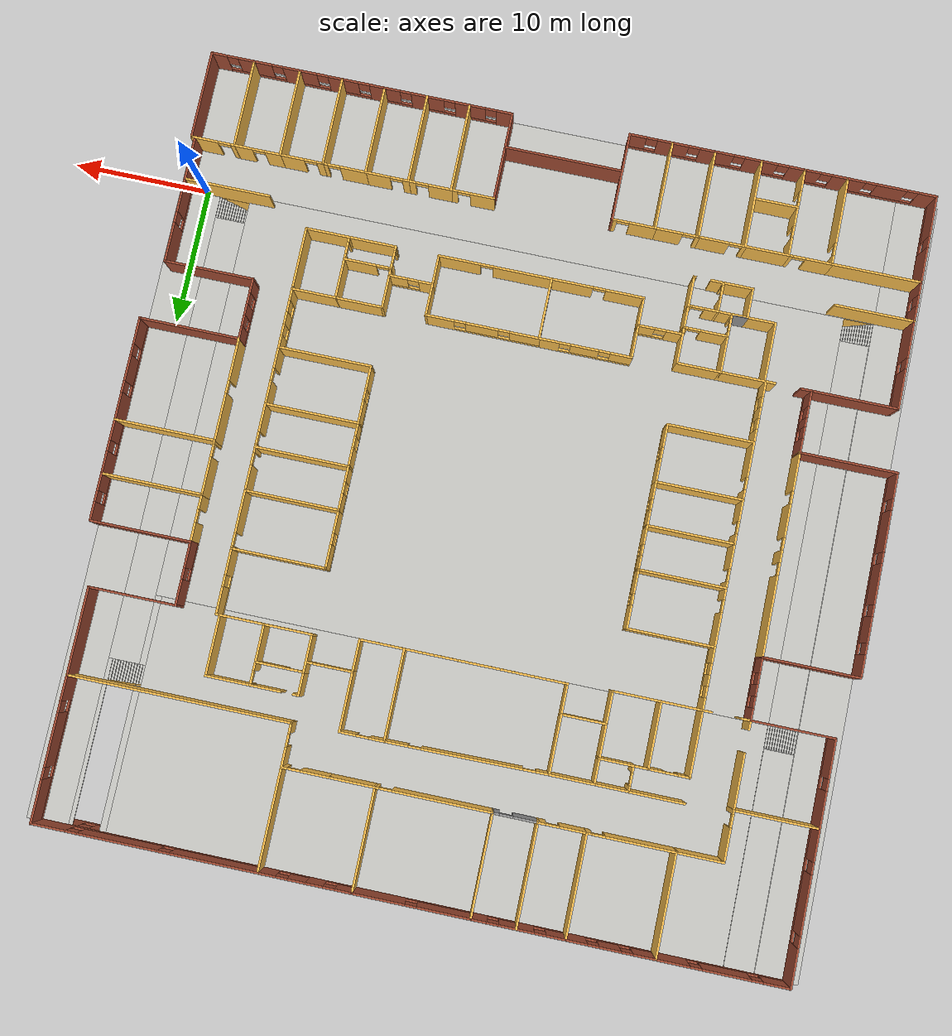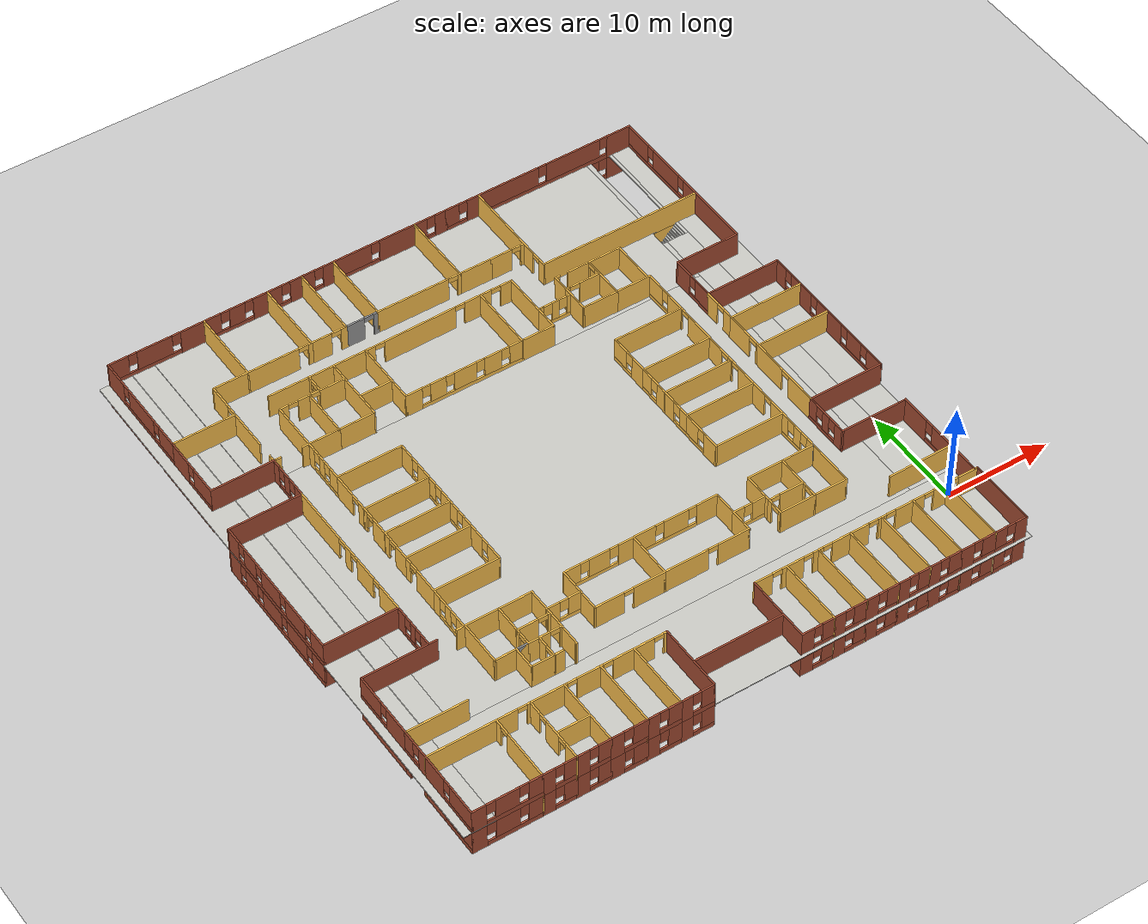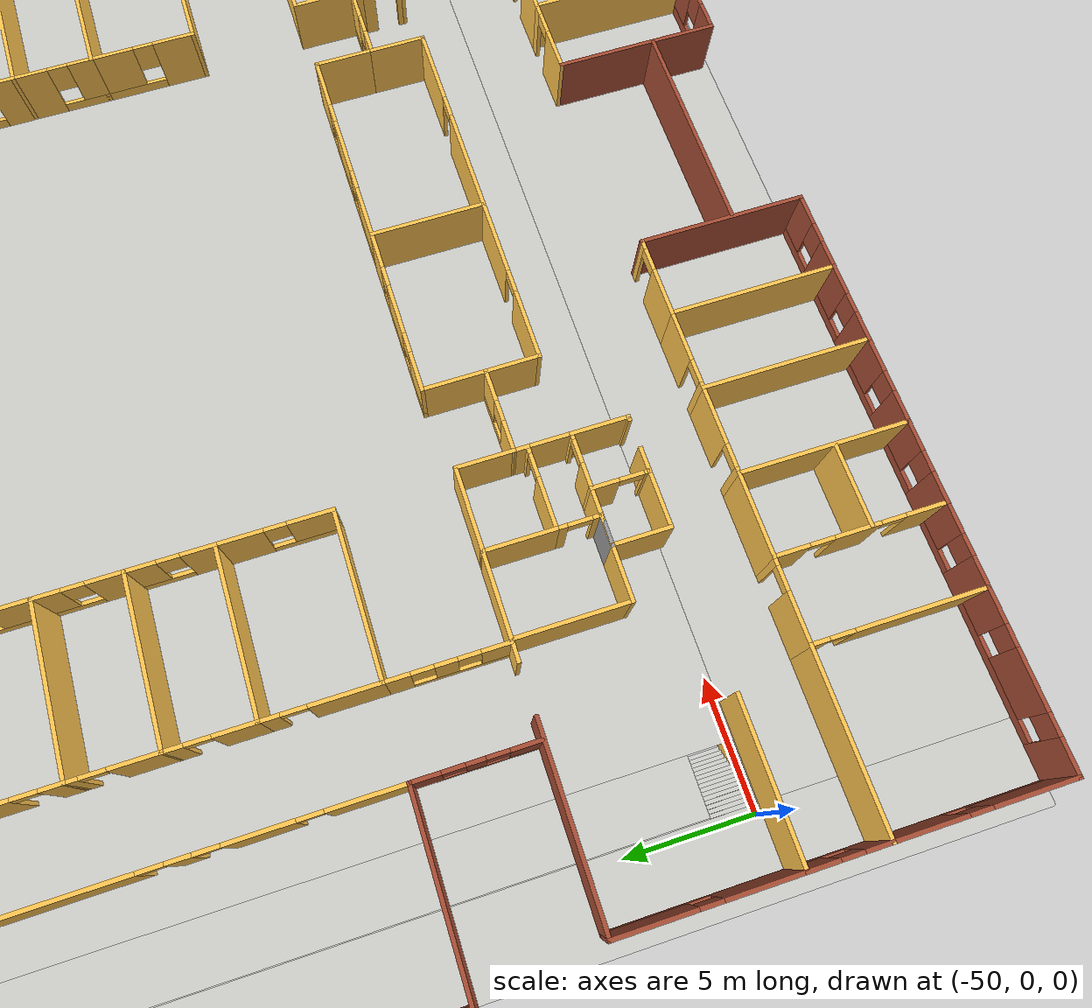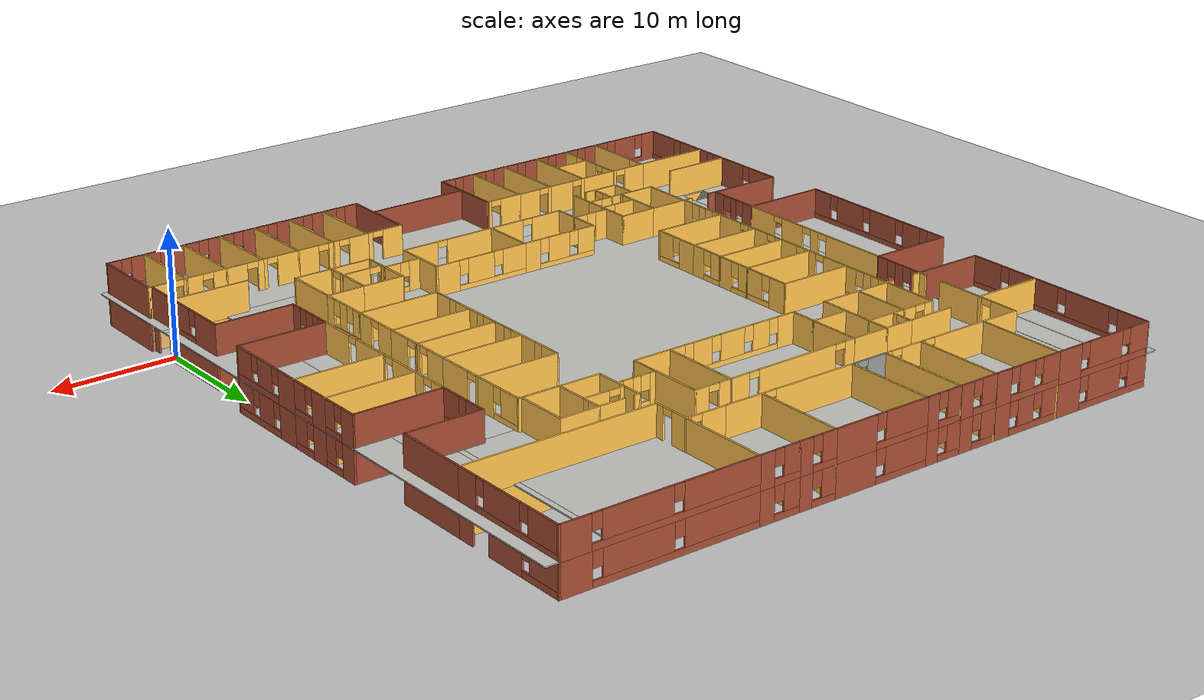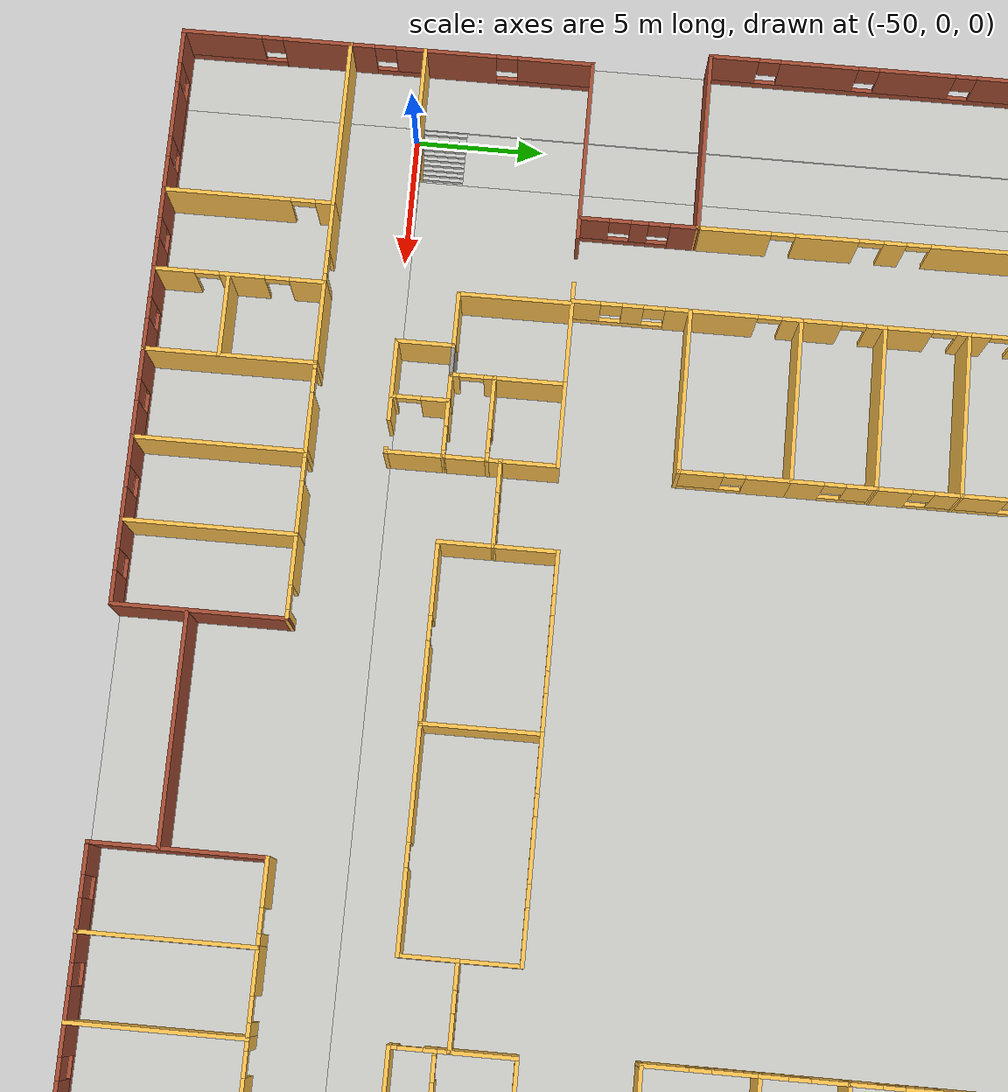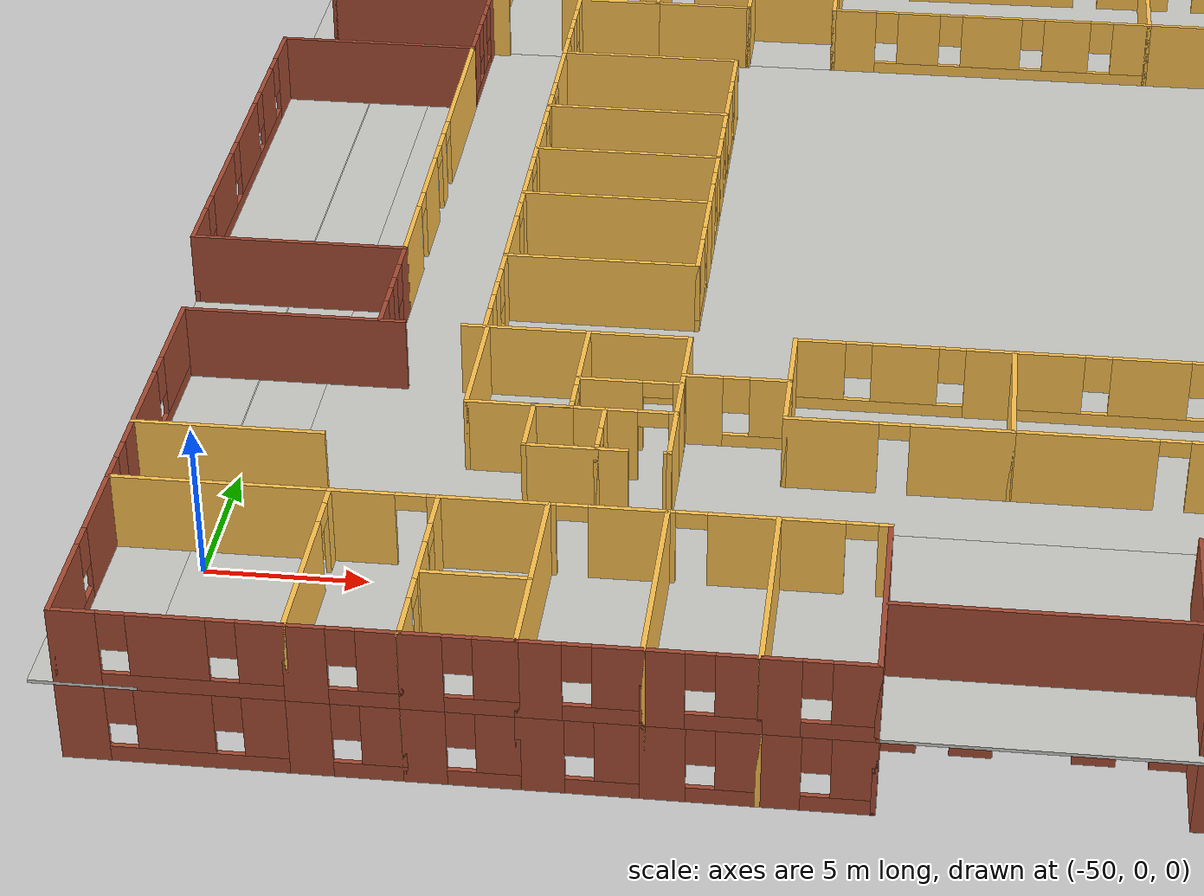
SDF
<sdf version="1.7">
 <world name="default">
  <light name="sun" type="directional">
   <pose>0 0 10 0 -0 0</pose>
   <diffuse>0.8 0.8 0.8 1</diffuse>
   <specular>0.2 0.2 0.2 1</specular>
   <attenuation>
    <range>1000</range>
    <constant>0.9</constant>
    <linear>0.01</linear>
    <quadratic>0.001</quadratic>
   </attenuation>
   <direction>-0.5 0.1 -0.9</direction>
   <spot><inner_angle>0</inner_angle><outer_angle>0</outer_angle><falloff>0</falloff></spot>
  </light>
  <model name="ground_plane">
   <static>1</static>
   <link name="link">
    <collision name="collision">
     <geometry><plane><normal>0 0 1</normal><size>100 100</size></plane></geometry>
     <surface>
      <contact><collide_bitmask>65535</collide_bitmask></contact>
      <friction><ode><mu>100</mu><mu2>50</mu2></ode></friction>
     </surface>
    </collision>
    <visual name="visual">
     <cast_shadows>0</cast_shadows>
     <geometry><plane><normal>0 0 1</normal><size>100 100</size></plane></geometry>
     <material>
      <script><uri>file://media/materials/scripts/gazebo.material</uri><name>Gazebo/Grey</name></script>
     </material>
    </visual>
   </link>
  </model>
  <gravity>0 0 -9.8</gravity>
  <magnetic_field>6e-06 2.3e-05 -4.2e-05</magnetic_field>
  <atmosphere type="adiabatic"/>
  <physics type="ode">
   <max_step_size>0.001</max_step_size>
   <real_time_factor>1</real_time_factor>
   <real_time_update_rate>1000</real_time_update_rate>
  </physics>
  <scene><ambient>0.4 0.4 0.4 1</ambient><background>0.7 0.7 0.7 1</background><shadows>1</shadows></scene>
  <spherical_coordinates>
   <surface_model>EARTH_WGS84</surface_model>
   <latitude_deg>0</latitude_deg>
   <longitude_deg>0</longitude_deg>
   <elevation>0</elevation>
   <heading_deg>0</heading_deg>
  </spherical_coordinates>
  <model name="DepartmentBuilding">
   <pose>-25.6559 18.8293 0 0 -0 0</pose>
   <link name="Floor_2">
    <pose>-1e-06 -7.8e-05 2.5 0 -0 0</pose>
    <visual name="Floor_2_Visual_0">
     <pose>-25.4296 0 0.05 0 -0 0</pose>
     <geometry><box><size>3.02955 55.5283 0.1</size></box></geometry>
     <material>
      <script><uri>file://media/materials/scripts/gazebo.material</uri><name>Gazebo/CeilingTiled</name></script>
      <ambient>1 1 1 1</ambient>
     </material>
     <meta><layer>1</layer></meta>
    </visual>
    <collision name="Floor_2_Collision_0">
     <geometry><box><size>3.02955 55.5283 0.1</size></box></geometry>
     <pose>-25.4296 0 0.05 0 -0 0</pose>
    </collision>
    <visual name="Floor_2_Visual_1">
     <pose>1.51477 -23.0785 0.05 0 -0 0</pose>
     <geometry><box><size>50.8593 9.37122 0.1</size></box></geometry>
     <material>
      <script><uri>file://media/materials/scripts/gazebo.material</uri><name>Gazebo/CeilingTiled</name></script>
      <ambient>1 1 1 1</ambient>
     </material>
     <meta><layer>1</layer></meta>
    </visual>
    <collision name="Floor_2_Collision_1">
     <geometry><box><size>50.8593 9.37122 0.1</size></box></geometry>
     <pose>1.51477 -23.0785 0.05 0 -0 0</pose>
    </collision>
    <visual name="Floor_2_Visual_2">
     <pose>0.030895 -3.65943 0.05 0 -0 0</pose>
     <geometry><box><size>43.6115 29.467 0.1</size></box></geometry>
     <material>
      <script><uri>file://media/materials/scripts/gazebo.material</uri><name>Gazebo/CeilingTiled</name></script>
      <ambient>1 1 1 1</ambient>
     </material>
     <meta><layer>1</layer></meta>
    </visual>
    <collision name="Floor_2_Collision_2">
     <geometry><box><size>43.6115 29.467 0.1</size></box></geometry>
     <pose>0.030895 -3.65943 0.05 0 -0 0</pose>
    </collision>
    <visual name="Floor_2_Visual_3">
     <pose>24.3905 -18.149 0.05 0 -0 0</pose>
     <geometry><box><size>5.10775 0.487854 0.1</size></box></geometry>
     <material>
      <script><uri>file://media/materials/scripts/gazebo.material</uri><name>Gazebo/CeilingTiled</name></script>
      <ambient>1 1 1 1</ambient>
     </material>
     <meta><layer>1</layer></meta>
    </visual>
    <collision name="Floor_2_Collision_3">
     <geometry><box><size>5.10775 0.487854 0.1</size></box></geometry>
     <pose>24.3905 -18.149 0.05 0 -0 0</pose>
    </collision>
    <visual name="Floor_2_Visual_4">
     <pose>25.4813 4.92953 0.05 0 -0 0</pose>
     <geometry><box><size>2.9262 45.6692 0.1</size></box></geometry>
     <material>
      <script><uri>file://media/materials/scripts/gazebo.material</uri><name>Gazebo/CeilingTiled</name></script>
      <ambient>1 1 1 1</ambient>
     </material>
     <meta><layer>1</layer></meta>
    </visual>
    <collision name="Floor_2_Collision_4">
     <geometry><box><size>2.9262 45.6692 0.1</size></box></geometry>
     <pose>25.4813 4.92953 0.05 0 -0 0</pose>
    </collision>
    <visual name="Floor_2_Visual_5">
     <pose>-23.8968 5.51561 0.05 0 -0 0</pose>
     <geometry><box><size>0.036097 44.4971 0.1</size></box></geometry>
     <material>
      <script><uri>file://media/materials/scripts/gazebo.material</uri><name>Gazebo/CeilingTiled</name></script>
      <ambient>1 1 1 1</ambient>
     </material>
     <meta><layer>1</layer></meta>
    </visual>
    <collision name="Floor_2_Collision_5">
     <geometry><box><size>0.036097 44.4971 0.1</size></box></geometry>
     <pose>-23.8968 5.51561 0.05 0 -0 0</pose>
    </collision>
    <visual name="Floor_2_Visual_6">
     <pose>-22.8268 -2.82943 0.05 0 -0 0</pose>
     <geometry><box><size>2.1039 27.807 0.1</size></box></geometry>
     <material>
      <script><uri>file://media/materials/scripts/gazebo.material</uri><name>Gazebo/CeilingTiled</name></script>
      <ambient>1 1 1 1</ambient>
     </material>
     <meta><layer>1</layer></meta>
    </visual>
    <collision name="Floor_2_Collision_6">
     <geometry><box><size>2.1039 27.807 0.1</size></box></geometry>
     <pose>-22.8268 -2.82943 0.05 0 -0 0</pose>
    </collision>
    <visual name="Floor_2_Visual_7">
     <pose>22.9274 -0.181225 0.05 0 -0 0</pose>
     <geometry><box><size>2.18155 32.3374 0.1</size></box></geometry>
     <material>
      <script><uri>file://media/materials/scripts/gazebo.material</uri><name>Gazebo/CeilingTiled</name></script>
      <ambient>1 1 1 1</ambient>
     </material>
     <meta><layer>1</layer></meta>
    </visual>
    <collision name="Floor_2_Collision_7">
     <geometry><box><size>2.18155 32.3374 0.1</size></box></geometry>
     <pose>22.9274 -0.181225 0.05 0 -0 0</pose>
    </collision>
    <visual name="Floor_2_Visual_8">
     <pose>-0.185707 19.4191 0.05 0 -0 0</pose>
     <geometry><box><size>43.1392 16.6901 0.1</size></box></geometry>
     <material>
      <script><uri>file://media/materials/scripts/gazebo.material</uri><name>Gazebo/CeilingTiled</name></script>
      <ambient>1 1 1 1</ambient>
     </material>
     <meta><layer>1</layer></meta>
    </visual>
    <collision name="Floor_2_Collision_8">
     <geometry><box><size>43.1392 16.6901 0.1</size></box></geometry>
     <pose>-0.185707 19.4191 0.05 0 -0 0</pose>
    </collision>
    <visual name="Floor_2_Visual_9">
     <pose>21.6103 13.5308 0.05 0 -0 0</pose>
     <geometry><box><size>0.452741 4.91341 0.1</size></box></geometry>
     <material>
      <script><uri>file://media/materials/scripts/gazebo.material</uri><name>Gazebo/CeilingTiled</name></script>
      <ambient>1 1 1 1</ambient>
     </material>
     <meta><layer>1</layer></meta>
    </visual>
    <collision name="Floor_2_Collision_9">
     <geometry><box><size>0.452741 4.91341 0.1</size></box></geometry>
     <pose>21.6103 13.5308 0.05 0 -0 0</pose>
    </collision>
    <visual name="Floor_2_Visual_10">
     <pose>-22.8268 20.225 0.05 0 -0 0</pose>
     <geometry><box><size>2.1039 15.0783 0.1</size></box></geometry>
     <material>
      <script><uri>file://media/materials/scripts/gazebo.material</uri><name>Gazebo/CeilingTiled</name></script>
      <ambient>1 1 1 1</ambient>
     </material>
     <meta><layer>1</layer></meta>
    </visual>
    <collision name="Floor_2_Collision_10">
     <geometry><box><size>2.1039 15.0783 0.1</size></box></geometry>
     <pose>-22.8268 20.225 0.05 0 -0 0</pose>
    </collision>
    <visual name="Floor_2_Visual_11">
     <pose>23.8698 21.8758 0.05 0 -0 0</pose>
     <geometry><box><size>0.296725 11.7767 0.1</size></box></geometry>
     <material>
      <script><uri>file://media/materials/scripts/gazebo.material</uri><name>Gazebo/CeilingTiled</name></script>
      <ambient>1 1 1 1</ambient>
     </material>
     <meta><layer>1</layer></meta>
    </visual>
    <collision name="Floor_2_Collision_11">
     <geometry><box><size>0.296725 11.7767 0.1</size></box></geometry>
     <pose>23.8698 21.8758 0.05 0 -0 0</pose>
    </collision>
    <visual name="Floor_2_Visual_12">
     <pose>21.6103 22.6205 0.05 0 -0 0</pose>
     <geometry><box><size>0.452741 10.2872 0.1</size></box></geometry>
     <material>
      <script><uri>file://media/materials/scripts/gazebo.material</uri><name>Gazebo/CeilingTiled</name></script>
      <ambient>1 1 1 1</ambient>
     </material>
     <meta><layer>1</layer></meta>
    </visual>
    <collision name="Floor_2_Collision_12">
     <geometry><box><size>0.452741 10.2872 0.1</size></box></geometry>
     <pose>21.6103 22.6205 0.05 0 -0 0</pose>
    </collision>
   </link>
   <link name="Stairs_0">
    <visual name="Stairs_0_Visual_0">
     <pose>21.9094 -17.1276 0.083333 0 -0 1.5708</pose>
     <geometry><box><size>1.55513 0.145437 0.166667</size></box></geometry>
     <material>
      <script><uri>file://media/materials/scripts/gazebo.material</uri><name>Gazebo/CeilingTiled</name></script>
      <ambient>1 1 1 1</ambient>
     </material>
     <meta><layer>0</layer></meta>
    </visual>
    <collision name="Stairs_0_Collision_0">
     <geometry><box><size>1.55513 0.145437 0.166667</size></box></geometry>
     <pose>21.9094 -17.1276 0.083333 0 -0 1.5708</pose>
    </collision>
    <visual name="Stairs_0_Visual_1">
     <pose>22.0548 -17.1276 0.25 0 -0 1.5708</pose>
     <geometry><box><size>1.55513 0.145437 0.166667</size></box></geometry>
     <material>
      <script><uri>file://media/materials/scripts/gazebo.material</uri><name>Gazebo/CeilingTiled</name></script>
      <ambient>1 1 1 1</ambient>
     </material>
     <meta><layer>0</layer></meta>
    </visual>
    <collision name="Stairs_0_Collision_1">
     <geometry><box><size>1.55513 0.145437 0.166667</size></box></geometry>
     <pose>22.0548 -17.1276 0.25 0 -0 1.5708</pose>
    </collision>
    <visual name="Stairs_0_Visual_2">
     <pose>22.2002 -17.1276 0.416667 0 -0 1.5708</pose>
     <geometry><box><size>1.55513 0.145437 0.166667</size></box></geometry>
     <material>
      <script><uri>file://media/materials/scripts/gazebo.material</uri><name>Gazebo/CeilingTiled</name></script>
      <ambient>1 1 1 1</ambient>
     </material>
     <meta><layer>0</layer></meta>
    </visual>
    <collision name="Stairs_0_Collision_2">
     <geometry><box><size>1.55513 0.145437 0.166667</size></box></geometry>
     <pose>22.2002 -17.1276 0.416667 0 -0 1.5708</pose>
    </collision>
    <visual name="Stairs_0_Visual_3">
     <pose>22.3457 -17.1276 0.583333 0 -0 1.5708</pose>
     <geometry><box><size>1.55513 0.145437 0.166667</size></box></geometry>
     <material>
      <script><uri>file://media/materials/scripts/gazebo.material</uri><name>Gazebo/CeilingTiled</name></script>
      <ambient>1 1 1 1</ambient>
     </material>
     <meta><layer>0</layer></meta>
    </visual>
    <collision name="Stairs_0_Collision_3">
     <geometry><box><size>1.55513 0.145437 0.166667</size></box></geometry>
     <pose>22.3457 -17.1276 0.583333 0 -0 1.5708</pose>
    </collision>
    <visual name="Stairs_0_Visual_4">
     <pose>22.4911 -17.1276 0.75 0 -0 1.5708</pose>
     <geometry><box><size>1.55513 0.145437 0.166667</size></box></geometry>
     <material>
      <script><uri>file://media/materials/scripts/gazebo.material</uri><name>Gazebo/CeilingTiled</name></script>
      <ambient>1 1 1 1</ambient>
     </material>
     <meta><layer>0</layer></meta>
    </visual>
    <collision name="Stairs_0_Collision_4">
     <geometry><box><size>1.55513 0.145437 0.166667</size></box></geometry>
     <pose>22.4911 -17.1276 0.75 0 -0 1.5708</pose>
    </collision>
    <visual name="Stairs_0_Visual_5">
     <pose>22.6366 -17.1276 0.916667 0 -0 1.5708</pose>
     <geometry><box><size>1.55513 0.145437 0.166667</size></box></geometry>
     <material>
      <script><uri>file://media/materials/scripts/gazebo.material</uri><name>Gazebo/CeilingTiled</name></script>
      <ambient>1 1 1 1</ambient>
     </material>
     <meta><layer>0</layer></meta>
    </visual>
    <collision name="Stairs_0_Collision_5">
     <geometry><box><size>1.55513 0.145437 0.166667</size></box></geometry>
     <pose>22.6366 -17.1276 0.916667 0 -0 1.5708</pose>
    </collision>
    <visual name="Stairs_0_Visual_6">
     <pose>22.782 -17.1276 1.08333 0 -0 1.5708</pose>
     <geometry><box><size>1.55513 0.145437 0.166667</size></box></geometry>
     <material>
      <script><uri>file://media/materials/scripts/gazebo.material</uri><name>Gazebo/CeilingTiled</name></script>
      <ambient>1 1 1 1</ambient>
     </material>
     <meta><layer>0</layer></meta>
    </visual>
    <collision name="Stairs_0_Collision_6">
     <geometry><box><size>1.55513 0.145437 0.166667</size></box></geometry>
     <pose>22.782 -17.1276 1.08333 0 -0 1.5708</pose>
    </collision>
    <visual name="Stairs_0_Visual_7">
     <pose>22.9274 -17.1276 1.25 0 -0 1.5708</pose>
     <geometry><box><size>1.55513 0.145437 0.166667</size></box></geometry>
     <material>
      <script><uri>file://media/materials/scripts/gazebo.material</uri><name>Gazebo/CeilingTiled</name></script>
      <ambient>1 1 1 1</ambient>
     </material>
     <meta><layer>0</layer></meta>
    </visual>
    <collision name="Stairs_0_Collision_7">
     <geometry><box><size>1.55513 0.145437 0.166667</size></box></geometry>
     <pose>22.9274 -17.1276 1.25 0 -0 1.5708</pose>
    </collision>
    <visual name="Stairs_0_Visual_8">
     <pose>23.0729 -17.1276 1.41667 0 -0 1.5708</pose>
     <geometry><box><size>1.55513 0.145437 0.166667</size></box></geometry>
     <material>
      <script><uri>file://media/materials/scripts/gazebo.material</uri><name>Gazebo/CeilingTiled</name></script>
      <ambient>1 1 1 1</ambient>
     </material>
     <meta><layer>0</layer></meta>
    </visual>
    <collision name="Stairs_0_Collision_8">
     <geometry><box><size>1.55513 0.145437 0.166667</size></box></geometry>
     <pose>23.0729 -17.1276 1.41667 0 -0 1.5708</pose>
    </collision>
    <visual name="Stairs_0_Visual_9">
     <pose>23.2183 -17.1276 1.58333 0 -0 1.5708</pose>
     <geometry><box><size>1.55513 0.145437 0.166667</size></box></geometry>
     <material>
      <script><uri>file://media/materials/scripts/gazebo.material</uri><name>Gazebo/CeilingTiled</name></script>
      <ambient>1 1 1 1</ambient>
     </material>
     <meta><layer>0</layer></meta>
    </visual>
    <collision name="Stairs_0_Collision_9">
     <geometry><box><size>1.55513 0.145437 0.166667</size></box></geometry>
     <pose>23.2183 -17.1276 1.58333 0 -0 1.5708</pose>
    </collision>
    <visual name="Stairs_0_Visual_10">
     <pose>23.3637 -17.1276 1.75 0 -0 1.5708</pose>
     <geometry><box><size>1.55513 0.145437 0.166667</size></box></geometry>
     <material>
      <script><uri>file://media/materials/scripts/gazebo.material</uri><name>Gazebo/CeilingTiled</name></script>
      <ambient>1 1 1 1</ambient>
     </material>
     <meta><layer>0</layer></meta>
    </visual>
    <collision name="Stairs_0_Collision_10">
     <geometry><box><size>1.55513 0.145437 0.166667</size></box></geometry>
     <pose>23.3637 -17.1276 1.75 0 -0 1.5708</pose>
    </collision>
    <visual name="Stairs_0_Visual_11">
     <pose>23.5092 -17.1276 1.91667 0 -0 1.5708</pose>
     <geometry><box><size>1.55513 0.145437 0.166667</size></box></geometry>
     <material>
      <script><uri>file://media/materials/scripts/gazebo.material</uri><name>Gazebo/CeilingTiled</name></script>
      <ambient>1 1 1 1</ambient>
     </material>
     <meta><layer>0</layer></meta>
    </visual>
    <collision name="Stairs_0_Collision_11">
     <geometry><box><size>1.55513 0.145437 0.166667</size></box></geometry>
     <pose>23.5092 -17.1276 1.91667 0 -0 1.5708</pose>
    </collision>
    <visual name="Stairs_0_Visual_12">
     <pose>23.6546 -17.1276 2.08333 0 -0 1.5708</pose>
     <geometry><box><size>1.55513 0.145437 0.166667</size></box></geometry>
     <material>
      <script><uri>file://media/materials/scripts/gazebo.material</uri><name>Gazebo/CeilingTiled</name></script>
      <ambient>1 1 1 1</ambient>
     </material>
     <meta><layer>0</layer></meta>
    </visual>
    <collision name="Stairs_0_Collision_12">
     <geometry><box><size>1.55513 0.145437 0.166667</size></box></geometry>
     <pose>23.6546 -17.1276 2.08333 0 -0 1.5708</pose>
    </collision>
    <visual name="Stairs_0_Visual_13">
     <pose>23.8001 -17.1276 2.25 0 -0 1.5708</pose>
     <geometry><box><size>1.55513 0.145437 0.166667</size></box></geometry>
     <material>
      <script><uri>file://media/materials/scripts/gazebo.material</uri><name>Gazebo/CeilingTiled</name></script>
      <ambient>1 1 1 1</ambient>
     </material>
     <meta><layer>0</layer></meta>
    </visual>
    <collision name="Stairs_0_Collision_13">
     <geometry><box><size>1.55513 0.145437 0.166667</size></box></geometry>
     <pose>23.8001 -17.1276 2.25 0 -0 1.5708</pose>
    </collision>
    <visual name="Stairs_0_Visual_14">
     <pose>23.9455 -17.1276 2.41667 0 -0 1.5708</pose>
     <geometry><box><size>1.55513 0.145437 0.166667</size></box></geometry>
     <material>
      <script><uri>file://media/materials/scripts/gazebo.material</uri><name>Gazebo/CeilingTiled</name></script>
      <ambient>1 1 1 1</ambient>
     </material>
     <meta><layer>0</layer></meta>
    </visual>
    <collision name="Stairs_0_Collision_14">
     <geometry><box><size>1.55513 0.145437 0.166667</size></box></geometry>
     <pose>23.9455 -17.1276 2.41667 0 -0 1.5708</pose>
    </collision>
   </link>
   <link name="Stairs_1">
    <visual name="Stairs_1_Visual_0">
     <pose>21.4618 16.7321 0.083333 0 -0 1.5708</pose>
     <geometry><box><size>1.48944 0.155838 0.166667</size></box></geometry>
     <material>
      <script><uri>file://media/materials/scripts/gazebo.material</uri><name>Gazebo/CeilingTiled</name></script>
      <ambient>1 1 1 1</ambient>
     </material>
     <meta><layer>0</layer></meta>
    </visual>
    <collision name="Stairs_1_Collision_0">
     <geometry><box><size>1.48944 0.155838 0.166667</size></box></geometry>
     <pose>21.4618 16.7321 0.083333 0 -0 1.5708</pose>
    </collision>
    <visual name="Stairs_1_Visual_1">
     <pose>21.6177 16.7321 0.25 0 -0 1.5708</pose>
     <geometry><box><size>1.48944 0.155838 0.166667</size></box></geometry>
     <material>
      <script><uri>file://media/materials/scripts/gazebo.material</uri><name>Gazebo/CeilingTiled</name></script>
      <ambient>1 1 1 1</ambient>
     </material>
     <meta><layer>0</layer></meta>
    </visual>
    <collision name="Stairs_1_Collision_1">
     <geometry><box><size>1.48944 0.155838 0.166667</size></box></geometry>
     <pose>21.6177 16.7321 0.25 0 -0 1.5708</pose>
    </collision>
    <visual name="Stairs_1_Visual_2">
     <pose>21.7735 16.7321 0.416667 0 -0 1.5708</pose>
     <geometry><box><size>1.48944 0.155838 0.166667</size></box></geometry>
     <material>
      <script><uri>file://media/materials/scripts/gazebo.material</uri><name>Gazebo/CeilingTiled</name></script>
      <ambient>1 1 1 1</ambient>
     </material>
     <meta><layer>0</layer></meta>
    </visual>
    <collision name="Stairs_1_Collision_2">
     <geometry><box><size>1.48944 0.155838 0.166667</size></box></geometry>
     <pose>21.7735 16.7321 0.416667 0 -0 1.5708</pose>
    </collision>
    <visual name="Stairs_1_Visual_3">
     <pose>21.9293 16.7321 0.583333 0 -0 1.5708</pose>
     <geometry><box><size>1.48944 0.155838 0.166667</size></box></geometry>
     <material>
      <script><uri>file://media/materials/scripts/gazebo.material</uri><name>Gazebo/CeilingTiled</name></script>
      <ambient>1 1 1 1</ambient>
     </material>
     <meta><layer>0</layer></meta>
    </visual>
    <collision name="Stairs_1_Collision_3">
     <geometry><box><size>1.48944 0.155838 0.166667</size></box></geometry>
     <pose>21.9293 16.7321 0.583333 0 -0 1.5708</pose>
    </collision>
    <visual name="Stairs_1_Visual_4">
     <pose>22.0852 16.7321 0.75 0 -0 1.5708</pose>
     <geometry><box><size>1.48944 0.155838 0.166667</size></box></geometry>
     <material>
      <script><uri>file://media/materials/scripts/gazebo.material</uri><name>Gazebo/CeilingTiled</name></script>
      <ambient>1 1 1 1</ambient>
     </material>
     <meta><layer>0</layer></meta>
    </visual>
    <collision name="Stairs_1_Collision_4">
     <geometry><box><size>1.48944 0.155838 0.166667</size></box></geometry>
     <pose>22.0852 16.7321 0.75 0 -0 1.5708</pose>
    </collision>
    <visual name="Stairs_1_Visual_5">
     <pose>22.241 16.7321 0.916667 0 -0 1.5708</pose>
     <geometry><box><size>1.48944 0.155838 0.166667</size></box></geometry>
     <material>
      <script><uri>file://media/materials/scripts/gazebo.material</uri><name>Gazebo/CeilingTiled</name></script>
      <ambient>1 1 1 1</ambient>
     </material>
     <meta><layer>0</layer></meta>
    </visual>
    <collision name="Stairs_1_Collision_5">
     <geometry><box><size>1.48944 0.155838 0.166667</size></box></geometry>
     <pose>22.241 16.7321 0.916667 0 -0 1.5708</pose>
    </collision>
    <visual name="Stairs_1_Visual_6">
     <pose>22.3969 16.7321 1.08333 0 -0 1.5708</pose>
     <geometry><box><size>1.48944 0.155838 0.166667</size></box></geometry>
     <material>
      <script><uri>file://media/materials/scripts/gazebo.material</uri><name>Gazebo/CeilingTiled</name></script>
      <ambient>1 1 1 1</ambient>
     </material>
     <meta><layer>0</layer></meta>
    </visual>
    <collision name="Stairs_1_Collision_6">
     <geometry><box><size>1.48944 0.155838 0.166667</size></box></geometry>
     <pose>22.3969 16.7321 1.08333 0 -0 1.5708</pose>
    </collision>
    <visual name="Stairs_1_Visual_7">
     <pose>22.5527 16.7321 1.25 0 -0 1.5708</pose>
     <geometry><box><size>1.48944 0.155838 0.166667</size></box></geometry>
     <material>
      <script><uri>file://media/materials/scripts/gazebo.material</uri><name>Gazebo/CeilingTiled</name></script>
      <ambient>1 1 1 1</ambient>
     </material>
     <meta><layer>0</layer></meta>
    </visual>
    <collision name="Stairs_1_Collision_7">
     <geometry><box><size>1.48944 0.155838 0.166667</size></box></geometry>
     <pose>22.5527 16.7321 1.25 0 -0 1.5708</pose>
    </collision>
    <visual name="Stairs_1_Visual_8">
     <pose>22.7085 16.7321 1.41667 0 -0 1.5708</pose>
     <geometry><box><size>1.48944 0.155838 0.166667</size></box></geometry>
     <material>
      <script><uri>file://media/materials/scripts/gazebo.material</uri><name>Gazebo/CeilingTiled</name></script>
      <ambient>1 1 1 1</ambient>
     </material>
     <meta><layer>0</layer></meta>
    </visual>
    <collision name="Stairs_1_Collision_8">
     <geometry><box><size>1.48944 0.155838 0.166667</size></box></geometry>
     <pose>22.7085 16.7321 1.41667 0 -0 1.5708</pose>
    </collision>
    <visual name="Stairs_1_Visual_9">
     <pose>22.8644 16.7321 1.58333 0 -0 1.5708</pose>
     <geometry><box><size>1.48944 0.155838 0.166667</size></box></geometry>
     <material>
      <script><uri>file://media/materials/scripts/gazebo.material</uri><name>Gazebo/CeilingTiled</name></script>
      <ambient>1 1 1 1</ambient>
     </material>
     <meta><layer>0</layer></meta>
    </visual>
    <collision name="Stairs_1_Collision_9">
     <geometry><box><size>1.48944 0.155838 0.166667</size></box></geometry>
     <pose>22.8644 16.7321 1.58333 0 -0 1.5708</pose>
    </collision>
    <visual name="Stairs_1_Visual_10">
     <pose>23.0202 16.7321 1.75 0 -0 1.5708</pose>
     <geometry><box><size>1.48944 0.155838 0.166667</size></box></geometry>
     <material>
      <script><uri>file://media/materials/scripts/gazebo.material</uri><name>Gazebo/CeilingTiled</name></script>
      <ambient>1 1 1 1</ambient>
     </material>
     <meta><layer>0</layer></meta>
    </visual>
    <collision name="Stairs_1_Collision_10">
     <geometry><box><size>1.48944 0.155838 0.166667</size></box></geometry>
     <pose>23.0202 16.7321 1.75 0 -0 1.5708</pose>
    </collision>
    <visual name="Stairs_1_Visual_11">
     <pose>23.1761 16.7321 1.91667 0 -0 1.5708</pose>
     <geometry><box><size>1.48944 0.155838 0.166667</size></box></geometry>
     <material>
      <script><uri>file://media/materials/scripts/gazebo.material</uri><name>Gazebo/CeilingTiled</name></script>
      <ambient>1 1 1 1</ambient>
     </material>
     <meta><layer>0</layer></meta>
    </visual>
    <collision name="Stairs_1_Collision_11">
     <geometry><box><size>1.48944 0.155838 0.166667</size></box></geometry>
     <pose>23.1761 16.7321 1.91667 0 -0 1.5708</pose>
    </collision>
    <visual name="Stairs_1_Visual_12">
     <pose>23.3319 16.7321 2.08333 0 -0 1.5708</pose>
     <geometry><box><size>1.48944 0.155838 0.166667</size></box></geometry>
     <material>
      <script><uri>file://media/materials/scripts/gazebo.material</uri><name>Gazebo/CeilingTiled</name></script>
      <ambient>1 1 1 1</ambient>
     </material>
     <meta><layer>0</layer></meta>
    </visual>
    <collision name="Stairs_1_Collision_12">
     <geometry><box><size>1.48944 0.155838 0.166667</size></box></geometry>
     <pose>23.3319 16.7321 2.08333 0 -0 1.5708</pose>
    </collision>
    <visual name="Stairs_1_Visual_13">
     <pose>23.4877 16.7321 2.25 0 -0 1.5708</pose>
     <geometry><box><size>1.48944 0.155838 0.166667</size></box></geometry>
     <material>
      <script><uri>file://media/materials/scripts/gazebo.material</uri><name>Gazebo/CeilingTiled</name></script>
      <ambient>1 1 1 1</ambient>
     </material>
     <meta><layer>0</layer></meta>
    </visual>
    <collision name="Stairs_1_Collision_13">
     <geometry><box><size>1.48944 0.155838 0.166667</size></box></geometry>
     <pose>23.4877 16.7321 2.25 0 -0 1.5708</pose>
    </collision>
    <visual name="Stairs_1_Visual_14">
     <pose>23.6436 16.7321 2.41667 0 -0 1.5708</pose>
     <geometry><box><size>1.48944 0.155838 0.166667</size></box></geometry>
     <material>
      <script><uri>file://media/materials/scripts/gazebo.material</uri><name>Gazebo/CeilingTiled</name></script>
      <ambient>1 1 1 1</ambient>
     </material>
     <meta><layer>0</layer></meta>
    </visual>
    <collision name="Stairs_1_Collision_14">
     <geometry><box><size>1.48944 0.155838 0.166667</size></box></geometry>
     <pose>23.6436 16.7321 2.41667 0 -0 1.5708</pose>
    </collision>
   </link>
   <link name="Stairs_2">
    <visual name="Stairs_2_Visual_0">
     <pose>-21.8261 11.8799 0.083333 0 -0 -1.5708</pose>
     <geometry><box><size>1.6118 0.141563 0.166667</size></box></geometry>
     <material>
      <script><uri>file://media/materials/scripts/gazebo.material</uri><name>Gazebo/CeilingTiled</name></script>
      <ambient>1 1 1 1</ambient>
     </material>
     <meta><layer>0</layer></meta>
    </visual>
    <collision name="Stairs_2_Collision_0">
     <geometry><box><size>1.6118 0.141563 0.166667</size></box></geometry>
     <pose>-21.8261 11.8799 0.083333 0 -0 -1.5708</pose>
    </collision>
    <visual name="Stairs_2_Visual_1">
     <pose>-21.9677 11.8799 0.25 0 -0 -1.5708</pose>
     <geometry><box><size>1.6118 0.141563 0.166667</size></box></geometry>
     <material>
      <script><uri>file://media/materials/scripts/gazebo.material</uri><name>Gazebo/CeilingTiled</name></script>
      <ambient>1 1 1 1</ambient>
     </material>
     <meta><layer>0</layer></meta>
    </visual>
    <collision name="Stairs_2_Collision_1">
     <geometry><box><size>1.6118 0.141563 0.166667</size></box></geometry>
     <pose>-21.9677 11.8799 0.25 0 -0 -1.5708</pose>
    </collision>
    <visual name="Stairs_2_Visual_2">
     <pose>-22.1092 11.8799 0.416667 0 -0 -1.5708</pose>
     <geometry><box><size>1.6118 0.141563 0.166667</size></box></geometry>
     <material>
      <script><uri>file://media/materials/scripts/gazebo.material</uri><name>Gazebo/CeilingTiled</name></script>
      <ambient>1 1 1 1</ambient>
     </material>
     <meta><layer>0</layer></meta>
    </visual>
    <collision name="Stairs_2_Collision_2">
     <geometry><box><size>1.6118 0.141563 0.166667</size></box></geometry>
     <pose>-22.1092 11.8799 0.416667 0 -0 -1.5708</pose>
    </collision>
    <visual name="Stairs_2_Visual_3">
     <pose>-22.2508 11.8799 0.583333 0 -0 -1.5708</pose>
     <geometry><box><size>1.6118 0.141563 0.166667</size></box></geometry>
     <material>
      <script><uri>file://media/materials/scripts/gazebo.material</uri><name>Gazebo/CeilingTiled</name></script>
      <ambient>1 1 1 1</ambient>
     </material>
     <meta><layer>0</layer></meta>
    </visual>
    <collision name="Stairs_2_Collision_3">
     <geometry><box><size>1.6118 0.141563 0.166667</size></box></geometry>
     <pose>-22.2508 11.8799 0.583333 0 -0 -1.5708</pose>
    </collision>
    <visual name="Stairs_2_Visual_4">
     <pose>-22.3924 11.8799 0.75 0 -0 -1.5708</pose>
     <geometry><box><size>1.6118 0.141563 0.166667</size></box></geometry>
     <material>
      <script><uri>file://media/materials/scripts/gazebo.material</uri><name>Gazebo/CeilingTiled</name></script>
      <ambient>1 1 1 1</ambient>
     </material>
     <meta><layer>0</layer></meta>
    </visual>
    <collision name="Stairs_2_Collision_4">
     <geometry><box><size>1.6118 0.141563 0.166667</size></box></geometry>
     <pose>-22.3924 11.8799 0.75 0 -0 -1.5708</pose>
    </collision>
    <visual name="Stairs_2_Visual_5">
     <pose>-22.5339 11.8799 0.916667 0 -0 -1.5708</pose>
     <geometry><box><size>1.6118 0.141563 0.166667</size></box></geometry>
     <material>
      <script><uri>file://media/materials/scripts/gazebo.material</uri><name>Gazebo/CeilingTiled</name></script>
      <ambient>1 1 1 1</ambient>
     </material>
     <meta><layer>0</layer></meta>
    </visual>
    <collision name="Stairs_2_Collision_5">
     <geometry><box><size>1.6118 0.141563 0.166667</size></box></geometry>
     <pose>-22.5339 11.8799 0.916667 0 -0 -1.5708</pose>
    </collision>
    <visual name="Stairs_2_Visual_6">
     <pose>-22.6755 11.8799 1.08333 0 -0 -1.5708</pose>
     <geometry><box><size>1.6118 0.141563 0.166667</size></box></geometry>
     <material>
      <script><uri>file://media/materials/scripts/gazebo.material</uri><name>Gazebo/CeilingTiled</name></script>
      <ambient>1 1 1 1</ambient>
     </material>
     <meta><layer>0</layer></meta>
    </visual>
    <collision name="Stairs_2_Collision_6">
     <geometry><box><size>1.6118 0.141563 0.166667</size></box></geometry>
     <pose>-22.6755 11.8799 1.08333 0 -0 -1.5708</pose>
    </collision>
    <visual name="Stairs_2_Visual_7">
     <pose>-22.817 11.8799 1.25 0 -0 -1.5708</pose>
     <geometry><box><size>1.6118 0.141563 0.166667</size></box></geometry>
     <material>
      <script><uri>file://media/materials/scripts/gazebo.material</uri><name>Gazebo/CeilingTiled</name></script>
      <ambient>1 1 1 1</ambient>
     </material>
     <meta><layer>0</layer></meta>
    </visual>
    <collision name="Stairs_2_Collision_7">
     <geometry><box><size>1.6118 0.141563 0.166667</size></box></geometry>
     <pose>-22.817 11.8799 1.25 0 -0 -1.5708</pose>
    </collision>
    <visual name="Stairs_2_Visual_8">
     <pose>-22.9586 11.8799 1.41667 0 -0 -1.5708</pose>
     <geometry><box><size>1.6118 0.141563 0.166667</size></box></geometry>
     <material>
      <script><uri>file://media/materials/scripts/gazebo.material</uri><name>Gazebo/CeilingTiled</name></script>
      <ambient>1 1 1 1</ambient>
     </material>
     <meta><layer>0</layer></meta>
    </visual>
    <collision name="Stairs_2_Collision_8">
     <geometry><box><size>1.6118 0.141563 0.166667</size></box></geometry>
     <pose>-22.9586 11.8799 1.41667 0 -0 -1.5708</pose>
    </collision>
    <visual name="Stairs_2_Visual_9">
     <pose>-23.1002 11.8799 1.58333 0 -0 -1.5708</pose>
     <geometry><box><size>1.6118 0.141563 0.166667</size></box></geometry>
     <material>
      <script><uri>file://media/materials/scripts/gazebo.material</uri><name>Gazebo/CeilingTiled</name></script>
      <ambient>1 1 1 1</ambient>
     </material>
     <meta><layer>0</layer></meta>
    </visual>
    <collision name="Stairs_2_Collision_9">
     <geometry><box><size>1.6118 0.141563 0.166667</size></box></geometry>
     <pose>-23.1002 11.8799 1.58333 0 -0 -1.5708</pose>
    </collision>
    <visual name="Stairs_2_Visual_10">
     <pose>-23.2417 11.8799 1.75 0 -0 -1.5708</pose>
     <geometry><box><size>1.6118 0.141563 0.166667</size></box></geometry>
     <material>
      <script><uri>file://media/materials/scripts/gazebo.material</uri><name>Gazebo/CeilingTiled</name></script>
      <ambient>1 1 1 1</ambient>
     </material>
     <meta><layer>0</layer></meta>
    </visual>
    <collision name="Stairs_2_Collision_10">
     <geometry><box><size>1.6118 0.141563 0.166667</size></box></geometry>
     <pose>-23.2417 11.8799 1.75 0 -0 -1.5708</pose>
    </collision>
    <visual name="Stairs_2_Visual_11">
     <pose>-23.3833 11.8799 1.91667 0 -0 -1.5708</pose>
     <geometry><box><size>1.6118 0.141563 0.166667</size></box></geometry>
     <material>
      <script><uri>file://media/materials/scripts/gazebo.material</uri><name>Gazebo/CeilingTiled</name></script>
      <ambient>1 1 1 1</ambient>
     </material>
     <meta><layer>0</layer></meta>
    </visual>
    <collision name="Stairs_2_Collision_11">
     <geometry><box><size>1.6118 0.141563 0.166667</size></box></geometry>
     <pose>-23.3833 11.8799 1.91667 0 -0 -1.5708</pose>
    </collision>
    <visual name="Stairs_2_Visual_12">
     <pose>-23.5249 11.8799 2.08333 0 -0 -1.5708</pose>
     <geometry><box><size>1.6118 0.141563 0.166667</size></box></geometry>
     <material>
      <script><uri>file://media/materials/scripts/gazebo.material</uri><name>Gazebo/CeilingTiled</name></script>
      <ambient>1 1 1 1</ambient>
     </material>
     <meta><layer>0</layer></meta>
    </visual>
    <collision name="Stairs_2_Collision_12">
     <geometry><box><size>1.6118 0.141563 0.166667</size></box></geometry>
     <pose>-23.5249 11.8799 2.08333 0 -0 -1.5708</pose>
    </collision>
    <visual name="Stairs_2_Visual_13">
     <pose>-23.6664 11.8799 2.25 0 -0 -1.5708</pose>
     <geometry><box><size>1.6118 0.141563 0.166667</size></box></geometry>
     <material>
      <script><uri>file://media/materials/scripts/gazebo.material</uri><name>Gazebo/CeilingTiled</name></script>
      <ambient>1 1 1 1</ambient>
     </material>
     <meta><layer>0</layer></meta>
    </visual>
    <collision name="Stairs_2_Collision_13">
     <geometry><box><size>1.6118 0.141563 0.166667</size></box></geometry>
     <pose>-23.6664 11.8799 2.25 0 -0 -1.5708</pose>
    </collision>
    <visual name="Stairs_2_Visual_14">
     <pose>-23.808 11.8799 2.41667 0 -0 -1.5708</pose>
     <geometry><box><size>1.6118 0.141563 0.166667</size></box></geometry>
     <material>
      <script><uri>file://media/materials/scripts/gazebo.material</uri><name>Gazebo/CeilingTiled</name></script>
      <ambient>1 1 1 1</ambient>
     </material>
     <meta><layer>0</layer></meta>
    </visual>
    <collision name="Stairs_2_Collision_14">
     <geometry><box><size>1.6118 0.141563 0.166667</size></box></geometry>
     <pose>-23.808 11.8799 2.41667 0 -0 -1.5708</pose>
    </collision>
   </link>
   <link name="Stairs_5">
    <visual name="Stairs_5_Visual_0">
     <pose>-21.8462 -17.563 0.083333 0 0 -1.5708</pose>
     <geometry><box><size>1.66 0.142667 0.166667</size></box></geometry>
     <material>
      <script><uri>file://media/materials/scripts/gazebo.material</uri><name>Gazebo/CeilingTiled</name></script>
      <ambient>1 1 1 1</ambient>
     </material>
     <meta><layer>0</layer></meta>
    </visual>
    <collision name="Stairs_5_Collision_0">
     <geometry><box><size>1.66 0.142667 0.166667</size></box></geometry>
     <pose>-21.8462 -17.563 0.083333 0 0 -1.5708</pose>
    </collision>
    <visual name="Stairs_5_Visual_1">
     <pose>-21.9889 -17.563 0.25 0 0 -1.5708</pose>
     <geometry><box><size>1.66 0.142667 0.166667</size></box></geometry>
     <material>
      <script><uri>file://media/materials/scripts/gazebo.material</uri><name>Gazebo/CeilingTiled</name></script>
      <ambient>1 1 1 1</ambient>
     </material>
     <meta><layer>0</layer></meta>
    </visual>
    <collision name="Stairs_5_Collision_1">
     <geometry><box><size>1.66 0.142667 0.166667</size></box></geometry>
     <pose>-21.9889 -17.563 0.25 0 0 -1.5708</pose>
    </collision>
    <visual name="Stairs_5_Visual_2">
     <pose>-22.1315 -17.563 0.416667 0 0 -1.5708</pose>
     <geometry><box><size>1.66 0.142667 0.166667</size></box></geometry>
     <material>
      <script><uri>file://media/materials/scripts/gazebo.material</uri><name>Gazebo/CeilingTiled</name></script>
      <ambient>1 1 1 1</ambient>
     </material>
     <meta><layer>0</layer></meta>
    </visual>
    <collision name="Stairs_5_Collision_2">
     <geometry><box><size>1.66 0.142667 0.166667</size></box></geometry>
     <pose>-22.1315 -17.563 0.416667 0 0 -1.5708</pose>
    </collision>
    <visual name="Stairs_5_Visual_3">
     <pose>-22.2742 -17.563 0.583333 0 0 -1.5708</pose>
     <geometry><box><size>1.66 0.142667 0.166667</size></box></geometry>
     <material>
      <script><uri>file://media/materials/scripts/gazebo.material</uri><name>Gazebo/CeilingTiled</name></script>
      <ambient>1 1 1 1</ambient>
     </material>
     <meta><layer>0</layer></meta>
    </visual>
    <collision name="Stairs_5_Collision_3">
     <geometry><box><size>1.66 0.142667 0.166667</size></box></geometry>
     <pose>-22.2742 -17.563 0.583333 0 0 -1.5708</pose>
    </collision>
    <visual name="Stairs_5_Visual_4">
     <pose>-22.4169 -17.563 0.75 0 0 -1.5708</pose>
     <geometry><box><size>1.66 0.142667 0.166667</size></box></geometry>
     <material>
      <script><uri>file://media/materials/scripts/gazebo.material</uri><name>Gazebo/CeilingTiled</name></script>
      <ambient>1 1 1 1</ambient>
     </material>
     <meta><layer>0</layer></meta>
    </visual>
    <collision name="Stairs_5_Collision_4">
     <geometry><box><size>1.66 0.142667 0.166667</size></box></geometry>
     <pose>-22.4169 -17.563 0.75 0 0 -1.5708</pose>
    </collision>
    <visual name="Stairs_5_Visual_5">
     <pose>-22.5595 -17.563 0.916667 0 0 -1.5708</pose>
     <geometry><box><size>1.66 0.142667 0.166667</size></box></geometry>
     <material>
      <script><uri>file://media/materials/scripts/gazebo.material</uri><name>Gazebo/CeilingTiled</name></script>
      <ambient>1 1 1 1</ambient>
     </material>
     <meta><layer>0</layer></meta>
    </visual>
    <collision name="Stairs_5_Collision_5">
     <geometry><box><size>1.66 0.142667 0.166667</size></box></geometry>
     <pose>-22.5595 -17.563 0.916667 0 0 -1.5708</pose>
    </collision>
    <visual name="Stairs_5_Visual_6">
     <pose>-22.7022 -17.563 1.08333 0 0 -1.5708</pose>
     <geometry><box><size>1.66 0.142667 0.166667</size></box></geometry>
     <material>
      <script><uri>file://media/materials/scripts/gazebo.material</uri><name>Gazebo/CeilingTiled</name></script>
      <ambient>1 1 1 1</ambient>
     </material>
     <meta><layer>0</layer></meta>
    </visual>
    <collision name="Stairs_5_Collision_6">
     <geometry><box><size>1.66 0.142667 0.166667</size></box></geometry>
     <pose>-22.7022 -17.563 1.08333 0 0 -1.5708</pose>
    </collision>
    <visual name="Stairs_5_Visual_7">
     <pose>-22.8449 -17.563 1.25 0 0 -1.5708</pose>
     <geometry><box><size>1.66 0.142667 0.166667</size></box></geometry>
     <material>
      <script><uri>file://media/materials/scripts/gazebo.material</uri><name>Gazebo/CeilingTiled</name></script>
      <ambient>1 1 1 1</ambient>
     </material>
     <meta><layer>0</layer></meta>
    </visual>
    <collision name="Stairs_5_Collision_7">
     <geometry><box><size>1.66 0.142667 0.166667</size></box></geometry>
     <pose>-22.8449 -17.563 1.25 0 0 -1.5708</pose>
    </collision>
    <visual name="Stairs_5_Visual_8">
     <pose>-22.9875 -17.563 1.41667 0 0 -1.5708</pose>
     <geometry><box><size>1.66 0.142667 0.166667</size></box></geometry>
     <material>
      <script><uri>file://media/materials/scripts/gazebo.material</uri><name>Gazebo/CeilingTiled</name></script>
      <ambient>1 1 1 1</ambient>
     </material>
     <meta><layer>0</layer></meta>
    </visual>
    <collision name="Stairs_5_Collision_8">
     <geometry><box><size>1.66 0.142667 0.166667</size></box></geometry>
     <pose>-22.9875 -17.563 1.41667 0 0 -1.5708</pose>
    </collision>
    <visual name="Stairs_5_Visual_9">
     <pose>-23.1302 -17.563 1.58333 0 0 -1.5708</pose>
     <geometry><box><size>1.66 0.142667 0.166667</size></box></geometry>
     <material>
      <script><uri>file://media/materials/scripts/gazebo.material</uri><name>Gazebo/CeilingTiled</name></script>
      <ambient>1 1 1 1</ambient>
     </material>
     <meta><layer>0</layer></meta>
    </visual>
    <collision name="Stairs_5_Collision_9">
     <geometry><box><size>1.66 0.142667 0.166667</size></box></geometry>
     <pose>-23.1302 -17.563 1.58333 0 0 -1.5708</pose>
    </collision>
    <visual name="Stairs_5_Visual_10">
     <pose>-23.2729 -17.563 1.75 0 0 -1.5708</pose>
     <geometry><box><size>1.66 0.142667 0.166667</size></box></geometry>
     <material>
      <script><uri>file://media/materials/scripts/gazebo.material</uri><name>Gazebo/CeilingTiled</name></script>
      <ambient>1 1 1 1</ambient>
     </material>
     <meta><layer>0</layer></meta>
    </visual>
    <collision name="Stairs_5_Collision_10">
     <geometry><box><size>1.66 0.142667 0.166667</size></box></geometry>
     <pose>-23.2729 -17.563 1.75 0 0 -1.5708</pose>
    </collision>
    <visual name="Stairs_5_Visual_11">
     <pose>-23.4155 -17.563 1.91667 0 0 -1.5708</pose>
     <geometry><box><size>1.66 0.142667 0.166667</size></box></geometry>
     <material>
      <script><uri>file://media/materials/scripts/gazebo.material</uri><name>Gazebo/CeilingTiled</name></script>
      <ambient>1 1 1 1</ambient>
     </material>
     <meta><layer>0</layer></meta>
    </visual>
    <collision name="Stairs_5_Collision_11">
     <geometry><box><size>1.66 0.142667 0.166667</size></box></geometry>
     <pose>-23.4155 -17.563 1.91667 0 0 -1.5708</pose>
    </collision>
    <visual name="Stairs_5_Visual_12">
     <pose>-23.5582 -17.563 2.08333 0 0 -1.5708</pose>
     <geometry><box><size>1.66 0.142667 0.166667</size></box></geometry>
     <material>
      <script><uri>file://media/materials/scripts/gazebo.material</uri><name>Gazebo/CeilingTiled</name></script>
      <ambient>1 1 1 1</ambient>
     </material>
     <meta><layer>0</layer></meta>
    </visual>
    <collision name="Stairs_5_Collision_12">
     <geometry><box><size>1.66 0.142667 0.166667</size></box></geometry>
     <pose>-23.5582 -17.563 2.08333 0 0 -1.5708</pose>
    </collision>
    <visual name="Stairs_5_Visual_13">
     <pose>-23.7009 -17.563 2.25 0 0 -1.5708</pose>
     <geometry><box><size>1.66 0.142667 0.166667</size></box></geometry>
     <material>
      <script><uri>file://media/materials/scripts/gazebo.material</uri><name>Gazebo/CeilingTiled</name></script>
      <ambient>1 1 1 1</ambient>
     </material>
     <meta><layer>0</layer></meta>
    </visual>
    <collision name="Stairs_5_Collision_13">
     <geometry><box><size>1.66 0.142667 0.166667</size></box></geometry>
     <pose>-23.7009 -17.563 2.25 0 0 -1.5708</pose>
    </collision>
    <visual name="Stairs_5_Visual_14">
     <pose>-23.8435 -17.563 2.41667 0 0 -1.5708</pose>
     <geometry><box><size>1.66 0.142667 0.166667</size></box></geometry>
     <material>
      <script><uri>file://media/materials/scripts/gazebo.material</uri><name>Gazebo/CeilingTiled</name></script>
      <ambient>1 1 1 1</ambient>
     </material>
     <meta><layer>0</layer></meta>
    </visual>
    <collision name="Stairs_5_Collision_14">
     <geometry><box><size>1.66 0.142667 0.166667</size></box></geometry>
     <pose>-23.8435 -17.563 2.41667 0 0 -1.5708</pose>
    </collision>
   </link>
   <link name="Wall_101">
    <collision name="Wall_101_Collision">
     <geometry><box><size>6.5 0.15 2.5</size></box></geometry>
     <pose>0 0 1.25 0 -0 0</pose>
    </collision>
    <visual name="Wall_101_Visual">
     <pose>0 0 1.25 0 -0 0</pose>
     <geometry><box><size>6.5 0.15 2.5</size></box></geometry>
     <material>
      <script><uri>file://media/materials/scripts/gazebo.material</uri><name>Gazebo/Bricks</name></script>
      <ambient>1 1 1 1</ambient>
     </material>
     <meta><layer>0</layer></meta>
    </visual>
    <pose>-26.1405 -15.3142 0 0 -0 1.5708</pose>
   </link>
   <link name="Wall_103">
    <collision name="Wall_103_Collision">
     <geometry><box><size>7 0.15 2.5</size></box></geometry>
     <pose>0 0 1.25 0 -0 0</pose>
    </collision>
    <visual name="Wall_103_Visual">
     <pose>0 0 1.25 0 -0 0</pose>
     <geometry><box><size>7 0.15 2.5</size></box></geometry>
     <material>
      <script><uri>file://media/materials/scripts/gazebo.material</uri><name>Gazebo/Bricks</name></script>
      <ambient>1 1 1 1</ambient>
     </material>
     <meta><layer>0</layer></meta>
    </visual>
    <pose>-22.7155 -12.1392 0 0 -0 0</pose>
   </link>
   <link name="Wall_106">
    <collision name="Wall_106_Collision">
     <geometry><box><size>4 0.15 2.5</size></box></geometry>
     <pose>0 0 1.25 0 -0 0</pose>
    </collision>
    <visual name="Wall_106_Visual">
     <pose>0 0 1.25 0 -0 0</pose>
     <geometry><box><size>4 0.15 2.5</size></box></geometry>
     <material>
      <script><uri>file://media/materials/scripts/gazebo.material</uri><name>Gazebo/Grey</name></script>
      <ambient>1 0.764706 0.305882 1</ambient>
     </material>
     <meta><layer>0</layer></meta>
    </visual>
    <pose>-15.5155 -12.1392 0 0 -0 0</pose>
   </link>
   <link name="Wall_108">
    <collision name="Wall_108_Collision">
     <geometry><box><size>2.75 0.15 2.5</size></box></geometry>
     <pose>0 0 1.25 0 -0 0</pose>
    </collision>
    <visual name="Wall_108_Visual">
     <pose>0 0 1.25 0 -0 0</pose>
     <geometry><box><size>2.75 0.15 2.5</size></box></geometry>
     <material>
      <script><uri>file://media/materials/scripts/gazebo.material</uri><name>Gazebo/Grey</name></script>
      <ambient>1 0.764706 0.305882 1</ambient>
     </material>
     <meta><layer>0</layer></meta>
    </visual>
    <pose>-13.5905 -13.4392 0 0 -0 -1.5708</pose>
   </link>
   <link name="Wall_109">
    <pose>-12.0405 -14.7392 0 0 -0 0</pose>
    <visual name="Wall_109_Visual_0">
     <pose>-0.642327 0 1.25 0 -0 0</pose>
     <geometry><box><size>1.96535 0.15 2.5</size></box></geometry>
     <material>
      <script><uri>file://media/materials/scripts/gazebo.material</uri><name>Gazebo/Grey</name></script>
      <ambient>1 0.764706 0.305882 1</ambient>
     </material>
     <meta><layer>0</layer></meta>
    </visual>
    <collision name="Wall_109_Collision_0">
     <geometry><box><size>1.96535 0.15 2.5</size></box></geometry>
     <pose>-0.642327 0 1.25 0 -0 0</pose>
    </collision>
    <visual name="Wall_109_Visual_1">
     <pose>1.43267 0 1.25 0 -0 0</pose>
     <geometry><box><size>0.384654 0.15 2.5</size></box></geometry>
     <material>
      <script><uri>file://media/materials/scripts/gazebo.material</uri><name>Gazebo/Grey</name></script>
      <ambient>1 0.764706 0.305882 1</ambient>
     </material>
     <meta><layer>0</layer></meta>
    </visual>
    <collision name="Wall_109_Collision_1">
     <geometry><box><size>0.384654 0.15 2.5</size></box></geometry>
     <pose>1.43267 0 1.25 0 -0 0</pose>
    </collision>
    <visual name="Wall_109_Visual_2">
     <pose>0.790346 0 2.25 0 -0 0</pose>
     <geometry><box><size>0.9 0.15 0.5</size></box></geometry>
     <material>
      <script><uri>file://media/materials/scripts/gazebo.material</uri><name>Gazebo/Grey</name></script>
      <ambient>1 0.764706 0.305882 1</ambient>
     </material>
     <meta><layer>0</layer></meta>
    </visual>
    <collision name="Wall_109_Collision_2">
     <geometry><box><size>0.9 0.15 0.5</size></box></geometry>
     <pose>0.790346 0 2.25 0 -0 0</pose>
    </collision>
   </link>
   <link name="Wall_111">
    <collision name="Wall_111_Collision">
     <geometry><box><size>3.25 0.15 2.5</size></box></geometry>
     <pose>0 0 1.25 0 -0 0</pose>
    </collision>
    <visual name="Wall_111_Visual">
     <pose>0 0 1.25 0 -0 0</pose>
     <geometry><box><size>3.25 0.15 2.5</size></box></geometry>
     <material>
      <script><uri>file://media/materials/scripts/gazebo.material</uri><name>Gazebo/Grey</name></script>
      <ambient>1 0.764706 0.305882 1</ambient>
     </material>
     <meta><layer>0</layer></meta>
    </visual>
    <pose>-12.0405 -12.1392 0 0 -0 -3.14159</pose>
   </link>
   <link name="Wall_113">
    <pose>-13.5905 -15.5392 0 0 -0 -1.5708</pose>
    <visual name="Wall_113_Visual_0">
     <pose>-0.577463 0 1.25 0 -0 0</pose>
     <geometry><box><size>0.595074 0.15 2.5</size></box></geometry>
     <material>
      <script><uri>file://media/materials/scripts/gazebo.material</uri><name>Gazebo/Grey</name></script>
      <ambient>1 0.764706 0.305882 1</ambient>
     </material>
     <meta><layer>0</layer></meta>
    </visual>
    <collision name="Wall_113_Collision_0">
     <geometry><box><size>0.595074 0.15 2.5</size></box></geometry>
     <pose>-0.577463 0 1.25 0 -0 0</pose>
    </collision>
    <visual name="Wall_113_Visual_1">
     <pose>0.747537 0 1.25 0 -0 0</pose>
     <geometry><box><size>0.254926 0.15 2.5</size></box></geometry>
     <material>
      <script><uri>file://media/materials/scripts/gazebo.material</uri><name>Gazebo/Grey</name></script>
      <ambient>1 0.764706 0.305882 1</ambient>
     </material>
     <meta><layer>0</layer></meta>
    </visual>
    <collision name="Wall_113_Collision_1">
     <geometry><box><size>0.254926 0.15 2.5</size></box></geometry>
     <pose>0.747537 0 1.25 0 -0 0</pose>
    </collision>
    <visual name="Wall_113_Visual_2">
     <pose>0.170074 0 2.25 0 -0 0</pose>
     <geometry><box><size>0.9 0.15 0.5</size></box></geometry>
     <material>
      <script><uri>file://media/materials/scripts/gazebo.material</uri><name>Gazebo/Grey</name></script>
      <ambient>1 0.764706 0.305882 1</ambient>
     </material>
     <meta><layer>0</layer></meta>
    </visual>
    <collision name="Wall_113_Collision_2">
     <geometry><box><size>0.9 0.15 0.5</size></box></geometry>
     <pose>0.170074 0 2.25 0 -0 0</pose>
    </collision>
   </link>
   <link name="Wall_114">
    <collision name="Wall_114_Collision">
     <geometry><box><size>3.25 0.15 2.5</size></box></geometry>
     <pose>0 0 1.25 0 -0 0</pose>
    </collision>
    <visual name="Wall_114_Visual">
     <pose>0 0 1.25 0 -0 0</pose>
     <geometry><box><size>3.25 0.15 2.5</size></box></geometry>
     <material>
      <script><uri>file://media/materials/scripts/gazebo.material</uri><name>Gazebo/Grey</name></script>
      <ambient>1 0.764706 0.305882 1</ambient>
     </material>
     <meta><layer>0</layer></meta>
    </visual>
    <pose>-15.1405 -16.3392 0 0 -0 3.14159</pose>
   </link>
   <link name="Wall_115">
    <collision name="Wall_115_Collision">
     <geometry><box><size>4.25 0.15 2.5</size></box></geometry>
     <pose>0 0 1.25 0 -0 0</pose>
    </collision>
    <visual name="Wall_115_Visual">
     <pose>0 0 1.25 0 -0 0</pose>
     <geometry><box><size>4.25 0.15 2.5</size></box></geometry>
     <material>
      <script><uri>file://media/materials/scripts/gazebo.material</uri><name>Gazebo/Grey</name></script>
      <ambient>1 0.764706 0.305882 1</ambient>
     </material>
     <meta><layer>0</layer></meta>
    </visual>
    <pose>-16.6905 -14.2892 0 0 -0 1.5708</pose>
   </link>
   <link name="Wall_117">
    <collision name="Wall_117_Collision">
     <geometry><box><size>1.25 0.15 2.5</size></box></geometry>
     <pose>0 0 1.25 0 -0 0</pose>
    </collision>
    <visual name="Wall_117_Visual">
     <pose>0 0 1.25 0 -0 0</pose>
     <geometry><box><size>1.25 0.15 2.5</size></box></geometry>
     <material>
      <script><uri>file://media/materials/scripts/gazebo.material</uri><name>Gazebo/Grey</name></script>
      <ambient>1 0.764706 0.305882 1</ambient>
     </material>
     <meta><layer>0</layer></meta>
    </visual>
    <pose>-14.1405 -16.3392 0 0 -0 3.14159</pose>
   </link>
   <link name="Wall_118">
    <collision name="Wall_118_Collision">
     <geometry><box><size>2.25 0.15 2.5</size></box></geometry>
     <pose>0 0 1.25 0 -0 0</pose>
    </collision>
    <visual name="Wall_118_Visual">
     <pose>0 0 1.25 0 -0 0</pose>
     <geometry><box><size>2.25 0.15 2.5</size></box></geometry>
     <material>
      <script><uri>file://media/materials/scripts/gazebo.material</uri><name>Gazebo/Grey</name></script>
      <ambient>1 0.764706 0.305882 1</ambient>
     </material>
     <meta><layer>0</layer></meta>
    </visual>
    <pose>-14.6905 -17.3892 0 0 -0 -1.5708</pose>
   </link>
   <link name="Wall_119">
    <collision name="Wall_119_Collision">
     <geometry><box><size>2.25 0.15 2.5</size></box></geometry>
     <pose>0 0 1.25 0 -0 0</pose>
    </collision>
    <visual name="Wall_119_Visual">
     <pose>0 0 1.25 0 -0 0</pose>
     <geometry><box><size>2.25 0.15 2.5</size></box></geometry>
     <material>
      <script><uri>file://media/materials/scripts/gazebo.material</uri><name>Gazebo/Grey</name></script>
      <ambient>1 0.764706 0.305882 1</ambient>
     </material>
     <meta><layer>0</layer></meta>
    </visual>
    <pose>-13.6405 -18.4392 0 0 -0 0</pose>
   </link>
   <link name="Wall_120">
    <collision name="Wall_120_Collision">
     <geometry><box><size>1 0.15 2.5</size></box></geometry>
     <pose>0 0 1.25 0 -0 0</pose>
    </collision>
    <visual name="Wall_120_Visual">
     <pose>0 0 1.25 0 -0 0</pose>
     <geometry><box><size>1 0.15 2.5</size></box></geometry>
     <material>
      <script><uri>file://media/materials/scripts/gazebo.material</uri><name>Gazebo/Grey</name></script>
      <ambient>1 0.764706 0.305882 1</ambient>
     </material>
     <meta><layer>0</layer></meta>
    </visual>
    <pose>-12.1655 -18.4392 0 0 -0 0</pose>
   </link>
   <link name="Wall_122">
    <pose>-12.5905 -17.3892 0 0 -0 1.5708</pose>
    <visual name="Wall_122_Visual_0">
     <pose>-0.67873 0 1.25 0 -0 0</pose>
     <geometry><box><size>0.89254 0.15 2.5</size></box></geometry>
     <material>
      <script><uri>file://media/materials/scripts/gazebo.material</uri><name>Gazebo/Grey</name></script>
      <ambient>1 0.764706 0.305882 1</ambient>
     </material>
     <meta><layer>0</layer></meta>
    </visual>
    <collision name="Wall_122_Collision_0">
     <geometry><box><size>0.89254 0.15 2.5</size></box></geometry>
     <pose>-0.67873 0 1.25 0 -0 0</pose>
    </collision>
    <visual name="Wall_122_Visual_1">
     <pose>0.89627 0 1.25 0 -0 0</pose>
     <geometry><box><size>0.45746 0.15 2.5</size></box></geometry>
     <material>
      <script><uri>file://media/materials/scripts/gazebo.material</uri><name>Gazebo/Grey</name></script>
      <ambient>1 0.764706 0.305882 1</ambient>
     </material>
     <meta><layer>0</layer></meta>
    </visual>
    <collision name="Wall_122_Collision_1">
     <geometry><box><size>0.45746 0.15 2.5</size></box></geometry>
     <pose>0.89627 0 1.25 0 -0 0</pose>
    </collision>
    <visual name="Wall_122_Visual_2">
     <pose>0.21754 0 2.25 0 -0 0</pose>
     <geometry><box><size>0.9 0.15 0.5</size></box></geometry>
     <material>
      <script><uri>file://media/materials/scripts/gazebo.material</uri><name>Gazebo/Grey</name></script>
      <ambient>1 0.764706 0.305882 1</ambient>
     </material>
     <meta><layer>0</layer></meta>
    </visual>
    <collision name="Wall_122_Collision_2">
     <geometry><box><size>0.9 0.15 0.5</size></box></geometry>
     <pose>0.21754 0 2.25 0 -0 0</pose>
    </collision>
   </link>
   <link name="Wall_123">
    <collision name="Wall_123_Collision">
     <geometry><box><size>1.15 0.15 2.5</size></box></geometry>
     <pose>0 0 1.25 0 -0 0</pose>
    </collision>
    <visual name="Wall_123_Visual">
     <pose>0 0 1.25 0 -0 0</pose>
     <geometry><box><size>1.15 0.15 2.5</size></box></geometry>
     <material>
      <script><uri>file://media/materials/scripts/gazebo.material</uri><name>Gazebo/Grey</name></script>
      <ambient>1 0.764706 0.305882 1</ambient>
     </material>
     <meta><layer>0</layer></meta>
    </visual>
    <pose>-13.0905 -16.3392 0 0 -0 3.14159</pose>
   </link>
   <link name="Wall_125">
    <pose>-11.5405 -16.3392 0 0 -0 0</pose>
    <visual name="Wall_125_Visual_0">
     <pose>-0.634572 0 1.25 0 -0 0</pose>
     <geometry><box><size>0.980857 0.15 2.5</size></box></geometry>
     <material>
      <script><uri>file://media/materials/scripts/gazebo.material</uri><name>Gazebo/Grey</name></script>
      <ambient>1 0.764706 0.305882 1</ambient>
     </material>
     <meta><layer>0</layer></meta>
    </visual>
    <collision name="Wall_125_Collision_0">
     <geometry><box><size>0.980857 0.15 2.5</size></box></geometry>
     <pose>-0.634572 0 1.25 0 -0 0</pose>
    </collision>
    <visual name="Wall_125_Visual_1">
     <pose>0.940428 0 1.25 0 -0 0</pose>
     <geometry><box><size>0.369143 0.15 2.5</size></box></geometry>
     <material>
      <script><uri>file://media/materials/scripts/gazebo.material</uri><name>Gazebo/Grey</name></script>
      <ambient>1 0.764706 0.305882 1</ambient>
     </material>
     <meta><layer>0</layer></meta>
    </visual>
    <collision name="Wall_125_Collision_1">
     <geometry><box><size>0.369143 0.15 2.5</size></box></geometry>
     <pose>0.940428 0 1.25 0 -0 0</pose>
    </collision>
    <visual name="Wall_125_Visual_2">
     <pose>0.305857 0 2.25 0 -0 0</pose>
     <geometry><box><size>0.9 0.15 0.5</size></box></geometry>
     <material>
      <script><uri>file://media/materials/scripts/gazebo.material</uri><name>Gazebo/Grey</name></script>
      <ambient>1 0.764706 0.305882 1</ambient>
     </material>
     <meta><layer>0</layer></meta>
    </visual>
    <collision name="Wall_125_Collision_2">
     <geometry><box><size>0.9 0.15 0.5</size></box></geometry>
     <pose>0.305857 0 2.25 0 -0 0</pose>
    </collision>
   </link>
   <link name="Wall_126">
    <collision name="Wall_126_Collision">
     <geometry><box><size>1.75 0.15 2.5</size></box></geometry>
     <pose>0 0 1.25 0 -0 0</pose>
    </collision>
    <visual name="Wall_126_Visual">
     <pose>0 0 1.25 0 -0 0</pose>
     <geometry><box><size>1.75 0.15 2.5</size></box></geometry>
     <material>
      <script><uri>file://media/materials/scripts/gazebo.material</uri><name>Gazebo/Grey</name></script>
      <ambient>1 0.764706 0.305882 1</ambient>
     </material>
     <meta><layer>0</layer></meta>
    </visual>
    <pose>-10.4905 -15.5392 0 0 -0 1.5708</pose>
   </link>
   <link name="Wall_128">
    <collision name="Wall_128_Collision">
     <geometry><box><size>2.25 0.15 2.5</size></box></geometry>
     <pose>0 0 1.25 0 -0 0</pose>
    </collision>
    <visual name="Wall_128_Visual">
     <pose>0 0 1.25 0 -0 0</pose>
     <geometry><box><size>2.25 0.15 2.5</size></box></geometry>
     <material>
      <script><uri>file://media/materials/scripts/gazebo.material</uri><name>Gazebo/Grey</name></script>
      <ambient>1 0.764706 0.305882 1</ambient>
     </material>
     <meta><layer>0</layer></meta>
    </visual>
    <pose>-10.4905 -17.3892 0 0 -0 -1.5708</pose>
   </link>
   <link name="Wall_129">
    <collision name="Wall_129_Collision">
     <geometry><box><size>0.25 0.15 2.5</size></box></geometry>
     <pose>0 0 1.25 0 -0 0</pose>
    </collision>
    <visual name="Wall_129_Visual">
     <pose>0 0 1.25 0 -0 0</pose>
     <geometry><box><size>0.25 0.15 2.5</size></box></geometry>
     <material>
      <script><uri>file://media/materials/scripts/gazebo.material</uri><name>Gazebo/Grey</name></script>
      <ambient>1 0.764706 0.305882 1</ambient>
     </material>
     <meta><layer>0</layer></meta>
    </visual>
    <pose>-10.5405 -18.4392 0 0 -0 3.14159</pose>
   </link>
   <link name="Wall_135">
    <pose>-4.03059 -16.2196 0 0 -0 0</pose>
    <visual name="Wall_135_Visual_0">
     <pose>-0.589693 0 1.25 0 -0 0</pose>
     <geometry><box><size>5.57062 0.15 2.5</size></box></geometry>
     <material>
      <script><uri>file://media/materials/scripts/gazebo.material</uri><name>Gazebo/Grey</name></script>
      <ambient>1 0.764706 0.305882 1</ambient>
     </material>
     <meta><layer>0</layer></meta>
    </visual>
    <collision name="Wall_135_Collision_0">
     <geometry><box><size>5.57062 0.15 2.5</size></box></geometry>
     <pose>-0.589693 0 1.25 0 -0 0</pose>
    </collision>
    <visual name="Wall_135_Visual_1">
     <pose>3.23531 0 1.25 0 -0 0</pose>
     <geometry><box><size>0.279385 0.15 2.5</size></box></geometry>
     <material>
      <script><uri>file://media/materials/scripts/gazebo.material</uri><name>Gazebo/Grey</name></script>
      <ambient>1 0.764706 0.305882 1</ambient>
     </material>
     <meta><layer>0</layer></meta>
    </visual>
    <collision name="Wall_135_Collision_1">
     <geometry><box><size>0.279385 0.15 2.5</size></box></geometry>
     <pose>3.23531 0 1.25 0 -0 0</pose>
    </collision>
    <visual name="Wall_135_Visual_2">
     <pose>2.64561 0 2.25 0 -0 0</pose>
     <geometry><box><size>0.9 0.15 0.5</size></box></geometry>
     <material>
      <script><uri>file://media/materials/scripts/gazebo.material</uri><name>Gazebo/Grey</name></script>
      <ambient>1 0.764706 0.305882 1</ambient>
     </material>
     <meta><layer>0</layer></meta>
    </visual>
    <collision name="Wall_135_Collision_2">
     <geometry><box><size>0.9 0.15 0.5</size></box></geometry>
     <pose>2.64561 0 2.25 0 -0 0</pose>
    </collision>
   </link>
   <link name="Wall_136">
    <collision name="Wall_136_Collision">
     <geometry><box><size>4.5 0.15 2.5</size></box></geometry>
     <pose>0 0 1.25 0 -0 0</pose>
    </collision>
    <visual name="Wall_136_Visual">
     <pose>0 0 1.25 0 -0 0</pose>
     <geometry><box><size>4.5 0.15 2.5</size></box></geometry>
     <material>
      <script><uri>file://media/materials/scripts/gazebo.material</uri><name>Gazebo/Grey</name></script>
      <ambient>1 0.764706 0.305882 1</ambient>
     </material>
     <meta><layer>0</layer></meta>
    </visual>
    <pose>-0.730591 -14.0446 0 0 -0 1.5708</pose>
   </link>
   <link name="Wall_137">
    <pose>-4.03059 -11.8696 0 0 -0 3.14159</pose>
    <visual name="Wall_137_Visual_0">
     <pose>-2.59254 0 1.25 0 -0 0</pose>
     <geometry><box><size>1.56491 0.15 2.5</size></box></geometry>
     <material>
      <script><uri>file://media/materials/scripts/gazebo.material</uri><name>Gazebo/Grey</name></script>
      <ambient>1 0.764706 0.305882 1</ambient>
     </material>
     <meta><layer>0</layer></meta>
    </visual>
    <collision name="Wall_137_Collision_0">
     <geometry><box><size>1.56491 0.15 2.5</size></box></geometry>
     <pose>-2.59254 0 1.25 0 -0 0</pose>
    </collision>
    <visual name="Wall_137_Visual_1">
     <pose>0.782456 0 0.25 0 -0 0</pose>
     <geometry><box><size>5.18509 0.15 0.5</size></box></geometry>
     <material>
      <script><uri>file://media/materials/scripts/gazebo.material</uri><name>Gazebo/Grey</name></script>
      <ambient>1 0.764706 0.305882 1</ambient>
     </material>
     <meta><layer>0</layer></meta>
    </visual>
    <collision name="Wall_137_Collision_1">
     <geometry><box><size>5.18509 0.15 0.5</size></box></geometry>
     <pose>0.782456 0 0.25 0 -0 0</pose>
    </collision>
    <visual name="Wall_137_Visual_2">
     <pose>0.012338 0 1.5 0 -0 0</pose>
     <geometry><box><size>2.04485 0.15 2</size></box></geometry>
     <material>
      <script><uri>file://media/materials/scripts/gazebo.material</uri><name>Gazebo/Grey</name></script>
      <ambient>1 0.764706 0.305882 1</ambient>
     </material>
     <meta><layer>0</layer></meta>
    </visual>
    <collision name="Wall_137_Collision_2">
     <geometry><box><size>2.04485 0.15 2</size></box></geometry>
     <pose>0.012338 0 1.5 0 -0 0</pose>
    </collision>
    <visual name="Wall_137_Visual_3">
     <pose>2.60488 0 1.5 0 -0 0</pose>
     <geometry><box><size>1.54024 0.15 2</size></box></geometry>
     <material>
      <script><uri>file://media/materials/scripts/gazebo.material</uri><name>Gazebo/Grey</name></script>
      <ambient>1 0.764706 0.305882 1</ambient>
     </material>
     <meta><layer>0</layer></meta>
    </visual>
    <collision name="Wall_137_Collision_3">
     <geometry><box><size>1.54024 0.15 2</size></box></geometry>
     <pose>2.60488 0 1.5 0 -0 0</pose>
    </collision>
    <visual name="Wall_137_Visual_4">
     <pose>-1.41009 0 1.9 0 -0 0</pose>
     <geometry><box><size>0.8 0.15 1.2</size></box></geometry>
     <material>
      <script><uri>file://media/materials/scripts/gazebo.material</uri><name>Gazebo/Grey</name></script>
      <ambient>1 0.764706 0.305882 1</ambient>
     </material>
     <meta><layer>0</layer></meta>
    </visual>
    <collision name="Wall_137_Collision_4">
     <geometry><box><size>0.8 0.15 1.2</size></box></geometry>
     <pose>-1.41009 0 1.9 0 -0 0</pose>
    </collision>
    <visual name="Wall_137_Visual_5">
     <pose>1.43476 0 1.9 0 -0 0</pose>
     <geometry><box><size>0.8 0.15 1.2</size></box></geometry>
     <material>
      <script><uri>file://media/materials/scripts/gazebo.material</uri><name>Gazebo/Grey</name></script>
      <ambient>1 0.764706 0.305882 1</ambient>
     </material>
     <meta><layer>0</layer></meta>
    </visual>
    <collision name="Wall_137_Collision_5">
     <geometry><box><size>0.8 0.15 1.2</size></box></geometry>
     <pose>1.43476 0 1.9 0 -0 0</pose>
    </collision>
   </link>
   <link name="Wall_139">
    <pose>3.31941 -16.2196 0 0 -0 0</pose>
    <visual name="Wall_139_Visual_0">
     <pose>-3.98692 0 1.25 0 -0 0</pose>
     <geometry><box><size>0.276156 0.15 2.5</size></box></geometry>
     <material>
      <script><uri>file://media/materials/scripts/gazebo.material</uri><name>Gazebo/Grey</name></script>
      <ambient>1 0.764706 0.305882 1</ambient>
     </material>
     <meta><layer>0</layer></meta>
    </visual>
    <collision name="Wall_139_Collision_0">
     <geometry><box><size>0.276156 0.15 2.5</size></box></geometry>
     <pose>-3.98692 0 1.25 0 -0 0</pose>
    </collision>
    <visual name="Wall_139_Visual_1">
     <pose>0.988078 0 1.25 0 -0 0</pose>
     <geometry><box><size>6.27384 0.15 2.5</size></box></geometry>
     <material>
      <script><uri>file://media/materials/scripts/gazebo.material</uri><name>Gazebo/Grey</name></script>
      <ambient>1 0.764706 0.305882 1</ambient>
     </material>
     <meta><layer>0</layer></meta>
    </visual>
    <collision name="Wall_139_Collision_1">
     <geometry><box><size>6.27384 0.15 2.5</size></box></geometry>
     <pose>0.988078 0 1.25 0 -0 0</pose>
    </collision>
    <visual name="Wall_139_Visual_2">
     <pose>-2.99884 0 2.25 0 -0 0</pose>
     <geometry><box><size>1.7 0.15 0.5</size></box></geometry>
     <material>
      <script><uri>file://media/materials/scripts/gazebo.material</uri><name>Gazebo/Grey</name></script>
      <ambient>1 0.764706 0.305882 1</ambient>
     </material>
     <meta><layer>0</layer></meta>
    </visual>
    <collision name="Wall_139_Collision_2">
     <geometry><box><size>1.7 0.15 0.5</size></box></geometry>
     <pose>-2.99884 0 2.25 0 -0 0</pose>
    </collision>
   </link>
   <link name="Wall_141">
    <pose>3.31941 -11.8696 0 0 -0 3.14159</pose>
    <visual name="Wall_141_Visual_0">
     <pose>-3.09473 0 1.25 0 -0 0</pose>
     <geometry><box><size>2.06054 0.15 2.5</size></box></geometry>
     <material>
      <script><uri>file://media/materials/scripts/gazebo.material</uri><name>Gazebo/Grey</name></script>
      <ambient>1 0.764706 0.305882 1</ambient>
     </material>
     <meta><layer>0</layer></meta>
    </visual>
    <collision name="Wall_141_Collision_0">
     <geometry><box><size>2.06054 0.15 2.5</size></box></geometry>
     <pose>-3.09473 0 1.25 0 -0 0</pose>
    </collision>
    <visual name="Wall_141_Visual_1">
     <pose>1.03027 0 0.25 0 -0 0</pose>
     <geometry><box><size>6.18946 0.15 0.5</size></box></geometry>
     <material>
      <script><uri>file://media/materials/scripts/gazebo.material</uri><name>Gazebo/Grey</name></script>
      <ambient>1 0.764706 0.305882 1</ambient>
     </material>
     <meta><layer>0</layer></meta>
    </visual>
    <collision name="Wall_141_Collision_1">
     <geometry><box><size>6.18946 0.15 0.5</size></box></geometry>
     <pose>1.03027 0 0.25 0 -0 0</pose>
    </collision>
    <visual name="Wall_141_Visual_2">
     <pose>-0.021918 0 1.5 0 -0 0</pose>
     <geometry><box><size>2.48509 0.15 2</size></box></geometry>
     <material>
      <script><uri>file://media/materials/scripts/gazebo.material</uri><name>Gazebo/Grey</name></script>
      <ambient>1 0.764706 0.305882 1</ambient>
     </material>
     <meta><layer>0</layer></meta>
    </visual>
    <collision name="Wall_141_Collision_2">
     <geometry><box><size>2.48509 0.15 2</size></box></geometry>
     <pose>-0.021918 0 1.5 0 -0 0</pose>
    </collision>
    <visual name="Wall_141_Visual_3">
     <pose>3.07281 0 1.5 0 -0 0</pose>
     <geometry><box><size>2.10437 0.15 2</size></box></geometry>
     <material>
      <script><uri>file://media/materials/scripts/gazebo.material</uri><name>Gazebo/Grey</name></script>
      <ambient>1 0.764706 0.305882 1</ambient>
     </material>
     <meta><layer>0</layer></meta>
    </visual>
    <collision name="Wall_141_Collision_3">
     <geometry><box><size>2.10437 0.15 2</size></box></geometry>
     <pose>3.07281 0 1.5 0 -0 0</pose>
    </collision>
    <visual name="Wall_141_Visual_4">
     <pose>-1.66446 0 1.9 0 -0 0</pose>
     <geometry><box><size>0.8 0.15 1.2</size></box></geometry>
     <material>
      <script><uri>file://media/materials/scripts/gazebo.material</uri><name>Gazebo/Grey</name></script>
      <ambient>1 0.764706 0.305882 1</ambient>
     </material>
     <meta><layer>0</layer></meta>
    </visual>
    <collision name="Wall_141_Collision_4">
     <geometry><box><size>0.8 0.15 1.2</size></box></geometry>
     <pose>-1.66446 0 1.9 0 -0 0</pose>
    </collision>
    <visual name="Wall_141_Visual_5">
     <pose>1.62063 0 1.9 0 -0 0</pose>
     <geometry><box><size>0.8 0.15 1.2</size></box></geometry>
     <material>
      <script><uri>file://media/materials/scripts/gazebo.material</uri><name>Gazebo/Grey</name></script>
      <ambient>1 0.764706 0.305882 1</ambient>
     </material>
     <meta><layer>0</layer></meta>
    </visual>
    <collision name="Wall_141_Collision_5">
     <geometry><box><size>0.8 0.15 1.2</size></box></geometry>
     <pose>1.62063 0 1.9 0 -0 0</pose>
    </collision>
   </link>
   <link name="Wall_143">
    <collision name="Wall_143_Collision">
     <geometry><box><size>2.25 0.15 2.5</size></box></geometry>
     <pose>0 0 1.25 0 -0 0</pose>
    </collision>
    <visual name="Wall_143_Visual">
     <pose>0 0 1.25 0 -0 0</pose>
     <geometry><box><size>2.25 0.15 2.5</size></box></geometry>
     <material>
      <script><uri>file://media/materials/scripts/gazebo.material</uri><name>Gazebo/Grey</name></script>
      <ambient>1 0.764706 0.305882 1</ambient>
     </material>
     <meta><layer>0</layer></meta>
    </visual>
    <pose>7.36941 -15.1696 0 0 -0 1.5708</pose>
   </link>
   <link name="Wall_144">
    <collision name="Wall_144_Collision">
     <geometry><box><size>2.4 0.15 2.5</size></box></geometry>
     <pose>0 0 1.25 0 -0 0</pose>
    </collision>
    <visual name="Wall_144_Visual">
     <pose>0 0 1.25 0 -0 0</pose>
     <geometry><box><size>2.4 0.15 2.5</size></box></geometry>
     <material>
      <script><uri>file://media/materials/scripts/gazebo.material</uri><name>Gazebo/Grey</name></script>
      <ambient>1 0.764706 0.305882 1</ambient>
     </material>
     <meta><layer>0</layer></meta>
    </visual>
    <pose>7.36941 -12.9946 0 0 -0 1.5708</pose>
   </link>
   <link name="Wall_146">
    <collision name="Wall_146_Collision">
     <geometry><box><size>2.5 0.15 2.5</size></box></geometry>
     <pose>0 0 1.25 0 -0 0</pose>
    </collision>
    <visual name="Wall_146_Visual">
     <pose>0 0 1.25 0 -0 0</pose>
     <geometry><box><size>2.5 0.15 2.5</size></box></geometry>
     <material>
      <script><uri>file://media/materials/scripts/gazebo.material</uri><name>Gazebo/Grey</name></script>
      <ambient>1 0.764706 0.305882 1</ambient>
     </material>
     <meta><layer>0</layer></meta>
    </visual>
    <pose>-7.33059 -13.0446 0 0 -0 -1.5708</pose>
   </link>
   <link name="Wall_147">
    <collision name="Wall_147_Collision">
     <geometry><box><size>2.15 0.15 2.5</size></box></geometry>
     <pose>0 0 1.25 0 -0 0</pose>
    </collision>
    <visual name="Wall_147_Visual">
     <pose>0 0 1.25 0 -0 0</pose>
     <geometry><box><size>2.15 0.15 2.5</size></box></geometry>
     <material>
      <script><uri>file://media/materials/scripts/gazebo.material</uri><name>Gazebo/Grey</name></script>
      <ambient>1 0.764706 0.305882 1</ambient>
     </material>
     <meta><layer>0</layer></meta>
    </visual>
    <pose>-7.33059 -15.2196 0 0 -0 -1.5708</pose>
   </link>
   <link name="Wall_15">
    <collision name="Wall_15_Collision">
     <geometry><box><size>6.5 0.15 2.5</size></box></geometry>
     <pose>0 0 1.25 0 -0 0</pose>
    </collision>
    <visual name="Wall_15_Visual">
     <pose>0 0 1.25 0 -0 0</pose>
     <geometry><box><size>6.5 0.15 2.5</size></box></geometry>
     <material>
      <script><uri>file://media/materials/scripts/gazebo.material</uri><name>Gazebo/Bricks</name></script>
      <ambient>1 1 1 1</ambient>
     </material>
     <meta><layer>0</layer></meta>
    </visual>
    <pose>26.3896 -24.2565 0 0 -0 -1.5708</pose>
   </link>
   <link name="Wall_152">
    <collision name="Wall_152_Collision">
     <geometry><box><size>2.25 0.15 2.5</size></box></geometry>
     <pose>0 0 1.25 0 -0 0</pose>
    </collision>
    <visual name="Wall_152_Visual">
     <pose>0 0 1.25 0 -0 0</pose>
     <geometry><box><size>2.25 0.15 2.5</size></box></geometry>
     <material>
      <script><uri>file://media/materials/scripts/gazebo.material</uri><name>Gazebo/Grey</name></script>
      <ambient>1 0.764706 0.305882 1</ambient>
     </material>
     <meta><layer>0</layer></meta>
    </visual>
    <pose>-10.4905 -13.1892 0 0 -0 -1.5708</pose>
   </link>
   <link name="Wall_153">
    <collision name="Wall_153_Collision">
     <geometry><box><size>0.65 0.15 2.5</size></box></geometry>
     <pose>0 0 1.25 0 -0 0</pose>
    </collision>
    <visual name="Wall_153_Visual">
     <pose>0 0 1.25 0 -0 0</pose>
     <geometry><box><size>0.65 0.15 2.5</size></box></geometry>
     <material>
      <script><uri>file://media/materials/scripts/gazebo.material</uri><name>Gazebo/Grey</name></script>
      <ambient>1 0.764706 0.305882 1</ambient>
     </material>
     <meta><layer>0</layer></meta>
    </visual>
    <pose>-10.4905 -14.4892 0 0 -0 -1.5708</pose>
   </link>
   <link name="Wall_155">
    <pose>-8.91057 -14.2294 0 0 -0 0.006196</pose>
    <visual name="Wall_155_Visual_0">
     <pose>-1.2388 0 1.25 0 -0 0</pose>
     <geometry><box><size>0.832406 0.15 2.5</size></box></geometry>
     <material>
      <script><uri>file://media/materials/scripts/gazebo.material</uri><name>Gazebo/Grey</name></script>
      <ambient>1 0.764706 0.305882 1</ambient>
     </material>
     <meta><layer>0</layer></meta>
    </visual>
    <collision name="Wall_155_Collision_0">
     <geometry><box><size>0.832406 0.15 2.5</size></box></geometry>
     <pose>-1.2388 0 1.25 0 -0 0</pose>
    </collision>
    <visual name="Wall_155_Visual_1">
     <pose>1.2662 0 1.25 0 -0 0</pose>
     <geometry><box><size>0.777605 0.15 2.5</size></box></geometry>
     <material>
      <script><uri>file://media/materials/scripts/gazebo.material</uri><name>Gazebo/Grey</name></script>
      <ambient>1 0.764706 0.305882 1</ambient>
     </material>
     <meta><layer>0</layer></meta>
    </visual>
    <collision name="Wall_155_Collision_1">
     <geometry><box><size>0.777605 0.15 2.5</size></box></geometry>
     <pose>1.2662 0 1.25 0 -0 0</pose>
    </collision>
    <visual name="Wall_155_Visual_2">
     <pose>0.027401 0 2.25 0 -0 0</pose>
     <geometry><box><size>1.7 0.15 0.5</size></box></geometry>
     <material>
      <script><uri>file://media/materials/scripts/gazebo.material</uri><name>Gazebo/Grey</name></script>
      <ambient>1 0.764706 0.305882 1</ambient>
     </material>
     <meta><layer>0</layer></meta>
    </visual>
    <collision name="Wall_155_Collision_2">
     <geometry><box><size>1.7 0.15 0.5</size></box></geometry>
     <pose>0.027401 0 2.25 0 -0 0</pose>
    </collision>
   </link>
   <link name="Wall_157">
    <pose>8.91941 -14.1196 0 0 -0 0</pose>
    <visual name="Wall_157_Visual_0">
     <pose>-1.25045 0 1.25 0 -0 0</pose>
     <geometry><box><size>0.749105 0.15 2.5</size></box></geometry>
     <material>
      <script><uri>file://media/materials/scripts/gazebo.material</uri><name>Gazebo/Grey</name></script>
      <ambient>1 0.764706 0.305882 1</ambient>
     </material>
     <meta><layer>0</layer></meta>
    </visual>
    <collision name="Wall_157_Collision_0">
     <geometry><box><size>0.749105 0.15 2.5</size></box></geometry>
     <pose>-1.25045 0 1.25 0 -0 0</pose>
    </collision>
    <visual name="Wall_157_Visual_1">
     <pose>1.22455 0 1.25 0 -0 0</pose>
     <geometry><box><size>0.800895 0.15 2.5</size></box></geometry>
     <material>
      <script><uri>file://media/materials/scripts/gazebo.material</uri><name>Gazebo/Grey</name></script>
      <ambient>1 0.764706 0.305882 1</ambient>
     </material>
     <meta><layer>0</layer></meta>
    </visual>
    <collision name="Wall_157_Collision_1">
     <geometry><box><size>0.800895 0.15 2.5</size></box></geometry>
     <pose>1.22455 0 1.25 0 -0 0</pose>
    </collision>
    <visual name="Wall_157_Visual_2">
     <pose>-0.025895 0 2.25 0 -0 0</pose>
     <geometry><box><size>1.7 0.15 0.5</size></box></geometry>
     <material>
      <script><uri>file://media/materials/scripts/gazebo.material</uri><name>Gazebo/Grey</name></script>
      <ambient>1 0.764706 0.305882 1</ambient>
     </material>
     <meta><layer>0</layer></meta>
    </visual>
    <collision name="Wall_157_Collision_2">
     <geometry><box><size>1.7 0.15 0.5</size></box></geometry>
     <pose>-0.025895 0 2.25 0 -0 0</pose>
    </collision>
   </link>
   <link name="Wall_16">
    <pose>24.8396 -27.4315 0 0 -0 3.14159</pose>
    <visual name="Wall_16_Visual_0">
     <pose>-1.01037 0 1.25 0 -0 0</pose>
     <geometry><box><size>1.22925 0.15 2.5</size></box></geometry>
     <material>
      <script><uri>file://media/materials/scripts/gazebo.material</uri><name>Gazebo/Bricks</name></script>
      <ambient>1 1 1 1</ambient>
     </material>
     <meta><layer>0</layer></meta>
    </visual>
    <collision name="Wall_16_Collision_0">
     <geometry><box><size>1.22925 0.15 2.5</size></box></geometry>
     <pose>-1.01037 0 1.25 0 -0 0</pose>
    </collision>
    <visual name="Wall_16_Visual_1">
     <pose>0.614626 0 0.25 0 -0 0</pose>
     <geometry><box><size>2.02075 0.15 0.5</size></box></geometry>
     <material>
      <script><uri>file://media/materials/scripts/gazebo.material</uri><name>Gazebo/Bricks</name></script>
      <ambient>1 1 1 1</ambient>
     </material>
     <meta><layer>0</layer></meta>
    </visual>
    <collision name="Wall_16_Collision_1">
     <geometry><box><size>2.02075 0.15 0.5</size></box></geometry>
     <pose>0.614626 0 0.25 0 -0 0</pose>
    </collision>
    <visual name="Wall_16_Visual_2">
     <pose>1.01463 0 1.5 0 -0 0</pose>
     <geometry><box><size>1.22075 0.15 2</size></box></geometry>
     <material>
      <script><uri>file://media/materials/scripts/gazebo.material</uri><name>Gazebo/Bricks</name></script>
      <ambient>1 1 1 1</ambient>
     </material>
     <meta><layer>0</layer></meta>
    </visual>
    <collision name="Wall_16_Collision_2">
     <geometry><box><size>1.22075 0.15 2</size></box></geometry>
     <pose>1.01463 0 1.5 0 -0 0</pose>
    </collision>
    <visual name="Wall_16_Visual_3">
     <pose>0.004251 0 1.9 0 -0 0</pose>
     <geometry><box><size>0.8 0.15 1.2</size></box></geometry>
     <material>
      <script><uri>file://media/materials/scripts/gazebo.material</uri><name>Gazebo/Bricks</name></script>
      <ambient>1 1 1 1</ambient>
     </material>
     <meta><layer>0</layer></meta>
    </visual>
    <collision name="Wall_16_Collision_3">
     <geometry><box><size>0.8 0.15 1.2</size></box></geometry>
     <pose>0.004251 0 1.9 0 -0 0</pose>
    </collision>
   </link>
   <link name="Wall_160">
    <collision name="Wall_160_Collision">
     <geometry><box><size>2.5 0.15 2.5</size></box></geometry>
     <pose>0 0 1.25 0 -0 0</pose>
    </collision>
    <visual name="Wall_160_Visual">
     <pose>0 0 1.25 0 -0 0</pose>
     <geometry><box><size>2.5 0.15 2.5</size></box></geometry>
     <material>
      <script><uri>file://media/materials/scripts/gazebo.material</uri><name>Gazebo/Grey</name></script>
      <ambient>1 0.764706 0.305882 1</ambient>
     </material>
     <meta><layer>0</layer></meta>
    </visual>
    <pose>10.4694 -12.9446 0 0 -0 1.5708</pose>
   </link>
   <link name="Wall_161">
    <collision name="Wall_161_Collision">
     <geometry><box><size>3.5 0.15 2.5</size></box></geometry>
     <pose>0 0 1.25 0 -0 0</pose>
    </collision>
    <visual name="Wall_161_Visual">
     <pose>0 0 1.25 0 -0 0</pose>
     <geometry><box><size>3.5 0.15 2.5</size></box></geometry>
     <material>
      <script><uri>file://media/materials/scripts/gazebo.material</uri><name>Gazebo/Grey</name></script>
      <ambient>1 0.764706 0.305882 1</ambient>
     </material>
     <meta><layer>0</layer></meta>
    </visual>
    <pose>12.1444 -11.7696 0 0 -0 0</pose>
   </link>
   <link name="Wall_162">
    <collision name="Wall_162_Collision">
     <geometry><box><size>3 0.15 2.5</size></box></geometry>
     <pose>0 0 1.25 0 -0 0</pose>
    </collision>
    <visual name="Wall_162_Visual">
     <pose>0 0 1.25 0 -0 0</pose>
     <geometry><box><size>3 0.15 2.5</size></box></geometry>
     <material>
      <script><uri>file://media/materials/scripts/gazebo.material</uri><name>Gazebo/Grey</name></script>
      <ambient>1 0.764706 0.305882 1</ambient>
     </material>
     <meta><layer>0</layer></meta>
    </visual>
    <pose>13.8194 -13.1946 0 0 -0 -1.5708</pose>
   </link>
   <link name="Wall_164">
    <pose>12.1444 -14.6196 0 0 -0 3.14159</pose>
    <visual name="Wall_164_Visual_0">
     <pose>-0.632468 0 1.25 0 -0 0</pose>
     <geometry><box><size>2.23506 0.15 2.5</size></box></geometry>
     <material>
      <script><uri>file://media/materials/scripts/gazebo.material</uri><name>Gazebo/Grey</name></script>
      <ambient>1 0.764706 0.305882 1</ambient>
     </material>
     <meta><layer>0</layer></meta>
    </visual>
    <collision name="Wall_164_Collision_0">
     <geometry><box><size>2.23506 0.15 2.5</size></box></geometry>
     <pose>-0.632468 0 1.25 0 -0 0</pose>
    </collision>
    <visual name="Wall_164_Visual_1">
     <pose>1.56753 0 1.25 0 -0 0</pose>
     <geometry><box><size>0.364937 0.15 2.5</size></box></geometry>
     <material>
      <script><uri>file://media/materials/scripts/gazebo.material</uri><name>Gazebo/Grey</name></script>
      <ambient>1 0.764706 0.305882 1</ambient>
     </material>
     <meta><layer>0</layer></meta>
    </visual>
    <collision name="Wall_164_Collision_1">
     <geometry><box><size>0.364937 0.15 2.5</size></box></geometry>
     <pose>1.56753 0 1.25 0 -0 0</pose>
    </collision>
    <visual name="Wall_164_Visual_2">
     <pose>0.935063 0 2.25 0 -0 0</pose>
     <geometry><box><size>0.9 0.15 0.5</size></box></geometry>
     <material>
      <script><uri>file://media/materials/scripts/gazebo.material</uri><name>Gazebo/Grey</name></script>
      <ambient>1 0.764706 0.305882 1</ambient>
     </material>
     <meta><layer>0</layer></meta>
    </visual>
    <collision name="Wall_164_Collision_2">
     <geometry><box><size>0.9 0.15 0.5</size></box></geometry>
     <pose>0.935063 0 2.25 0 -0 0</pose>
    </collision>
   </link>
   <link name="Wall_165">
    <collision name="Wall_165_Collision">
     <geometry><box><size>0.65 0.15 2.5</size></box></geometry>
     <pose>0 0 1.25 0 -0 0</pose>
    </collision>
    <visual name="Wall_165_Visual">
     <pose>0 0 1.25 0 -0 0</pose>
     <geometry><box><size>0.65 0.15 2.5</size></box></geometry>
     <material>
      <script><uri>file://media/materials/scripts/gazebo.material</uri><name>Gazebo/Grey</name></script>
      <ambient>1 0.764706 0.305882 1</ambient>
     </material>
     <meta><layer>0</layer></meta>
    </visual>
    <pose>10.4694 -14.3696 0 0 -0 1.5708</pose>
   </link>
   <link name="Wall_167">
    <pose>13.8194 -15.4196 0 0 -0 -1.5708</pose>
    <visual name="Wall_167_Visual_0">
     <pose>-0.602589 0 1.25 0 -0 0</pose>
     <geometry><box><size>0.544823 0.15 2.5</size></box></geometry>
     <material>
      <script><uri>file://media/materials/scripts/gazebo.material</uri><name>Gazebo/Grey</name></script>
      <ambient>1 0.764706 0.305882 1</ambient>
     </material>
     <meta><layer>0</layer></meta>
    </visual>
    <collision name="Wall_167_Collision_0">
     <geometry><box><size>0.544823 0.15 2.5</size></box></geometry>
     <pose>-0.602589 0 1.25 0 -0 0</pose>
    </collision>
    <visual name="Wall_167_Visual_1">
     <pose>0.722411 0 1.25 0 -0 0</pose>
     <geometry><box><size>0.305177 0.15 2.5</size></box></geometry>
     <material>
      <script><uri>file://media/materials/scripts/gazebo.material</uri><name>Gazebo/Grey</name></script>
      <ambient>1 0.764706 0.305882 1</ambient>
     </material>
     <meta><layer>0</layer></meta>
    </visual>
    <collision name="Wall_167_Collision_1">
     <geometry><box><size>0.305177 0.15 2.5</size></box></geometry>
     <pose>0.722411 0 1.25 0 -0 0</pose>
    </collision>
    <visual name="Wall_167_Visual_2">
     <pose>0.119823 0 2.25 0 -0 0</pose>
     <geometry><box><size>0.9 0.15 0.5</size></box></geometry>
     <material>
      <script><uri>file://media/materials/scripts/gazebo.material</uri><name>Gazebo/Grey</name></script>
      <ambient>1 0.764706 0.305882 1</ambient>
     </material>
     <meta><layer>0</layer></meta>
    </visual>
    <collision name="Wall_167_Collision_2">
     <geometry><box><size>0.9 0.15 0.5</size></box></geometry>
     <pose>0.119823 0 2.25 0 -0 0</pose>
    </collision>
   </link>
   <link name="Wall_168">
    <collision name="Wall_168_Collision">
     <geometry><box><size>3.5 0.15 2.5</size></box></geometry>
     <pose>0 0 1.25 0 -0 0</pose>
    </collision>
    <visual name="Wall_168_Visual">
     <pose>0 0 1.25 0 -0 0</pose>
     <geometry><box><size>3.5 0.15 2.5</size></box></geometry>
     <material>
      <script><uri>file://media/materials/scripts/gazebo.material</uri><name>Gazebo/Grey</name></script>
      <ambient>1 0.764706 0.305882 1</ambient>
     </material>
     <meta><layer>0</layer></meta>
    </visual>
    <pose>12.1444 -16.2196 0 0 -0 3.14159</pose>
   </link>
   <link name="Wall_169">
    <pose>10.4694 -15.4196 0 0 -0 1.5708</pose>
    <visual name="Wall_169_Visual_0">
     <pose>-0.582411 0 1.25 0 -0 0</pose>
     <geometry><box><size>0.585178 0.15 2.5</size></box></geometry>
     <material>
      <script><uri>file://media/materials/scripts/gazebo.material</uri><name>Gazebo/Grey</name></script>
      <ambient>1 0.764706 0.305882 1</ambient>
     </material>
     <meta><layer>0</layer></meta>
    </visual>
    <collision name="Wall_169_Collision_0">
     <geometry><box><size>0.585178 0.15 2.5</size></box></geometry>
     <pose>-0.582411 0 1.25 0 -0 0</pose>
    </collision>
    <visual name="Wall_169_Visual_1">
     <pose>0.742589 0 1.25 0 -0 0</pose>
     <geometry><box><size>0.264822 0.15 2.5</size></box></geometry>
     <material>
      <script><uri>file://media/materials/scripts/gazebo.material</uri><name>Gazebo/Grey</name></script>
      <ambient>1 0.764706 0.305882 1</ambient>
     </material>
     <meta><layer>0</layer></meta>
    </visual>
    <collision name="Wall_169_Collision_1">
     <geometry><box><size>0.264822 0.15 2.5</size></box></geometry>
     <pose>0.742589 0 1.25 0 -0 0</pose>
    </collision>
    <visual name="Wall_169_Visual_2">
     <pose>0.160178 0 2.25 0 -0 0</pose>
     <geometry><box><size>0.9 0.15 0.5</size></box></geometry>
     <material>
      <script><uri>file://media/materials/scripts/gazebo.material</uri><name>Gazebo/Grey</name></script>
      <ambient>1 0.764706 0.305882 1</ambient>
     </material>
     <meta><layer>0</layer></meta>
    </visual>
    <collision name="Wall_169_Collision_2">
     <geometry><box><size>0.9 0.15 0.5</size></box></geometry>
     <pose>0.160178 0 2.25 0 -0 0</pose>
    </collision>
   </link>
   <link name="Wall_17">
    <collision name="Wall_17_Collision">
     <geometry><box><size>6.5 0.15 2.5</size></box></geometry>
     <pose>0 0 1.25 0 -0 0</pose>
    </collision>
    <visual name="Wall_17_Visual">
     <pose>0 0 1.25 0 -0 0</pose>
     <geometry><box><size>6.5 0.15 2.5</size></box></geometry>
     <material>
      <script><uri>file://media/materials/scripts/gazebo.material</uri><name>Gazebo/Grey</name></script>
      <ambient>0.913725 0.72549 0.431373 1</ambient>
     </material>
     <meta><layer>0</layer></meta>
    </visual>
    <pose>23.2896 -24.2565 0 0 -0 1.5708</pose>
   </link>
   <link name="Wall_171">
    <collision name="Wall_171_Collision">
     <geometry><box><size>3.25 0.15 2.5</size></box></geometry>
     <pose>0 0 1.25 0 -0 0</pose>
    </collision>
    <visual name="Wall_171_Visual">
     <pose>0 0 1.25 0 -0 0</pose>
     <geometry><box><size>3.25 0.15 2.5</size></box></geometry>
     <material>
      <script><uri>file://media/materials/scripts/gazebo.material</uri><name>Gazebo/Grey</name></script>
      <ambient>1 0.764706 0.305882 1</ambient>
     </material>
     <meta><layer>0</layer></meta>
    </visual>
    <pose>15.3694 -11.7696 0 0 -0 0</pose>
   </link>
   <link name="Wall_172">
    <collision name="Wall_172_Collision">
     <geometry><box><size>0.232609 0.15 2.5</size></box></geometry>
     <pose>0 0 1.25 0 -0 0</pose>
    </collision>
    <visual name="Wall_172_Visual">
     <pose>0 0 1.25 0 -0 0</pose>
     <geometry><box><size>0.232609 0.15 2.5</size></box></geometry>
     <material>
      <script><uri>file://media/materials/scripts/gazebo.material</uri><name>Gazebo/Grey</name></script>
      <ambient>1 1 1 1</ambient>
     </material>
     <meta><layer>0</layer></meta>
    </visual>
    <pose>16.9194 -11.8109 0 0 -0 -1.5708</pose>
   </link>
   <link name="Wall_173">
    <collision name="Wall_173_Collision">
     <geometry><box><size>4.51739 0.15 2.5</size></box></geometry>
     <pose>0 0 1.25 0 -0 0</pose>
    </collision>
    <visual name="Wall_173_Visual">
     <pose>0 0 1.25 0 -0 0</pose>
     <geometry><box><size>4.51739 0.15 2.5</size></box></geometry>
     <material>
      <script><uri>file://media/materials/scripts/gazebo.material</uri><name>Gazebo/Grey</name></script>
      <ambient>1 0.764706 0.305882 1</ambient>
     </material>
     <meta><layer>0</layer></meta>
    </visual>
    <pose>16.9194 -14.0359 0 0 -0 -1.5708</pose>
   </link>
   <link name="Wall_174">
    <collision name="Wall_174_Collision">
     <geometry><box><size>3.25 0.15 2.5</size></box></geometry>
     <pose>0 0 1.25 0 -0 0</pose>
    </collision>
    <visual name="Wall_174_Visual">
     <pose>0 0 1.25 0 -0 0</pose>
     <geometry><box><size>3.25 0.15 2.5</size></box></geometry>
     <material>
      <script><uri>file://media/materials/scripts/gazebo.material</uri><name>Gazebo/Grey</name></script>
      <ambient>1 0.764706 0.305882 1</ambient>
     </material>
     <meta><layer>0</layer></meta>
    </visual>
    <pose>15.3694 -16.2196 0 0 -0 3.14159</pose>
   </link>
   <link name="Wall_176">
    <pose>18.3444 -11.8609 0 0 -0 -0.006102</pose>
    <visual name="Wall_176_Visual_0">
     <pose>-1.17068 0 1.25 0 -0 0</pose>
     <geometry><box><size>0.658641 0.15 2.5</size></box></geometry>
     <material>
      <script><uri>file://media/materials/scripts/gazebo.material</uri><name>Gazebo/Grey</name></script>
      <ambient>1 0.764706 0.305882 1</ambient>
     </material>
     <meta><layer>0</layer></meta>
    </visual>
    <collision name="Wall_176_Collision_0">
     <geometry><box><size>0.658641 0.15 2.5</size></box></geometry>
     <pose>-1.17068 0 1.25 0 -0 0</pose>
    </collision>
    <visual name="Wall_176_Visual_1">
     <pose>1.27932 0 1.25 0 -0 0</pose>
     <geometry><box><size>0.441359 0.15 2.5</size></box></geometry>
     <material>
      <script><uri>file://media/materials/scripts/gazebo.material</uri><name>Gazebo/Grey</name></script>
      <ambient>1 0.764706 0.305882 1</ambient>
     </material>
     <meta><layer>0</layer></meta>
    </visual>
    <collision name="Wall_176_Collision_1">
     <geometry><box><size>0.441359 0.15 2.5</size></box></geometry>
     <pose>1.27932 0 1.25 0 -0 0</pose>
    </collision>
    <visual name="Wall_176_Visual_2">
     <pose>0.108641 0 2.25 0 -0 0</pose>
     <geometry><box><size>1.9 0.15 0.5</size></box></geometry>
     <material>
      <script><uri>file://media/materials/scripts/gazebo.material</uri><name>Gazebo/Grey</name></script>
      <ambient>1 0.764706 0.305882 1</ambient>
     </material>
     <meta><layer>0</layer></meta>
    </visual>
    <collision name="Wall_176_Collision_2">
     <geometry><box><size>1.9 0.15 0.5</size></box></geometry>
     <pose>0.108641 0 2.25 0 -0 0</pose>
    </collision>
   </link>
   <link name="Wall_178">
    <pose>19.7694 -9.69464 0 0 -0 1.5708</pose>
    <visual name="Wall_178_Visual_0">
     <pose>-1.42314 0 1.25 0 -0 0</pose>
     <geometry><box><size>1.65373 0.15 2.5</size></box></geometry>
     <material>
      <script><uri>file://media/materials/scripts/gazebo.material</uri><name>Gazebo/Bricks</name></script>
      <ambient>1 1 1 1</ambient>
     </material>
     <meta><layer>0</layer></meta>
    </visual>
    <collision name="Wall_178_Collision_0">
     <geometry><box><size>1.65373 0.15 2.5</size></box></geometry>
     <pose>-1.42314 0 1.25 0 -0 0</pose>
    </collision>
    <visual name="Wall_178_Visual_1">
     <pose>1.67686 0 1.25 0 -0 0</pose>
     <geometry><box><size>1.14627 0.15 2.5</size></box></geometry>
     <material>
      <script><uri>file://media/materials/scripts/gazebo.material</uri><name>Gazebo/Bricks</name></script>
      <ambient>1 1 1 1</ambient>
     </material>
     <meta><layer>0</layer></meta>
    </visual>
    <collision name="Wall_178_Collision_1">
     <geometry><box><size>1.14627 0.15 2.5</size></box></geometry>
     <pose>1.67686 0 1.25 0 -0 0</pose>
    </collision>
    <visual name="Wall_178_Visual_2">
     <pose>0.253728 0 2.25 0 -0 0</pose>
     <geometry><box><size>1.7 0.15 0.5</size></box></geometry>
     <material>
      <script><uri>file://media/materials/scripts/gazebo.material</uri><name>Gazebo/Bricks</name></script>
      <ambient>1 1 1 1</ambient>
     </material>
     <meta><layer>0</layer></meta>
    </visual>
    <collision name="Wall_178_Collision_2">
     <geometry><box><size>1.7 0.15 0.5</size></box></geometry>
     <pose>0.253728 0 2.25 0 -0 0</pose>
    </collision>
   </link>
   <link name="Wall_18">
    <pose>24.8396 -21.0815 0 0 -0 0</pose>
    <visual name="Wall_18_Visual_0">
     <pose>-1.45463 0 1.25 0 -0 0</pose>
     <geometry><box><size>0.340747 0.15 2.5</size></box></geometry>
     <material>
      <script><uri>file://media/materials/scripts/gazebo.material</uri><name>Gazebo/Grey</name></script>
      <ambient>0.913725 0.72549 0.431373 1</ambient>
     </material>
     <meta><layer>0</layer></meta>
    </visual>
    <collision name="Wall_18_Collision_0">
     <geometry><box><size>0.340747 0.15 2.5</size></box></geometry>
     <pose>-1.45463 0 1.25 0 -0 0</pose>
    </collision>
    <visual name="Wall_18_Visual_1">
     <pose>0.620373 0 1.25 0 -0 0</pose>
     <geometry><box><size>2.00925 0.15 2.5</size></box></geometry>
     <material>
      <script><uri>file://media/materials/scripts/gazebo.material</uri><name>Gazebo/Grey</name></script>
      <ambient>0.913725 0.72549 0.431373 1</ambient>
     </material>
     <meta><layer>0</layer></meta>
    </visual>
    <collision name="Wall_18_Collision_1">
     <geometry><box><size>2.00925 0.15 2.5</size></box></geometry>
     <pose>0.620373 0 1.25 0 -0 0</pose>
    </collision>
    <visual name="Wall_18_Visual_2">
     <pose>-0.834253 0 2.25 0 -0 0</pose>
     <geometry><box><size>0.9 0.15 0.5</size></box></geometry>
     <material>
      <script><uri>file://media/materials/scripts/gazebo.material</uri><name>Gazebo/Grey</name></script>
      <ambient>0.913725 0.72549 0.431373 1</ambient>
     </material>
     <meta><layer>0</layer></meta>
    </visual>
    <collision name="Wall_18_Collision_2">
     <geometry><box><size>0.9 0.15 0.5</size></box></geometry>
     <pose>-0.834253 0 2.25 0 -0 0</pose>
    </collision>
   </link>
   <link name="Wall_180">
    <collision name="Wall_180_Collision">
     <geometry><box><size>6.5 0.15 2.5</size></box></geometry>
     <pose>0 0 1.25 0 -0 0</pose>
    </collision>
    <visual name="Wall_180_Visual">
     <pose>0 0 1.25 0 -0 0</pose>
     <geometry><box><size>6.5 0.15 2.5</size></box></geometry>
     <material>
      <script><uri>file://media/materials/scripts/gazebo.material</uri><name>Gazebo/Bricks</name></script>
      <ambient>1 1 1 1</ambient>
     </material>
     <meta><layer>0</layer></meta>
    </visual>
    <pose>22.9444 -11.8696 0 0 -0 0</pose>
   </link>
   <link name="Wall_182">
    <collision name="Wall_182_Collision">
     <geometry><box><size>6.25 0.15 2.5</size></box></geometry>
     <pose>0 0 1.25 0 -0 0</pose>
    </collision>
    <visual name="Wall_182_Visual">
     <pose>0 0 1.25 0 -0 0</pose>
     <geometry><box><size>6.25 0.15 2.5</size></box></geometry>
     <material>
      <script><uri>file://media/materials/scripts/gazebo.material</uri><name>Gazebo/Bricks</name></script>
      <ambient>1 1 1 1</ambient>
     </material>
     <meta><layer>0</layer></meta>
    </visual>
    <pose>26.1194 -14.9196 0 0 -0 -1.5708</pose>
   </link>
   <link name="Wall_183">
    <collision name="Wall_183_Collision">
     <geometry><box><size>6.25 0.15 2.5</size></box></geometry>
     <pose>0 0 1.25 0 -0 0</pose>
    </collision>
    <visual name="Wall_183_Visual">
     <pose>0 0 1.25 0 -0 0</pose>
     <geometry><box><size>6.25 0.15 2.5</size></box></geometry>
     <material>
      <script><uri>file://media/materials/scripts/gazebo.material</uri><name>Gazebo/Grey</name></script>
      <ambient>1 0.764706 0.305882 1</ambient>
     </material>
     <meta><layer>0</layer></meta>
    </visual>
    <pose>23.0694 -17.9696 0 0 -0 3.14159</pose>
   </link>
   <link name="Wall_185">
    <pose>26.1194 -19.5196 0 0 -0 -1.5708</pose>
    <visual name="Wall_185_Visual_0">
     <pose>-1.21969 0 1.25 0 -0 0</pose>
     <geometry><box><size>0.810611 0.15 2.5</size></box></geometry>
     <material>
      <script><uri>file://media/materials/scripts/gazebo.material</uri><name>Gazebo/Bricks</name></script>
      <ambient>1 1 1 1</ambient>
     </material>
     <meta><layer>0</layer></meta>
    </visual>
    <collision name="Wall_185_Collision_0">
     <geometry><box><size>0.810611 0.15 2.5</size></box></geometry>
     <pose>-1.21969 0 1.25 0 -0 0</pose>
    </collision>
    <visual name="Wall_185_Visual_1">
     <pose>1.25531 0 1.25 0 -0 0</pose>
     <geometry><box><size>0.739389 0.15 2.5</size></box></geometry>
     <material>
      <script><uri>file://media/materials/scripts/gazebo.material</uri><name>Gazebo/Bricks</name></script>
      <ambient>1 1 1 1</ambient>
     </material>
     <meta><layer>0</layer></meta>
    </visual>
    <collision name="Wall_185_Collision_1">
     <geometry><box><size>0.739389 0.15 2.5</size></box></geometry>
     <pose>1.25531 0 1.25 0 -0 0</pose>
    </collision>
    <visual name="Wall_185_Visual_2">
     <pose>0.035611 0 2.25 0 -0 0</pose>
     <geometry><box><size>1.7 0.15 0.5</size></box></geometry>
     <material>
      <script><uri>file://media/materials/scripts/gazebo.material</uri><name>Gazebo/Bricks</name></script>
      <ambient>1 1 1 1</ambient>
     </material>
     <meta><layer>0</layer></meta>
    </visual>
    <collision name="Wall_185_Collision_2">
     <geometry><box><size>1.7 0.15 0.5</size></box></geometry>
     <pose>0.035611 0 2.25 0 -0 0</pose>
    </collision>
   </link>
   <link name="Wall_187">
    <pose>19.7694 -3.84464 0 0 -0 1.5708</pose>
    <visual name="Wall_187_Visual_0">
     <pose>-2.16942 0 1.25 0 -0 0</pose>
     <geometry><box><size>3.16116 0.15 2.5</size></box></geometry>
     <material>
      <script><uri>file://media/materials/scripts/gazebo.material</uri><name>Gazebo/Grey</name></script>
      <ambient>1 0.764706 0.305882 1</ambient>
     </material>
     <meta><layer>0</layer></meta>
    </visual>
    <collision name="Wall_187_Collision_0">
     <geometry><box><size>3.16116 0.15 2.5</size></box></geometry>
     <pose>-2.16942 0 1.25 0 -0 0</pose>
    </collision>
    <visual name="Wall_187_Visual_1">
     <pose>2.03058 0 1.25 0 -0 0</pose>
     <geometry><box><size>3.43884 0.15 2.5</size></box></geometry>
     <material>
      <script><uri>file://media/materials/scripts/gazebo.material</uri><name>Gazebo/Grey</name></script>
      <ambient>1 0.764706 0.305882 1</ambient>
     </material>
     <meta><layer>0</layer></meta>
    </visual>
    <collision name="Wall_187_Collision_1">
     <geometry><box><size>3.43884 0.15 2.5</size></box></geometry>
     <pose>2.03058 0 1.25 0 -0 0</pose>
    </collision>
    <visual name="Wall_187_Visual_2">
     <pose>-0.138841 0 2.25 0 -0 0</pose>
     <geometry><box><size>0.9 0.15 0.5</size></box></geometry>
     <material>
      <script><uri>file://media/materials/scripts/gazebo.material</uri><name>Gazebo/Grey</name></script>
      <ambient>1 0.764706 0.305882 1</ambient>
     </material>
     <meta><layer>0</layer></meta>
    </visual>
    <collision name="Wall_187_Collision_2">
     <geometry><box><size>0.9 0.15 0.5</size></box></geometry>
     <pose>-0.138841 0 2.25 0 -0 0</pose>
    </collision>
   </link>
   <link name="Wall_188">
    <collision name="Wall_188_Collision">
     <geometry><box><size>7.25 0.15 2.5</size></box></geometry>
     <pose>0 0 1.25 0 -0 0</pose>
    </collision>
    <visual name="Wall_188_Visual">
     <pose>0 0 1.25 0 -0 0</pose>
     <geometry><box><size>7.25 0.15 2.5</size></box></geometry>
     <material>
      <script><uri>file://media/materials/scripts/gazebo.material</uri><name>Gazebo/Grey</name></script>
      <ambient>1 0.764706 0.305882 1</ambient>
     </material>
     <meta><layer>0</layer></meta>
    </visual>
    <pose>23.3194 -0.169637 0 0 -0 0</pose>
   </link>
   <link name="Wall_189">
    <pose>26.8694 -3.84464 0 0 -0 -1.5708</pose>
    <visual name="Wall_189_Visual_0">
     <pose>-2.74658 0 1.25 0 -0 0</pose>
     <geometry><box><size>2.00684 0.15 2.5</size></box></geometry>
     <material>
      <script><uri>file://media/materials/scripts/gazebo.material</uri><name>Gazebo/Bricks</name></script>
      <ambient>1 1 1 1</ambient>
     </material>
     <meta><layer>0</layer></meta>
    </visual>
    <collision name="Wall_189_Collision_0">
     <geometry><box><size>2.00684 0.15 2.5</size></box></geometry>
     <pose>-2.74658 0 1.25 0 -0 0</pose>
    </collision>
    <visual name="Wall_189_Visual_1">
     <pose>1.00342 0 0.25 0 -0 0</pose>
     <geometry><box><size>5.49316 0.15 0.5</size></box></geometry>
     <material>
      <script><uri>file://media/materials/scripts/gazebo.material</uri><name>Gazebo/Bricks</name></script>
      <ambient>1 1 1 1</ambient>
     </material>
     <meta><layer>0</layer></meta>
    </visual>
    <collision name="Wall_189_Collision_1">
     <geometry><box><size>5.49316 0.15 0.5</size></box></geometry>
     <pose>1.00342 0 0.25 0 -0 0</pose>
    </collision>
    <visual name="Wall_189_Visual_2">
     <pose>0.003578 0 1.5 0 -0 0</pose>
     <geometry><box><size>1.89347 0.15 2</size></box></geometry>
     <material>
      <script><uri>file://media/materials/scripts/gazebo.material</uri><name>Gazebo/Bricks</name></script>
      <ambient>1 1 1 1</ambient>
     </material>
     <meta><layer>0</layer></meta>
    </visual>
    <collision name="Wall_189_Collision_2">
     <geometry><box><size>1.89347 0.15 2</size></box></geometry>
     <pose>0.003578 0 1.5 0 -0 0</pose>
    </collision>
    <visual name="Wall_189_Visual_3">
     <pose>2.75016 0 1.5 0 -0 0</pose>
     <geometry><box><size>1.99969 0.15 2</size></box></geometry>
     <material>
      <script><uri>file://media/materials/scripts/gazebo.material</uri><name>Gazebo/Bricks</name></script>
      <ambient>1 1 1 1</ambient>
     </material>
     <meta><layer>0</layer></meta>
    </visual>
    <collision name="Wall_189_Collision_3">
     <geometry><box><size>1.99969 0.15 2</size></box></geometry>
     <pose>2.75016 0 1.5 0 -0 0</pose>
    </collision>
    <visual name="Wall_189_Visual_4">
     <pose>-1.34316 0 1.9 0 -0 0</pose>
     <geometry><box><size>0.8 0.15 1.2</size></box></geometry>
     <material>
      <script><uri>file://media/materials/scripts/gazebo.material</uri><name>Gazebo/Bricks</name></script>
      <ambient>1 1 1 1</ambient>
     </material>
     <meta><layer>0</layer></meta>
    </visual>
    <collision name="Wall_189_Collision_4">
     <geometry><box><size>0.8 0.15 1.2</size></box></geometry>
     <pose>-1.34316 0 1.9 0 -0 0</pose>
    </collision>
    <visual name="Wall_189_Visual_5">
     <pose>1.35031 0 1.9 0 -0 0</pose>
     <geometry><box><size>0.8 0.15 1.2</size></box></geometry>
     <material>
      <script><uri>file://media/materials/scripts/gazebo.material</uri><name>Gazebo/Bricks</name></script>
      <ambient>1 1 1 1</ambient>
     </material>
     <meta><layer>0</layer></meta>
    </visual>
    <collision name="Wall_189_Collision_5">
     <geometry><box><size>0.8 0.15 1.2</size></box></geometry>
     <pose>1.35031 0 1.9 0 -0 0</pose>
    </collision>
   </link>
   <link name="Wall_190">
    <collision name="Wall_190_Collision">
     <geometry><box><size>7.25 0.15 2.5</size></box></geometry>
     <pose>0 0 1.25 0 -0 0</pose>
    </collision>
    <visual name="Wall_190_Visual">
     <pose>0 0 1.25 0 -0 0</pose>
     <geometry><box><size>7.25 0.15 2.5</size></box></geometry>
     <material>
      <script><uri>file://media/materials/scripts/gazebo.material</uri><name>Gazebo/Bricks</name></script>
      <ambient>1 1 1 1</ambient>
     </material>
     <meta><layer>0</layer></meta>
    </visual>
    <pose>23.3194 -7.51964 0 0 -0 3.14159</pose>
   </link>
   <link name="Wall_193">
    <pose>16.9194 -9.68594 0 0 -0 1.5708</pose>
    <visual name="Wall_193_Visual_0">
     <pose>-1.40091 0 1.25 0 -0 0</pose>
     <geometry><box><size>1.69819 0.15 2.5</size></box></geometry>
     <material>
      <script><uri>file://media/materials/scripts/gazebo.material</uri><name>Gazebo/Grey</name></script>
      <ambient>1 0.764706 0.305882 1</ambient>
     </material>
     <meta><layer>0</layer></meta>
    </visual>
    <collision name="Wall_193_Collision_0">
     <geometry><box><size>1.69819 0.15 2.5</size></box></geometry>
     <pose>-1.40091 0 1.25 0 -0 0</pose>
    </collision>
    <visual name="Wall_193_Visual_1">
     <pose>1.69909 0 1.25 0 -0 0</pose>
     <geometry><box><size>1.10181 0.15 2.5</size></box></geometry>
     <material>
      <script><uri>file://media/materials/scripts/gazebo.material</uri><name>Gazebo/Grey</name></script>
      <ambient>1 0.764706 0.305882 1</ambient>
     </material>
     <meta><layer>0</layer></meta>
    </visual>
    <collision name="Wall_193_Collision_1">
     <geometry><box><size>1.10181 0.15 2.5</size></box></geometry>
     <pose>1.69909 0 1.25 0 -0 0</pose>
    </collision>
    <visual name="Wall_193_Visual_2">
     <pose>0.298185 0 2.25 0 -0 0</pose>
     <geometry><box><size>1.7 0.15 0.5</size></box></geometry>
     <material>
      <script><uri>file://media/materials/scripts/gazebo.material</uri><name>Gazebo/Grey</name></script>
      <ambient>1 0.764706 0.305882 1</ambient>
     </material>
     <meta><layer>0</layer></meta>
    </visual>
    <collision name="Wall_193_Collision_2">
     <geometry><box><size>1.7 0.15 0.5</size></box></geometry>
     <pose>0.298185 0 2.25 0 -0 0</pose>
    </collision>
   </link>
   <link name="Wall_195">
    <collision name="Wall_195_Collision">
     <geometry><box><size>6.75 0.15 2.5</size></box></geometry>
     <pose>0 0 1.25 0 -0 0</pose>
    </collision>
    <visual name="Wall_195_Visual">
     <pose>0 0 1.25 0 -0 0</pose>
     <geometry><box><size>6.75 0.15 2.5</size></box></geometry>
     <material>
      <script><uri>file://media/materials/scripts/gazebo.material</uri><name>Gazebo/Grey</name></script>
      <ambient>1 0.764706 0.305882 1</ambient>
     </material>
     <meta><layer>0</layer></meta>
    </visual>
    <pose>13.6194 -7.51094 0 0 -0 3.14159</pose>
   </link>
   <link name="Wall_196">
    <pose>10.3194 -5.46094 0 0 -0 1.5708</pose>
    <visual name="Wall_196_Visual_0">
     <pose>-1.25705 0 1.25 0 -0 0</pose>
     <geometry><box><size>1.73591 0.15 2.5</size></box></geometry>
     <material>
      <script><uri>file://media/materials/scripts/gazebo.material</uri><name>Gazebo/Grey</name></script>
      <ambient>1 0.764706 0.305882 1</ambient>
     </material>
     <meta><layer>0</layer></meta>
    </visual>
    <collision name="Wall_196_Collision_0">
     <geometry><box><size>1.73591 0.15 2.5</size></box></geometry>
     <pose>-1.25705 0 1.25 0 -0 0</pose>
    </collision>
    <visual name="Wall_196_Visual_1">
     <pose>0.867953 0 0.25 0 -0 0</pose>
     <geometry><box><size>2.51409 0.15 0.5</size></box></geometry>
     <material>
      <script><uri>file://media/materials/scripts/gazebo.material</uri><name>Gazebo/Grey</name></script>
      <ambient>1 0.764706 0.305882 1</ambient>
     </material>
     <meta><layer>0</layer></meta>
    </visual>
    <collision name="Wall_196_Collision_1">
     <geometry><box><size>2.51409 0.15 0.5</size></box></geometry>
     <pose>0.867953 0 0.25 0 -0 0</pose>
    </collision>
    <visual name="Wall_196_Visual_2">
     <pose>1.26795 0 1.5 0 -0 0</pose>
     <geometry><box><size>1.71409 0.15 2</size></box></geometry>
     <material>
      <script><uri>file://media/materials/scripts/gazebo.material</uri><name>Gazebo/Grey</name></script>
      <ambient>1 0.764706 0.305882 1</ambient>
     </material>
     <meta><layer>0</layer></meta>
    </visual>
    <collision name="Wall_196_Collision_2">
     <geometry><box><size>1.71409 0.15 2</size></box></geometry>
     <pose>1.26795 0 1.5 0 -0 0</pose>
    </collision>
    <visual name="Wall_196_Visual_3">
     <pose>0.010906 0 1.9 0 -0 0</pose>
     <geometry><box><size>0.8 0.15 1.2</size></box></geometry>
     <material>
      <script><uri>file://media/materials/scripts/gazebo.material</uri><name>Gazebo/Grey</name></script>
      <ambient>1 0.764706 0.305882 1</ambient>
     </material>
     <meta><layer>0</layer></meta>
    </visual>
    <collision name="Wall_196_Collision_3">
     <geometry><box><size>0.8 0.15 1.2</size></box></geometry>
     <pose>0.010906 0 1.9 0 -0 0</pose>
    </collision>
   </link>
   <link name="Wall_197">
    <collision name="Wall_197_Collision">
     <geometry><box><size>6.75 0.15 2.5</size></box></geometry>
     <pose>0 0 1.25 0 -0 0</pose>
    </collision>
    <visual name="Wall_197_Visual">
     <pose>0 0 1.25 0 -0 0</pose>
     <geometry><box><size>6.75 0.15 2.5</size></box></geometry>
     <material>
      <script><uri>file://media/materials/scripts/gazebo.material</uri><name>Gazebo/Grey</name></script>
      <ambient>1 0.764706 0.305882 1</ambient>
     </material>
     <meta><layer>0</layer></meta>
    </visual>
    <pose>13.6194 -3.41094 0 0 -0 0</pose>
   </link>
   <link name="Wall_198">
    <pose>16.9194 -5.46094 0 0 -0 -1.5708</pose>
    <visual name="Wall_198_Visual_0">
     <pose>-1.29295 0 1.25 0 -0 0</pose>
     <geometry><box><size>1.66409 0.15 2.5</size></box></geometry>
     <material>
      <script><uri>file://media/materials/scripts/gazebo.material</uri><name>Gazebo/Grey</name></script>
      <ambient>1 0.764706 0.305882 1</ambient>
     </material>
     <meta><layer>0</layer></meta>
    </visual>
    <collision name="Wall_198_Collision_0">
     <geometry><box><size>1.66409 0.15 2.5</size></box></geometry>
     <pose>-1.29295 0 1.25 0 -0 0</pose>
    </collision>
    <visual name="Wall_198_Visual_1">
     <pose>1.28205 0 1.25 0 -0 0</pose>
     <geometry><box><size>1.68591 0.15 2.5</size></box></geometry>
     <material>
      <script><uri>file://media/materials/scripts/gazebo.material</uri><name>Gazebo/Grey</name></script>
      <ambient>1 0.764706 0.305882 1</ambient>
     </material>
     <meta><layer>0</layer></meta>
    </visual>
    <collision name="Wall_198_Collision_1">
     <geometry><box><size>1.68591 0.15 2.5</size></box></geometry>
     <pose>1.28205 0 1.25 0 -0 0</pose>
    </collision>
    <visual name="Wall_198_Visual_2">
     <pose>-0.010906 0 2.25 0 -0 0</pose>
     <geometry><box><size>0.9 0.15 0.5</size></box></geometry>
     <material>
      <script><uri>file://media/materials/scripts/gazebo.material</uri><name>Gazebo/Grey</name></script>
      <ambient>1 0.764706 0.305882 1</ambient>
     </material>
     <meta><layer>0</layer></meta>
    </visual>
    <collision name="Wall_198_Collision_2">
     <geometry><box><size>0.9 0.15 0.5</size></box></geometry>
     <pose>-0.010906 0 2.25 0 -0 0</pose>
    </collision>
   </link>
   <link name="Wall_20">
    <pose>21.6146 -21.0815 0 0 -0 3.14159</pose>
    <visual name="Wall_20_Visual_0">
     <pose>-1.04022 0 1.25 0 -0 0</pose>
     <geometry><box><size>1.41956 0.15 2.5</size></box></geometry>
     <material>
      <script><uri>file://media/materials/scripts/gazebo.material</uri><name>Gazebo/Grey</name></script>
      <ambient>0.913725 0.72549 0.431373 1</ambient>
     </material>
     <meta><layer>0</layer></meta>
    </visual>
    <collision name="Wall_20_Collision_0">
     <geometry><box><size>1.41956 0.15 2.5</size></box></geometry>
     <pose>-1.04022 0 1.25 0 -0 0</pose>
    </collision>
    <visual name="Wall_20_Visual_1">
     <pose>1.15978 0 1.25 0 -0 0</pose>
     <geometry><box><size>1.18044 0.15 2.5</size></box></geometry>
     <material>
      <script><uri>file://media/materials/scripts/gazebo.material</uri><name>Gazebo/Grey</name></script>
      <ambient>0.913725 0.72549 0.431373 1</ambient>
     </material>
     <meta><layer>0</layer></meta>
    </visual>
    <collision name="Wall_20_Collision_1">
     <geometry><box><size>1.18044 0.15 2.5</size></box></geometry>
     <pose>1.15978 0 1.25 0 -0 0</pose>
    </collision>
    <visual name="Wall_20_Visual_2">
     <pose>0.119562 0 2.25 0 -0 0</pose>
     <geometry><box><size>0.9 0.15 0.5</size></box></geometry>
     <material>
      <script><uri>file://media/materials/scripts/gazebo.material</uri><name>Gazebo/Grey</name></script>
      <ambient>0.913725 0.72549 0.431373 1</ambient>
     </material>
     <meta><layer>0</layer></meta>
    </visual>
    <collision name="Wall_20_Collision_2">
     <geometry><box><size>0.9 0.15 0.5</size></box></geometry>
     <pose>0.119562 0 2.25 0 -0 0</pose>
    </collision>
   </link>
   <link name="Wall_200">
    <pose>16.9194 -1.86094 0 0 -0 1.5708</pose>
    <visual name="Wall_200_Visual_0">
     <pose>-0.559126 0 1.25 0 -0 0</pose>
     <geometry><box><size>2.13175 0.15 2.5</size></box></geometry>
     <material>
      <script><uri>file://media/materials/scripts/gazebo.material</uri><name>Gazebo/Grey</name></script>
      <ambient>1 0.764706 0.305882 1</ambient>
     </material>
     <meta><layer>0</layer></meta>
    </visual>
    <collision name="Wall_200_Collision_0">
     <geometry><box><size>2.13175 0.15 2.5</size></box></geometry>
     <pose>-0.559126 0 1.25 0 -0 0</pose>
    </collision>
    <visual name="Wall_200_Visual_1">
     <pose>1.51587 0 1.25 0 -0 0</pose>
     <geometry><box><size>0.218251 0.15 2.5</size></box></geometry>
     <material>
      <script><uri>file://media/materials/scripts/gazebo.material</uri><name>Gazebo/Grey</name></script>
      <ambient>1 0.764706 0.305882 1</ambient>
     </material>
     <meta><layer>0</layer></meta>
    </visual>
    <collision name="Wall_200_Collision_1">
     <geometry><box><size>0.218251 0.15 2.5</size></box></geometry>
     <pose>1.51587 0 1.25 0 -0 0</pose>
    </collision>
    <visual name="Wall_200_Visual_2">
     <pose>0.956749 0 2.25 0 -0 0</pose>
     <geometry><box><size>0.9 0.15 0.5</size></box></geometry>
     <material>
      <script><uri>file://media/materials/scripts/gazebo.material</uri><name>Gazebo/Grey</name></script>
      <ambient>1 0.764706 0.305882 1</ambient>
     </material>
     <meta><layer>0</layer></meta>
    </visual>
    <collision name="Wall_200_Collision_2">
     <geometry><box><size>0.9 0.15 0.5</size></box></geometry>
     <pose>0.956749 0 2.25 0 -0 0</pose>
    </collision>
   </link>
   <link name="Wall_201">
    <collision name="Wall_201_Collision">
     <geometry><box><size>6.75 0.15 2.5</size></box></geometry>
     <pose>0 0 1.25 0 -0 0</pose>
    </collision>
    <visual name="Wall_201_Visual">
     <pose>0 0 1.25 0 -0 0</pose>
     <geometry><box><size>6.75 0.15 2.5</size></box></geometry>
     <material>
      <script><uri>file://media/materials/scripts/gazebo.material</uri><name>Gazebo/Grey</name></script>
      <ambient>1 0.764706 0.305882 1</ambient>
     </material>
     <meta><layer>0</layer></meta>
    </visual>
    <pose>13.6194 -0.310941 0 0 -0 3.14159</pose>
   </link>
   <link name="Wall_202">
    <pose>10.3194 -1.86094 0 0 -0 -1.5708</pose>
    <visual name="Wall_202_Visual_0">
     <pose>-0.948649 0 1.25 0 -0 0</pose>
     <geometry><box><size>1.3527 0.15 2.5</size></box></geometry>
     <material>
      <script><uri>file://media/materials/scripts/gazebo.material</uri><name>Gazebo/Grey</name></script>
      <ambient>1 0.764706 0.305882 1</ambient>
     </material>
     <meta><layer>0</layer></meta>
    </visual>
    <collision name="Wall_202_Collision_0">
     <geometry><box><size>1.3527 0.15 2.5</size></box></geometry>
     <pose>-0.948649 0 1.25 0 -0 0</pose>
    </collision>
    <visual name="Wall_202_Visual_1">
     <pose>0.676351 0 0.25 0 -0 0</pose>
     <geometry><box><size>1.8973 0.15 0.5</size></box></geometry>
     <material>
      <script><uri>file://media/materials/scripts/gazebo.material</uri><name>Gazebo/Grey</name></script>
      <ambient>1 0.764706 0.305882 1</ambient>
     </material>
     <meta><layer>0</layer></meta>
    </visual>
    <collision name="Wall_202_Collision_1">
     <geometry><box><size>1.8973 0.15 0.5</size></box></geometry>
     <pose>0.676351 0 0.25 0 -0 0</pose>
    </collision>
    <visual name="Wall_202_Visual_2">
     <pose>1.07635 0 1.5 0 -0 0</pose>
     <geometry><box><size>1.0973 0.15 2</size></box></geometry>
     <material>
      <script><uri>file://media/materials/scripts/gazebo.material</uri><name>Gazebo/Grey</name></script>
      <ambient>1 0.764706 0.305882 1</ambient>
     </material>
     <meta><layer>0</layer></meta>
    </visual>
    <collision name="Wall_202_Collision_2">
     <geometry><box><size>1.0973 0.15 2</size></box></geometry>
     <pose>1.07635 0 1.5 0 -0 0</pose>
    </collision>
    <visual name="Wall_202_Visual_3">
     <pose>0.127701 0 1.9 0 -0 0</pose>
     <geometry><box><size>0.8 0.15 1.2</size></box></geometry>
     <material>
      <script><uri>file://media/materials/scripts/gazebo.material</uri><name>Gazebo/Grey</name></script>
      <ambient>1 0.764706 0.305882 1</ambient>
     </material>
     <meta><layer>0</layer></meta>
    </visual>
    <collision name="Wall_202_Collision_3">
     <geometry><box><size>0.8 0.15 1.2</size></box></geometry>
     <pose>0.127701 0 1.9 0 -0 0</pose>
    </collision>
   </link>
   <link name="Wall_204">
    <pose>10.3194 1.23906 0 0 -0 1.5708</pose>
    <visual name="Wall_204_Visual_0">
     <pose>-1.01163 0 1.25 0 -0 0</pose>
     <geometry><box><size>1.22674 0.15 2.5</size></box></geometry>
     <material>
      <script><uri>file://media/materials/scripts/gazebo.material</uri><name>Gazebo/Grey</name></script>
      <ambient>1 0.764706 0.305882 1</ambient>
     </material>
     <meta><layer>0</layer></meta>
    </visual>
    <collision name="Wall_204_Collision_0">
     <geometry><box><size>1.22674 0.15 2.5</size></box></geometry>
     <pose>-1.01163 0 1.25 0 -0 0</pose>
    </collision>
    <visual name="Wall_204_Visual_1">
     <pose>0.61337 0 0.25 0 -0 0</pose>
     <geometry><box><size>2.02326 0.15 0.5</size></box></geometry>
     <material>
      <script><uri>file://media/materials/scripts/gazebo.material</uri><name>Gazebo/Grey</name></script>
      <ambient>1 0.764706 0.305882 1</ambient>
     </material>
     <meta><layer>0</layer></meta>
    </visual>
    <collision name="Wall_204_Collision_1">
     <geometry><box><size>2.02326 0.15 0.5</size></box></geometry>
     <pose>0.61337 0 0.25 0 -0 0</pose>
    </collision>
    <visual name="Wall_204_Visual_2">
     <pose>1.01337 0 1.5 0 -0 0</pose>
     <geometry><box><size>1.22326 0.15 2</size></box></geometry>
     <material>
      <script><uri>file://media/materials/scripts/gazebo.material</uri><name>Gazebo/Grey</name></script>
      <ambient>1 0.764706 0.305882 1</ambient>
     </material>
     <meta><layer>0</layer></meta>
    </visual>
    <collision name="Wall_204_Collision_2">
     <geometry><box><size>1.22326 0.15 2</size></box></geometry>
     <pose>1.01337 0 1.5 0 -0 0</pose>
    </collision>
    <visual name="Wall_204_Visual_3">
     <pose>0.00174 0 1.9 0 -0 0</pose>
     <geometry><box><size>0.8 0.15 1.2</size></box></geometry>
     <material>
      <script><uri>file://media/materials/scripts/gazebo.material</uri><name>Gazebo/Grey</name></script>
      <ambient>1 0.764706 0.305882 1</ambient>
     </material>
     <meta><layer>0</layer></meta>
    </visual>
    <collision name="Wall_204_Collision_3">
     <geometry><box><size>0.8 0.15 1.2</size></box></geometry>
     <pose>0.00174 0 1.9 0 -0 0</pose>
    </collision>
   </link>
   <link name="Wall_205">
    <collision name="Wall_205_Collision">
     <geometry><box><size>6.75 0.15 2.5</size></box></geometry>
     <pose>0 0 1.25 0 -0 0</pose>
    </collision>
    <visual name="Wall_205_Visual">
     <pose>0 0 1.25 0 -0 0</pose>
     <geometry><box><size>6.75 0.15 2.5</size></box></geometry>
     <material>
      <script><uri>file://media/materials/scripts/gazebo.material</uri><name>Gazebo/Grey</name></script>
      <ambient>1 0.764706 0.305882 1</ambient>
     </material>
     <meta><layer>0</layer></meta>
    </visual>
    <pose>13.6194 2.78906 0 0 -0 0</pose>
   </link>
   <link name="Wall_206">
    <pose>16.9194 1.23906 0 0 -0 -1.5708</pose>
    <visual name="Wall_206_Visual_0">
     <pose>-0.68297 0 1.25 0 -0 0</pose>
     <geometry><box><size>1.88406 0.15 2.5</size></box></geometry>
     <material>
      <script><uri>file://media/materials/scripts/gazebo.material</uri><name>Gazebo/Grey</name></script>
      <ambient>1 0.764706 0.305882 1</ambient>
     </material>
     <meta><layer>0</layer></meta>
    </visual>
    <collision name="Wall_206_Collision_0">
     <geometry><box><size>1.88406 0.15 2.5</size></box></geometry>
     <pose>-0.68297 0 1.25 0 -0 0</pose>
    </collision>
    <visual name="Wall_206_Visual_1">
     <pose>1.39203 0 1.25 0 -0 0</pose>
     <geometry><box><size>0.46594 0.15 2.5</size></box></geometry>
     <material>
      <script><uri>file://media/materials/scripts/gazebo.material</uri><name>Gazebo/Grey</name></script>
      <ambient>1 0.764706 0.305882 1</ambient>
     </material>
     <meta><layer>0</layer></meta>
    </visual>
    <collision name="Wall_206_Collision_1">
     <geometry><box><size>0.46594 0.15 2.5</size></box></geometry>
     <pose>1.39203 0 1.25 0 -0 0</pose>
    </collision>
    <visual name="Wall_206_Visual_2">
     <pose>0.70906 0 2.25 0 -0 0</pose>
     <geometry><box><size>0.9 0.15 0.5</size></box></geometry>
     <material>
      <script><uri>file://media/materials/scripts/gazebo.material</uri><name>Gazebo/Grey</name></script>
      <ambient>1 0.764706 0.305882 1</ambient>
     </material>
     <meta><layer>0</layer></meta>
    </visual>
    <collision name="Wall_206_Collision_2">
     <geometry><box><size>0.9 0.15 0.5</size></box></geometry>
     <pose>0.70906 0 2.25 0 -0 0</pose>
    </collision>
   </link>
   <link name="Wall_208">
    <pose>10.3194 4.83906 0 0 -0 1.5708</pose>
    <visual name="Wall_208_Visual_0">
     <pose>-1.26015 0 1.25 0 -0 0</pose>
     <geometry><box><size>1.72969 0.15 2.5</size></box></geometry>
     <material>
      <script><uri>file://media/materials/scripts/gazebo.material</uri><name>Gazebo/Grey</name></script>
      <ambient>1 0.764706 0.305882 1</ambient>
     </material>
     <meta><layer>0</layer></meta>
    </visual>
    <collision name="Wall_208_Collision_0">
     <geometry><box><size>1.72969 0.15 2.5</size></box></geometry>
     <pose>-1.26015 0 1.25 0 -0 0</pose>
    </collision>
    <visual name="Wall_208_Visual_1">
     <pose>0.864847 0 0.25 0 -0 0</pose>
     <geometry><box><size>2.52031 0.15 0.5</size></box></geometry>
     <material>
      <script><uri>file://media/materials/scripts/gazebo.material</uri><name>Gazebo/Grey</name></script>
      <ambient>1 0.764706 0.305882 1</ambient>
     </material>
     <meta><layer>0</layer></meta>
    </visual>
    <collision name="Wall_208_Collision_1">
     <geometry><box><size>2.52031 0.15 0.5</size></box></geometry>
     <pose>0.864847 0 0.25 0 -0 0</pose>
    </collision>
    <visual name="Wall_208_Visual_2">
     <pose>1.26485 0 1.5 0 -0 0</pose>
     <geometry><box><size>1.72031 0.15 2</size></box></geometry>
     <material>
      <script><uri>file://media/materials/scripts/gazebo.material</uri><name>Gazebo/Grey</name></script>
      <ambient>1 0.764706 0.305882 1</ambient>
     </material>
     <meta><layer>0</layer></meta>
    </visual>
    <collision name="Wall_208_Collision_2">
     <geometry><box><size>1.72031 0.15 2</size></box></geometry>
     <pose>1.26485 0 1.5 0 -0 0</pose>
    </collision>
    <visual name="Wall_208_Visual_3">
     <pose>0.004694 0 1.9 0 -0 0</pose>
     <geometry><box><size>0.8 0.15 1.2</size></box></geometry>
     <material>
      <script><uri>file://media/materials/scripts/gazebo.material</uri><name>Gazebo/Grey</name></script>
      <ambient>1 0.764706 0.305882 1</ambient>
     </material>
     <meta><layer>0</layer></meta>
    </visual>
    <collision name="Wall_208_Collision_3">
     <geometry><box><size>0.8 0.15 1.2</size></box></geometry>
     <pose>0.004694 0 1.9 0 -0 0</pose>
    </collision>
   </link>
   <link name="Wall_209">
    <collision name="Wall_209_Collision">
     <geometry><box><size>6.75 0.15 2.5</size></box></geometry>
     <pose>0 0 1.25 0 -0 0</pose>
    </collision>
    <visual name="Wall_209_Visual">
     <pose>0 0 1.25 0 -0 0</pose>
     <geometry><box><size>6.75 0.15 2.5</size></box></geometry>
     <material>
      <script><uri>file://media/materials/scripts/gazebo.material</uri><name>Gazebo/Grey</name></script>
      <ambient>1 0.764706 0.305882 1</ambient>
     </material>
     <meta><layer>0</layer></meta>
    </visual>
    <pose>13.6194 6.88906 0 0 -0 0</pose>
   </link>
   <link name="Wall_21">
    <collision name="Wall_21_Collision">
     <geometry><box><size>6.5 0.15 2.5</size></box></geometry>
     <pose>0 0 1.25 0 -0 0</pose>
    </collision>
    <visual name="Wall_21_Visual">
     <pose>0 0 1.25 0 -0 0</pose>
     <geometry><box><size>6.5 0.15 2.5</size></box></geometry>
     <material>
      <script><uri>file://media/materials/scripts/gazebo.material</uri><name>Gazebo/Grey</name></script>
      <ambient>0.913725 0.72549 0.431373 1</ambient>
     </material>
     <meta><layer>0</layer></meta>
    </visual>
    <pose>19.9396 -24.2565 0 0 -0 -1.5708</pose>
   </link>
   <link name="Wall_210">
    <pose>16.9194 4.83906 0 0 -0 -1.5708</pose>
    <visual name="Wall_210_Visual_0">
     <pose>-2.01632 0 1.25 0 -0 0</pose>
     <geometry><box><size>0.217356 0.15 2.5</size></box></geometry>
     <material>
      <script><uri>file://media/materials/scripts/gazebo.material</uri><name>Gazebo/Grey</name></script>
      <ambient>1 0.764706 0.305882 1</ambient>
     </material>
     <meta><layer>0</layer></meta>
    </visual>
    <collision name="Wall_210_Collision_0">
     <geometry><box><size>0.217356 0.15 2.5</size></box></geometry>
     <pose>-2.01632 0 1.25 0 -0 0</pose>
    </collision>
    <visual name="Wall_210_Visual_1">
     <pose>0.558678 0 1.25 0 -0 0</pose>
     <geometry><box><size>3.13264 0.15 2.5</size></box></geometry>
     <material>
      <script><uri>file://media/materials/scripts/gazebo.material</uri><name>Gazebo/Grey</name></script>
      <ambient>1 0.764706 0.305882 1</ambient>
     </material>
     <meta><layer>0</layer></meta>
    </visual>
    <collision name="Wall_210_Collision_1">
     <geometry><box><size>3.13264 0.15 2.5</size></box></geometry>
     <pose>0.558678 0 1.25 0 -0 0</pose>
    </collision>
    <visual name="Wall_210_Visual_2">
     <pose>-1.45764 0 2.25 0 -0 0</pose>
     <geometry><box><size>0.9 0.15 0.5</size></box></geometry>
     <material>
      <script><uri>file://media/materials/scripts/gazebo.material</uri><name>Gazebo/Grey</name></script>
      <ambient>1 0.764706 0.305882 1</ambient>
     </material>
     <meta><layer>0</layer></meta>
    </visual>
    <collision name="Wall_210_Collision_2">
     <geometry><box><size>0.9 0.15 0.5</size></box></geometry>
     <pose>-1.45764 0 2.25 0 -0 0</pose>
    </collision>
   </link>
   <link name="Wall_212">
    <pose>19.7694 1.75536 0 0 -0 1.5708</pose>
    <visual name="Wall_212_Visual_0">
     <pose>-1.82685 0 1.25 0 -0 0</pose>
     <geometry><box><size>0.346307 0.15 2.5</size></box></geometry>
     <material>
      <script><uri>file://media/materials/scripts/gazebo.material</uri><name>Gazebo/Grey</name></script>
      <ambient>1 0.764706 0.305882 1</ambient>
     </material>
     <meta><layer>0</layer></meta>
    </visual>
    <collision name="Wall_212_Collision_0">
     <geometry><box><size>0.346307 0.15 2.5</size></box></geometry>
     <pose>-1.82685 0 1.25 0 -0 0</pose>
    </collision>
    <visual name="Wall_212_Visual_1">
     <pose>0.623153 0 1.25 0 -0 0</pose>
     <geometry><box><size>2.75369 0.15 2.5</size></box></geometry>
     <material>
      <script><uri>file://media/materials/scripts/gazebo.material</uri><name>Gazebo/Grey</name></script>
      <ambient>1 0.764706 0.305882 1</ambient>
     </material>
     <meta><layer>0</layer></meta>
    </visual>
    <collision name="Wall_212_Collision_1">
     <geometry><box><size>2.75369 0.15 2.5</size></box></geometry>
     <pose>0.623153 0 1.25 0 -0 0</pose>
    </collision>
    <visual name="Wall_212_Visual_2">
     <pose>-1.20369 0 2.25 0 -0 0</pose>
     <geometry><box><size>0.9 0.15 0.5</size></box></geometry>
     <material>
      <script><uri>file://media/materials/scripts/gazebo.material</uri><name>Gazebo/Grey</name></script>
      <ambient>1 0.764706 0.305882 1</ambient>
     </material>
     <meta><layer>0</layer></meta>
    </visual>
    <collision name="Wall_212_Collision_2">
     <geometry><box><size>0.9 0.15 0.5</size></box></geometry>
     <pose>-1.20369 0 2.25 0 -0 0</pose>
    </collision>
   </link>
   <link name="Wall_213">
    <collision name="Wall_213_Collision">
     <geometry><box><size>7.25 0.15 2.5</size></box></geometry>
     <pose>0 0 1.25 0 -0 0</pose>
    </collision>
    <visual name="Wall_213_Visual">
     <pose>0 0 1.25 0 -0 0</pose>
     <geometry><box><size>7.25 0.15 2.5</size></box></geometry>
     <material>
      <script><uri>file://media/materials/scripts/gazebo.material</uri><name>Gazebo/Grey</name></script>
      <ambient>1 0.764706 0.305882 1</ambient>
     </material>
     <meta><layer>0</layer></meta>
    </visual>
    <pose>23.3194 3.68036 0 0 -0 0</pose>
   </link>
   <link name="Wall_214">
    <pose>26.8694 1.75536 0 0 -0 -1.5708</pose>
    <visual name="Wall_214_Visual_0">
     <pose>-1.19764 0 1.25 0 -0 0</pose>
     <geometry><box><size>1.60472 0.15 2.5</size></box></geometry>
     <material>
      <script><uri>file://media/materials/scripts/gazebo.material</uri><name>Gazebo/Bricks</name></script>
      <ambient>1 1 1 1</ambient>
     </material>
     <meta><layer>0</layer></meta>
    </visual>
    <collision name="Wall_214_Collision_0">
     <geometry><box><size>1.60472 0.15 2.5</size></box></geometry>
     <pose>-1.19764 0 1.25 0 -0 0</pose>
    </collision>
    <visual name="Wall_214_Visual_1">
     <pose>0.802362 0 0.25 0 -0 0</pose>
     <geometry><box><size>2.39527 0.15 0.5</size></box></geometry>
     <material>
      <script><uri>file://media/materials/scripts/gazebo.material</uri><name>Gazebo/Bricks</name></script>
      <ambient>1 1 1 1</ambient>
     </material>
     <meta><layer>0</layer></meta>
    </visual>
    <collision name="Wall_214_Collision_1">
     <geometry><box><size>2.39527 0.15 0.5</size></box></geometry>
     <pose>0.802362 0 0.25 0 -0 0</pose>
    </collision>
    <visual name="Wall_214_Visual_2">
     <pose>1.20236 0 1.5 0 -0 0</pose>
     <geometry><box><size>1.59527 0.15 2</size></box></geometry>
     <material>
      <script><uri>file://media/materials/scripts/gazebo.material</uri><name>Gazebo/Bricks</name></script>
      <ambient>1 1 1 1</ambient>
     </material>
     <meta><layer>0</layer></meta>
    </visual>
    <collision name="Wall_214_Collision_2">
     <geometry><box><size>1.59527 0.15 2</size></box></geometry>
     <pose>1.20236 0 1.5 0 -0 0</pose>
    </collision>
    <visual name="Wall_214_Visual_3">
     <pose>0.004725 0 1.9 0 -0 0</pose>
     <geometry><box><size>0.8 0.15 1.2</size></box></geometry>
     <material>
      <script><uri>file://media/materials/scripts/gazebo.material</uri><name>Gazebo/Bricks</name></script>
      <ambient>1 1 1 1</ambient>
     </material>
     <meta><layer>0</layer></meta>
    </visual>
    <collision name="Wall_214_Collision_3">
     <geometry><box><size>0.8 0.15 1.2</size></box></geometry>
     <pose>0.004725 0 1.9 0 -0 0</pose>
    </collision>
   </link>
   <link name="Wall_216">
    <pose>19.7694 5.35536 0 0 -0 1.5708</pose>
    <visual name="Wall_216_Visual_0">
     <pose>-1.18709 0 1.25 0 -0 0</pose>
     <geometry><box><size>1.12581 0.15 2.5</size></box></geometry>
     <material>
      <script><uri>file://media/materials/scripts/gazebo.material</uri><name>Gazebo/Grey</name></script>
      <ambient>1 0.764706 0.305882 1</ambient>
     </material>
     <meta><layer>0</layer></meta>
    </visual>
    <collision name="Wall_216_Collision_0">
     <geometry><box><size>1.12581 0.15 2.5</size></box></geometry>
     <pose>-1.18709 0 1.25 0 -0 0</pose>
    </collision>
    <visual name="Wall_216_Visual_1">
     <pose>1.01291 0 1.25 0 -0 0</pose>
     <geometry><box><size>1.47419 0.15 2.5</size></box></geometry>
     <material>
      <script><uri>file://media/materials/scripts/gazebo.material</uri><name>Gazebo/Grey</name></script>
      <ambient>1 0.764706 0.305882 1</ambient>
     </material>
     <meta><layer>0</layer></meta>
    </visual>
    <collision name="Wall_216_Collision_1">
     <geometry><box><size>1.47419 0.15 2.5</size></box></geometry>
     <pose>1.01291 0 1.25 0 -0 0</pose>
    </collision>
    <visual name="Wall_216_Visual_2">
     <pose>-0.174188 0 2.25 0 -0 0</pose>
     <geometry><box><size>0.9 0.15 0.5</size></box></geometry>
     <material>
      <script><uri>file://media/materials/scripts/gazebo.material</uri><name>Gazebo/Grey</name></script>
      <ambient>1 0.764706 0.305882 1</ambient>
     </material>
     <meta><layer>0</layer></meta>
    </visual>
    <collision name="Wall_216_Collision_2">
     <geometry><box><size>0.9 0.15 0.5</size></box></geometry>
     <pose>-0.174188 0 2.25 0 -0 0</pose>
    </collision>
   </link>
   <link name="Wall_217">
    <collision name="Wall_217_Collision">
     <geometry><box><size>7.25 0.15 2.5</size></box></geometry>
     <pose>0 0 1.25 0 -0 0</pose>
    </collision>
    <visual name="Wall_217_Visual">
     <pose>0 0 1.25 0 -0 0</pose>
     <geometry><box><size>7.25 0.15 2.5</size></box></geometry>
     <material>
      <script><uri>file://media/materials/scripts/gazebo.material</uri><name>Gazebo/Bricks</name></script>
      <ambient>1 1 1 1</ambient>
     </material>
     <meta><layer>0</layer></meta>
    </visual>
    <pose>23.3194 7.03036 0 0 -0 0</pose>
   </link>
   <link name="Wall_218">
    <pose>26.8694 5.35536 0 0 -0 -1.5708</pose>
    <visual name="Wall_218_Visual_0">
     <pose>-1.0556 0 1.25 0 -0 0</pose>
     <geometry><box><size>1.38881 0.15 2.5</size></box></geometry>
     <material>
      <script><uri>file://media/materials/scripts/gazebo.material</uri><name>Gazebo/Bricks</name></script>
      <ambient>1 1 1 1</ambient>
     </material>
     <meta><layer>0</layer></meta>
    </visual>
    <collision name="Wall_218_Collision_0">
     <geometry><box><size>1.38881 0.15 2.5</size></box></geometry>
     <pose>-1.0556 0 1.25 0 -0 0</pose>
    </collision>
    <visual name="Wall_218_Visual_1">
     <pose>0.694403 0 0.25 0 -0 0</pose>
     <geometry><box><size>2.11119 0.15 0.5</size></box></geometry>
     <material>
      <script><uri>file://media/materials/scripts/gazebo.material</uri><name>Gazebo/Bricks</name></script>
      <ambient>1 1 1 1</ambient>
     </material>
     <meta><layer>0</layer></meta>
    </visual>
    <collision name="Wall_218_Collision_1">
     <geometry><box><size>2.11119 0.15 0.5</size></box></geometry>
     <pose>0.694403 0 0.25 0 -0 0</pose>
    </collision>
    <visual name="Wall_218_Visual_2">
     <pose>1.0944 0 1.5 0 -0 0</pose>
     <geometry><box><size>1.31119 0.15 2</size></box></geometry>
     <material>
      <script><uri>file://media/materials/scripts/gazebo.material</uri><name>Gazebo/Bricks</name></script>
      <ambient>1 1 1 1</ambient>
     </material>
     <meta><layer>0</layer></meta>
    </visual>
    <collision name="Wall_218_Collision_2">
     <geometry><box><size>1.31119 0.15 2</size></box></geometry>
     <pose>1.0944 0 1.5 0 -0 0</pose>
    </collision>
    <visual name="Wall_218_Visual_3">
     <pose>0.038806 0 1.9 0 -0 0</pose>
     <geometry><box><size>0.8 0.15 1.2</size></box></geometry>
     <material>
      <script><uri>file://media/materials/scripts/gazebo.material</uri><name>Gazebo/Bricks</name></script>
      <ambient>1 1 1 1</ambient>
     </material>
     <meta><layer>0</layer></meta>
    </visual>
    <collision name="Wall_218_Collision_3">
     <geometry><box><size>0.8 0.15 1.2</size></box></geometry>
     <pose>0.038806 0 1.9 0 -0 0</pose>
    </collision>
   </link>
   <link name="Wall_22">
    <pose>21.6146 -27.4315 0 0 -0 0</pose>
    <visual name="Wall_22_Visual_0">
     <pose>-1.07822 0 1.25 0 -0 0</pose>
     <geometry><box><size>1.34356 0.15 2.5</size></box></geometry>
     <material>
      <script><uri>file://media/materials/scripts/gazebo.material</uri><name>Gazebo/Bricks</name></script>
      <ambient>1 1 1 1</ambient>
     </material>
     <meta><layer>0</layer></meta>
    </visual>
    <collision name="Wall_22_Collision_0">
     <geometry><box><size>1.34356 0.15 2.5</size></box></geometry>
     <pose>-1.07822 0 1.25 0 -0 0</pose>
    </collision>
    <visual name="Wall_22_Visual_1">
     <pose>0.671778 0 0.25 0 -0 0</pose>
     <geometry><box><size>2.15645 0.15 0.5</size></box></geometry>
     <material>
      <script><uri>file://media/materials/scripts/gazebo.material</uri><name>Gazebo/Bricks</name></script>
      <ambient>1 1 1 1</ambient>
     </material>
     <meta><layer>0</layer></meta>
    </visual>
    <collision name="Wall_22_Collision_1">
     <geometry><box><size>2.15645 0.15 0.5</size></box></geometry>
     <pose>0.671778 0 0.25 0 -0 0</pose>
    </collision>
    <visual name="Wall_22_Visual_2">
     <pose>1.07178 0 1.5 0 -0 0</pose>
     <geometry><box><size>1.35644 0.15 2</size></box></geometry>
     <material>
      <script><uri>file://media/materials/scripts/gazebo.material</uri><name>Gazebo/Bricks</name></script>
      <ambient>1 1 1 1</ambient>
     </material>
     <meta><layer>0</layer></meta>
    </visual>
    <collision name="Wall_22_Collision_2">
     <geometry><box><size>1.35644 0.15 2</size></box></geometry>
     <pose>1.07178 0 1.5 0 -0 0</pose>
    </collision>
    <visual name="Wall_22_Visual_3">
     <pose>-0.006445 0 1.9 0 -0 0</pose>
     <geometry><box><size>0.8 0.15 1.2</size></box></geometry>
     <material>
      <script><uri>file://media/materials/scripts/gazebo.material</uri><name>Gazebo/Bricks</name></script>
      <ambient>1 1 1 1</ambient>
     </material>
     <meta><layer>0</layer></meta>
    </visual>
    <collision name="Wall_22_Collision_3">
     <geometry><box><size>0.8 0.15 1.2</size></box></geometry>
     <pose>-0.006445 0 1.9 0 -0 0</pose>
    </collision>
   </link>
   <link name="Wall_220">
    <pose>16.9194 9.18906 0 0 -0 1.5708</pose>
    <visual name="Wall_220_Visual_0">
     <pose>-1.61576 0 1.25 0 -0 0</pose>
     <geometry><box><size>1.51849 0.15 2.5</size></box></geometry>
     <material>
      <script><uri>file://media/materials/scripts/gazebo.material</uri><name>Gazebo/Grey</name></script>
      <ambient>1 0.764706 0.305882 1</ambient>
     </material>
     <meta><layer>0</layer></meta>
    </visual>
    <collision name="Wall_220_Collision_0">
     <geometry><box><size>1.51849 0.15 2.5</size></box></geometry>
     <pose>-1.61576 0 1.25 0 -0 0</pose>
    </collision>
    <visual name="Wall_220_Visual_1">
     <pose>1.60924 0 1.25 0 -0 0</pose>
     <geometry><box><size>1.53151 0.15 2.5</size></box></geometry>
     <material>
      <script><uri>file://media/materials/scripts/gazebo.material</uri><name>Gazebo/Grey</name></script>
      <ambient>1 0.764706 0.305882 1</ambient>
     </material>
     <meta><layer>0</layer></meta>
    </visual>
    <collision name="Wall_220_Collision_1">
     <geometry><box><size>1.53151 0.15 2.5</size></box></geometry>
     <pose>1.60924 0 1.25 0 -0 0</pose>
    </collision>
    <visual name="Wall_220_Visual_2">
     <pose>-0.006513 0 2.25 0 -0 0</pose>
     <geometry><box><size>1.7 0.15 0.5</size></box></geometry>
     <material>
      <script><uri>file://media/materials/scripts/gazebo.material</uri><name>Gazebo/Grey</name></script>
      <ambient>1 0.764706 0.305882 1</ambient>
     </material>
     <meta><layer>0</layer></meta>
    </visual>
    <collision name="Wall_220_Collision_2">
     <geometry><box><size>1.7 0.15 0.5</size></box></geometry>
     <pose>-0.006513 0 2.25 0 -0 0</pose>
    </collision>
   </link>
   <link name="Wall_221">
    <pose>18.3444 11.4891 0 0 -0 0</pose>
    <visual name="Wall_221_Visual_0">
     <pose>-1.23751 0 1.25 0 -0 0</pose>
     <geometry><box><size>0.524971 0.15 2.5</size></box></geometry>
     <material>
      <script><uri>file://media/materials/scripts/gazebo.material</uri><name>Gazebo/Grey</name></script>
      <ambient>1 0.764706 0.305882 1</ambient>
     </material>
     <meta><layer>0</layer></meta>
    </visual>
    <collision name="Wall_221_Collision_0">
     <geometry><box><size>0.524971 0.15 2.5</size></box></geometry>
     <pose>-1.23751 0 1.25 0 -0 0</pose>
    </collision>
    <visual name="Wall_221_Visual_1">
     <pose>1.11249 0 1.25 0 -0 0</pose>
     <geometry><box><size>0.775029 0.15 2.5</size></box></geometry>
     <material>
      <script><uri>file://media/materials/scripts/gazebo.material</uri><name>Gazebo/Grey</name></script>
      <ambient>1 0.764706 0.305882 1</ambient>
     </material>
     <meta><layer>0</layer></meta>
    </visual>
    <collision name="Wall_221_Collision_1">
     <geometry><box><size>0.775029 0.15 2.5</size></box></geometry>
     <pose>1.11249 0 1.25 0 -0 0</pose>
    </collision>
    <visual name="Wall_221_Visual_2">
     <pose>-0.125029 0 2.25 0 -0 0</pose>
     <geometry><box><size>1.7 0.15 0.5</size></box></geometry>
     <material>
      <script><uri>file://media/materials/scripts/gazebo.material</uri><name>Gazebo/Grey</name></script>
      <ambient>1 0.764706 0.305882 1</ambient>
     </material>
     <meta><layer>0</layer></meta>
    </visual>
    <collision name="Wall_221_Collision_2">
     <geometry><box><size>1.7 0.15 0.5</size></box></geometry>
     <pose>-0.125029 0 2.25 0 -0 0</pose>
    </collision>
   </link>
   <link name="Wall_222">
    <pose>19.7694 9.25971 0 0 -0 -1.5708</pose>
    <visual name="Wall_222_Visual_0">
     <pose>-1.57661 0 1.25 0 -0 0</pose>
     <geometry><box><size>1.45547 0.15 2.5</size></box></geometry>
     <material>
      <script><uri>file://media/materials/scripts/gazebo.material</uri><name>Gazebo/Bricks</name></script>
      <ambient>1 1 1 1</ambient>
     </material>
     <meta><layer>0</layer></meta>
    </visual>
    <collision name="Wall_222_Collision_0">
     <geometry><box><size>1.45547 0.15 2.5</size></box></geometry>
     <pose>-1.57661 0 1.25 0 -0 0</pose>
    </collision>
    <visual name="Wall_222_Visual_1">
     <pose>1.57774 0 1.25 0 -0 0</pose>
     <geometry><box><size>1.45323 0.15 2.5</size></box></geometry>
     <material>
      <script><uri>file://media/materials/scripts/gazebo.material</uri><name>Gazebo/Bricks</name></script>
      <ambient>1 1 1 1</ambient>
     </material>
     <meta><layer>0</layer></meta>
    </visual>
    <collision name="Wall_222_Collision_1">
     <geometry><box><size>1.45323 0.15 2.5</size></box></geometry>
     <pose>1.57774 0 1.25 0 -0 0</pose>
    </collision>
    <visual name="Wall_222_Visual_2">
     <pose>0.001122 0 2.25 0 -0 0</pose>
     <geometry><box><size>1.7 0.15 0.5</size></box></geometry>
     <material>
      <script><uri>file://media/materials/scripts/gazebo.material</uri><name>Gazebo/Bricks</name></script>
      <ambient>1 1 1 1</ambient>
     </material>
     <meta><layer>0</layer></meta>
    </visual>
    <collision name="Wall_222_Collision_2">
     <geometry><box><size>1.7 0.15 0.5</size></box></geometry>
     <pose>0.001122 0 2.25 0 -0 0</pose>
    </collision>
   </link>
   <link name="Wall_224">
    <collision name="Wall_224_Collision">
     <geometry><box><size>6.25 0.15 2.5</size></box></geometry>
     <pose>0 0 1.25 0 -0 0</pose>
    </collision>
    <visual name="Wall_224_Visual">
     <pose>0 0 1.25 0 -0 0</pose>
     <geometry><box><size>6.25 0.15 2.5</size></box></geometry>
     <material>
      <script><uri>file://media/materials/scripts/gazebo.material</uri><name>Gazebo/Bricks</name></script>
      <ambient>1 1 1 1</ambient>
     </material>
     <meta><layer>0</layer></meta>
    </visual>
    <pose>22.8194 11.4891 0 0 -0 0</pose>
   </link>
   <link name="Wall_225">
    <collision name="Wall_225_Collision">
     <geometry><box><size>6.25 0.15 2.5</size></box></geometry>
     <pose>0 0 1.25 0 -0 0</pose>
    </collision>
    <visual name="Wall_225_Visual">
     <pose>0 0 1.25 0 -0 0</pose>
     <geometry><box><size>6.25 0.15 2.5</size></box></geometry>
     <material>
      <script><uri>file://media/materials/scripts/gazebo.material</uri><name>Gazebo/Bricks</name></script>
      <ambient>1 1 1 1</ambient>
     </material>
     <meta><layer>0</layer></meta>
    </visual>
    <pose>25.8694 14.5391 0 0 -0 1.5708</pose>
   </link>
   <link name="Wall_226">
    <pose>18.0694 17.5891 0 0 -0 3.14159</pose>
    <visual name="Wall_226_Visual_0">
     <pose>-2.95172 0 1.25 0 -0 0</pose>
     <geometry><box><size>9.84657 0.15 2.5</size></box></geometry>
     <material>
      <script><uri>file://media/materials/scripts/gazebo.material</uri><name>Gazebo/Grey</name></script>
      <ambient>1 0.764706 0.305882 1</ambient>
     </material>
     <meta><layer>0</layer></meta>
    </visual>
    <collision name="Wall_226_Collision_0">
     <geometry><box><size>9.84657 0.15 2.5</size></box></geometry>
     <pose>-2.95172 0 1.25 0 -0 0</pose>
    </collision>
    <visual name="Wall_226_Visual_1">
     <pose>5.77328 0 1.25 0 -0 0</pose>
     <geometry><box><size>4.20343 0.15 2.5</size></box></geometry>
     <material>
      <script><uri>file://media/materials/scripts/gazebo.material</uri><name>Gazebo/Grey</name></script>
      <ambient>1 0.764706 0.305882 1</ambient>
     </material>
     <meta><layer>0</layer></meta>
    </visual>
    <collision name="Wall_226_Collision_1">
     <geometry><box><size>4.20343 0.15 2.5</size></box></geometry>
     <pose>5.77328 0 1.25 0 -0 0</pose>
    </collision>
    <visual name="Wall_226_Visual_2">
     <pose>2.82157 0 2.25 0 -0 0</pose>
     <geometry><box><size>1.7 0.15 0.5</size></box></geometry>
     <material>
      <script><uri>file://media/materials/scripts/gazebo.material</uri><name>Gazebo/Grey</name></script>
      <ambient>1 0.764706 0.305882 1</ambient>
     </material>
     <meta><layer>0</layer></meta>
    </visual>
    <collision name="Wall_226_Collision_2">
     <geometry><box><size>1.7 0.15 0.5</size></box></geometry>
     <pose>2.82157 0 2.25 0 -0 0</pose>
    </collision>
   </link>
   <link name="Wall_228">
    <collision name="Wall_228_Collision">
     <geometry><box><size>3.5 0.15 2.5</size></box></geometry>
     <pose>0 0 1.25 0 -0 0</pose>
    </collision>
    <visual name="Wall_228_Visual">
     <pose>0 0 1.25 0 -0 0</pose>
     <geometry><box><size>3.5 0.15 2.5</size></box></geometry>
     <material>
      <script><uri>file://media/materials/scripts/gazebo.material</uri><name>Gazebo/Grey</name></script>
      <ambient>1 0.764706 0.305882 1</ambient>
     </material>
     <meta><layer>0</layer></meta>
    </visual>
    <pose>15.2444 11.4891 0 0 -0 3.14159</pose>
   </link>
   <link name="Wall_229">
    <collision name="Wall_229_Collision">
     <geometry><box><size>3.5 0.15 2.5</size></box></geometry>
     <pose>0 0 1.25 0 -0 0</pose>
    </collision>
    <visual name="Wall_229_Visual">
     <pose>0 0 1.25 0 -0 0</pose>
     <geometry><box><size>3.5 0.15 2.5</size></box></geometry>
     <material>
      <script><uri>file://media/materials/scripts/gazebo.material</uri><name>Gazebo/Grey</name></script>
      <ambient>1 0.764706 0.305882 1</ambient>
     </material>
     <meta><layer>0</layer></meta>
    </visual>
    <pose>11.8944 11.4891 0 0 -0 3.14159</pose>
   </link>
   <link name="Wall_230">
    <collision name="Wall_230_Collision">
     <geometry><box><size>2.75 0.15 2.5</size></box></geometry>
     <pose>0 0 1.25 0 -0 0</pose>
    </collision>
    <visual name="Wall_230_Visual">
     <pose>0 0 1.25 0 -0 0</pose>
     <geometry><box><size>2.75 0.15 2.5</size></box></geometry>
     <material>
      <script><uri>file://media/materials/scripts/gazebo.material</uri><name>Gazebo/Grey</name></script>
      <ambient>1 0.764706 0.305882 1</ambient>
     </material>
     <meta><layer>0</layer></meta>
    </visual>
    <pose>10.2194 12.7891 0 0 -0 1.5708</pose>
   </link>
   <link name="Wall_231">
    <pose>11.8944 14.0891 0 0 -0 0</pose>
    <visual name="Wall_231_Visual_0">
     <pose>-1.56153 0 1.25 0 -0 0</pose>
     <geometry><box><size>0.376942 0.15 2.5</size></box></geometry>
     <material>
      <script><uri>file://media/materials/scripts/gazebo.material</uri><name>Gazebo/Grey</name></script>
      <ambient>1 0.764706 0.305882 1</ambient>
     </material>
     <meta><layer>0</layer></meta>
    </visual>
    <collision name="Wall_231_Collision_0">
     <geometry><box><size>0.376942 0.15 2.5</size></box></geometry>
     <pose>-1.56153 0 1.25 0 -0 0</pose>
    </collision>
    <visual name="Wall_231_Visual_1">
     <pose>0.638471 0 1.25 0 -0 0</pose>
     <geometry><box><size>2.22306 0.15 2.5</size></box></geometry>
     <material>
      <script><uri>file://media/materials/scripts/gazebo.material</uri><name>Gazebo/Grey</name></script>
      <ambient>1 0.764706 0.305882 1</ambient>
     </material>
     <meta><layer>0</layer></meta>
    </visual>
    <collision name="Wall_231_Collision_1">
     <geometry><box><size>2.22306 0.15 2.5</size></box></geometry>
     <pose>0.638471 0 1.25 0 -0 0</pose>
    </collision>
    <visual name="Wall_231_Visual_2">
     <pose>-0.923058 0 2.25 0 -0 0</pose>
     <geometry><box><size>0.9 0.15 0.5</size></box></geometry>
     <material>
      <script><uri>file://media/materials/scripts/gazebo.material</uri><name>Gazebo/Grey</name></script>
      <ambient>1 0.764706 0.305882 1</ambient>
     </material>
     <meta><layer>0</layer></meta>
    </visual>
    <collision name="Wall_231_Collision_2">
     <geometry><box><size>0.9 0.15 0.5</size></box></geometry>
     <pose>-0.923058 0 2.25 0 -0 0</pose>
    </collision>
   </link>
   <link name="Wall_232">
    <collision name="Wall_232_Collision">
     <geometry><box><size>2.75 0.15 2.5</size></box></geometry>
     <pose>0 0 1.25 0 -0 0</pose>
    </collision>
    <visual name="Wall_232_Visual">
     <pose>0 0 1.25 0 -0 0</pose>
     <geometry><box><size>2.75 0.15 2.5</size></box></geometry>
     <material>
      <script><uri>file://media/materials/scripts/gazebo.material</uri><name>Gazebo/Grey</name></script>
      <ambient>1 0.764706 0.305882 1</ambient>
     </material>
     <meta><layer>0</layer></meta>
    </visual>
    <pose>13.5694 12.7891 0 0 -0 -1.5708</pose>
   </link>
   <link name="Wall_234">
    <pose>13.5694 14.8891 0 0 -0 1.5708</pose>
    <visual name="Wall_234_Visual_0">
     <pose>-0.524888 0 1.25 0 -0 0</pose>
     <geometry><box><size>0.700225 0.15 2.5</size></box></geometry>
     <material>
      <script><uri>file://media/materials/scripts/gazebo.material</uri><name>Gazebo/Grey</name></script>
      <ambient>1 0.764706 0.305882 1</ambient>
     </material>
     <meta><layer>0</layer></meta>
    </visual>
    <collision name="Wall_234_Collision_0">
     <geometry><box><size>0.700225 0.15 2.5</size></box></geometry>
     <pose>-0.524888 0 1.25 0 -0 0</pose>
    </collision>
    <visual name="Wall_234_Visual_1">
     <pose>0.800112 0 1.25 0 -0 0</pose>
     <geometry><box><size>0.149775 0.15 2.5</size></box></geometry>
     <material>
      <script><uri>file://media/materials/scripts/gazebo.material</uri><name>Gazebo/Grey</name></script>
      <ambient>1 0.764706 0.305882 1</ambient>
     </material>
     <meta><layer>0</layer></meta>
    </visual>
    <collision name="Wall_234_Collision_1">
     <geometry><box><size>0.149775 0.15 2.5</size></box></geometry>
     <pose>0.800112 0 1.25 0 -0 0</pose>
    </collision>
    <visual name="Wall_234_Visual_2">
     <pose>0.275225 0 2.25 0 -0 0</pose>
     <geometry><box><size>0.9 0.15 0.5</size></box></geometry>
     <material>
      <script><uri>file://media/materials/scripts/gazebo.material</uri><name>Gazebo/Grey</name></script>
      <ambient>1 0.764706 0.305882 1</ambient>
     </material>
     <meta><layer>0</layer></meta>
    </visual>
    <collision name="Wall_234_Collision_2">
     <geometry><box><size>0.9 0.15 0.5</size></box></geometry>
     <pose>0.275225 0 2.25 0 -0 0</pose>
    </collision>
   </link>
   <link name="Wall_235">
    <collision name="Wall_235_Collision">
     <geometry><box><size>3.25 0.15 2.5</size></box></geometry>
     <pose>0 0 1.25 0 -0 0</pose>
    </collision>
    <visual name="Wall_235_Visual">
     <pose>0 0 1.25 0 -0 0</pose>
     <geometry><box><size>3.25 0.15 2.5</size></box></geometry>
     <material>
      <script><uri>file://media/materials/scripts/gazebo.material</uri><name>Gazebo/Grey</name></script>
      <ambient>1 0.764706 0.305882 1</ambient>
     </material>
     <meta><layer>0</layer></meta>
    </visual>
    <pose>15.1194 15.6891 0 0 -0 0</pose>
   </link>
   <link name="Wall_236">
    <collision name="Wall_236_Collision">
     <geometry><box><size>4.25 0.15 2.5</size></box></geometry>
     <pose>0 0 1.25 0 -0 0</pose>
    </collision>
    <visual name="Wall_236_Visual">
     <pose>0 0 1.25 0 -0 0</pose>
     <geometry><box><size>4.25 0.15 2.5</size></box></geometry>
     <material>
      <script><uri>file://media/materials/scripts/gazebo.material</uri><name>Gazebo/Grey</name></script>
      <ambient>1 0.764706 0.305882 1</ambient>
     </material>
     <meta><layer>0</layer></meta>
    </visual>
    <pose>16.6694 13.6391 0 0 -0 -1.5708</pose>
   </link>
   <link name="Wall_238">
    <collision name="Wall_238_Collision">
     <geometry><box><size>2.25 0.15 2.5</size></box></geometry>
     <pose>0 0 1.25 0 -0 0</pose>
    </collision>
    <visual name="Wall_238_Visual">
     <pose>0 0 1.25 0 -0 0</pose>
     <geometry><box><size>2.25 0.15 2.5</size></box></geometry>
     <material>
      <script><uri>file://media/materials/scripts/gazebo.material</uri><name>Gazebo/Grey</name></script>
      <ambient>1 0.764706 0.305882 1</ambient>
     </material>
     <meta><layer>0</layer></meta>
    </visual>
    <pose>12.5194 15.6891 0 0 -0 3.14159</pose>
   </link>
   <link name="Wall_24">
    <pose>18.3896 -21.0815 0 0 -0 3.14159</pose>
    <visual name="Wall_24_Visual_0">
     <pose>-0.715927 0 1.25 0 -0 0</pose>
     <geometry><box><size>1.81815 0.15 2.5</size></box></geometry>
     <material>
      <script><uri>file://media/materials/scripts/gazebo.material</uri><name>Gazebo/Grey</name></script>
      <ambient>0.913725 0.72549 0.431373 1</ambient>
     </material>
     <meta><layer>0</layer></meta>
    </visual>
    <collision name="Wall_24_Collision_0">
     <geometry><box><size>1.81815 0.15 2.5</size></box></geometry>
     <pose>-0.715927 0 1.25 0 -0 0</pose>
    </collision>
    <visual name="Wall_24_Visual_1">
     <pose>1.35907 0 1.25 0 -0 0</pose>
     <geometry><box><size>0.531853 0.15 2.5</size></box></geometry>
     <material>
      <script><uri>file://media/materials/scripts/gazebo.material</uri><name>Gazebo/Grey</name></script>
      <ambient>0.913725 0.72549 0.431373 1</ambient>
     </material>
     <meta><layer>0</layer></meta>
    </visual>
    <collision name="Wall_24_Collision_1">
     <geometry><box><size>0.531853 0.15 2.5</size></box></geometry>
     <pose>1.35907 0 1.25 0 -0 0</pose>
    </collision>
    <visual name="Wall_24_Visual_2">
     <pose>0.643147 0 2.25 0 -0 0</pose>
     <geometry><box><size>0.9 0.15 0.5</size></box></geometry>
     <material>
      <script><uri>file://media/materials/scripts/gazebo.material</uri><name>Gazebo/Grey</name></script>
      <ambient>0.913725 0.72549 0.431373 1</ambient>
     </material>
     <meta><layer>0</layer></meta>
    </visual>
    <collision name="Wall_24_Collision_2">
     <geometry><box><size>0.9 0.15 0.5</size></box></geometry>
     <pose>0.643147 0 2.25 0 -0 0</pose>
    </collision>
   </link>
   <link name="Wall_240">
    <collision name="Wall_240_Collision">
     <geometry><box><size>1.75 0.15 2.5</size></box></geometry>
     <pose>0 0 1.25 0 -0 0</pose>
    </collision>
    <visual name="Wall_240_Visual">
     <pose>0 0 1.25 0 -0 0</pose>
     <geometry><box><size>1.75 0.15 2.5</size></box></geometry>
     <material>
      <script><uri>file://media/materials/scripts/gazebo.material</uri><name>Gazebo/Grey</name></script>
      <ambient>1 0.764706 0.305882 1</ambient>
     </material>
     <meta><layer>0</layer></meta>
    </visual>
    <pose>10.2194 14.8891 0 0 -0 1.5708</pose>
   </link>
   <link name="Wall_241">
    <collision name="Wall_241_Collision">
     <geometry><box><size>0.5 0.15 2.5</size></box></geometry>
     <pose>0 0 1.25 0 -0 0</pose>
    </collision>
    <visual name="Wall_241_Visual">
     <pose>0 0 1.25 0 -0 0</pose>
     <geometry><box><size>0.5 0.15 2.5</size></box></geometry>
     <material>
      <script><uri>file://media/materials/scripts/gazebo.material</uri><name>Gazebo/Grey</name></script>
      <ambient>1 0.764706 0.305882 1</ambient>
     </material>
     <meta><layer>0</layer></meta>
    </visual>
    <pose>10.3944 15.6891 0 0 -0 0</pose>
   </link>
   <link name="Wall_243">
    <pose>25.8694 22.6391 0 0 -0 1.5708</pose>
    <visual name="Wall_243_Visual_0">
     <pose>-4.41512 0 1.25 0 -0 0</pose>
     <geometry><box><size>1.41976 0.15 2.5</size></box></geometry>
     <material>
      <script><uri>file://media/materials/scripts/gazebo.material</uri><name>Gazebo/Bricks</name></script>
      <ambient>1 1 1 1</ambient>
     </material>
     <meta><layer>0</layer></meta>
    </visual>
    <collision name="Wall_243_Collision_0">
     <geometry><box><size>1.41976 0.15 2.5</size></box></geometry>
     <pose>-4.41512 0 1.25 0 -0 0</pose>
    </collision>
    <visual name="Wall_243_Visual_1">
     <pose>-0.301095 0 1.25 0 -0 0</pose>
     <geometry><box><size>3.40828 0.15 2.5</size></box></geometry>
     <material>
      <script><uri>file://media/materials/scripts/gazebo.material</uri><name>Gazebo/Bricks</name></script>
      <ambient>1 1 1 1</ambient>
     </material>
     <meta><layer>0</layer></meta>
    </visual>
    <collision name="Wall_243_Collision_1">
     <geometry><box><size>3.40828 0.15 2.5</size></box></geometry>
     <pose>-0.301095 0 1.25 0 -0 0</pose>
    </collision>
    <visual name="Wall_243_Visual_2">
     <pose>3.26402 0 0.25 0 -0 0</pose>
     <geometry><box><size>3.72195 0.15 0.5</size></box></geometry>
     <material>
      <script><uri>file://media/materials/scripts/gazebo.material</uri><name>Gazebo/Bricks</name></script>
      <ambient>1 1 1 1</ambient>
     </material>
     <meta><layer>0</layer></meta>
    </visual>
    <collision name="Wall_243_Collision_2">
     <geometry><box><size>3.72195 0.15 0.5</size></box></geometry>
     <pose>3.26402 0 0.25 0 -0 0</pose>
    </collision>
    <visual name="Wall_243_Visual_3">
     <pose>3.66402 0 1.5 0 -0 0</pose>
     <geometry><box><size>2.92195 0.15 2</size></box></geometry>
     <material>
      <script><uri>file://media/materials/scripts/gazebo.material</uri><name>Gazebo/Bricks</name></script>
      <ambient>1 1 1 1</ambient>
     </material>
     <meta><layer>0</layer></meta>
    </visual>
    <collision name="Wall_243_Collision_3">
     <geometry><box><size>2.92195 0.15 2</size></box></geometry>
     <pose>3.66402 0 1.5 0 -0 0</pose>
    </collision>
    <visual name="Wall_243_Visual_4">
     <pose>1.80305 0 1.9 0 -0 0</pose>
     <geometry><box><size>0.8 0.15 1.2</size></box></geometry>
     <material>
      <script><uri>file://media/materials/scripts/gazebo.material</uri><name>Gazebo/Bricks</name></script>
      <ambient>1 1 1 1</ambient>
     </material>
     <meta><layer>0</layer></meta>
    </visual>
    <collision name="Wall_243_Collision_4">
     <geometry><box><size>0.8 0.15 1.2</size></box></geometry>
     <pose>1.80305 0 1.9 0 -0 0</pose>
    </collision>
    <visual name="Wall_243_Visual_5">
     <pose>-2.85524 0 2.25 0 -0 0</pose>
     <geometry><box><size>1.7 0.15 0.5</size></box></geometry>
     <material>
      <script><uri>file://media/materials/scripts/gazebo.material</uri><name>Gazebo/Bricks</name></script>
      <ambient>1 1 1 1</ambient>
     </material>
     <meta><layer>0</layer></meta>
    </visual>
    <collision name="Wall_243_Collision_5">
     <geometry><box><size>1.7 0.15 0.5</size></box></geometry>
     <pose>-2.85524 0 2.25 0 -0 0</pose>
    </collision>
   </link>
   <link name="Wall_245">
    <pose>18.0694 27.6891 0 0 -0 3.14159</pose>
    <visual name="Wall_245_Visual_0">
     <pose>-6.61675 0 1.25 0 -0 0</pose>
     <geometry><box><size>2.5165 0.15 2.5</size></box></geometry>
     <material>
      <script><uri>file://media/materials/scripts/gazebo.material</uri><name>Gazebo/Bricks</name></script>
      <ambient>1 1 1 1</ambient>
     </material>
     <meta><layer>0</layer></meta>
    </visual>
    <collision name="Wall_245_Collision_0">
     <geometry><box><size>2.5165 0.15 2.5</size></box></geometry>
     <pose>-6.61675 0 1.25 0 -0 0</pose>
    </collision>
    <visual name="Wall_245_Visual_1">
     <pose>1.25825 0 0.25 0 -0 0</pose>
     <geometry><box><size>13.2335 0.15 0.5</size></box></geometry>
     <material>
      <script><uri>file://media/materials/scripts/gazebo.material</uri><name>Gazebo/Bricks</name></script>
      <ambient>1 1 1 1</ambient>
     </material>
     <meta><layer>0</layer></meta>
    </visual>
    <collision name="Wall_245_Collision_1">
     <geometry><box><size>13.2335 0.15 0.5</size></box></geometry>
     <pose>1.25825 0 0.25 0 -0 0</pose>
    </collision>
    <visual name="Wall_245_Visual_2">
     <pose>-1.77978 0 1.5 0 -0 0</pose>
     <geometry><box><size>5.55745 0.15 2</size></box></geometry>
     <material>
      <script><uri>file://media/materials/scripts/gazebo.material</uri><name>Gazebo/Bricks</name></script>
      <ambient>1 1 1 1</ambient>
     </material>
     <meta><layer>0</layer></meta>
    </visual>
    <collision name="Wall_245_Collision_2">
     <geometry><box><size>5.55745 0.15 2</size></box></geometry>
     <pose>-1.77978 0 1.5 0 -0 0</pose>
    </collision>
    <visual name="Wall_245_Visual_3">
     <pose>4.83697 0 1.5 0 -0 0</pose>
     <geometry><box><size>6.07605 0.15 2</size></box></geometry>
     <material>
      <script><uri>file://media/materials/scripts/gazebo.material</uri><name>Gazebo/Bricks</name></script>
      <ambient>1 1 1 1</ambient>
     </material>
     <meta><layer>0</layer></meta>
    </visual>
    <collision name="Wall_245_Collision_3">
     <geometry><box><size>6.07605 0.15 2</size></box></geometry>
     <pose>4.83697 0 1.5 0 -0 0</pose>
    </collision>
    <visual name="Wall_245_Visual_4">
     <pose>-4.9585 0 1.9 0 -0 0</pose>
     <geometry><box><size>0.8 0.15 1.2</size></box></geometry>
     <material>
      <script><uri>file://media/materials/scripts/gazebo.material</uri><name>Gazebo/Bricks</name></script>
      <ambient>1 1 1 1</ambient>
     </material>
     <meta><layer>0</layer></meta>
    </visual>
    <collision name="Wall_245_Collision_4">
     <geometry><box><size>0.8 0.15 1.2</size></box></geometry>
     <pose>-4.9585 0 1.9 0 -0 0</pose>
    </collision>
    <visual name="Wall_245_Visual_5">
     <pose>1.39895 0 1.9 0 -0 0</pose>
     <geometry><box><size>0.8 0.15 1.2</size></box></geometry>
     <material>
      <script><uri>file://media/materials/scripts/gazebo.material</uri><name>Gazebo/Bricks</name></script>
      <ambient>1 1 1 1</ambient>
     </material>
     <meta><layer>0</layer></meta>
    </visual>
    <collision name="Wall_245_Collision_5">
     <geometry><box><size>0.8 0.15 1.2</size></box></geometry>
     <pose>1.39895 0 1.9 0 -0 0</pose>
    </collision>
   </link>
   <link name="Wall_247">
    <collision name="Wall_247_Collision">
     <geometry><box><size>10.25 0.15 2.5</size></box></geometry>
     <pose>0 0 1.25 0 -0 0</pose>
    </collision>
    <visual name="Wall_247_Visual">
     <pose>0 0 1.25 0 -0 0</pose>
     <geometry><box><size>10.25 0.15 2.5</size></box></geometry>
     <material>
      <script><uri>file://media/materials/scripts/gazebo.material</uri><name>Gazebo/Grey</name></script>
      <ambient>1 0.764706 0.305882 1</ambient>
     </material>
     <meta><layer>0</layer></meta>
    </visual>
    <pose>10.2694 22.6391 0 0 -0 -1.5708</pose>
   </link>
   <link name="Wall_249">
    <pose>8.59441 27.6891 0 0 -0 3.14159</pose>
    <visual name="Wall_249_Visual_0">
     <pose>-1.06107 0 1.25 0 -0 0</pose>
     <geometry><box><size>1.37786 0.15 2.5</size></box></geometry>
     <material>
      <script><uri>file://media/materials/scripts/gazebo.material</uri><name>Gazebo/Bricks</name></script>
      <ambient>1 1 1 1</ambient>
     </material>
     <meta><layer>0</layer></meta>
    </visual>
    <collision name="Wall_249_Collision_0">
     <geometry><box><size>1.37786 0.15 2.5</size></box></geometry>
     <pose>-1.06107 0 1.25 0 -0 0</pose>
    </collision>
    <visual name="Wall_249_Visual_1">
     <pose>0.688927 0 0.25 0 -0 0</pose>
     <geometry><box><size>2.12215 0.15 0.5</size></box></geometry>
     <material>
      <script><uri>file://media/materials/scripts/gazebo.material</uri><name>Gazebo/Bricks</name></script>
      <ambient>1 1 1 1</ambient>
     </material>
     <meta><layer>0</layer></meta>
    </visual>
    <collision name="Wall_249_Collision_1">
     <geometry><box><size>2.12215 0.15 0.5</size></box></geometry>
     <pose>0.688927 0 0.25 0 -0 0</pose>
    </collision>
    <visual name="Wall_249_Visual_2">
     <pose>1.08893 0 1.5 0 -0 0</pose>
     <geometry><box><size>1.32214 0.15 2</size></box></geometry>
     <material>
      <script><uri>file://media/materials/scripts/gazebo.material</uri><name>Gazebo/Bricks</name></script>
      <ambient>1 1 1 1</ambient>
     </material>
     <meta><layer>0</layer></meta>
    </visual>
    <collision name="Wall_249_Collision_2">
     <geometry><box><size>1.32214 0.15 2</size></box></geometry>
     <pose>1.08893 0 1.5 0 -0 0</pose>
    </collision>
    <visual name="Wall_249_Visual_3">
     <pose>0.027855 0 1.9 0 -0 0</pose>
     <geometry><box><size>0.8 0.15 1.2</size></box></geometry>
     <material>
      <script><uri>file://media/materials/scripts/gazebo.material</uri><name>Gazebo/Bricks</name></script>
      <ambient>1 1 1 1</ambient>
     </material>
     <meta><layer>0</layer></meta>
    </visual>
    <collision name="Wall_249_Collision_3">
     <geometry><box><size>0.8 0.15 1.2</size></box></geometry>
     <pose>0.027855 0 1.9 0 -0 0</pose>
    </collision>
   </link>
   <link name="Wall_25">
    <collision name="Wall_25_Collision">
     <geometry><box><size>6.5 0.15 2.5</size></box></geometry>
     <pose>0 0 1.25 0 -0 0</pose>
    </collision>
    <visual name="Wall_25_Visual">
     <pose>0 0 1.25 0 -0 0</pose>
     <geometry><box><size>6.5 0.15 2.5</size></box></geometry>
     <material>
      <script><uri>file://media/materials/scripts/gazebo.material</uri><name>Gazebo/Grey</name></script>
      <ambient>0.913725 0.72549 0.431373 1</ambient>
     </material>
     <meta><layer>0</layer></meta>
    </visual>
    <pose>16.8396 -24.2565 0 0 -0 -1.5708</pose>
   </link>
   <link name="Wall_250">
    <collision name="Wall_250_Collision">
     <geometry><box><size>7.25 0.15 2.5</size></box></geometry>
     <pose>0 0 1.25 0 -0 0</pose>
    </collision>
    <visual name="Wall_250_Visual">
     <pose>0 0 1.25 0 -0 0</pose>
     <geometry><box><size>7.25 0.15 2.5</size></box></geometry>
     <material>
      <script><uri>file://media/materials/scripts/gazebo.material</uri><name>Gazebo/Grey</name></script>
      <ambient>1 0.764706 0.305882 1</ambient>
     </material>
     <meta><layer>0</layer></meta>
    </visual>
    <pose>6.91941 24.1391 0 0 -0 -1.5708</pose>
   </link>
   <link name="Wall_251">
    <pose>8.59441 20.5891 0 0 -0 0</pose>
    <visual name="Wall_251_Visual_0">
     <pose>-0.710133 0 1.25 0 -0 0</pose>
     <geometry><box><size>2.07973 0.15 2.5</size></box></geometry>
     <material>
      <script><uri>file://media/materials/scripts/gazebo.material</uri><name>Gazebo/Grey</name></script>
      <ambient>1 0.764706 0.305882 1</ambient>
     </material>
     <meta><layer>0</layer></meta>
    </visual>
    <collision name="Wall_251_Collision_0">
     <geometry><box><size>2.07973 0.15 2.5</size></box></geometry>
     <pose>-0.710133 0 1.25 0 -0 0</pose>
    </collision>
    <visual name="Wall_251_Visual_1">
     <pose>1.48987 0 1.25 0 -0 0</pose>
     <geometry><box><size>0.520267 0.15 2.5</size></box></geometry>
     <material>
      <script><uri>file://media/materials/scripts/gazebo.material</uri><name>Gazebo/Grey</name></script>
      <ambient>1 0.764706 0.305882 1</ambient>
     </material>
     <meta><layer>0</layer></meta>
    </visual>
    <collision name="Wall_251_Collision_1">
     <geometry><box><size>0.520267 0.15 2.5</size></box></geometry>
     <pose>1.48987 0 1.25 0 -0 0</pose>
    </collision>
    <visual name="Wall_251_Visual_2">
     <pose>0.779733 0 2.25 0 -0 0</pose>
     <geometry><box><size>0.9 0.15 0.5</size></box></geometry>
     <material>
      <script><uri>file://media/materials/scripts/gazebo.material</uri><name>Gazebo/Grey</name></script>
      <ambient>1 0.764706 0.305882 1</ambient>
     </material>
     <meta><layer>0</layer></meta>
    </visual>
    <collision name="Wall_251_Collision_2">
     <geometry><box><size>0.9 0.15 0.5</size></box></geometry>
     <pose>0.779733 0 2.25 0 -0 0</pose>
    </collision>
   </link>
   <link name="Wall_253">
    <pose>5.36941 27.6891 0 0 -0 3.14159</pose>
    <visual name="Wall_253_Visual_0">
     <pose>-1.01415 0 1.25 0 -0 0</pose>
     <geometry><box><size>1.22169 0.15 2.5</size></box></geometry>
     <material>
      <script><uri>file://media/materials/scripts/gazebo.material</uri><name>Gazebo/Bricks</name></script>
      <ambient>1 1 1 1</ambient>
     </material>
     <meta><layer>0</layer></meta>
    </visual>
    <collision name="Wall_253_Collision_0">
     <geometry><box><size>1.22169 0.15 2.5</size></box></geometry>
     <pose>-1.01415 0 1.25 0 -0 0</pose>
    </collision>
    <visual name="Wall_253_Visual_1">
     <pose>0.610846 0 0.25 0 -0 0</pose>
     <geometry><box><size>2.02831 0.15 0.5</size></box></geometry>
     <material>
      <script><uri>file://media/materials/scripts/gazebo.material</uri><name>Gazebo/Bricks</name></script>
      <ambient>1 1 1 1</ambient>
     </material>
     <meta><layer>0</layer></meta>
    </visual>
    <collision name="Wall_253_Collision_1">
     <geometry><box><size>2.02831 0.15 0.5</size></box></geometry>
     <pose>0.610846 0 0.25 0 -0 0</pose>
    </collision>
    <visual name="Wall_253_Visual_2">
     <pose>1.01085 0 1.5 0 -0 0</pose>
     <geometry><box><size>1.22831 0.15 2</size></box></geometry>
     <material>
      <script><uri>file://media/materials/scripts/gazebo.material</uri><name>Gazebo/Bricks</name></script>
      <ambient>1 1 1 1</ambient>
     </material>
     <meta><layer>0</layer></meta>
    </visual>
    <collision name="Wall_253_Collision_2">
     <geometry><box><size>1.22831 0.15 2</size></box></geometry>
     <pose>1.01085 0 1.5 0 -0 0</pose>
    </collision>
    <visual name="Wall_253_Visual_3">
     <pose>-0.003308 0 1.9 0 -0 0</pose>
     <geometry><box><size>0.8 0.15 1.2</size></box></geometry>
     <material>
      <script><uri>file://media/materials/scripts/gazebo.material</uri><name>Gazebo/Bricks</name></script>
      <ambient>1 1 1 1</ambient>
     </material>
     <meta><layer>0</layer></meta>
    </visual>
    <collision name="Wall_253_Collision_3">
     <geometry><box><size>0.8 0.15 1.2</size></box></geometry>
     <pose>-0.003308 0 1.9 0 -0 0</pose>
    </collision>
   </link>
   <link name="Wall_254">
    <collision name="Wall_254_Collision">
     <geometry><box><size>7.25 0.15 2.5</size></box></geometry>
     <pose>0 0 1.25 0 -0 0</pose>
    </collision>
    <visual name="Wall_254_Visual">
     <pose>0 0 1.25 0 -0 0</pose>
     <geometry><box><size>7.25 0.15 2.5</size></box></geometry>
     <material>
      <script><uri>file://media/materials/scripts/gazebo.material</uri><name>Gazebo/Grey</name></script>
      <ambient>1 0.764706 0.305882 1</ambient>
     </material>
     <meta><layer>0</layer></meta>
    </visual>
    <pose>3.81941 24.1391 0 0 -0 -1.5708</pose>
   </link>
   <link name="Wall_255">
    <pose>5.36941 20.5891 0 0 -0 0</pose>
    <visual name="Wall_255_Visual_0">
     <pose>-0.563613 0 1.25 0 -0 0</pose>
     <geometry><box><size>2.12277 0.15 2.5</size></box></geometry>
     <material>
      <script><uri>file://media/materials/scripts/gazebo.material</uri><name>Gazebo/Grey</name></script>
      <ambient>1 0.764706 0.305882 1</ambient>
     </material>
     <meta><layer>0</layer></meta>
    </visual>
    <collision name="Wall_255_Collision_0">
     <geometry><box><size>2.12277 0.15 2.5</size></box></geometry>
     <pose>-0.563613 0 1.25 0 -0 0</pose>
    </collision>
    <visual name="Wall_255_Visual_1">
     <pose>1.51139 0 1.25 0 -0 0</pose>
     <geometry><box><size>0.227226 0.15 2.5</size></box></geometry>
     <material>
      <script><uri>file://media/materials/scripts/gazebo.material</uri><name>Gazebo/Grey</name></script>
      <ambient>1 0.764706 0.305882 1</ambient>
     </material>
     <meta><layer>0</layer></meta>
    </visual>
    <collision name="Wall_255_Collision_1">
     <geometry><box><size>0.227226 0.15 2.5</size></box></geometry>
     <pose>1.51139 0 1.25 0 -0 0</pose>
    </collision>
    <visual name="Wall_255_Visual_2">
     <pose>0.947774 0 2.25 0 -0 0</pose>
     <geometry><box><size>0.9 0.15 0.5</size></box></geometry>
     <material>
      <script><uri>file://media/materials/scripts/gazebo.material</uri><name>Gazebo/Grey</name></script>
      <ambient>1 0.764706 0.305882 1</ambient>
     </material>
     <meta><layer>0</layer></meta>
    </visual>
    <collision name="Wall_255_Collision_2">
     <geometry><box><size>0.9 0.15 0.5</size></box></geometry>
     <pose>0.947774 0 2.25 0 -0 0</pose>
    </collision>
   </link>
   <link name="Wall_257">
    <pose>-0.230591 27.6891 0 0 -0 3.14159</pose>
    <visual name="Wall_257_Visual_0">
     <pose>-2.27335 0 1.25 0 -0 0</pose>
     <geometry><box><size>3.7033 0.15 2.5</size></box></geometry>
     <material>
      <script><uri>file://media/materials/scripts/gazebo.material</uri><name>Gazebo/Bricks</name></script>
      <ambient>1 1 1 1</ambient>
     </material>
     <meta><layer>0</layer></meta>
    </visual>
    <collision name="Wall_257_Collision_0">
     <geometry><box><size>3.7033 0.15 2.5</size></box></geometry>
     <pose>-2.27335 0 1.25 0 -0 0</pose>
    </collision>
    <visual name="Wall_257_Visual_1">
     <pose>1.85165 0 0.25 0 -0 0</pose>
     <geometry><box><size>4.5467 0.15 0.5</size></box></geometry>
     <material>
      <script><uri>file://media/materials/scripts/gazebo.material</uri><name>Gazebo/Bricks</name></script>
      <ambient>1 1 1 1</ambient>
     </material>
     <meta><layer>0</layer></meta>
    </visual>
    <collision name="Wall_257_Collision_1">
     <geometry><box><size>4.5467 0.15 0.5</size></box></geometry>
     <pose>1.85165 0 0.25 0 -0 0</pose>
    </collision>
    <visual name="Wall_257_Visual_2">
     <pose>2.25165 0 1.5 0 -0 0</pose>
     <geometry><box><size>3.7467 0.15 2</size></box></geometry>
     <material>
      <script><uri>file://media/materials/scripts/gazebo.material</uri><name>Gazebo/Bricks</name></script>
      <ambient>1 1 1 1</ambient>
     </material>
     <meta><layer>0</layer></meta>
    </visual>
    <collision name="Wall_257_Collision_2">
     <geometry><box><size>3.7467 0.15 2</size></box></geometry>
     <pose>2.25165 0 1.5 0 -0 0</pose>
    </collision>
    <visual name="Wall_257_Visual_3">
     <pose>-0.021696 0 1.9 0 -0 0</pose>
     <geometry><box><size>0.8 0.15 1.2</size></box></geometry>
     <material>
      <script><uri>file://media/materials/scripts/gazebo.material</uri><name>Gazebo/Bricks</name></script>
      <ambient>1 1 1 1</ambient>
     </material>
     <meta><layer>0</layer></meta>
    </visual>
    <collision name="Wall_257_Collision_3">
     <geometry><box><size>0.8 0.15 1.2</size></box></geometry>
     <pose>-0.021696 0 1.9 0 -0 0</pose>
    </collision>
   </link>
   <link name="Wall_258">
    <collision name="Wall_258_Collision">
     <geometry><box><size>7.25 0.15 2.5</size></box></geometry>
     <pose>0 0 1.25 0 -0 0</pose>
    </collision>
    <visual name="Wall_258_Visual">
     <pose>0 0 1.25 0 -0 0</pose>
     <geometry><box><size>7.25 0.15 2.5</size></box></geometry>
     <material>
      <script><uri>file://media/materials/scripts/gazebo.material</uri><name>Gazebo/Grey</name></script>
      <ambient>1 0.764706 0.305882 1</ambient>
     </material>
     <meta><layer>0</layer></meta>
    </visual>
    <pose>-4.28059 24.1391 0 0 -0 -1.5708</pose>
   </link>
   <link name="Wall_26">
    <pose>18.3896 -27.4315 0 0 -0 0</pose>
    <visual name="Wall_26_Visual_0">
     <pose>-1.01667 0 1.25 0 -0 0</pose>
     <geometry><box><size>1.21665 0.15 2.5</size></box></geometry>
     <material>
      <script><uri>file://media/materials/scripts/gazebo.material</uri><name>Gazebo/Bricks</name></script>
      <ambient>1 1 1 1</ambient>
     </material>
     <meta><layer>0</layer></meta>
    </visual>
    <collision name="Wall_26_Collision_0">
     <geometry><box><size>1.21665 0.15 2.5</size></box></geometry>
     <pose>-1.01667 0 1.25 0 -0 0</pose>
    </collision>
    <visual name="Wall_26_Visual_1">
     <pose>0.608327 0 0.25 0 -0 0</pose>
     <geometry><box><size>2.03335 0.15 0.5</size></box></geometry>
     <material>
      <script><uri>file://media/materials/scripts/gazebo.material</uri><name>Gazebo/Bricks</name></script>
      <ambient>1 1 1 1</ambient>
     </material>
     <meta><layer>0</layer></meta>
    </visual>
    <collision name="Wall_26_Collision_1">
     <geometry><box><size>2.03335 0.15 0.5</size></box></geometry>
     <pose>0.608327 0 0.25 0 -0 0</pose>
    </collision>
    <visual name="Wall_26_Visual_2">
     <pose>1.00833 0 1.5 0 -0 0</pose>
     <geometry><box><size>1.23335 0.15 2</size></box></geometry>
     <material>
      <script><uri>file://media/materials/scripts/gazebo.material</uri><name>Gazebo/Bricks</name></script>
      <ambient>1 1 1 1</ambient>
     </material>
     <meta><layer>0</layer></meta>
    </visual>
    <collision name="Wall_26_Collision_2">
     <geometry><box><size>1.23335 0.15 2</size></box></geometry>
     <pose>1.00833 0 1.5 0 -0 0</pose>
    </collision>
    <visual name="Wall_26_Visual_3">
     <pose>-0.008347 0 1.9 0 -0 0</pose>
     <geometry><box><size>0.8 0.15 1.2</size></box></geometry>
     <material>
      <script><uri>file://media/materials/scripts/gazebo.material</uri><name>Gazebo/Bricks</name></script>
      <ambient>1 1 1 1</ambient>
     </material>
     <meta><layer>0</layer></meta>
    </visual>
    <collision name="Wall_26_Collision_3">
     <geometry><box><size>0.8 0.15 1.2</size></box></geometry>
     <pose>-0.008347 0 1.9 0 -0 0</pose>
    </collision>
   </link>
   <link name="Wall_260">
    <pose>-0.230591 20.5891 0 0 -0 0</pose>
    <visual name="Wall_260_Visual_0">
     <pose>-0.62574 0 1.25 0 -0 0</pose>
     <geometry><box><size>6.99852 0.15 2.5</size></box></geometry>
     <material>
      <script><uri>file://media/materials/scripts/gazebo.material</uri><name>Gazebo/Grey</name></script>
      <ambient>1 0.764706 0.305882 1</ambient>
     </material>
     <meta><layer>0</layer></meta>
    </visual>
    <collision name="Wall_260_Collision_0">
     <geometry><box><size>6.99852 0.15 2.5</size></box></geometry>
     <pose>-0.62574 0 1.25 0 -0 0</pose>
    </collision>
    <visual name="Wall_260_Visual_1">
     <pose>3.94926 0 1.25 0 -0 0</pose>
     <geometry><box><size>0.351481 0.15 2.5</size></box></geometry>
     <material>
      <script><uri>file://media/materials/scripts/gazebo.material</uri><name>Gazebo/Grey</name></script>
      <ambient>1 0.764706 0.305882 1</ambient>
     </material>
     <meta><layer>0</layer></meta>
    </visual>
    <collision name="Wall_260_Collision_1">
     <geometry><box><size>0.351481 0.15 2.5</size></box></geometry>
     <pose>3.94926 0 1.25 0 -0 0</pose>
    </collision>
    <visual name="Wall_260_Visual_2">
     <pose>3.32352 0 2.25 0 -0 0</pose>
     <geometry><box><size>0.9 0.15 0.5</size></box></geometry>
     <material>
      <script><uri>file://media/materials/scripts/gazebo.material</uri><name>Gazebo/Grey</name></script>
      <ambient>1 0.764706 0.305882 1</ambient>
     </material>
     <meta><layer>0</layer></meta>
    </visual>
    <collision name="Wall_260_Collision_2">
     <geometry><box><size>0.9 0.15 0.5</size></box></geometry>
     <pose>3.32352 0 2.25 0 -0 0</pose>
    </collision>
   </link>
   <link name="Wall_262">
    <pose>-5.83059 27.6891 0 0 -0 3.14159</pose>
    <visual name="Wall_262_Visual_0">
     <pose>-1.01733 0 1.25 0 -0 0</pose>
     <geometry><box><size>1.21533 0.15 2.5</size></box></geometry>
     <material>
      <script><uri>file://media/materials/scripts/gazebo.material</uri><name>Gazebo/Bricks</name></script>
      <ambient>1 1 1 1</ambient>
     </material>
     <meta><layer>0</layer></meta>
    </visual>
    <collision name="Wall_262_Collision_0">
     <geometry><box><size>1.21533 0.15 2.5</size></box></geometry>
     <pose>-1.01733 0 1.25 0 -0 0</pose>
    </collision>
    <visual name="Wall_262_Visual_1">
     <pose>0.607666 0 0.25 0 -0 0</pose>
     <geometry><box><size>2.03467 0.15 0.5</size></box></geometry>
     <material>
      <script><uri>file://media/materials/scripts/gazebo.material</uri><name>Gazebo/Bricks</name></script>
      <ambient>1 1 1 1</ambient>
     </material>
     <meta><layer>0</layer></meta>
    </visual>
    <collision name="Wall_262_Collision_1">
     <geometry><box><size>2.03467 0.15 0.5</size></box></geometry>
     <pose>0.607666 0 0.25 0 -0 0</pose>
    </collision>
    <visual name="Wall_262_Visual_2">
     <pose>1.00767 0 1.5 0 -0 0</pose>
     <geometry><box><size>1.23467 0.15 2</size></box></geometry>
     <material>
      <script><uri>file://media/materials/scripts/gazebo.material</uri><name>Gazebo/Bricks</name></script>
      <ambient>1 1 1 1</ambient>
     </material>
     <meta><layer>0</layer></meta>
    </visual>
    <collision name="Wall_262_Collision_2">
     <geometry><box><size>1.23467 0.15 2</size></box></geometry>
     <pose>1.00767 0 1.5 0 -0 0</pose>
    </collision>
    <visual name="Wall_262_Visual_3">
     <pose>-0.009667 0 1.9 0 -0 0</pose>
     <geometry><box><size>0.8 0.15 1.2</size></box></geometry>
     <material>
      <script><uri>file://media/materials/scripts/gazebo.material</uri><name>Gazebo/Bricks</name></script>
      <ambient>1 1 1 1</ambient>
     </material>
     <meta><layer>0</layer></meta>
    </visual>
    <collision name="Wall_262_Collision_3">
     <geometry><box><size>0.8 0.15 1.2</size></box></geometry>
     <pose>-0.009667 0 1.9 0 -0 0</pose>
    </collision>
   </link>
   <link name="Wall_263">
    <collision name="Wall_263_Collision">
     <geometry><box><size>7.25 0.15 2.5</size></box></geometry>
     <pose>0 0 1.25 0 -0 0</pose>
    </collision>
    <visual name="Wall_263_Visual">
     <pose>0 0 1.25 0 -0 0</pose>
     <geometry><box><size>7.25 0.15 2.5</size></box></geometry>
     <material>
      <script><uri>file://media/materials/scripts/gazebo.material</uri><name>Gazebo/Grey</name></script>
      <ambient>1 0.764706 0.305882 1</ambient>
     </material>
     <meta><layer>0</layer></meta>
    </visual>
    <pose>-7.38059 24.1391 0 0 -0 -1.5708</pose>
   </link>
   <link name="Wall_264">
    <pose>-5.83059 20.5891 0 0 -0 0</pose>
    <visual name="Wall_264_Visual_0">
     <pose>-0.735334 0 1.25 0 -0 0</pose>
     <geometry><box><size>1.77933 0.15 2.5</size></box></geometry>
     <material>
      <script><uri>file://media/materials/scripts/gazebo.material</uri><name>Gazebo/Grey</name></script>
      <ambient>1 0.764706 0.305882 1</ambient>
     </material>
     <meta><layer>0</layer></meta>
    </visual>
    <collision name="Wall_264_Collision_0">
     <geometry><box><size>1.77933 0.15 2.5</size></box></geometry>
     <pose>-0.735334 0 1.25 0 -0 0</pose>
    </collision>
    <visual name="Wall_264_Visual_1">
     <pose>1.33967 0 1.25 0 -0 0</pose>
     <geometry><box><size>0.570667 0.15 2.5</size></box></geometry>
     <material>
      <script><uri>file://media/materials/scripts/gazebo.material</uri><name>Gazebo/Grey</name></script>
      <ambient>1 0.764706 0.305882 1</ambient>
     </material>
     <meta><layer>0</layer></meta>
    </visual>
    <collision name="Wall_264_Collision_1">
     <geometry><box><size>0.570667 0.15 2.5</size></box></geometry>
     <pose>1.33967 0 1.25 0 -0 0</pose>
    </collision>
    <visual name="Wall_264_Visual_2">
     <pose>0.604333 0 2.25 0 -0 0</pose>
     <geometry><box><size>0.9 0.15 0.5</size></box></geometry>
     <material>
      <script><uri>file://media/materials/scripts/gazebo.material</uri><name>Gazebo/Grey</name></script>
      <ambient>1 0.764706 0.305882 1</ambient>
     </material>
     <meta><layer>0</layer></meta>
    </visual>
    <collision name="Wall_264_Collision_2">
     <geometry><box><size>0.9 0.15 0.5</size></box></geometry>
     <pose>0.604333 0 2.25 0 -0 0</pose>
    </collision>
   </link>
   <link name="Wall_266">
    <pose>-9.05559 27.6891 0 0 -0 3.14159</pose>
    <visual name="Wall_266_Visual_0">
     <pose>-1.08977 0 1.25 0 -0 0</pose>
     <geometry><box><size>1.32045 0.15 2.5</size></box></geometry>
     <material>
      <script><uri>file://media/materials/scripts/gazebo.material</uri><name>Gazebo/Bricks</name></script>
      <ambient>1 1 1 1</ambient>
     </material>
     <meta><layer>0</layer></meta>
    </visual>
    <collision name="Wall_266_Collision_0">
     <geometry><box><size>1.32045 0.15 2.5</size></box></geometry>
     <pose>-1.08977 0 1.25 0 -0 0</pose>
    </collision>
    <visual name="Wall_266_Visual_1">
     <pose>0.660227 0 0.25 0 -0 0</pose>
     <geometry><box><size>2.17955 0.15 0.5</size></box></geometry>
     <material>
      <script><uri>file://media/materials/scripts/gazebo.material</uri><name>Gazebo/Bricks</name></script>
      <ambient>1 1 1 1</ambient>
     </material>
     <meta><layer>0</layer></meta>
    </visual>
    <collision name="Wall_266_Collision_1">
     <geometry><box><size>2.17955 0.15 0.5</size></box></geometry>
     <pose>0.660227 0 0.25 0 -0 0</pose>
    </collision>
    <visual name="Wall_266_Visual_2">
     <pose>1.06023 0 1.5 0 -0 0</pose>
     <geometry><box><size>1.37955 0.15 2</size></box></geometry>
     <material>
      <script><uri>file://media/materials/scripts/gazebo.material</uri><name>Gazebo/Bricks</name></script>
      <ambient>1 1 1 1</ambient>
     </material>
     <meta><layer>0</layer></meta>
    </visual>
    <collision name="Wall_266_Collision_2">
     <geometry><box><size>1.37955 0.15 2</size></box></geometry>
     <pose>1.06023 0 1.5 0 -0 0</pose>
    </collision>
    <visual name="Wall_266_Visual_3">
     <pose>-0.029547 0 1.9 0 -0 0</pose>
     <geometry><box><size>0.8 0.15 1.2</size></box></geometry>
     <material>
      <script><uri>file://media/materials/scripts/gazebo.material</uri><name>Gazebo/Bricks</name></script>
      <ambient>1 1 1 1</ambient>
     </material>
     <meta><layer>0</layer></meta>
    </visual>
    <collision name="Wall_266_Collision_3">
     <geometry><box><size>0.8 0.15 1.2</size></box></geometry>
     <pose>-0.029547 0 1.9 0 -0 0</pose>
    </collision>
   </link>
   <link name="Wall_267">
    <collision name="Wall_267_Collision">
     <geometry><box><size>7.25 0.15 2.5</size></box></geometry>
     <pose>0 0 1.25 0 -0 0</pose>
    </collision>
    <visual name="Wall_267_Visual">
     <pose>0 0 1.25 0 -0 0</pose>
     <geometry><box><size>7.25 0.15 2.5</size></box></geometry>
     <material>
      <script><uri>file://media/materials/scripts/gazebo.material</uri><name>Gazebo/Grey</name></script>
      <ambient>1 0.764706 0.305882 1</ambient>
     </material>
     <meta><layer>0</layer></meta>
    </visual>
    <pose>-10.7306 24.1391 0 0 -0 -1.5708</pose>
   </link>
   <link name="Wall_268">
    <pose>-9.05559 20.5891 0 0 -0 0</pose>
    <visual name="Wall_268_Visual_0">
     <pose>-0.758203 0 1.25 0 -0 0</pose>
     <geometry><box><size>1.98359 0.15 2.5</size></box></geometry>
     <material>
      <script><uri>file://media/materials/scripts/gazebo.material</uri><name>Gazebo/Grey</name></script>
      <ambient>1 0.764706 0.305882 1</ambient>
     </material>
     <meta><layer>0</layer></meta>
    </visual>
    <collision name="Wall_268_Collision_0">
     <geometry><box><size>1.98359 0.15 2.5</size></box></geometry>
     <pose>-0.758203 0 1.25 0 -0 0</pose>
    </collision>
    <visual name="Wall_268_Visual_1">
     <pose>1.4418 0 1.25 0 -0 0</pose>
     <geometry><box><size>0.616405 0.15 2.5</size></box></geometry>
     <material>
      <script><uri>file://media/materials/scripts/gazebo.material</uri><name>Gazebo/Grey</name></script>
      <ambient>1 0.764706 0.305882 1</ambient>
     </material>
     <meta><layer>0</layer></meta>
    </visual>
    <collision name="Wall_268_Collision_1">
     <geometry><box><size>0.616405 0.15 2.5</size></box></geometry>
     <pose>1.4418 0 1.25 0 -0 0</pose>
    </collision>
    <visual name="Wall_268_Visual_2">
     <pose>0.683595 0 2.25 0 -0 0</pose>
     <geometry><box><size>0.9 0.15 0.5</size></box></geometry>
     <material>
      <script><uri>file://media/materials/scripts/gazebo.material</uri><name>Gazebo/Grey</name></script>
      <ambient>1 0.764706 0.305882 1</ambient>
     </material>
     <meta><layer>0</layer></meta>
    </visual>
    <collision name="Wall_268_Collision_2">
     <geometry><box><size>0.9 0.15 0.5</size></box></geometry>
     <pose>0.683595 0 2.25 0 -0 0</pose>
    </collision>
   </link>
   <link name="Wall_270">
    <pose>-13.7806 27.6891 0 0 -0 3.14159</pose>
    <visual name="Wall_270_Visual_0">
     <pose>-2.34715 0 1.25 0 -0 0</pose>
     <geometry><box><size>1.5557 0.15 2.5</size></box></geometry>
     <material>
      <script><uri>file://media/materials/scripts/gazebo.material</uri><name>Gazebo/Bricks</name></script>
      <ambient>1 1 1 1</ambient>
     </material>
     <meta><layer>0</layer></meta>
    </visual>
    <collision name="Wall_270_Collision_0">
     <geometry><box><size>1.5557 0.15 2.5</size></box></geometry>
     <pose>-2.34715 0 1.25 0 -0 0</pose>
    </collision>
    <visual name="Wall_270_Visual_1">
     <pose>0.777849 0 0.25 0 -0 0</pose>
     <geometry><box><size>4.6943 0.15 0.5</size></box></geometry>
     <material>
      <script><uri>file://media/materials/scripts/gazebo.material</uri><name>Gazebo/Bricks</name></script>
      <ambient>1 1 1 1</ambient>
     </material>
     <meta><layer>0</layer></meta>
    </visual>
    <collision name="Wall_270_Collision_1">
     <geometry><box><size>4.6943 0.15 0.5</size></box></geometry>
     <pose>0.777849 0 0.25 0 -0 0</pose>
    </collision>
    <visual name="Wall_270_Visual_2">
     <pose>-0.001207 0 1.5 0 -0 0</pose>
     <geometry><box><size>1.53619 0.15 2</size></box></geometry>
     <material>
      <script><uri>file://media/materials/scripts/gazebo.material</uri><name>Gazebo/Bricks</name></script>
      <ambient>1 1 1 1</ambient>
     </material>
     <meta><layer>0</layer></meta>
    </visual>
    <collision name="Wall_270_Collision_2">
     <geometry><box><size>1.53619 0.15 2</size></box></geometry>
     <pose>-0.001207 0 1.5 0 -0 0</pose>
    </collision>
    <visual name="Wall_270_Visual_3">
     <pose>2.34594 0 1.5 0 -0 0</pose>
     <geometry><box><size>1.55811 0.15 2</size></box></geometry>
     <material>
      <script><uri>file://media/materials/scripts/gazebo.material</uri><name>Gazebo/Bricks</name></script>
      <ambient>1 1 1 1</ambient>
     </material>
     <meta><layer>0</layer></meta>
    </visual>
    <collision name="Wall_270_Collision_3">
     <geometry><box><size>1.55811 0.15 2</size></box></geometry>
     <pose>2.34594 0 1.5 0 -0 0</pose>
    </collision>
    <visual name="Wall_270_Visual_4">
     <pose>-1.1693 0 1.9 0 -0 0</pose>
     <geometry><box><size>0.8 0.15 1.2</size></box></geometry>
     <material>
      <script><uri>file://media/materials/scripts/gazebo.material</uri><name>Gazebo/Bricks</name></script>
      <ambient>1 1 1 1</ambient>
     </material>
     <meta><layer>0</layer></meta>
    </visual>
    <collision name="Wall_270_Collision_4">
     <geometry><box><size>0.8 0.15 1.2</size></box></geometry>
     <pose>-1.1693 0 1.9 0 -0 0</pose>
    </collision>
    <visual name="Wall_270_Visual_5">
     <pose>1.16689 0 1.9 0 -0 0</pose>
     <geometry><box><size>0.8 0.15 1.2</size></box></geometry>
     <material>
      <script><uri>file://media/materials/scripts/gazebo.material</uri><name>Gazebo/Bricks</name></script>
      <ambient>1 1 1 1</ambient>
     </material>
     <meta><layer>0</layer></meta>
    </visual>
    <collision name="Wall_270_Collision_5">
     <geometry><box><size>0.8 0.15 1.2</size></box></geometry>
     <pose>1.16689 0 1.9 0 -0 0</pose>
    </collision>
   </link>
   <link name="Wall_271">
    <collision name="Wall_271_Collision">
     <geometry><box><size>7.25 0.15 2.5</size></box></geometry>
     <pose>0 0 1.25 0 -0 0</pose>
    </collision>
    <visual name="Wall_271_Visual">
     <pose>0 0 1.25 0 -0 0</pose>
     <geometry><box><size>7.25 0.15 2.5</size></box></geometry>
     <material>
      <script><uri>file://media/materials/scripts/gazebo.material</uri><name>Gazebo/Grey</name></script>
      <ambient>1 0.764706 0.305882 1</ambient>
     </material>
     <meta><layer>0</layer></meta>
    </visual>
    <pose>-16.8305 24.1392 0 0 -0 -1.57079</pose>
   </link>
   <link name="Wall_272">
    <pose>-13.7805 20.5892 0 0 -0 -5.1e-05</pose>
    <visual name="Wall_272_Visual_0">
     <pose>-0.681368 0 1.25 0 -0 0</pose>
     <geometry><box><size>4.88726 0.15 2.5</size></box></geometry>
     <material>
      <script><uri>file://media/materials/scripts/gazebo.material</uri><name>Gazebo/Grey</name></script>
      <ambient>1 0.764706 0.305882 1</ambient>
     </material>
     <meta><layer>0</layer></meta>
    </visual>
    <collision name="Wall_272_Collision_0">
     <geometry><box><size>4.88726 0.15 2.5</size></box></geometry>
     <pose>-0.681368 0 1.25 0 -0 0</pose>
    </collision>
    <visual name="Wall_272_Visual_1">
     <pose>2.89363 0 1.25 0 -0 0</pose>
     <geometry><box><size>0.462736 0.15 2.5</size></box></geometry>
     <material>
      <script><uri>file://media/materials/scripts/gazebo.material</uri><name>Gazebo/Grey</name></script>
      <ambient>1 0.764706 0.305882 1</ambient>
     </material>
     <meta><layer>0</layer></meta>
    </visual>
    <collision name="Wall_272_Collision_1">
     <geometry><box><size>0.462736 0.15 2.5</size></box></geometry>
     <pose>2.89363 0 1.25 0 -0 0</pose>
    </collision>
    <visual name="Wall_272_Visual_2">
     <pose>2.21226 0 2.25 0 -0 0</pose>
     <geometry><box><size>0.9 0.15 0.5</size></box></geometry>
     <material>
      <script><uri>file://media/materials/scripts/gazebo.material</uri><name>Gazebo/Grey</name></script>
      <ambient>1 0.764706 0.305882 1</ambient>
     </material>
     <meta><layer>0</layer></meta>
    </visual>
    <collision name="Wall_272_Collision_2">
     <geometry><box><size>0.9 0.15 0.5</size></box></geometry>
     <pose>2.21226 0 2.25 0 -0 0</pose>
    </collision>
   </link>
   <link name="Wall_274">
    <pose>-21.3806 27.6891 0 0 -0 3.14159</pose>
    <visual name="Wall_274_Visual_0">
     <pose>-3.40443 0 1.25 0 -0 0</pose>
     <geometry><box><size>2.44114 0.15 2.5</size></box></geometry>
     <material>
      <script><uri>file://media/materials/scripts/gazebo.material</uri><name>Gazebo/Bricks</name></script>
      <ambient>1 1 1 1</ambient>
     </material>
     <meta><layer>0</layer></meta>
    </visual>
    <collision name="Wall_274_Collision_0">
     <geometry><box><size>2.44114 0.15 2.5</size></box></geometry>
     <pose>-3.40443 0 1.25 0 -0 0</pose>
    </collision>
    <visual name="Wall_274_Visual_1">
     <pose>1.22057 0 0.25 0 -0 0</pose>
     <geometry><box><size>6.80886 0.15 0.5</size></box></geometry>
     <material>
      <script><uri>file://media/materials/scripts/gazebo.material</uri><name>Gazebo/Bricks</name></script>
      <ambient>1 1 1 1</ambient>
     </material>
     <meta><layer>0</layer></meta>
    </visual>
    <collision name="Wall_274_Collision_1">
     <geometry><box><size>6.80886 0.15 0.5</size></box></geometry>
     <pose>1.22057 0 0.25 0 -0 0</pose>
    </collision>
    <visual name="Wall_274_Visual_2">
     <pose>0.2632 0 1.5 0 -0 0</pose>
     <geometry><box><size>3.29412 0.15 2</size></box></geometry>
     <material>
      <script><uri>file://media/materials/scripts/gazebo.material</uri><name>Gazebo/Bricks</name></script>
      <ambient>1 1 1 1</ambient>
     </material>
     <meta><layer>0</layer></meta>
    </visual>
    <collision name="Wall_274_Collision_2">
     <geometry><box><size>3.29412 0.15 2</size></box></geometry>
     <pose>0.2632 0 1.5 0 -0 0</pose>
    </collision>
    <visual name="Wall_274_Visual_3">
     <pose>3.66763 0 1.5 0 -0 0</pose>
     <geometry><box><size>1.91474 0.15 2</size></box></geometry>
     <material>
      <script><uri>file://media/materials/scripts/gazebo.material</uri><name>Gazebo/Bricks</name></script>
      <ambient>1 1 1 1</ambient>
     </material>
     <meta><layer>0</layer></meta>
    </visual>
    <collision name="Wall_274_Collision_3">
     <geometry><box><size>1.91474 0.15 2</size></box></geometry>
     <pose>3.66763 0 1.5 0 -0 0</pose>
    </collision>
    <visual name="Wall_274_Visual_4">
     <pose>-1.78386 0 1.9 0 -0 0</pose>
     <geometry><box><size>0.8 0.15 1.2</size></box></geometry>
     <material>
      <script><uri>file://media/materials/scripts/gazebo.material</uri><name>Gazebo/Bricks</name></script>
      <ambient>1 1 1 1</ambient>
     </material>
     <meta><layer>0</layer></meta>
    </visual>
    <collision name="Wall_274_Collision_4">
     <geometry><box><size>0.8 0.15 1.2</size></box></geometry>
     <pose>-1.78386 0 1.9 0 -0 0</pose>
    </collision>
    <visual name="Wall_274_Visual_5">
     <pose>2.31026 0 1.9 0 -0 0</pose>
     <geometry><box><size>0.8 0.15 1.2</size></box></geometry>
     <material>
      <script><uri>file://media/materials/scripts/gazebo.material</uri><name>Gazebo/Bricks</name></script>
      <ambient>1 1 1 1</ambient>
     </material>
     <meta><layer>0</layer></meta>
    </visual>
    <collision name="Wall_274_Collision_5">
     <geometry><box><size>0.8 0.15 1.2</size></box></geometry>
     <pose>2.31026 0 1.9 0 -0 0</pose>
    </collision>
   </link>
   <link name="Wall_275">
    <pose>-25.9306 22.3891 0 0 -0 -1.5708</pose>
    <visual name="Wall_275_Visual_0">
     <pose>-3.95491 0 1.25 0 -0 0</pose>
     <geometry><box><size>2.84017 0.15 2.5</size></box></geometry>
     <material>
      <script><uri>file://media/materials/scripts/gazebo.material</uri><name>Gazebo/Bricks</name></script>
      <ambient>1 1 1 1</ambient>
     </material>
     <meta><layer>0</layer></meta>
    </visual>
    <collision name="Wall_275_Collision_0">
     <geometry><box><size>2.84017 0.15 2.5</size></box></geometry>
     <pose>-3.95491 0 1.25 0 -0 0</pose>
    </collision>
    <visual name="Wall_275_Visual_1">
     <pose>4.34836 0 1.25 0 -0 0</pose>
     <geometry><box><size>2.05328 0.15 2.5</size></box></geometry>
     <material>
      <script><uri>file://media/materials/scripts/gazebo.material</uri><name>Gazebo/Bricks</name></script>
      <ambient>1 1 1 1</ambient>
     </material>
     <meta><layer>0</layer></meta>
    </visual>
    <collision name="Wall_275_Collision_1">
     <geometry><box><size>2.05328 0.15 2.5</size></box></geometry>
     <pose>4.34836 0 1.25 0 -0 0</pose>
    </collision>
    <visual name="Wall_275_Visual_2">
     <pose>-0.056553 0 0.25 0 -0 0</pose>
     <geometry><box><size>4.95655 0.15 0.5</size></box></geometry>
     <material>
      <script><uri>file://media/materials/scripts/gazebo.material</uri><name>Gazebo/Bricks</name></script>
      <ambient>1 1 1 1</ambient>
     </material>
     <meta><layer>0</layer></meta>
    </visual>
    <collision name="Wall_275_Collision_2">
     <geometry><box><size>4.95655 0.15 0.5</size></box></geometry>
     <pose>-0.056553 0 0.25 0 -0 0</pose>
    </collision>
    <visual name="Wall_275_Visual_3">
     <pose>0.343447 0 1.5 0 -0 0</pose>
     <geometry><box><size>4.15655 0.15 2</size></box></geometry>
     <material>
      <script><uri>file://media/materials/scripts/gazebo.material</uri><name>Gazebo/Bricks</name></script>
      <ambient>1 1 1 1</ambient>
     </material>
     <meta><layer>0</layer></meta>
    </visual>
    <collision name="Wall_275_Collision_3">
     <geometry><box><size>4.15655 0.15 2</size></box></geometry>
     <pose>0.343447 0 1.5 0 -0 0</pose>
    </collision>
    <visual name="Wall_275_Visual_4">
     <pose>-2.13483 0 1.9 0 -0 0</pose>
     <geometry><box><size>0.8 0.15 1.2</size></box></geometry>
     <material>
      <script><uri>file://media/materials/scripts/gazebo.material</uri><name>Gazebo/Bricks</name></script>
      <ambient>1 1 1 1</ambient>
     </material>
     <meta><layer>0</layer></meta>
    </visual>
    <collision name="Wall_275_Collision_4">
     <geometry><box><size>0.8 0.15 1.2</size></box></geometry>
     <pose>-2.13483 0 1.9 0 -0 0</pose>
    </collision>
    <visual name="Wall_275_Visual_5">
     <pose>2.87172 0 2.25 0 -0 0</pose>
     <geometry><box><size>0.9 0.15 0.5</size></box></geometry>
     <material>
      <script><uri>file://media/materials/scripts/gazebo.material</uri><name>Gazebo/Bricks</name></script>
      <ambient>1 1 1 1</ambient>
     </material>
     <meta><layer>0</layer></meta>
    </visual>
    <collision name="Wall_275_Collision_5">
     <geometry><box><size>0.9 0.15 0.5</size></box></geometry>
     <pose>2.87172 0 2.25 0 -0 0</pose>
    </collision>
   </link>
   <link name="Wall_276">
    <collision name="Wall_276_Collision">
     <geometry><box><size>6 0.15 2.5</size></box></geometry>
     <pose>0 0 1.25 0 -0 0</pose>
    </collision>
    <visual name="Wall_276_Visual">
     <pose>0 0 1.25 0 -0 0</pose>
     <geometry><box><size>6 0.15 2.5</size></box></geometry>
     <material>
      <script><uri>file://media/materials/scripts/gazebo.material</uri><name>Gazebo/Grey</name></script>
      <ambient>1 0.764706 0.305882 1</ambient>
     </material>
     <meta><layer>0</layer></meta>
    </visual>
    <pose>-23.0056 17.0891 0 0 -0 0</pose>
   </link>
   <link name="Wall_277">
    <pose>-20.0805 18.8392 0 0 -0 1.57077</pose>
    <visual name="Wall_277_Visual_0">
     <pose>-1.60655 0 1.25 0 -0 0</pose>
     <geometry><box><size>0.437216 0.15 2.5</size></box></geometry>
     <material>
      <script><uri>file://media/materials/scripts/gazebo.material</uri><name>Gazebo/Grey</name></script>
      <ambient>1 0.764706 0.305882 1</ambient>
     </material>
     <meta><layer>0</layer></meta>
    </visual>
    <collision name="Wall_277_Collision_0">
     <geometry><box><size>0.437216 0.15 2.5</size></box></geometry>
     <pose>-1.60655 0 1.25 0 -0 0</pose>
    </collision>
    <visual name="Wall_277_Visual_1">
     <pose>0.668608 0 1.25 0 -0 0</pose>
     <geometry><box><size>2.3131 0.15 2.5</size></box></geometry>
     <material>
      <script><uri>file://media/materials/scripts/gazebo.material</uri><name>Gazebo/Grey</name></script>
      <ambient>1 0.764706 0.305882 1</ambient>
     </material>
     <meta><layer>0</layer></meta>
    </visual>
    <collision name="Wall_277_Collision_1">
     <geometry><box><size>2.3131 0.15 2.5</size></box></geometry>
     <pose>0.668608 0 1.25 0 -0 0</pose>
    </collision>
    <visual name="Wall_277_Visual_2">
     <pose>-0.937941 0 2.25 0 -0 0</pose>
     <geometry><box><size>0.9 0.15 0.5</size></box></geometry>
     <material>
      <script><uri>file://media/materials/scripts/gazebo.material</uri><name>Gazebo/Grey</name></script>
      <ambient>1 0.764706 0.305882 1</ambient>
     </material>
     <meta><layer>0</layer></meta>
    </visual>
    <collision name="Wall_277_Collision_2">
     <geometry><box><size>0.9 0.15 0.5</size></box></geometry>
     <pose>-0.937941 0 2.25 0 -0 0</pose>
    </collision>
   </link>
   <link name="Wall_278">
    <collision name="Wall_278_Collision">
     <geometry><box><size>3.4 0.15 2.5</size></box></geometry>
     <pose>0 0 1.25 0 -0 0</pose>
    </collision>
    <visual name="Wall_278_Visual">
     <pose>0 0 1.25 0 -0 0</pose>
     <geometry><box><size>3.4 0.15 2.5</size></box></geometry>
     <material>
      <script><uri>file://media/materials/scripts/gazebo.material</uri><name>Gazebo/Grey</name></script>
      <ambient>1 0.764706 0.305882 1</ambient>
     </material>
     <meta><layer>0</layer></meta>
    </visual>
    <pose>-18.4555 20.5894 0 0 -0 0</pose>
   </link>
   <link name="Wall_28">
    <pose>15.2896 -21.0815 0 0 -0 3.14159</pose>
    <visual name="Wall_28_Visual_0">
     <pose>-1.41753 0 1.25 0 -0 0</pose>
     <geometry><box><size>0.414939 0.15 2.5</size></box></geometry>
     <material>
      <script><uri>file://media/materials/scripts/gazebo.material</uri><name>Gazebo/Grey</name></script>
      <ambient>0.913725 0.72549 0.431373 1</ambient>
     </material>
     <meta><layer>0</layer></meta>
    </visual>
    <collision name="Wall_28_Collision_0">
     <geometry><box><size>0.414939 0.15 2.5</size></box></geometry>
     <pose>-1.41753 0 1.25 0 -0 0</pose>
    </collision>
    <visual name="Wall_28_Visual_1">
     <pose>0.657469 0 1.25 0 -0 0</pose>
     <geometry><box><size>1.93506 0.15 2.5</size></box></geometry>
     <material>
      <script><uri>file://media/materials/scripts/gazebo.material</uri><name>Gazebo/Grey</name></script>
      <ambient>0.913725 0.72549 0.431373 1</ambient>
     </material>
     <meta><layer>0</layer></meta>
    </visual>
    <collision name="Wall_28_Collision_1">
     <geometry><box><size>1.93506 0.15 2.5</size></box></geometry>
     <pose>0.657469 0 1.25 0 -0 0</pose>
    </collision>
    <visual name="Wall_28_Visual_2">
     <pose>-0.760061 0 2.25 0 -0 0</pose>
     <geometry><box><size>0.9 0.15 0.5</size></box></geometry>
     <material>
      <script><uri>file://media/materials/scripts/gazebo.material</uri><name>Gazebo/Grey</name></script>
      <ambient>0.913725 0.72549 0.431373 1</ambient>
     </material>
     <meta><layer>0</layer></meta>
    </visual>
    <collision name="Wall_28_Collision_2">
     <geometry><box><size>0.9 0.15 0.5</size></box></geometry>
     <pose>-0.760061 0 2.25 0 -0 0</pose>
    </collision>
   </link>
   <link name="Wall_280">
    <collision name="Wall_280_Collision">
     <geometry><box><size>4 0.15 2.5</size></box></geometry>
     <pose>0 0 1.25 0 -0 0</pose>
    </collision>
    <visual name="Wall_280_Visual">
     <pose>0 0 1.25 0 -0 0</pose>
     <geometry><box><size>4 0.15 2.5</size></box></geometry>
     <material>
      <script><uri>file://media/materials/scripts/gazebo.material</uri><name>Gazebo/Grey</name></script>
      <ambient>1 0.764706 0.305882 1</ambient>
     </material>
     <meta><layer>0</layer></meta>
    </visual>
    <pose>-20.0806 15.1641 0 0 -0 -1.5708</pose>
   </link>
   <link name="Wall_282">
    <collision name="Wall_282_Collision">
     <geometry><box><size>6.25 0.15 2.5</size></box></geometry>
     <pose>0 0 1.25 0 -0 0</pose>
    </collision>
    <visual name="Wall_282_Visual">
     <pose>0 0 1.25 0 -0 0</pose>
     <geometry><box><size>6.25 0.15 2.5</size></box></geometry>
     <material>
      <script><uri>file://media/materials/scripts/gazebo.material</uri><name>Gazebo/Bricks</name></script>
      <ambient>1 1 1 1</ambient>
     </material>
     <meta><layer>0</layer></meta>
    </visual>
    <pose>-25.9306 14.0391 0 0 -0 -1.5708</pose>
   </link>
   <link name="Wall_283">
    <collision name="Wall_283_Collision">
     <geometry><box><size>6 0.15 2.5</size></box></geometry>
     <pose>0 0 1.25 0 -0 0</pose>
    </collision>
    <visual name="Wall_283_Visual">
     <pose>0 0 1.25 0 -0 0</pose>
     <geometry><box><size>6 0.15 2.5</size></box></geometry>
     <material>
      <script><uri>file://media/materials/scripts/gazebo.material</uri><name>Gazebo/Bricks</name></script>
      <ambient>1 1 1 1</ambient>
     </material>
     <meta><layer>0</layer></meta>
    </visual>
    <pose>-23.0056 10.9891 0 0 -0 0</pose>
   </link>
   <link name="Wall_284">
    <collision name="Wall_284_Collision">
     <geometry><box><size>0.75 0.15 2.5</size></box></geometry>
     <pose>0 0 1.25 0 -0 0</pose>
    </collision>
    <visual name="Wall_284_Visual">
     <pose>0 0 1.25 0 -0 0</pose>
     <geometry><box><size>0.75 0.15 2.5</size></box></geometry>
     <material>
      <script><uri>file://media/materials/scripts/gazebo.material</uri><name>Gazebo/Grey</name></script>
      <ambient>1 0.764706 0.305882 1</ambient>
     </material>
     <meta><layer>0</layer></meta>
    </visual>
    <pose>-20.0806 11.2891 0 0 -0 1.5708</pose>
   </link>
   <link name="Wall_286">
    <collision name="Wall_286_Collision">
     <geometry><box><size>0.75 0.15 2.5</size></box></geometry>
     <pose>0 0 1.25 0 -0 0</pose>
    </collision>
    <visual name="Wall_286_Visual">
     <pose>0 0 1.25 0 -0 0</pose>
     <geometry><box><size>0.75 0.15 2.5</size></box></geometry>
     <material>
      <script><uri>file://media/materials/scripts/gazebo.material</uri><name>Gazebo/Grey</name></script>
      <ambient>1 0.764706 0.305882 1</ambient>
     </material>
     <meta><layer>0</layer></meta>
    </visual>
    <pose>-19.7806 10.9891 0 0 -0 0</pose>
   </link>
   <link name="Wall_288">
    <collision name="Wall_288_Collision">
     <geometry><box><size>0.75 0.15 2.5</size></box></geometry>
     <pose>0 0 1.25 0 -0 0</pose>
    </collision>
    <visual name="Wall_288_Visual">
     <pose>0 0 1.25 0 -0 0</pose>
     <geometry><box><size>0.75 0.15 2.5</size></box></geometry>
     <material>
      <script><uri>file://media/materials/scripts/gazebo.material</uri><name>Gazebo/Grey</name></script>
      <ambient>1 0.764706 0.305882 1</ambient>
     </material>
     <meta><layer>0</layer></meta>
    </visual>
    <pose>-17.0806 10.9891 0 0 -0 0</pose>
   </link>
   <link name="Wall_289">
    <collision name="Wall_289_Collision">
     <geometry><box><size>4.75 0.15 2.5</size></box></geometry>
     <pose>0 0 1.25 0 -0 0</pose>
    </collision>
    <visual name="Wall_289_Visual">
     <pose>0 0 1.25 0 -0 0</pose>
     <geometry><box><size>4.75 0.15 2.5</size></box></geometry>
     <material>
      <script><uri>file://media/materials/scripts/gazebo.material</uri><name>Gazebo/Grey</name></script>
      <ambient>1 0.764706 0.305882 1</ambient>
     </material>
     <meta><layer>0</layer></meta>
    </visual>
    <pose>-16.7806 13.2891 0 0 -0 1.5708</pose>
   </link>
   <link name="Wall_29">
    <collision name="Wall_29_Collision">
     <geometry><box><size>6.5 0.15 2.5</size></box></geometry>
     <pose>0 0 1.25 0 -0 0</pose>
    </collision>
    <visual name="Wall_29_Visual">
     <pose>0 0 1.25 0 -0 0</pose>
     <geometry><box><size>6.5 0.15 2.5</size></box></geometry>
     <material>
      <script><uri>file://media/materials/scripts/gazebo.material</uri><name>Gazebo/Grey</name></script>
      <ambient>0.913725 0.72549 0.431373 1</ambient>
     </material>
     <meta><layer>0</layer></meta>
    </visual>
    <pose>13.7396 -24.2565 0 0 -0 -1.5708</pose>
   </link>
   <link name="Wall_290">
    <pose>-15.3556 15.5891 0 0 -0 0</pose>
    <visual name="Wall_290_Visual_0">
     <pose>-0.661214 0 1.25 0 -0 0</pose>
     <geometry><box><size>1.67757 0.15 2.5</size></box></geometry>
     <material>
      <script><uri>file://media/materials/scripts/gazebo.material</uri><name>Gazebo/Grey</name></script>
      <ambient>1 0.764706 0.305882 1</ambient>
     </material>
     <meta><layer>0</layer></meta>
    </visual>
    <collision name="Wall_290_Collision_0">
     <geometry><box><size>1.67757 0.15 2.5</size></box></geometry>
     <pose>-0.661214 0 1.25 0 -0 0</pose>
    </collision>
    <visual name="Wall_290_Visual_1">
     <pose>1.28879 0 1.25 0 -0 0</pose>
     <geometry><box><size>0.422429 0.15 2.5</size></box></geometry>
     <material>
      <script><uri>file://media/materials/scripts/gazebo.material</uri><name>Gazebo/Grey</name></script>
      <ambient>1 0.764706 0.305882 1</ambient>
     </material>
     <meta><layer>0</layer></meta>
    </visual>
    <collision name="Wall_290_Collision_1">
     <geometry><box><size>0.422429 0.15 2.5</size></box></geometry>
     <pose>1.28879 0 1.25 0 -0 0</pose>
    </collision>
    <visual name="Wall_290_Visual_2">
     <pose>0.627571 0 2.25 0 -0 0</pose>
     <geometry><box><size>0.9 0.15 0.5</size></box></geometry>
     <material>
      <script><uri>file://media/materials/scripts/gazebo.material</uri><name>Gazebo/Grey</name></script>
      <ambient>1 0.764706 0.305882 1</ambient>
     </material>
     <meta><layer>0</layer></meta>
    </visual>
    <collision name="Wall_290_Collision_2">
     <geometry><box><size>0.9 0.15 0.5</size></box></geometry>
     <pose>0.627571 0 2.25 0 -0 0</pose>
    </collision>
   </link>
   <link name="Wall_291">
    <collision name="Wall_291_Collision">
     <geometry><box><size>4.75 0.15 2.5</size></box></geometry>
     <pose>0 0 1.25 0 -0 0</pose>
    </collision>
    <visual name="Wall_291_Visual">
     <pose>0 0 1.25 0 -0 0</pose>
     <geometry><box><size>4.75 0.15 2.5</size></box></geometry>
     <material>
      <script><uri>file://media/materials/scripts/gazebo.material</uri><name>Gazebo/Grey</name></script>
      <ambient>1 0.764706 0.305882 1</ambient>
     </material>
     <meta><layer>0</layer></meta>
    </visual>
    <pose>-13.9306 13.2891 0 0 -0 -1.5708</pose>
   </link>
   <link name="Wall_292">
    <collision name="Wall_292_Collision">
     <geometry><box><size>3 0.15 2.5</size></box></geometry>
     <pose>0 0 1.25 0 -0 0</pose>
    </collision>
    <visual name="Wall_292_Visual">
     <pose>0 0 1.25 0 -0 0</pose>
     <geometry><box><size>3 0.15 2.5</size></box></geometry>
     <material>
      <script><uri>file://media/materials/scripts/gazebo.material</uri><name>Gazebo/Grey</name></script>
      <ambient>1 0.764706 0.305882 1</ambient>
     </material>
     <meta><layer>0</layer></meta>
    </visual>
    <pose>-15.3556 10.9891 0 0 -0 3.14159</pose>
   </link>
   <link name="Wall_294">
    <collision name="Wall_294_Collision">
     <geometry><box><size>3.5 0.15 2.5</size></box></geometry>
     <pose>0 0 1.25 0 -0 0</pose>
    </collision>
    <visual name="Wall_294_Visual">
     <pose>0 0 1.25 0 -0 0</pose>
     <geometry><box><size>3.5 0.15 2.5</size></box></geometry>
     <material>
      <script><uri>file://media/materials/scripts/gazebo.material</uri><name>Gazebo/Grey</name></script>
      <ambient>1 0.764706 0.305882 1</ambient>
     </material>
     <meta><layer>0</layer></meta>
    </visual>
    <pose>-12.2556 10.9891 0 0 -0 0</pose>
   </link>
   <link name="Wall_295">
    <collision name="Wall_295_Collision">
     <geometry><box><size>6.5 0.15 2.5</size></box></geometry>
     <pose>0 0 1.25 0 -0 0</pose>
    </collision>
    <visual name="Wall_295_Visual">
     <pose>0 0 1.25 0 -0 0</pose>
     <geometry><box><size>6.5 0.15 2.5</size></box></geometry>
     <material>
      <script><uri>file://media/materials/scripts/gazebo.material</uri><name>Gazebo/Grey</name></script>
      <ambient>1 0.764706 0.305882 1</ambient>
     </material>
     <meta><layer>0</layer></meta>
    </visual>
    <pose>-10.5806 14.1641 0 0 -0 1.5708</pose>
   </link>
   <link name="Wall_296">
    <collision name="Wall_296_Collision">
     <geometry><box><size>2.5 0.15 2.5</size></box></geometry>
     <pose>0 0 1.25 0 -0 0</pose>
    </collision>
    <visual name="Wall_296_Visual">
     <pose>0 0 1.25 0 -0 0</pose>
     <geometry><box><size>2.5 0.15 2.5</size></box></geometry>
     <material>
      <script><uri>file://media/materials/scripts/gazebo.material</uri><name>Gazebo/Grey</name></script>
      <ambient>1 0.764706 0.305882 1</ambient>
     </material>
     <meta><layer>0</layer></meta>
    </visual>
    <pose>-11.7556 17.3391 0 0 -0 3.14159</pose>
   </link>
   <link name="Wall_297">
    <collision name="Wall_297_Collision">
     <geometry><box><size>4 0.15 2.5</size></box></geometry>
     <pose>0 0 1.25 0 -0 0</pose>
    </collision>
    <visual name="Wall_297_Visual">
     <pose>0 0 1.25 0 -0 0</pose>
     <geometry><box><size>4 0.15 2.5</size></box></geometry>
     <material>
      <script><uri>file://media/materials/scripts/gazebo.material</uri><name>Gazebo/Grey</name></script>
      <ambient>1 0.764706 0.305882 1</ambient>
     </material>
     <meta><layer>0</layer></meta>
    </visual>
    <pose>-14.8556 17.3391 0 0 -0 3.14159</pose>
   </link>
   <link name="Wall_30">
    <pose>15.2896 -27.4315 0 0 -0 0</pose>
    <visual name="Wall_30_Visual_0">
     <pose>-1.00889 0 1.25 0 -0 0</pose>
     <geometry><box><size>1.23222 0.15 2.5</size></box></geometry>
     <material>
      <script><uri>file://media/materials/scripts/gazebo.material</uri><name>Gazebo/Bricks</name></script>
      <ambient>1 1 1 1</ambient>
     </material>
     <meta><layer>0</layer></meta>
    </visual>
    <collision name="Wall_30_Collision_0">
     <geometry><box><size>1.23222 0.15 2.5</size></box></geometry>
     <pose>-1.00889 0 1.25 0 -0 0</pose>
    </collision>
    <visual name="Wall_30_Visual_1">
     <pose>0.616112 0 0.25 0 -0 0</pose>
     <geometry><box><size>2.01778 0.15 0.5</size></box></geometry>
     <material>
      <script><uri>file://media/materials/scripts/gazebo.material</uri><name>Gazebo/Bricks</name></script>
      <ambient>1 1 1 1</ambient>
     </material>
     <meta><layer>0</layer></meta>
    </visual>
    <collision name="Wall_30_Collision_1">
     <geometry><box><size>2.01778 0.15 0.5</size></box></geometry>
     <pose>0.616112 0 0.25 0 -0 0</pose>
    </collision>
    <visual name="Wall_30_Visual_2">
     <pose>1.01611 0 1.5 0 -0 0</pose>
     <geometry><box><size>1.21778 0.15 2</size></box></geometry>
     <material>
      <script><uri>file://media/materials/scripts/gazebo.material</uri><name>Gazebo/Bricks</name></script>
      <ambient>1 1 1 1</ambient>
     </material>
     <meta><layer>0</layer></meta>
    </visual>
    <collision name="Wall_30_Collision_2">
     <geometry><box><size>1.21778 0.15 2</size></box></geometry>
     <pose>1.01611 0 1.5 0 -0 0</pose>
    </collision>
    <visual name="Wall_30_Visual_3">
     <pose>0.007224 0 1.9 0 -0 0</pose>
     <geometry><box><size>0.8 0.15 1.2</size></box></geometry>
     <material>
      <script><uri>file://media/materials/scripts/gazebo.material</uri><name>Gazebo/Bricks</name></script>
      <ambient>1 1 1 1</ambient>
     </material>
     <meta><layer>0</layer></meta>
    </visual>
    <collision name="Wall_30_Collision_3">
     <geometry><box><size>0.8 0.15 1.2</size></box></geometry>
     <pose>0.007224 0 1.9 0 -0 0</pose>
    </collision>
   </link>
   <link name="Wall_303">
    <pose>-12.2556 15.5891 0 0 -0 0</pose>
    <visual name="Wall_303_Visual_0">
     <pose>-1.6565 0 1.25 0 -0 0</pose>
     <geometry><box><size>0.187 0.15 2.5</size></box></geometry>
     <material>
      <script><uri>file://media/materials/scripts/gazebo.material</uri><name>Gazebo/Grey</name></script>
      <ambient>1 0.764706 0.305882 1</ambient>
     </material>
     <meta><layer>0</layer></meta>
    </visual>
    <collision name="Wall_303_Collision_0">
     <geometry><box><size>0.187 0.15 2.5</size></box></geometry>
     <pose>-1.6565 0 1.25 0 -0 0</pose>
    </collision>
    <visual name="Wall_303_Visual_1">
     <pose>0.5435 0 1.25 0 -0 0</pose>
     <geometry><box><size>2.413 0.15 2.5</size></box></geometry>
     <material>
      <script><uri>file://media/materials/scripts/gazebo.material</uri><name>Gazebo/Grey</name></script>
      <ambient>1 0.764706 0.305882 1</ambient>
     </material>
     <meta><layer>0</layer></meta>
    </visual>
    <collision name="Wall_303_Collision_1">
     <geometry><box><size>2.413 0.15 2.5</size></box></geometry>
     <pose>0.5435 0 1.25 0 -0 0</pose>
    </collision>
    <visual name="Wall_303_Visual_2">
     <pose>-1.113 0 2.25 0 -0 0</pose>
     <geometry><box><size>0.9 0.15 0.5</size></box></geometry>
     <material>
      <script><uri>file://media/materials/scripts/gazebo.material</uri><name>Gazebo/Grey</name></script>
      <ambient>1 0.764706 0.305882 1</ambient>
     </material>
     <meta><layer>0</layer></meta>
    </visual>
    <collision name="Wall_303_Collision_2">
     <geometry><box><size>0.9 0.15 0.5</size></box></geometry>
     <pose>-1.113 0 2.25 0 -0 0</pose>
    </collision>
   </link>
   <link name="Wall_305">
    <pose>-12.9306 16.5391 0 0 -0 -1.5708</pose>
    <visual name="Wall_305_Visual_0">
     <pose>-0.718238 0 1.25 0 -0 0</pose>
     <geometry><box><size>0.313523 0.15 2.5</size></box></geometry>
     <material>
      <script><uri>file://media/materials/scripts/gazebo.material</uri><name>Gazebo/Grey</name></script>
      <ambient>1 0.764706 0.305882 1</ambient>
     </material>
     <meta><layer>0</layer></meta>
    </visual>
    <collision name="Wall_305_Collision_0">
     <geometry><box><size>0.313523 0.15 2.5</size></box></geometry>
     <pose>-0.718238 0 1.25 0 -0 0</pose>
    </collision>
    <visual name="Wall_305_Visual_1">
     <pose>0.606762 0 1.25 0 -0 0</pose>
     <geometry><box><size>0.536477 0.15 2.5</size></box></geometry>
     <material>
      <script><uri>file://media/materials/scripts/gazebo.material</uri><name>Gazebo/Grey</name></script>
      <ambient>1 0.764706 0.305882 1</ambient>
     </material>
     <meta><layer>0</layer></meta>
    </visual>
    <collision name="Wall_305_Collision_1">
     <geometry><box><size>0.536477 0.15 2.5</size></box></geometry>
     <pose>0.606762 0 1.25 0 -0 0</pose>
    </collision>
    <visual name="Wall_305_Visual_2">
     <pose>-0.111477 0 2.25 0 -0 0</pose>
     <geometry><box><size>0.9 0.15 0.5</size></box></geometry>
     <material>
      <script><uri>file://media/materials/scripts/gazebo.material</uri><name>Gazebo/Grey</name></script>
      <ambient>1 0.764706 0.305882 1</ambient>
     </material>
     <meta><layer>0</layer></meta>
    </visual>
    <collision name="Wall_305_Collision_2">
     <geometry><box><size>0.9 0.15 0.5</size></box></geometry>
     <pose>-0.111477 0 2.25 0 -0 0</pose>
    </collision>
   </link>
   <link name="Wall_307">
    <pose>-9.03059 17.3391 0 0 -0 0</pose>
    <visual name="Wall_307_Visual_0">
     <pose>-1.19293 0 1.25 0 -0 0</pose>
     <geometry><box><size>0.864143 0.15 2.5</size></box></geometry>
     <material>
      <script><uri>file://media/materials/scripts/gazebo.material</uri><name>Gazebo/Grey</name></script>
      <ambient>1 0.764706 0.305882 1</ambient>
     </material>
     <meta><layer>0</layer></meta>
    </visual>
    <collision name="Wall_307_Collision_0">
     <geometry><box><size>0.864143 0.15 2.5</size></box></geometry>
     <pose>-1.19293 0 1.25 0 -0 0</pose>
    </collision>
    <visual name="Wall_307_Visual_1">
     <pose>1.18207 0 1.25 0 -0 0</pose>
     <geometry><box><size>0.885857 0.15 2.5</size></box></geometry>
     <material>
      <script><uri>file://media/materials/scripts/gazebo.material</uri><name>Gazebo/Grey</name></script>
      <ambient>1 0.764706 0.305882 1</ambient>
     </material>
     <meta><layer>0</layer></meta>
    </visual>
    <collision name="Wall_307_Collision_1">
     <geometry><box><size>0.885857 0.15 2.5</size></box></geometry>
     <pose>1.18207 0 1.25 0 -0 0</pose>
    </collision>
    <visual name="Wall_307_Visual_2">
     <pose>-0.010857 0 2.25 0 -0 0</pose>
     <geometry><box><size>1.5 0.15 0.5</size></box></geometry>
     <material>
      <script><uri>file://media/materials/scripts/gazebo.material</uri><name>Gazebo/Grey</name></script>
      <ambient>1 0.764706 0.305882 1</ambient>
     </material>
     <meta><layer>0</layer></meta>
    </visual>
    <collision name="Wall_307_Collision_2">
     <geometry><box><size>1.5 0.15 0.5</size></box></geometry>
     <pose>-0.010857 0 2.25 0 -0 0</pose>
    </collision>
   </link>
   <link name="Wall_309">
    <collision name="Wall_309_Collision">
     <geometry><box><size>4.25 0.15 2.5</size></box></geometry>
     <pose>0 0 1.25 0 -0 0</pose>
    </collision>
    <visual name="Wall_309_Visual">
     <pose>0 0 1.25 0 -0 0</pose>
     <geometry><box><size>4.25 0.15 2.5</size></box></geometry>
     <material>
      <script><uri>file://media/materials/scripts/gazebo.material</uri><name>Gazebo/Grey</name></script>
      <ambient>1 0.764706 0.305882 1</ambient>
     </material>
     <meta><layer>0</layer></meta>
    </visual>
    <pose>-7.48059 15.2891 0 0 -0 -1.5708</pose>
   </link>
   <link name="Wall_310">
    <pose>-9.03059 13.2391 0 0 -0 3.14159</pose>
    <visual name="Wall_310_Visual_0">
     <pose>-1.26207 0 1.25 0 -0 0</pose>
     <geometry><box><size>0.725857 0.15 2.5</size></box></geometry>
     <material>
      <script><uri>file://media/materials/scripts/gazebo.material</uri><name>Gazebo/Grey</name></script>
      <ambient>1 0.764706 0.305882 1</ambient>
     </material>
     <meta><layer>0</layer></meta>
    </visual>
    <collision name="Wall_310_Collision_0">
     <geometry><box><size>0.725857 0.15 2.5</size></box></geometry>
     <pose>-1.26207 0 1.25 0 -0 0</pose>
    </collision>
    <visual name="Wall_310_Visual_1">
     <pose>1.11293 0 1.25 0 -0 0</pose>
     <geometry><box><size>1.02414 0.15 2.5</size></box></geometry>
     <material>
      <script><uri>file://media/materials/scripts/gazebo.material</uri><name>Gazebo/Grey</name></script>
      <ambient>1 0.764706 0.305882 1</ambient>
     </material>
     <meta><layer>0</layer></meta>
    </visual>
    <collision name="Wall_310_Collision_1">
     <geometry><box><size>1.02414 0.15 2.5</size></box></geometry>
     <pose>1.11293 0 1.25 0 -0 0</pose>
    </collision>
    <visual name="Wall_310_Visual_2">
     <pose>-0.149143 0 2.25 0 -0 0</pose>
     <geometry><box><size>1.5 0.15 0.5</size></box></geometry>
     <material>
      <script><uri>file://media/materials/scripts/gazebo.material</uri><name>Gazebo/Grey</name></script>
      <ambient>1 0.764706 0.305882 1</ambient>
     </material>
     <meta><layer>0</layer></meta>
    </visual>
    <collision name="Wall_310_Collision_2">
     <geometry><box><size>1.5 0.15 0.5</size></box></geometry>
     <pose>-0.149143 0 2.25 0 -0 0</pose>
    </collision>
   </link>
   <link name="Wall_312">
    <collision name="Wall_312_Collision">
     <geometry><box><size>2.25 0.15 2.5</size></box></geometry>
     <pose>0 0 1.25 0 -0 0</pose>
    </collision>
    <visual name="Wall_312_Visual">
     <pose>0 0 1.25 0 -0 0</pose>
     <geometry><box><size>2.25 0.15 2.5</size></box></geometry>
     <material>
      <script><uri>file://media/materials/scripts/gazebo.material</uri><name>Gazebo/Grey</name></script>
      <ambient>1 0.764706 0.305882 1</ambient>
     </material>
     <meta><layer>0</layer></meta>
    </visual>
    <pose>-7.48059 12.1891 0 0 -0 -1.5708</pose>
   </link>
   <link name="Wall_314">
    <pose>-1.80559 11.1391 0 0 -0 0</pose>
    <visual name="Wall_314_Visual_0">
     <pose>-4.993 0 1.25 0 -0 0</pose>
     <geometry><box><size>1.51401 0.15 2.5</size></box></geometry>
     <material>
      <script><uri>file://media/materials/scripts/gazebo.material</uri><name>Gazebo/Grey</name></script>
      <ambient>1 0.764706 0.305882 1</ambient>
     </material>
     <meta><layer>0</layer></meta>
    </visual>
    <collision name="Wall_314_Collision_0">
     <geometry><box><size>1.51401 0.15 2.5</size></box></geometry>
     <pose>-4.993 0 1.25 0 -0 0</pose>
    </collision>
    <visual name="Wall_314_Visual_1">
     <pose>0.757004 0 0.25 0 -0 0</pose>
     <geometry><box><size>9.98599 0.15 0.5</size></box></geometry>
     <material>
      <script><uri>file://media/materials/scripts/gazebo.material</uri><name>Gazebo/Grey</name></script>
      <ambient>1 0.764706 0.305882 1</ambient>
     </material>
     <meta><layer>0</layer></meta>
    </visual>
    <collision name="Wall_314_Collision_1">
     <geometry><box><size>9.98599 0.15 0.5</size></box></geometry>
     <pose>0.757004 0 0.25 0 -0 0</pose>
    </collision>
    <visual name="Wall_314_Visual_2">
     <pose>-2.5985 0 1.5 0 -0 0</pose>
     <geometry><box><size>1.67498 0.15 2</size></box></geometry>
     <material>
      <script><uri>file://media/materials/scripts/gazebo.material</uri><name>Gazebo/Grey</name></script>
      <ambient>1 0.764706 0.305882 1</ambient>
     </material>
     <meta><layer>0</layer></meta>
    </visual>
    <collision name="Wall_314_Collision_2">
     <geometry><box><size>1.67498 0.15 2</size></box></geometry>
     <pose>-2.5985 0 1.5 0 -0 0</pose>
    </collision>
    <visual name="Wall_314_Visual_3">
     <pose>0.084647 0 1.5 0 -0 0</pose>
     <geometry><box><size>2.09133 0.15 2</size></box></geometry>
     <material>
      <script><uri>file://media/materials/scripts/gazebo.material</uri><name>Gazebo/Grey</name></script>
      <ambient>1 0.764706 0.305882 1</ambient>
     </material>
     <meta><layer>0</layer></meta>
    </visual>
    <collision name="Wall_314_Collision_3">
     <geometry><box><size>2.09133 0.15 2</size></box></geometry>
     <pose>0.084647 0 1.5 0 -0 0</pose>
    </collision>
    <visual name="Wall_314_Visual_4">
     <pose>2.7678 0 1.5 0 -0 0</pose>
     <geometry><box><size>1.67498 0.15 2</size></box></geometry>
     <material>
      <script><uri>file://media/materials/scripts/gazebo.material</uri><name>Gazebo/Grey</name></script>
      <ambient>1 0.764706 0.305882 1</ambient>
     </material>
     <meta><layer>0</layer></meta>
    </visual>
    <collision name="Wall_314_Collision_4">
     <geometry><box><size>1.67498 0.15 2</size></box></geometry>
     <pose>2.7678 0 1.5 0 -0 0</pose>
    </collision>
    <visual name="Wall_314_Visual_5">
     <pose>5.07764 0 1.5 0 -0 0</pose>
     <geometry><box><size>1.34472 0.15 2</size></box></geometry>
     <material>
      <script><uri>file://media/materials/scripts/gazebo.material</uri><name>Gazebo/Grey</name></script>
      <ambient>1 0.764706 0.305882 1</ambient>
     </material>
     <meta><layer>0</layer></meta>
    </visual>
    <collision name="Wall_314_Collision_5">
     <geometry><box><size>1.34472 0.15 2</size></box></geometry>
     <pose>5.07764 0 1.5 0 -0 0</pose>
    </collision>
    <visual name="Wall_314_Visual_6">
     <pose>-3.83599 0 1.9 0 -0 0</pose>
     <geometry><box><size>0.8 0.15 1.2</size></box></geometry>
     <material>
      <script><uri>file://media/materials/scripts/gazebo.material</uri><name>Gazebo/Grey</name></script>
      <ambient>1 0.764706 0.305882 1</ambient>
     </material>
     <meta><layer>0</layer></meta>
    </visual>
    <collision name="Wall_314_Collision_6">
     <geometry><box><size>0.8 0.15 1.2</size></box></geometry>
     <pose>-3.83599 0 1.9 0 -0 0</pose>
    </collision>
    <visual name="Wall_314_Visual_7">
     <pose>-1.36102 0 1.9 0 -0 0</pose>
     <geometry><box><size>0.8 0.15 1.2</size></box></geometry>
     <material>
      <script><uri>file://media/materials/scripts/gazebo.material</uri><name>Gazebo/Grey</name></script>
      <ambient>1 0.764706 0.305882 1</ambient>
     </material>
     <meta><layer>0</layer></meta>
    </visual>
    <collision name="Wall_314_Collision_7">
     <geometry><box><size>0.8 0.15 1.2</size></box></geometry>
     <pose>-1.36102 0 1.9 0 -0 0</pose>
    </collision>
    <visual name="Wall_314_Visual_8">
     <pose>1.53031 0 1.9 0 -0 0</pose>
     <geometry><box><size>0.8 0.15 1.2</size></box></geometry>
     <material>
      <script><uri>file://media/materials/scripts/gazebo.material</uri><name>Gazebo/Grey</name></script>
      <ambient>1 0.764706 0.305882 1</ambient>
     </material>
     <meta><layer>0</layer></meta>
    </visual>
    <collision name="Wall_314_Collision_8">
     <geometry><box><size>0.8 0.15 1.2</size></box></geometry>
     <pose>1.53031 0 1.9 0 -0 0</pose>
    </collision>
    <visual name="Wall_314_Visual_9">
     <pose>4.00528 0 1.9 0 -0 0</pose>
     <geometry><box><size>0.8 0.15 1.2</size></box></geometry>
     <material>
      <script><uri>file://media/materials/scripts/gazebo.material</uri><name>Gazebo/Grey</name></script>
      <ambient>1 0.764706 0.305882 1</ambient>
     </material>
     <meta><layer>0</layer></meta>
    </visual>
    <collision name="Wall_314_Collision_9">
     <geometry><box><size>0.8 0.15 1.2</size></box></geometry>
     <pose>4.00528 0 1.9 0 -0 0</pose>
    </collision>
   </link>
   <link name="Wall_315">
    <collision name="Wall_315_Collision">
     <geometry><box><size>6.5 0.15 2.5</size></box></geometry>
     <pose>0 0 1.25 0 -0 0</pose>
    </collision>
    <visual name="Wall_315_Visual">
     <pose>0 0 1.25 0 -0 0</pose>
     <geometry><box><size>6.5 0.15 2.5</size></box></geometry>
     <material>
      <script><uri>file://media/materials/scripts/gazebo.material</uri><name>Gazebo/Grey</name></script>
      <ambient>1 0.764706 0.305882 1</ambient>
     </material>
     <meta><layer>0</layer></meta>
    </visual>
    <pose>3.86941 14.3141 0 0 -0 1.5708</pose>
   </link>
   <link name="Wall_316">
    <pose>-1.80559 17.4141 0 0 -0 -3.12838</pose>
    <visual name="Wall_316_Visual_0">
     <pose>-0.64266 0 1.25 0 -0 0</pose>
     <geometry><box><size>10.2157 0.15 2.5</size></box></geometry>
     <material>
      <script><uri>file://media/materials/scripts/gazebo.material</uri><name>Gazebo/Grey</name></script>
      <ambient>1 0.764706 0.305882 1</ambient>
     </material>
     <meta><layer>0</layer></meta>
    </visual>
    <collision name="Wall_316_Collision_0">
     <geometry><box><size>10.2157 0.15 2.5</size></box></geometry>
     <pose>-0.64266 0 1.25 0 -0 0</pose>
    </collision>
    <visual name="Wall_316_Visual_1">
     <pose>5.55783 0 1.25 0 -0 0</pose>
     <geometry><box><size>0.38532 0.15 2.5</size></box></geometry>
     <material>
      <script><uri>file://media/materials/scripts/gazebo.material</uri><name>Gazebo/Grey</name></script>
      <ambient>1 0.764706 0.305882 1</ambient>
     </material>
     <meta><layer>0</layer></meta>
    </visual>
    <collision name="Wall_316_Collision_1">
     <geometry><box><size>0.38532 0.15 2.5</size></box></geometry>
     <pose>5.55783 0 1.25 0 -0 0</pose>
    </collision>
    <visual name="Wall_316_Visual_2">
     <pose>4.91517 0 2.25 0 -0 0</pose>
     <geometry><box><size>0.9 0.15 0.5</size></box></geometry>
     <material>
      <script><uri>file://media/materials/scripts/gazebo.material</uri><name>Gazebo/Grey</name></script>
      <ambient>1 0.764706 0.305882 1</ambient>
     </material>
     <meta><layer>0</layer></meta>
    </visual>
    <collision name="Wall_316_Collision_2">
     <geometry><box><size>0.9 0.15 0.5</size></box></geometry>
     <pose>4.91517 0 2.25 0 -0 0</pose>
    </collision>
   </link>
   <link name="Wall_318">
    <collision name="Wall_318_Collision">
     <geometry><box><size>3.25 0.15 2.5</size></box></geometry>
     <pose>0 0 1.25 0 -0 0</pose>
    </collision>
    <visual name="Wall_318_Visual">
     <pose>0 0 1.25 0 -0 0</pose>
     <geometry><box><size>3.25 0.15 2.5</size></box></geometry>
     <material>
      <script><uri>file://media/materials/scripts/gazebo.material</uri><name>Gazebo/Grey</name></script>
      <ambient>1 0.764706 0.305882 1</ambient>
     </material>
     <meta><layer>0</layer></meta>
    </visual>
    <pose>5.41941 17.4891 0 0 -0 0</pose>
   </link>
   <link name="Wall_319">
    <pose>6.96941 15.4391 0 0 -0 -1.5708</pose>
    <visual name="Wall_319_Visual_0">
     <pose>-1.97536 0 1.25 0 -0 0</pose>
     <geometry><box><size>0.299289 0.15 2.5</size></box></geometry>
     <material>
      <script><uri>file://media/materials/scripts/gazebo.material</uri><name>Gazebo/Grey</name></script>
      <ambient>1 0.764706 0.305882 1</ambient>
     </material>
     <meta><layer>0</layer></meta>
    </visual>
    <collision name="Wall_319_Collision_0">
     <geometry><box><size>0.299289 0.15 2.5</size></box></geometry>
     <pose>-1.97536 0 1.25 0 -0 0</pose>
    </collision>
    <visual name="Wall_319_Visual_1">
     <pose>0.599644 0 1.25 0 -0 0</pose>
     <geometry><box><size>3.05071 0.15 2.5</size></box></geometry>
     <material>
      <script><uri>file://media/materials/scripts/gazebo.material</uri><name>Gazebo/Grey</name></script>
      <ambient>1 0.764706 0.305882 1</ambient>
     </material>
     <meta><layer>0</layer></meta>
    </visual>
    <collision name="Wall_319_Collision_1">
     <geometry><box><size>3.05071 0.15 2.5</size></box></geometry>
     <pose>0.599644 0 1.25 0 -0 0</pose>
    </collision>
    <visual name="Wall_319_Visual_2">
     <pose>-1.37571 0 2.25 0 -0 0</pose>
     <geometry><box><size>0.9 0.15 0.5</size></box></geometry>
     <material>
      <script><uri>file://media/materials/scripts/gazebo.material</uri><name>Gazebo/Grey</name></script>
      <ambient>1 0.764706 0.305882 1</ambient>
     </material>
     <meta><layer>0</layer></meta>
    </visual>
    <collision name="Wall_319_Collision_2">
     <geometry><box><size>0.9 0.15 0.5</size></box></geometry>
     <pose>-1.37571 0 2.25 0 -0 0</pose>
    </collision>
   </link>
   <link name="Wall_32">
    <pose>12.1896 -21.0815 0 0 -0 3.14159</pose>
    <visual name="Wall_32_Visual_0">
     <pose>-0.699937 0 1.25 0 -0 0</pose>
     <geometry><box><size>1.85013 0.15 2.5</size></box></geometry>
     <material>
      <script><uri>file://media/materials/scripts/gazebo.material</uri><name>Gazebo/Grey</name></script>
      <ambient>0.913725 0.72549 0.431373 1</ambient>
     </material>
     <meta><layer>0</layer></meta>
    </visual>
    <collision name="Wall_32_Collision_0">
     <geometry><box><size>1.85013 0.15 2.5</size></box></geometry>
     <pose>-0.699937 0 1.25 0 -0 0</pose>
    </collision>
    <visual name="Wall_32_Visual_1">
     <pose>1.37506 0 1.25 0 -0 0</pose>
     <geometry><box><size>0.499875 0.15 2.5</size></box></geometry>
     <material>
      <script><uri>file://media/materials/scripts/gazebo.material</uri><name>Gazebo/Grey</name></script>
      <ambient>0.913725 0.72549 0.431373 1</ambient>
     </material>
     <meta><layer>0</layer></meta>
    </visual>
    <collision name="Wall_32_Collision_1">
     <geometry><box><size>0.499875 0.15 2.5</size></box></geometry>
     <pose>1.37506 0 1.25 0 -0 0</pose>
    </collision>
    <visual name="Wall_32_Visual_2">
     <pose>0.675125 0 2.25 0 -0 0</pose>
     <geometry><box><size>0.9 0.15 0.5</size></box></geometry>
     <material>
      <script><uri>file://media/materials/scripts/gazebo.material</uri><name>Gazebo/Grey</name></script>
      <ambient>0.913725 0.72549 0.431373 1</ambient>
     </material>
     <meta><layer>0</layer></meta>
    </visual>
    <collision name="Wall_32_Collision_2">
     <geometry><box><size>0.9 0.15 0.5</size></box></geometry>
     <pose>0.675125 0 2.25 0 -0 0</pose>
    </collision>
   </link>
   <link name="Wall_320">
    <collision name="Wall_320_Collision">
     <geometry><box><size>2.4 0.15 2.5</size></box></geometry>
     <pose>0 0 1.25 0 -0 0</pose>
    </collision>
    <visual name="Wall_320_Visual">
     <pose>0 0 1.25 0 -0 0</pose>
     <geometry><box><size>2.4 0.15 2.5</size></box></geometry>
     <material>
      <script><uri>file://media/materials/scripts/gazebo.material</uri><name>Gazebo/Grey</name></script>
      <ambient>1 0.764706 0.305882 1</ambient>
     </material>
     <meta><layer>0</layer></meta>
    </visual>
    <pose>6.96941 12.2641 0 0 -0 -1.5708</pose>
   </link>
   <link name="Wall_322">
    <collision name="Wall_322_Collision">
     <geometry><box><size>3.25 0.15 2.5</size></box></geometry>
     <pose>0 0 1.25 0 -0 0</pose>
    </collision>
    <visual name="Wall_322_Visual">
     <pose>0 0 1.25 0 -0 0</pose>
     <geometry><box><size>3.25 0.15 2.5</size></box></geometry>
     <material>
      <script><uri>file://media/materials/scripts/gazebo.material</uri><name>Gazebo/Grey</name></script>
      <ambient>1 0.764706 0.305882 1</ambient>
     </material>
     <meta><layer>0</layer></meta>
    </visual>
    <pose>5.41941 11.1391 0 0 -0 3.14159</pose>
   </link>
   <link name="Wall_324">
    <pose>8.51941 13.3891 0 0 -0 0</pose>
    <visual name="Wall_324_Visual_0">
     <pose>-1.08723 0 1.25 0 -0 0</pose>
     <geometry><box><size>1.07554 0.15 2.5</size></box></geometry>
     <material>
      <script><uri>file://media/materials/scripts/gazebo.material</uri><name>Gazebo/Grey</name></script>
      <ambient>1 0.764706 0.305882 1</ambient>
     </material>
     <meta><layer>0</layer></meta>
    </visual>
    <collision name="Wall_324_Collision_0">
     <geometry><box><size>1.07554 0.15 2.5</size></box></geometry>
     <pose>-1.08723 0 1.25 0 -0 0</pose>
    </collision>
    <visual name="Wall_324_Visual_1">
     <pose>1.33777 0 1.25 0 -0 0</pose>
     <geometry><box><size>0.574459 0.15 2.5</size></box></geometry>
     <material>
      <script><uri>file://media/materials/scripts/gazebo.material</uri><name>Gazebo/Grey</name></script>
      <ambient>1 0.764706 0.305882 1</ambient>
     </material>
     <meta><layer>0</layer></meta>
    </visual>
    <collision name="Wall_324_Collision_1">
     <geometry><box><size>0.574459 0.15 2.5</size></box></geometry>
     <pose>1.33777 0 1.25 0 -0 0</pose>
    </collision>
    <visual name="Wall_324_Visual_2">
     <pose>0.250541 0 2.25 0 -0 0</pose>
     <geometry><box><size>1.6 0.15 0.5</size></box></geometry>
     <material>
      <script><uri>file://media/materials/scripts/gazebo.material</uri><name>Gazebo/Grey</name></script>
      <ambient>1 0.764706 0.305882 1</ambient>
     </material>
     <meta><layer>0</layer></meta>
    </visual>
    <collision name="Wall_324_Collision_2">
     <geometry><box><size>1.6 0.15 0.5</size></box></geometry>
     <pose>0.250541 0 2.25 0 -0 0</pose>
    </collision>
   </link>
   <link name="Wall_326">
    <pose>-20.0806 8.81406 0 0 -0 -1.5708</pose>
    <visual name="Wall_326_Visual_0">
     <pose>-1.53002 0 1.25 0 -0 0</pose>
     <geometry><box><size>1.43996 0.15 2.5</size></box></geometry>
     <material>
      <script><uri>file://media/materials/scripts/gazebo.material</uri><name>Gazebo/Bricks</name></script>
      <ambient>1 1 1 1</ambient>
     </material>
     <meta><layer>0</layer></meta>
    </visual>
    <collision name="Wall_326_Collision_0">
     <geometry><box><size>1.43996 0.15 2.5</size></box></geometry>
     <pose>-1.53002 0 1.25 0 -0 0</pose>
    </collision>
    <visual name="Wall_326_Visual_1">
     <pose>1.56998 0 1.25 0 -0 0</pose>
     <geometry><box><size>1.36004 0.15 2.5</size></box></geometry>
     <material>
      <script><uri>file://media/materials/scripts/gazebo.material</uri><name>Gazebo/Bricks</name></script>
      <ambient>1 1 1 1</ambient>
     </material>
     <meta><layer>0</layer></meta>
    </visual>
    <collision name="Wall_326_Collision_1">
     <geometry><box><size>1.36004 0.15 2.5</size></box></geometry>
     <pose>1.56998 0 1.25 0 -0 0</pose>
    </collision>
    <visual name="Wall_326_Visual_2">
     <pose>0.039956 0 2.25 0 -0 0</pose>
     <geometry><box><size>1.7 0.15 0.5</size></box></geometry>
     <material>
      <script><uri>file://media/materials/scripts/gazebo.material</uri><name>Gazebo/Bricks</name></script>
      <ambient>1 1 1 1</ambient>
     </material>
     <meta><layer>0</layer></meta>
    </visual>
    <collision name="Wall_326_Collision_2">
     <geometry><box><size>1.7 0.15 0.5</size></box></geometry>
     <pose>0.039956 0 2.25 0 -0 0</pose>
    </collision>
   </link>
   <link name="Wall_328">
    <collision name="Wall_328_Collision">
     <geometry><box><size>6.93882 0.15 2.5</size></box></geometry>
     <pose>0 0 1.25 0 -0 0</pose>
    </collision>
    <visual name="Wall_328_Visual">
     <pose>0 0 1.25 0 -0 0</pose>
     <geometry><box><size>6.93882 0.15 2.5</size></box></geometry>
     <material>
      <script><uri>file://media/materials/scripts/gazebo.material</uri><name>Gazebo/Bricks</name></script>
      <ambient>1 1 1 1</ambient>
     </material>
     <meta><layer>0</layer></meta>
    </visual>
    <pose>-23.475 6.63906 0 0 -0 3.14159</pose>
   </link>
   <link name="Wall_33">
    <collision name="Wall_33_Collision">
     <geometry><box><size>6.5 0.15 2.5</size></box></geometry>
     <pose>0 0 1.25 0 -0 0</pose>
    </collision>
    <visual name="Wall_33_Visual">
     <pose>0 0 1.25 0 -0 0</pose>
     <geometry><box><size>6.5 0.15 2.5</size></box></geometry>
     <material>
      <script><uri>file://media/materials/scripts/gazebo.material</uri><name>Gazebo/Grey</name></script>
      <ambient>0.913725 0.72549 0.431373 1</ambient>
     </material>
     <meta><layer>0</layer></meta>
    </visual>
    <pose>10.6396 -24.2565 0 0 -0 -1.5708</pose>
   </link>
   <link name="Wall_332">
    <pose>-26.8694 -0.535941 0 0 -0 -1.5708</pose>
    <visual name="Wall_332_Visual_0">
     <pose>-6.38255 0 1.25 0 -0 0</pose>
     <geometry><box><size>1.73489 0.15 2.5</size></box></geometry>
     <material>
      <script><uri>file://media/materials/scripts/gazebo.material</uri><name>Gazebo/Bricks</name></script>
      <ambient>1 1 1 1</ambient>
     </material>
     <meta><layer>0</layer></meta>
    </visual>
    <collision name="Wall_332_Collision_0">
     <geometry><box><size>1.73489 0.15 2.5</size></box></geometry>
     <pose>-6.38255 0 1.25 0 -0 0</pose>
    </collision>
    <visual name="Wall_332_Visual_1">
     <pose>0.867447 0 0.25 0 -0 0</pose>
     <geometry><box><size>12.7651 0.15 0.5</size></box></geometry>
     <material>
      <script><uri>file://media/materials/scripts/gazebo.material</uri><name>Gazebo/Bricks</name></script>
      <ambient>1 1 1 1</ambient>
     </material>
     <meta><layer>0</layer></meta>
    </visual>
    <collision name="Wall_332_Collision_1">
     <geometry><box><size>12.7651 0.15 0.5</size></box></geometry>
     <pose>0.867447 0 0.25 0 -0 0</pose>
    </collision>
    <visual name="Wall_332_Visual_2">
     <pose>-3.7959 0 1.5 0 -0 0</pose>
     <geometry><box><size>1.83841 0.15 2</size></box></geometry>
     <material>
      <script><uri>file://media/materials/scripts/gazebo.material</uri><name>Gazebo/Bricks</name></script>
      <ambient>1 1 1 1</ambient>
     </material>
     <meta><layer>0</layer></meta>
    </visual>
    <collision name="Wall_332_Collision_2">
     <geometry><box><size>1.83841 0.15 2</size></box></geometry>
     <pose>-3.7959 0 1.5 0 -0 0</pose>
    </collision>
    <visual name="Wall_332_Visual_3">
     <pose>-0.647404 0 1.5 0 -0 0</pose>
     <geometry><box><size>2.85859 0.15 2</size></box></geometry>
     <material>
      <script><uri>file://media/materials/scripts/gazebo.material</uri><name>Gazebo/Bricks</name></script>
      <ambient>1 1 1 1</ambient>
     </material>
     <meta><layer>0</layer></meta>
    </visual>
    <collision name="Wall_332_Collision_3">
     <geometry><box><size>2.85859 0.15 2</size></box></geometry>
     <pose>-0.647404 0 1.5 0 -0 0</pose>
    </collision>
    <visual name="Wall_332_Visual_4">
     <pose>3.09913 0 1.5 0 -0 0</pose>
     <geometry><box><size>3.03449 0.15 2</size></box></geometry>
     <material>
      <script><uri>file://media/materials/scripts/gazebo.material</uri><name>Gazebo/Bricks</name></script>
      <ambient>1 1 1 1</ambient>
     </material>
     <meta><layer>0</layer></meta>
    </visual>
    <collision name="Wall_332_Collision_4">
     <geometry><box><size>3.03449 0.15 2</size></box></geometry>
     <pose>3.09913 0 1.5 0 -0 0</pose>
    </collision>
    <visual name="Wall_332_Visual_5">
     <pose>6.33319 0 1.5 0 -0 0</pose>
     <geometry><box><size>1.83362 0.15 2</size></box></geometry>
     <material>
      <script><uri>file://media/materials/scripts/gazebo.material</uri><name>Gazebo/Bricks</name></script>
      <ambient>1 1 1 1</ambient>
     </material>
     <meta><layer>0</layer></meta>
    </visual>
    <collision name="Wall_332_Collision_5">
     <geometry><box><size>1.83362 0.15 2</size></box></geometry>
     <pose>6.33319 0 1.5 0 -0 0</pose>
    </collision>
    <visual name="Wall_332_Visual_6">
     <pose>-5.11511 0 1.9 0 -0 0</pose>
     <geometry><box><size>0.8 0.15 1.2</size></box></geometry>
     <material>
      <script><uri>file://media/materials/scripts/gazebo.material</uri><name>Gazebo/Bricks</name></script>
      <ambient>1 1 1 1</ambient>
     </material>
     <meta><layer>0</layer></meta>
    </visual>
    <collision name="Wall_332_Collision_6">
     <geometry><box><size>0.8 0.15 1.2</size></box></geometry>
     <pose>-5.11511 0 1.9 0 -0 0</pose>
    </collision>
    <visual name="Wall_332_Visual_7">
     <pose>-2.4767 0 1.9 0 -0 0</pose>
     <geometry><box><size>0.8 0.15 1.2</size></box></geometry>
     <material>
      <script><uri>file://media/materials/scripts/gazebo.material</uri><name>Gazebo/Bricks</name></script>
      <ambient>1 1 1 1</ambient>
     </material>
     <meta><layer>0</layer></meta>
    </visual>
    <collision name="Wall_332_Collision_7">
     <geometry><box><size>0.8 0.15 1.2</size></box></geometry>
     <pose>-2.4767 0 1.9 0 -0 0</pose>
    </collision>
    <visual name="Wall_332_Visual_8">
     <pose>1.18189 0 1.9 0 -0 0</pose>
     <geometry><box><size>0.8 0.15 1.2</size></box></geometry>
     <material>
      <script><uri>file://media/materials/scripts/gazebo.material</uri><name>Gazebo/Bricks</name></script>
      <ambient>1 1 1 1</ambient>
     </material>
     <meta><layer>0</layer></meta>
    </visual>
    <collision name="Wall_332_Collision_8">
     <geometry><box><size>0.8 0.15 1.2</size></box></geometry>
     <pose>1.18189 0 1.9 0 -0 0</pose>
    </collision>
    <visual name="Wall_332_Visual_9">
     <pose>5.01638 0 1.9 0 -0 0</pose>
     <geometry><box><size>0.8 0.15 1.2</size></box></geometry>
     <material>
      <script><uri>file://media/materials/scripts/gazebo.material</uri><name>Gazebo/Bricks</name></script>
      <ambient>1 1 1 1</ambient>
     </material>
     <meta><layer>0</layer></meta>
    </visual>
    <collision name="Wall_332_Collision_9">
     <geometry><box><size>0.8 0.15 1.2</size></box></geometry>
     <pose>5.01638 0 1.9 0 -0 0</pose>
    </collision>
   </link>
   <link name="Wall_333">
    <collision name="Wall_333_Collision">
     <geometry><box><size>7 0.15 2.5</size></box></geometry>
     <pose>0 0 1.25 0 -0 0</pose>
    </collision>
    <visual name="Wall_333_Visual">
     <pose>0 0 1.25 0 -0 0</pose>
     <geometry><box><size>7 0.15 2.5</size></box></geometry>
     <material>
      <script><uri>file://media/materials/scripts/gazebo.material</uri><name>Gazebo/Bricks</name></script>
      <ambient>1 1 1 1</ambient>
     </material>
     <meta><layer>0</layer></meta>
    </visual>
    <pose>-23.4444 -7.71094 0 0 -0 0</pose>
   </link>
   <link name="Wall_334">
    <pose>-20.05 -0.535941 0 0 -0 1.57506</pose>
    <visual name="Wall_334_Visual_0">
     <pose>-5.82562 0 1.25 0 -0 0</pose>
     <geometry><box><size>2.84889 0.15 2.5</size></box></geometry>
     <material>
      <script><uri>file://media/materials/scripts/gazebo.material</uri><name>Gazebo/Grey</name></script>
      <ambient>1 0.764706 0.305882 1</ambient>
     </material>
     <meta><layer>0</layer></meta>
    </visual>
    <collision name="Wall_334_Collision_0">
     <geometry><box><size>2.84889 0.15 2.5</size></box></geometry>
     <pose>-5.82562 0 1.25 0 -0 0</pose>
    </collision>
    <visual name="Wall_334_Visual_1">
     <pose>-2.36645 0 1.25 0 -0 0</pose>
     <geometry><box><size>2.26946 0.15 2.5</size></box></geometry>
     <material>
      <script><uri>file://media/materials/scripts/gazebo.material</uri><name>Gazebo/Grey</name></script>
      <ambient>1 0.764706 0.305882 1</ambient>
     </material>
     <meta><layer>0</layer></meta>
    </visual>
    <collision name="Wall_334_Collision_1">
     <geometry><box><size>2.26946 0.15 2.5</size></box></geometry>
     <pose>-2.36645 0 1.25 0 -0 0</pose>
    </collision>
    <visual name="Wall_334_Visual_2">
     <pose>0.119975 0 1.25 0 -0 0</pose>
     <geometry><box><size>0.903382 0.15 2.5</size></box></geometry>
     <material>
      <script><uri>file://media/materials/scripts/gazebo.material</uri><name>Gazebo/Grey</name></script>
      <ambient>1 0.764706 0.305882 1</ambient>
     </material>
     <meta><layer>0</layer></meta>
    </visual>
    <collision name="Wall_334_Collision_2">
     <geometry><box><size>0.903382 0.15 2.5</size></box></geometry>
     <pose>0.119975 0 1.25 0 -0 0</pose>
    </collision>
    <visual name="Wall_334_Visual_3">
     <pose>4.36087 0 1.25 0 -0 0</pose>
     <geometry><box><size>5.7784 0.15 2.5</size></box></geometry>
     <material>
      <script><uri>file://media/materials/scripts/gazebo.material</uri><name>Gazebo/Grey</name></script>
      <ambient>1 0.764706 0.305882 1</ambient>
     </material>
     <meta><layer>0</layer></meta>
    </visual>
    <collision name="Wall_334_Collision_3">
     <geometry><box><size>5.7784 0.15 2.5</size></box></geometry>
     <pose>4.36087 0 1.25 0 -0 0</pose>
    </collision>
    <visual name="Wall_334_Visual_4">
     <pose>-3.95117 0 2.25 0 -0 0</pose>
     <geometry><box><size>0.9 0.15 0.5</size></box></geometry>
     <material>
      <script><uri>file://media/materials/scripts/gazebo.material</uri><name>Gazebo/Grey</name></script>
      <ambient>1 0.764706 0.305882 1</ambient>
     </material>
     <meta><layer>0</layer></meta>
    </visual>
    <collision name="Wall_334_Collision_4">
     <geometry><box><size>0.9 0.15 0.5</size></box></geometry>
     <pose>-3.95117 0 2.25 0 -0 0</pose>
    </collision>
    <visual name="Wall_334_Visual_5">
     <pose>-0.781717 0 2.25 0 -0 0</pose>
     <geometry><box><size>0.9 0.15 0.5</size></box></geometry>
     <material>
      <script><uri>file://media/materials/scripts/gazebo.material</uri><name>Gazebo/Grey</name></script>
      <ambient>1 0.764706 0.305882 1</ambient>
     </material>
     <meta><layer>0</layer></meta>
    </visual>
    <collision name="Wall_334_Collision_5">
     <geometry><box><size>0.9 0.15 0.5</size></box></geometry>
     <pose>-0.781717 0 2.25 0 -0 0</pose>
    </collision>
    <visual name="Wall_334_Visual_6">
     <pose>1.02167 0 2.25 0 -0 0</pose>
     <geometry><box><size>0.9 0.15 0.5</size></box></geometry>
     <material>
      <script><uri>file://media/materials/scripts/gazebo.material</uri><name>Gazebo/Grey</name></script>
      <ambient>1 0.764706 0.305882 1</ambient>
     </material>
     <meta><layer>0</layer></meta>
    </visual>
    <collision name="Wall_334_Collision_6">
     <geometry><box><size>0.9 0.15 0.5</size></box></geometry>
     <pose>1.02167 0 2.25 0 -0 0</pose>
    </collision>
   </link>
   <link name="Wall_336">
    <pose>-16.7806 8.81406 0 0 -0 -1.5708</pose>
    <visual name="Wall_336_Visual_0">
     <pose>-1.51511 0 1.25 0 -0 0</pose>
     <geometry><box><size>1.46977 0.15 2.5</size></box></geometry>
     <material>
      <script><uri>file://media/materials/scripts/gazebo.material</uri><name>Gazebo/Grey</name></script>
      <ambient>1 0.764706 0.305882 1</ambient>
     </material>
     <meta><layer>0</layer></meta>
    </visual>
    <collision name="Wall_336_Collision_0">
     <geometry><box><size>1.46977 0.15 2.5</size></box></geometry>
     <pose>-1.51511 0 1.25 0 -0 0</pose>
    </collision>
    <visual name="Wall_336_Visual_1">
     <pose>1.53489 0 1.25 0 -0 0</pose>
     <geometry><box><size>1.43023 0.15 2.5</size></box></geometry>
     <material>
      <script><uri>file://media/materials/scripts/gazebo.material</uri><name>Gazebo/Grey</name></script>
      <ambient>1 0.764706 0.305882 1</ambient>
     </material>
     <meta><layer>0</layer></meta>
    </visual>
    <collision name="Wall_336_Collision_1">
     <geometry><box><size>1.43023 0.15 2.5</size></box></geometry>
     <pose>1.53489 0 1.25 0 -0 0</pose>
    </collision>
    <visual name="Wall_336_Visual_2">
     <pose>0.019773 0 2.25 0 -0 0</pose>
     <geometry><box><size>1.6 0.15 0.5</size></box></geometry>
     <material>
      <script><uri>file://media/materials/scripts/gazebo.material</uri><name>Gazebo/Grey</name></script>
      <ambient>1 0.764706 0.305882 1</ambient>
     </material>
     <meta><layer>0</layer></meta>
    </visual>
    <collision name="Wall_336_Collision_2">
     <geometry><box><size>1.6 0.15 0.5</size></box></geometry>
     <pose>0.019773 0 2.25 0 -0 0</pose>
    </collision>
   </link>
   <link name="Wall_337">
    <collision name="Wall_337_Collision">
     <geometry><box><size>6.25 0.15 2.5</size></box></geometry>
     <pose>0 0 1.25 0 -0 0</pose>
    </collision>
    <visual name="Wall_337_Visual">
     <pose>0 0 1.25 0 -0 0</pose>
     <geometry><box><size>6.25 0.15 2.5</size></box></geometry>
     <material>
      <script><uri>file://media/materials/scripts/gazebo.material</uri><name>Gazebo/Grey</name></script>
      <ambient>1 0.764706 0.305882 1</ambient>
     </material>
     <meta><layer>0</layer></meta>
    </visual>
    <pose>-13.7306 6.63906 0 0 -0 0</pose>
   </link>
   <link name="Wall_338">
    <pose>-10.6806 4.58906 0 0 -0 -1.5708</pose>
    <visual name="Wall_338_Visual_0">
     <pose>-1.2691 0 1.25 0 -0 0</pose>
     <geometry><box><size>1.71181 0.15 2.5</size></box></geometry>
     <material>
      <script><uri>file://media/materials/scripts/gazebo.material</uri><name>Gazebo/Grey</name></script>
      <ambient>1 0.764706 0.305882 1</ambient>
     </material>
     <meta><layer>0</layer></meta>
    </visual>
    <collision name="Wall_338_Collision_0">
     <geometry><box><size>1.71181 0.15 2.5</size></box></geometry>
     <pose>-1.2691 0 1.25 0 -0 0</pose>
    </collision>
    <visual name="Wall_338_Visual_1">
     <pose>0.855905 0 0.25 0 -0 0</pose>
     <geometry><box><size>2.53819 0.15 0.5</size></box></geometry>
     <material>
      <script><uri>file://media/materials/scripts/gazebo.material</uri><name>Gazebo/Grey</name></script>
      <ambient>1 0.764706 0.305882 1</ambient>
     </material>
     <meta><layer>0</layer></meta>
    </visual>
    <collision name="Wall_338_Collision_1">
     <geometry><box><size>2.53819 0.15 0.5</size></box></geometry>
     <pose>0.855905 0 0.25 0 -0 0</pose>
    </collision>
    <visual name="Wall_338_Visual_2">
     <pose>1.25591 0 1.5 0 -0 0</pose>
     <geometry><box><size>1.73819 0.15 2</size></box></geometry>
     <material>
      <script><uri>file://media/materials/scripts/gazebo.material</uri><name>Gazebo/Grey</name></script>
      <ambient>1 0.764706 0.305882 1</ambient>
     </material>
     <meta><layer>0</layer></meta>
    </visual>
    <collision name="Wall_338_Collision_2">
     <geometry><box><size>1.73819 0.15 2</size></box></geometry>
     <pose>1.25591 0 1.5 0 -0 0</pose>
    </collision>
    <visual name="Wall_338_Visual_3">
     <pose>-0.01319 0 1.9 0 -0 0</pose>
     <geometry><box><size>0.8 0.15 1.2</size></box></geometry>
     <material>
      <script><uri>file://media/materials/scripts/gazebo.material</uri><name>Gazebo/Grey</name></script>
      <ambient>1 0.764706 0.305882 1</ambient>
     </material>
     <meta><layer>0</layer></meta>
    </visual>
    <collision name="Wall_338_Collision_3">
     <geometry><box><size>0.8 0.15 1.2</size></box></geometry>
     <pose>-0.01319 0 1.9 0 -0 0</pose>
    </collision>
   </link>
   <link name="Wall_339">
    <collision name="Wall_339_Collision">
     <geometry><box><size>6.25 0.15 2.5</size></box></geometry>
     <pose>0 0 1.25 0 -0 0</pose>
    </collision>
    <visual name="Wall_339_Visual">
     <pose>0 0 1.25 0 -0 0</pose>
     <geometry><box><size>6.25 0.15 2.5</size></box></geometry>
     <material>
      <script><uri>file://media/materials/scripts/gazebo.material</uri><name>Gazebo/Grey</name></script>
      <ambient>1 0.764706 0.305882 1</ambient>
     </material>
     <meta><layer>0</layer></meta>
    </visual>
    <pose>-13.7306 2.53906 0 0 -0 3.14159</pose>
   </link>
   <link name="Wall_34">
    <pose>12.1896 -27.4315 0 0 -0 0</pose>
    <visual name="Wall_34_Visual_0">
     <pose>-1.01283 0 1.25 0 -0 0</pose>
     <geometry><box><size>1.22435 0.15 2.5</size></box></geometry>
     <material>
      <script><uri>file://media/materials/scripts/gazebo.material</uri><name>Gazebo/Bricks</name></script>
      <ambient>1 1 1 1</ambient>
     </material>
     <meta><layer>0</layer></meta>
    </visual>
    <collision name="Wall_34_Collision_0">
     <geometry><box><size>1.22435 0.15 2.5</size></box></geometry>
     <pose>-1.01283 0 1.25 0 -0 0</pose>
    </collision>
    <visual name="Wall_34_Visual_1">
     <pose>0.612175 0 0.25 0 -0 0</pose>
     <geometry><box><size>2.02565 0.15 0.5</size></box></geometry>
     <material>
      <script><uri>file://media/materials/scripts/gazebo.material</uri><name>Gazebo/Bricks</name></script>
      <ambient>1 1 1 1</ambient>
     </material>
     <meta><layer>0</layer></meta>
    </visual>
    <collision name="Wall_34_Collision_1">
     <geometry><box><size>2.02565 0.15 0.5</size></box></geometry>
     <pose>0.612175 0 0.25 0 -0 0</pose>
    </collision>
    <visual name="Wall_34_Visual_2">
     <pose>1.01218 0 1.5 0 -0 0</pose>
     <geometry><box><size>1.22565 0.15 2</size></box></geometry>
     <material>
      <script><uri>file://media/materials/scripts/gazebo.material</uri><name>Gazebo/Bricks</name></script>
      <ambient>1 1 1 1</ambient>
     </material>
     <meta><layer>0</layer></meta>
    </visual>
    <collision name="Wall_34_Collision_2">
     <geometry><box><size>1.22565 0.15 2</size></box></geometry>
     <pose>1.01218 0 1.5 0 -0 0</pose>
    </collision>
    <visual name="Wall_34_Visual_3">
     <pose>-0.00065 0 1.9 0 -0 0</pose>
     <geometry><box><size>0.8 0.15 1.2</size></box></geometry>
     <material>
      <script><uri>file://media/materials/scripts/gazebo.material</uri><name>Gazebo/Bricks</name></script>
      <ambient>1 1 1 1</ambient>
     </material>
     <meta><layer>0</layer></meta>
    </visual>
    <collision name="Wall_34_Collision_3">
     <geometry><box><size>0.8 0.15 1.2</size></box></geometry>
     <pose>-0.00065 0 1.9 0 -0 0</pose>
    </collision>
   </link>
   <link name="Wall_340">
    <pose>-16.7806 4.58906 0 0 -0 1.5708</pose>
    <visual name="Wall_340_Visual_0">
     <pose>-1.84305 0 1.25 0 -0 0</pose>
     <geometry><box><size>0.563904 0.15 2.5</size></box></geometry>
     <material>
      <script><uri>file://media/materials/scripts/gazebo.material</uri><name>Gazebo/Grey</name></script>
      <ambient>1 0.764706 0.305882 1</ambient>
     </material>
     <meta><layer>0</layer></meta>
    </visual>
    <collision name="Wall_340_Collision_0">
     <geometry><box><size>0.563904 0.15 2.5</size></box></geometry>
     <pose>-1.84305 0 1.25 0 -0 0</pose>
    </collision>
    <visual name="Wall_340_Visual_1">
     <pose>0.731952 0 1.25 0 -0 0</pose>
     <geometry><box><size>2.7861 0.15 2.5</size></box></geometry>
     <material>
      <script><uri>file://media/materials/scripts/gazebo.material</uri><name>Gazebo/Grey</name></script>
      <ambient>1 0.764706 0.305882 1</ambient>
     </material>
     <meta><layer>0</layer></meta>
    </visual>
    <collision name="Wall_340_Collision_1">
     <geometry><box><size>2.7861 0.15 2.5</size></box></geometry>
     <pose>0.731952 0 1.25 0 -0 0</pose>
    </collision>
    <visual name="Wall_340_Visual_2">
     <pose>-1.1111 0 2.25 0 -0 0</pose>
     <geometry><box><size>0.9 0.15 0.5</size></box></geometry>
     <material>
      <script><uri>file://media/materials/scripts/gazebo.material</uri><name>Gazebo/Grey</name></script>
      <ambient>1 0.764706 0.305882 1</ambient>
     </material>
     <meta><layer>0</layer></meta>
    </visual>
    <collision name="Wall_340_Collision_2">
     <geometry><box><size>0.9 0.15 0.5</size></box></geometry>
     <pose>-1.1111 0 2.25 0 -0 0</pose>
    </collision>
   </link>
   <link name="Wall_342">
    <pose>-16.7806 0.989059 0 0 -0 -1.5708</pose>
    <visual name="Wall_342_Visual_0">
     <pose>-0.664562 0 1.25 0 -0 0</pose>
     <geometry><box><size>1.92088 0.15 2.5</size></box></geometry>
     <material>
      <script><uri>file://media/materials/scripts/gazebo.material</uri><name>Gazebo/Grey</name></script>
      <ambient>1 0.764706 0.305882 1</ambient>
     </material>
     <meta><layer>0</layer></meta>
    </visual>
    <collision name="Wall_342_Collision_0">
     <geometry><box><size>1.92088 0.15 2.5</size></box></geometry>
     <pose>-0.664562 0 1.25 0 -0 0</pose>
    </collision>
    <visual name="Wall_342_Visual_1">
     <pose>1.41044 0 1.25 0 -0 0</pose>
     <geometry><box><size>0.429125 0.15 2.5</size></box></geometry>
     <material>
      <script><uri>file://media/materials/scripts/gazebo.material</uri><name>Gazebo/Grey</name></script>
      <ambient>1 0.764706 0.305882 1</ambient>
     </material>
     <meta><layer>0</layer></meta>
    </visual>
    <collision name="Wall_342_Collision_1">
     <geometry><box><size>0.429125 0.15 2.5</size></box></geometry>
     <pose>1.41044 0 1.25 0 -0 0</pose>
    </collision>
    <visual name="Wall_342_Visual_2">
     <pose>0.745875 0 2.25 0 -0 0</pose>
     <geometry><box><size>0.9 0.15 0.5</size></box></geometry>
     <material>
      <script><uri>file://media/materials/scripts/gazebo.material</uri><name>Gazebo/Grey</name></script>
      <ambient>1 0.764706 0.305882 1</ambient>
     </material>
     <meta><layer>0</layer></meta>
    </visual>
    <collision name="Wall_342_Collision_2">
     <geometry><box><size>0.9 0.15 0.5</size></box></geometry>
     <pose>0.745875 0 2.25 0 -0 0</pose>
    </collision>
   </link>
   <link name="Wall_343">
    <collision name="Wall_343_Collision">
     <geometry><box><size>6.25 0.15 2.5</size></box></geometry>
     <pose>0 0 1.25 0 -0 0</pose>
    </collision>
    <visual name="Wall_343_Visual">
     <pose>0 0 1.25 0 -0 0</pose>
     <geometry><box><size>6.25 0.15 2.5</size></box></geometry>
     <material>
      <script><uri>file://media/materials/scripts/gazebo.material</uri><name>Gazebo/Grey</name></script>
      <ambient>1 0.764706 0.305882 1</ambient>
     </material>
     <meta><layer>0</layer></meta>
    </visual>
    <pose>-13.7306 -0.560941 0 0 -0 0</pose>
   </link>
   <link name="Wall_344">
    <pose>-10.6806 0.989059 0 0 -0 1.5708</pose>
    <visual name="Wall_344_Visual_0">
     <pose>-1.01073 0 1.25 0 -0 0</pose>
     <geometry><box><size>1.22854 0.15 2.5</size></box></geometry>
     <material>
      <script><uri>file://media/materials/scripts/gazebo.material</uri><name>Gazebo/Grey</name></script>
      <ambient>1 0.764706 0.305882 1</ambient>
     </material>
     <meta><layer>0</layer></meta>
    </visual>
    <collision name="Wall_344_Collision_0">
     <geometry><box><size>1.22854 0.15 2.5</size></box></geometry>
     <pose>-1.01073 0 1.25 0 -0 0</pose>
    </collision>
    <visual name="Wall_344_Visual_1">
     <pose>0.614271 0 0.25 0 -0 0</pose>
     <geometry><box><size>2.02146 0.15 0.5</size></box></geometry>
     <material>
      <script><uri>file://media/materials/scripts/gazebo.material</uri><name>Gazebo/Grey</name></script>
      <ambient>1 0.764706 0.305882 1</ambient>
     </material>
     <meta><layer>0</layer></meta>
    </visual>
    <collision name="Wall_344_Collision_1">
     <geometry><box><size>2.02146 0.15 0.5</size></box></geometry>
     <pose>0.614271 0 0.25 0 -0 0</pose>
    </collision>
    <visual name="Wall_344_Visual_2">
     <pose>1.01427 0 1.5 0 -0 0</pose>
     <geometry><box><size>1.22146 0.15 2</size></box></geometry>
     <material>
      <script><uri>file://media/materials/scripts/gazebo.material</uri><name>Gazebo/Grey</name></script>
      <ambient>1 0.764706 0.305882 1</ambient>
     </material>
     <meta><layer>0</layer></meta>
    </visual>
    <collision name="Wall_344_Collision_2">
     <geometry><box><size>1.22146 0.15 2</size></box></geometry>
     <pose>1.01427 0 1.5 0 -0 0</pose>
    </collision>
    <visual name="Wall_344_Visual_3">
     <pose>0.003543 0 1.9 0 -0 0</pose>
     <geometry><box><size>0.8 0.15 1.2</size></box></geometry>
     <material>
      <script><uri>file://media/materials/scripts/gazebo.material</uri><name>Gazebo/Grey</name></script>
      <ambient>1 0.764706 0.305882 1</ambient>
     </material>
     <meta><layer>0</layer></meta>
    </visual>
    <collision name="Wall_344_Collision_3">
     <geometry><box><size>0.8 0.15 1.2</size></box></geometry>
     <pose>0.003543 0 1.9 0 -0 0</pose>
    </collision>
   </link>
   <link name="Wall_346">
    <pose>-16.7806 -2.11094 0 0 -0 -1.5708</pose>
    <visual name="Wall_346_Visual_0">
     <pose>-1.41715 0 1.25 0 -0 0</pose>
     <geometry><box><size>0.415695 0.15 2.5</size></box></geometry>
     <material>
      <script><uri>file://media/materials/scripts/gazebo.material</uri><name>Gazebo/Grey</name></script>
      <ambient>1 0.764706 0.305882 1</ambient>
     </material>
     <meta><layer>0</layer></meta>
    </visual>
    <collision name="Wall_346_Collision_0">
     <geometry><box><size>0.415695 0.15 2.5</size></box></geometry>
     <pose>-1.41715 0 1.25 0 -0 0</pose>
    </collision>
    <visual name="Wall_346_Visual_1">
     <pose>0.657847 0 1.25 0 -0 0</pose>
     <geometry><box><size>1.9343 0.15 2.5</size></box></geometry>
     <material>
      <script><uri>file://media/materials/scripts/gazebo.material</uri><name>Gazebo/Grey</name></script>
      <ambient>1 0.764706 0.305882 1</ambient>
     </material>
     <meta><layer>0</layer></meta>
    </visual>
    <collision name="Wall_346_Collision_1">
     <geometry><box><size>1.9343 0.15 2.5</size></box></geometry>
     <pose>0.657847 0 1.25 0 -0 0</pose>
    </collision>
    <visual name="Wall_346_Visual_2">
     <pose>-0.759305 0 2.25 0 -0 0</pose>
     <geometry><box><size>0.9 0.15 0.5</size></box></geometry>
     <material>
      <script><uri>file://media/materials/scripts/gazebo.material</uri><name>Gazebo/Grey</name></script>
      <ambient>1 0.764706 0.305882 1</ambient>
     </material>
     <meta><layer>0</layer></meta>
    </visual>
    <collision name="Wall_346_Collision_2">
     <geometry><box><size>0.9 0.15 0.5</size></box></geometry>
     <pose>-0.759305 0 2.25 0 -0 0</pose>
    </collision>
   </link>
   <link name="Wall_347">
    <collision name="Wall_347_Collision">
     <geometry><box><size>6.25 0.15 2.5</size></box></geometry>
     <pose>0 0 1.25 0 -0 0</pose>
    </collision>
    <visual name="Wall_347_Visual">
     <pose>0 0 1.25 0 -0 0</pose>
     <geometry><box><size>6.25 0.15 2.5</size></box></geometry>
     <material>
      <script><uri>file://media/materials/scripts/gazebo.material</uri><name>Gazebo/Grey</name></script>
      <ambient>1 0.764706 0.305882 1</ambient>
     </material>
     <meta><layer>0</layer></meta>
    </visual>
    <pose>-13.7306 -3.66094 0 0 -0 0</pose>
   </link>
   <link name="Wall_348">
    <pose>-10.6806 -2.11094 0 0 -0 1.5708</pose>
    <visual name="Wall_348_Visual_0">
     <pose>-1.00554 0 1.25 0 -0 0</pose>
     <geometry><box><size>1.23893 0.15 2.5</size></box></geometry>
     <material>
      <script><uri>file://media/materials/scripts/gazebo.material</uri><name>Gazebo/Grey</name></script>
      <ambient>1 0.764706 0.305882 1</ambient>
     </material>
     <meta><layer>0</layer></meta>
    </visual>
    <collision name="Wall_348_Collision_0">
     <geometry><box><size>1.23893 0.15 2.5</size></box></geometry>
     <pose>-1.00554 0 1.25 0 -0 0</pose>
    </collision>
    <visual name="Wall_348_Visual_1">
     <pose>0.619465 0 0.25 0 -0 0</pose>
     <geometry><box><size>2.01107 0.15 0.5</size></box></geometry>
     <material>
      <script><uri>file://media/materials/scripts/gazebo.material</uri><name>Gazebo/Grey</name></script>
      <ambient>1 0.764706 0.305882 1</ambient>
     </material>
     <meta><layer>0</layer></meta>
    </visual>
    <collision name="Wall_348_Collision_1">
     <geometry><box><size>2.01107 0.15 0.5</size></box></geometry>
     <pose>0.619465 0 0.25 0 -0 0</pose>
    </collision>
    <visual name="Wall_348_Visual_2">
     <pose>1.01947 0 1.5 0 -0 0</pose>
     <geometry><box><size>1.21107 0.15 2</size></box></geometry>
     <material>
      <script><uri>file://media/materials/scripts/gazebo.material</uri><name>Gazebo/Grey</name></script>
      <ambient>1 0.764706 0.305882 1</ambient>
     </material>
     <meta><layer>0</layer></meta>
    </visual>
    <collision name="Wall_348_Collision_2">
     <geometry><box><size>1.21107 0.15 2</size></box></geometry>
     <pose>1.01947 0 1.5 0 -0 0</pose>
    </collision>
    <visual name="Wall_348_Visual_3">
     <pose>0.01393 0 1.9 0 -0 0</pose>
     <geometry><box><size>0.8 0.15 1.2</size></box></geometry>
     <material>
      <script><uri>file://media/materials/scripts/gazebo.material</uri><name>Gazebo/Grey</name></script>
      <ambient>1 0.764706 0.305882 1</ambient>
     </material>
     <meta><layer>0</layer></meta>
    </visual>
    <collision name="Wall_348_Collision_3">
     <geometry><box><size>0.8 0.15 1.2</size></box></geometry>
     <pose>0.01393 0 1.9 0 -0 0</pose>
    </collision>
   </link>
   <link name="Wall_350">
    <pose>-16.7806 -5.71094 0 0 -0 -1.5708</pose>
    <visual name="Wall_350_Visual_0">
     <pose>-1.86707 0 1.25 0 -0 0</pose>
     <geometry><box><size>0.515865 0.15 2.5</size></box></geometry>
     <material>
      <script><uri>file://media/materials/scripts/gazebo.material</uri><name>Gazebo/Grey</name></script>
      <ambient>1 0.764706 0.305882 1</ambient>
     </material>
     <meta><layer>0</layer></meta>
    </visual>
    <collision name="Wall_350_Collision_0">
     <geometry><box><size>0.515865 0.15 2.5</size></box></geometry>
     <pose>-1.86707 0 1.25 0 -0 0</pose>
    </collision>
    <visual name="Wall_350_Visual_1">
     <pose>0.707932 0 1.25 0 -0 0</pose>
     <geometry><box><size>2.83413 0.15 2.5</size></box></geometry>
     <material>
      <script><uri>file://media/materials/scripts/gazebo.material</uri><name>Gazebo/Grey</name></script>
      <ambient>1 0.764706 0.305882 1</ambient>
     </material>
     <meta><layer>0</layer></meta>
    </visual>
    <collision name="Wall_350_Collision_1">
     <geometry><box><size>2.83413 0.15 2.5</size></box></geometry>
     <pose>0.707932 0 1.25 0 -0 0</pose>
    </collision>
    <visual name="Wall_350_Visual_2">
     <pose>-1.15914 0 2.25 0 -0 0</pose>
     <geometry><box><size>0.9 0.15 0.5</size></box></geometry>
     <material>
      <script><uri>file://media/materials/scripts/gazebo.material</uri><name>Gazebo/Grey</name></script>
      <ambient>1 0.764706 0.305882 1</ambient>
     </material>
     <meta><layer>0</layer></meta>
    </visual>
    <collision name="Wall_350_Collision_2">
     <geometry><box><size>0.9 0.15 0.5</size></box></geometry>
     <pose>-1.15914 0 2.25 0 -0 0</pose>
    </collision>
   </link>
   <link name="Wall_351">
    <collision name="Wall_351_Collision">
     <geometry><box><size>6.25 0.15 2.5</size></box></geometry>
     <pose>0 0 1.25 0 -0 0</pose>
    </collision>
    <visual name="Wall_351_Visual">
     <pose>0 0 1.25 0 -0 0</pose>
     <geometry><box><size>6.25 0.15 2.5</size></box></geometry>
     <material>
      <script><uri>file://media/materials/scripts/gazebo.material</uri><name>Gazebo/Grey</name></script>
      <ambient>1 0.764706 0.305882 1</ambient>
     </material>
     <meta><layer>0</layer></meta>
    </visual>
    <pose>-13.7306 -7.76094 0 0 -0 0</pose>
   </link>
   <link name="Wall_353">
    <pose>-10.6806 -5.71094 0 0 -0 -1.5708</pose>
    <visual name="Wall_353_Visual_0">
     <pose>-1.24935 0 1.25 0 -0 0</pose>
     <geometry><box><size>1.75131 0.15 2.5</size></box></geometry>
     <material>
      <script><uri>file://media/materials/scripts/gazebo.material</uri><name>Gazebo/Grey</name></script>
      <ambient>1 0.764706 0.305882 1</ambient>
     </material>
     <meta><layer>0</layer></meta>
    </visual>
    <collision name="Wall_353_Collision_0">
     <geometry><box><size>1.75131 0.15 2.5</size></box></geometry>
     <pose>-1.24935 0 1.25 0 -0 0</pose>
    </collision>
    <visual name="Wall_353_Visual_1">
     <pose>0.875654 0 0.25 0 -0 0</pose>
     <geometry><box><size>2.49869 0.15 0.5</size></box></geometry>
     <material>
      <script><uri>file://media/materials/scripts/gazebo.material</uri><name>Gazebo/Grey</name></script>
      <ambient>1 0.764706 0.305882 1</ambient>
     </material>
     <meta><layer>0</layer></meta>
    </visual>
    <collision name="Wall_353_Collision_1">
     <geometry><box><size>2.49869 0.15 0.5</size></box></geometry>
     <pose>0.875654 0 0.25 0 -0 0</pose>
    </collision>
    <visual name="Wall_353_Visual_2">
     <pose>1.27565 0 1.5 0 -0 0</pose>
     <geometry><box><size>1.69869 0.15 2</size></box></geometry>
     <material>
      <script><uri>file://media/materials/scripts/gazebo.material</uri><name>Gazebo/Grey</name></script>
      <ambient>1 0.764706 0.305882 1</ambient>
     </material>
     <meta><layer>0</layer></meta>
    </visual>
    <collision name="Wall_353_Collision_2">
     <geometry><box><size>1.69869 0.15 2</size></box></geometry>
     <pose>1.27565 0 1.5 0 -0 0</pose>
    </collision>
    <visual name="Wall_353_Visual_3">
     <pose>0.026307 0 1.9 0 -0 0</pose>
     <geometry><box><size>0.8 0.15 1.2</size></box></geometry>
     <material>
      <script><uri>file://media/materials/scripts/gazebo.material</uri><name>Gazebo/Grey</name></script>
      <ambient>1 0.764706 0.305882 1</ambient>
     </material>
     <meta><layer>0</layer></meta>
    </visual>
    <collision name="Wall_353_Collision_3">
     <geometry><box><size>0.8 0.15 1.2</size></box></geometry>
     <pose>0.026307 0 1.9 0 -0 0</pose>
    </collision>
   </link>
   <link name="Wall_355">
    <pose>-20.0194 -9.88594 0 0 -0 -1.5708</pose>
    <visual name="Wall_355_Visual_0">
     <pose>-1.67202 0 1.25 0 -0 0</pose>
     <geometry><box><size>1.15596 0.15 2.5</size></box></geometry>
     <material>
      <script><uri>file://media/materials/scripts/gazebo.material</uri><name>Gazebo/Bricks</name></script>
      <ambient>1 1 1 1</ambient>
     </material>
     <meta><layer>0</layer></meta>
    </visual>
    <collision name="Wall_355_Collision_0">
     <geometry><box><size>1.15596 0.15 2.5</size></box></geometry>
     <pose>-1.67202 0 1.25 0 -0 0</pose>
    </collision>
    <visual name="Wall_355_Visual_1">
     <pose>1.42798 0 1.25 0 -0 0</pose>
     <geometry><box><size>1.64404 0.15 2.5</size></box></geometry>
     <material>
      <script><uri>file://media/materials/scripts/gazebo.material</uri><name>Gazebo/Bricks</name></script>
      <ambient>1 1 1 1</ambient>
     </material>
     <meta><layer>0</layer></meta>
    </visual>
    <collision name="Wall_355_Collision_1">
     <geometry><box><size>1.64404 0.15 2.5</size></box></geometry>
     <pose>1.42798 0 1.25 0 -0 0</pose>
    </collision>
    <visual name="Wall_355_Visual_2">
     <pose>-0.244043 0 2.25 0 -0 0</pose>
     <geometry><box><size>1.7 0.15 0.5</size></box></geometry>
     <material>
      <script><uri>file://media/materials/scripts/gazebo.material</uri><name>Gazebo/Bricks</name></script>
      <ambient>1 1 1 1</ambient>
     </material>
     <meta><layer>0</layer></meta>
    </visual>
    <collision name="Wall_355_Collision_2">
     <geometry><box><size>1.7 0.15 0.5</size></box></geometry>
     <pose>-0.244043 0 2.25 0 -0 0</pose>
    </collision>
   </link>
   <link name="Wall_358">
    <pose>-16.7806 -9.93594 0 0 -0 -1.5708</pose>
    <visual name="Wall_358_Visual_0">
     <pose>-1.70844 0 1.25 0 -0 0</pose>
     <geometry><box><size>1.08312 0.15 2.5</size></box></geometry>
     <material>
      <script><uri>file://media/materials/scripts/gazebo.material</uri><name>Gazebo/Grey</name></script>
      <ambient>1 0.764706 0.305882 1</ambient>
     </material>
     <meta><layer>0</layer></meta>
    </visual>
    <collision name="Wall_358_Collision_0">
     <geometry><box><size>1.08312 0.15 2.5</size></box></geometry>
     <pose>-1.70844 0 1.25 0 -0 0</pose>
    </collision>
    <visual name="Wall_358_Visual_1">
     <pose>1.34156 0 1.25 0 -0 0</pose>
     <geometry><box><size>1.81689 0.15 2.5</size></box></geometry>
     <material>
      <script><uri>file://media/materials/scripts/gazebo.material</uri><name>Gazebo/Grey</name></script>
      <ambient>1 0.764706 0.305882 1</ambient>
     </material>
     <meta><layer>0</layer></meta>
    </visual>
    <collision name="Wall_358_Collision_1">
     <geometry><box><size>1.81689 0.15 2.5</size></box></geometry>
     <pose>1.34156 0 1.25 0 -0 0</pose>
    </collision>
    <visual name="Wall_358_Visual_2">
     <pose>-0.366885 0 2.25 0 -0 0</pose>
     <geometry><box><size>1.6 0.15 0.5</size></box></geometry>
     <material>
      <script><uri>file://media/materials/scripts/gazebo.material</uri><name>Gazebo/Grey</name></script>
      <ambient>1 0.764706 0.305882 1</ambient>
     </material>
     <meta><layer>0</layer></meta>
    </visual>
    <collision name="Wall_358_Collision_2">
     <geometry><box><size>1.6 0.15 0.5</size></box></geometry>
     <pose>-0.366885 0 2.25 0 -0 0</pose>
    </collision>
   </link>
   <link name="Wall_37">
    <pose>9.08964 -21.0815 0 0 -0 3.14159</pose>
    <visual name="Wall_37_Visual_0">
     <pose>-1.3326 0 1.25 0 -0 0</pose>
     <geometry><box><size>0.584798 0.15 2.5</size></box></geometry>
     <material>
      <script><uri>file://media/materials/scripts/gazebo.material</uri><name>Gazebo/Grey</name></script>
      <ambient>0.913725 0.72549 0.431373 1</ambient>
     </material>
     <meta><layer>0</layer></meta>
    </visual>
    <collision name="Wall_37_Collision_0">
     <geometry><box><size>0.584798 0.15 2.5</size></box></geometry>
     <pose>-1.3326 0 1.25 0 -0 0</pose>
    </collision>
    <visual name="Wall_37_Visual_1">
     <pose>0.742399 0 1.25 0 -0 0</pose>
     <geometry><box><size>1.7652 0.15 2.5</size></box></geometry>
     <material>
      <script><uri>file://media/materials/scripts/gazebo.material</uri><name>Gazebo/Grey</name></script>
      <ambient>0.913725 0.72549 0.431373 1</ambient>
     </material>
     <meta><layer>0</layer></meta>
    </visual>
    <collision name="Wall_37_Collision_1">
     <geometry><box><size>1.7652 0.15 2.5</size></box></geometry>
     <pose>0.742399 0 1.25 0 -0 0</pose>
    </collision>
    <visual name="Wall_37_Visual_2">
     <pose>-0.590202 0 2.25 0 -0 0</pose>
     <geometry><box><size>0.9 0.15 0.5</size></box></geometry>
     <material>
      <script><uri>file://media/materials/scripts/gazebo.material</uri><name>Gazebo/Grey</name></script>
      <ambient>0.913725 0.72549 0.431373 1</ambient>
     </material>
     <meta><layer>0</layer></meta>
    </visual>
    <collision name="Wall_37_Collision_2">
     <geometry><box><size>0.9 0.15 0.5</size></box></geometry>
     <pose>-0.590202 0 2.25 0 -0 0</pose>
    </collision>
   </link>
   <link name="Wall_38">
    <collision name="Wall_38_Collision">
     <geometry><box><size>6.5 0.15 2.5</size></box></geometry>
     <pose>0 0 1.25 0 -0 0</pose>
    </collision>
    <visual name="Wall_38_Visual">
     <pose>0 0 1.25 0 -0 0</pose>
     <geometry><box><size>6.5 0.15 2.5</size></box></geometry>
     <material>
      <script><uri>file://media/materials/scripts/gazebo.material</uri><name>Gazebo/Grey</name></script>
      <ambient>0.913725 0.72549 0.431373 1</ambient>
     </material>
     <meta><layer>0</layer></meta>
    </visual>
    <pose>7.53964 -24.2565 0 0 -0 -1.5708</pose>
   </link>
   <link name="Wall_39">
    <pose>9.08964 -27.4315 0 0 -0 0</pose>
    <visual name="Wall_39_Visual_0">
     <pose>-1.00835 0 1.25 0 -0 0</pose>
     <geometry><box><size>1.2333 0.15 2.5</size></box></geometry>
     <material>
      <script><uri>file://media/materials/scripts/gazebo.material</uri><name>Gazebo/Bricks</name></script>
      <ambient>1 1 1 1</ambient>
     </material>
     <meta><layer>0</layer></meta>
    </visual>
    <collision name="Wall_39_Collision_0">
     <geometry><box><size>1.2333 0.15 2.5</size></box></geometry>
     <pose>-1.00835 0 1.25 0 -0 0</pose>
    </collision>
    <visual name="Wall_39_Visual_1">
     <pose>0.616651 0 0.25 0 -0 0</pose>
     <geometry><box><size>2.0167 0.15 0.5</size></box></geometry>
     <material>
      <script><uri>file://media/materials/scripts/gazebo.material</uri><name>Gazebo/Bricks</name></script>
      <ambient>1 1 1 1</ambient>
     </material>
     <meta><layer>0</layer></meta>
    </visual>
    <collision name="Wall_39_Collision_1">
     <geometry><box><size>2.0167 0.15 0.5</size></box></geometry>
     <pose>0.616651 0 0.25 0 -0 0</pose>
    </collision>
    <visual name="Wall_39_Visual_2">
     <pose>1.01665 0 1.5 0 -0 0</pose>
     <geometry><box><size>1.2167 0.15 2</size></box></geometry>
     <material>
      <script><uri>file://media/materials/scripts/gazebo.material</uri><name>Gazebo/Bricks</name></script>
      <ambient>1 1 1 1</ambient>
     </material>
     <meta><layer>0</layer></meta>
    </visual>
    <collision name="Wall_39_Collision_2">
     <geometry><box><size>1.2167 0.15 2</size></box></geometry>
     <pose>1.01665 0 1.5 0 -0 0</pose>
    </collision>
    <visual name="Wall_39_Visual_3">
     <pose>0.008302 0 1.9 0 -0 0</pose>
     <geometry><box><size>0.8 0.15 1.2</size></box></geometry>
     <material>
      <script><uri>file://media/materials/scripts/gazebo.material</uri><name>Gazebo/Bricks</name></script>
      <ambient>1 1 1 1</ambient>
     </material>
     <meta><layer>0</layer></meta>
    </visual>
    <collision name="Wall_39_Collision_3">
     <geometry><box><size>0.8 0.15 1.2</size></box></geometry>
     <pose>0.008302 0 1.9 0 -0 0</pose>
    </collision>
   </link>
   <link name="Wall_41">
    <pose>5.98964 -21.0815 0 0 -0 3.14159</pose>
    <visual name="Wall_41_Visual_0">
     <pose>-1.38156 0 1.25 0 -0 0</pose>
     <geometry><box><size>0.486873 0.15 2.5</size></box></geometry>
     <material>
      <script><uri>file://media/materials/scripts/gazebo.material</uri><name>Gazebo/Grey</name></script>
      <ambient>0.913725 0.72549 0.431373 1</ambient>
     </material>
     <meta><layer>0</layer></meta>
    </visual>
    <collision name="Wall_41_Collision_0">
     <geometry><box><size>0.486873 0.15 2.5</size></box></geometry>
     <pose>-1.38156 0 1.25 0 -0 0</pose>
    </collision>
    <visual name="Wall_41_Visual_1">
     <pose>0.693436 0 1.25 0 -0 0</pose>
     <geometry><box><size>1.86313 0.15 2.5</size></box></geometry>
     <material>
      <script><uri>file://media/materials/scripts/gazebo.material</uri><name>Gazebo/Grey</name></script>
      <ambient>0.913725 0.72549 0.431373 1</ambient>
     </material>
     <meta><layer>0</layer></meta>
    </visual>
    <collision name="Wall_41_Collision_1">
     <geometry><box><size>1.86313 0.15 2.5</size></box></geometry>
     <pose>0.693436 0 1.25 0 -0 0</pose>
    </collision>
    <visual name="Wall_41_Visual_2">
     <pose>-0.688127 0 2.25 0 -0 0</pose>
     <geometry><box><size>0.9 0.15 0.5</size></box></geometry>
     <material>
      <script><uri>file://media/materials/scripts/gazebo.material</uri><name>Gazebo/Grey</name></script>
      <ambient>0.913725 0.72549 0.431373 1</ambient>
     </material>
     <meta><layer>0</layer></meta>
    </visual>
    <collision name="Wall_41_Collision_2">
     <geometry><box><size>0.9 0.15 0.5</size></box></geometry>
     <pose>-0.688127 0 2.25 0 -0 0</pose>
    </collision>
   </link>
   <link name="Wall_42">
    <collision name="Wall_42_Collision">
     <geometry><box><size>6.5 0.15 2.5</size></box></geometry>
     <pose>0 0 1.25 0 -0 0</pose>
    </collision>
    <visual name="Wall_42_Visual">
     <pose>0 0 1.25 0 -0 0</pose>
     <geometry><box><size>6.5 0.15 2.5</size></box></geometry>
     <material>
      <script><uri>file://media/materials/scripts/gazebo.material</uri><name>Gazebo/Bricks</name></script>
      <ambient>1 1 1 1</ambient>
     </material>
     <meta><layer>0</layer></meta>
    </visual>
    <pose>4.43964 -24.2565 0 0 -0 -1.5708</pose>
   </link>
   <link name="Wall_43">
    <pose>5.98964 -27.4315 0 0 -0 0</pose>
    <visual name="Wall_43_Visual_0">
     <pose>-1.01229 0 1.25 0 -0 0</pose>
     <geometry><box><size>1.22543 0.15 2.5</size></box></geometry>
     <material>
      <script><uri>file://media/materials/scripts/gazebo.material</uri><name>Gazebo/Bricks</name></script>
      <ambient>1 1 1 1</ambient>
     </material>
     <meta><layer>0</layer></meta>
    </visual>
    <collision name="Wall_43_Collision_0">
     <geometry><box><size>1.22543 0.15 2.5</size></box></geometry>
     <pose>-1.01229 0 1.25 0 -0 0</pose>
    </collision>
    <visual name="Wall_43_Visual_1">
     <pose>0.612713 0 0.25 0 -0 0</pose>
     <geometry><box><size>2.02457 0.15 0.5</size></box></geometry>
     <material>
      <script><uri>file://media/materials/scripts/gazebo.material</uri><name>Gazebo/Bricks</name></script>
      <ambient>1 1 1 1</ambient>
     </material>
     <meta><layer>0</layer></meta>
    </visual>
    <collision name="Wall_43_Collision_1">
     <geometry><box><size>2.02457 0.15 0.5</size></box></geometry>
     <pose>0.612713 0 0.25 0 -0 0</pose>
    </collision>
    <visual name="Wall_43_Visual_2">
     <pose>1.01271 0 1.5 0 -0 0</pose>
     <geometry><box><size>1.22457 0.15 2</size></box></geometry>
     <material>
      <script><uri>file://media/materials/scripts/gazebo.material</uri><name>Gazebo/Bricks</name></script>
      <ambient>1 1 1 1</ambient>
     </material>
     <meta><layer>0</layer></meta>
    </visual>
    <collision name="Wall_43_Collision_2">
     <geometry><box><size>1.22457 0.15 2</size></box></geometry>
     <pose>1.01271 0 1.5 0 -0 0</pose>
    </collision>
    <visual name="Wall_43_Visual_3">
     <pose>0.000427 0 1.9 0 -0 0</pose>
     <geometry><box><size>0.8 0.15 1.2</size></box></geometry>
     <material>
      <script><uri>file://media/materials/scripts/gazebo.material</uri><name>Gazebo/Bricks</name></script>
      <ambient>1 1 1 1</ambient>
     </material>
     <meta><layer>0</layer></meta>
    </visual>
    <collision name="Wall_43_Collision_3">
     <geometry><box><size>0.8 0.15 1.2</size></box></geometry>
     <pose>0.000427 0 1.9 0 -0 0</pose>
    </collision>
   </link>
   <link name="Wall_46">
    <pose>0.232159 -24.9309 0 0 -0 3.14159</pose>
    <visual name="Wall_46_Visual_0">
     <pose>-3.6792 0 1.25 0 -0 0</pose>
     <geometry><box><size>1.1416 0.15 2.5</size></box></geometry>
     <material>
      <script><uri>file://media/materials/scripts/gazebo.material</uri><name>Gazebo/Bricks</name></script>
      <ambient>1 1 1 1</ambient>
     </material>
     <meta><layer>0</layer></meta>
    </visual>
    <collision name="Wall_46_Collision_0">
     <geometry><box><size>1.1416 0.15 2.5</size></box></geometry>
     <pose>-3.6792 0 1.25 0 -0 0</pose>
    </collision>
    <visual name="Wall_46_Visual_1">
     <pose>-1.60872 0 1.25 0 -0 0</pose>
     <geometry><box><size>1.19935 0.15 2.5</size></box></geometry>
     <material>
      <script><uri>file://media/materials/scripts/gazebo.material</uri><name>Gazebo/Bricks</name></script>
      <ambient>1 1 1 1</ambient>
     </material>
     <meta><layer>0</layer></meta>
    </visual>
    <collision name="Wall_46_Collision_1">
     <geometry><box><size>1.19935 0.15 2.5</size></box></geometry>
     <pose>-1.60872 0 1.25 0 -0 0</pose>
    </collision>
    <visual name="Wall_46_Visual_2">
     <pose>1.73402 0 1.25 0 -0 0</pose>
     <geometry><box><size>1.18613 0.15 2.5</size></box></geometry>
     <material>
      <script><uri>file://media/materials/scripts/gazebo.material</uri><name>Gazebo/Bricks</name></script>
      <ambient>1 1 1 1</ambient>
     </material>
     <meta><layer>0</layer></meta>
    </visual>
    <collision name="Wall_46_Collision_2">
     <geometry><box><size>1.18613 0.15 2.5</size></box></geometry>
     <pose>1.73402 0 1.25 0 -0 0</pose>
    </collision>
    <visual name="Wall_46_Visual_3">
     <pose>3.73854 0 1.25 0 -0 0</pose>
     <geometry><box><size>1.02292 0.15 2.5</size></box></geometry>
     <material>
      <script><uri>file://media/materials/scripts/gazebo.material</uri><name>Gazebo/Bricks</name></script>
      <ambient>1 1 1 1</ambient>
     </material>
     <meta><layer>0</layer></meta>
    </visual>
    <collision name="Wall_46_Collision_3">
     <geometry><box><size>1.02292 0.15 2.5</size></box></geometry>
     <pose>3.73854 0 1.25 0 -0 0</pose>
    </collision>
    <visual name="Wall_46_Visual_4">
     <pose>-2.6584 0 2.25 0 -0 0</pose>
     <geometry><box><size>0.9 0.15 0.5</size></box></geometry>
     <material>
      <script><uri>file://media/materials/scripts/gazebo.material</uri><name>Gazebo/Bricks</name></script>
      <ambient>1 1 1 1</ambient>
     </material>
     <meta><layer>0</layer></meta>
    </visual>
    <collision name="Wall_46_Collision_4">
     <geometry><box><size>0.9 0.15 0.5</size></box></geometry>
     <pose>-2.6584 0 2.25 0 -0 0</pose>
    </collision>
    <visual name="Wall_46_Visual_5">
     <pose>0.065954 0 2.25 0 -0 0</pose>
     <geometry><box><size>2.15 0.15 0.5</size></box></geometry>
     <material>
      <script><uri>file://media/materials/scripts/gazebo.material</uri><name>Gazebo/Bricks</name></script>
      <ambient>1 1 1 1</ambient>
     </material>
     <meta><layer>0</layer></meta>
    </visual>
    <collision name="Wall_46_Collision_5">
     <geometry><box><size>2.15 0.15 0.5</size></box></geometry>
     <pose>0.065954 0 2.25 0 -0 0</pose>
    </collision>
    <visual name="Wall_46_Visual_6">
     <pose>2.77708 0 2.25 0 -0 0</pose>
     <geometry><box><size>0.9 0.15 0.5</size></box></geometry>
     <material>
      <script><uri>file://media/materials/scripts/gazebo.material</uri><name>Gazebo/Bricks</name></script>
      <ambient>1 1 1 1</ambient>
     </material>
     <meta><layer>0</layer></meta>
    </visual>
    <collision name="Wall_46_Collision_6">
     <geometry><box><size>0.9 0.15 0.5</size></box></geometry>
     <pose>2.77708 0 2.25 0 -0 0</pose>
    </collision>
   </link>
   <link name="Wall_48">
    <collision name="Wall_48_Collision">
     <geometry><box><size>6.5 0.15 2.5</size></box></geometry>
     <pose>0 0 1.25 0 -0 0</pose>
    </collision>
    <visual name="Wall_48_Visual">
     <pose>0 0 1.25 0 -0 0</pose>
     <geometry><box><size>6.5 0.15 2.5</size></box></geometry>
     <material>
      <script><uri>file://media/materials/scripts/gazebo.material</uri><name>Gazebo/Bricks</name></script>
      <ambient>1 1 1 1</ambient>
     </material>
     <meta><layer>0</layer></meta>
    </visual>
    <pose>-4.04054 -24.5142 0 0 -0 1.5708</pose>
   </link>
   <link name="Wall_54">
    <pose>-5.59054 -21.3392 0 0 -0 3.14159</pose>
    <visual name="Wall_54_Visual_0">
     <pose>-1.41477 0 1.25 0 -0 0</pose>
     <geometry><box><size>0.420453 0.15 2.5</size></box></geometry>
     <material>
      <script><uri>file://media/materials/scripts/gazebo.material</uri><name>Gazebo/Grey</name></script>
      <ambient>1 0.764706 0.305882 1</ambient>
     </material>
     <meta><layer>0</layer></meta>
    </visual>
    <collision name="Wall_54_Collision_0">
     <geometry><box><size>0.420453 0.15 2.5</size></box></geometry>
     <pose>-1.41477 0 1.25 0 -0 0</pose>
    </collision>
    <visual name="Wall_54_Visual_1">
     <pose>0.660226 0 1.25 0 -0 0</pose>
     <geometry><box><size>1.92955 0.15 2.5</size></box></geometry>
     <material>
      <script><uri>file://media/materials/scripts/gazebo.material</uri><name>Gazebo/Grey</name></script>
      <ambient>1 0.764706 0.305882 1</ambient>
     </material>
     <meta><layer>0</layer></meta>
    </visual>
    <collision name="Wall_54_Collision_1">
     <geometry><box><size>1.92955 0.15 2.5</size></box></geometry>
     <pose>0.660226 0 1.25 0 -0 0</pose>
    </collision>
    <visual name="Wall_54_Visual_2">
     <pose>-0.754547 0 2.25 0 -0 0</pose>
     <geometry><box><size>0.9 0.15 0.5</size></box></geometry>
     <material>
      <script><uri>file://media/materials/scripts/gazebo.material</uri><name>Gazebo/Grey</name></script>
      <ambient>1 0.764706 0.305882 1</ambient>
     </material>
     <meta><layer>0</layer></meta>
    </visual>
    <collision name="Wall_54_Collision_2">
     <geometry><box><size>0.9 0.15 0.5</size></box></geometry>
     <pose>-0.754547 0 2.25 0 -0 0</pose>
    </collision>
   </link>
   <link name="Wall_56">
    <pose>-7.14054 -24.5142 0 0 -0 -1.5708</pose>
    <visual name="Wall_56_Visual_0">
     <pose>-3.04712 0 1.25 0 -0 0</pose>
     <geometry><box><size>0.405751 0.15 2.5</size></box></geometry>
     <material>
      <script><uri>file://media/materials/scripts/gazebo.material</uri><name>Gazebo/Grey</name></script>
      <ambient>1 0.764706 0.305882 1</ambient>
     </material>
     <meta><layer>0</layer></meta>
    </visual>
    <collision name="Wall_56_Collision_0">
     <geometry><box><size>0.405751 0.15 2.5</size></box></geometry>
     <pose>-3.04712 0 1.25 0 -0 0</pose>
    </collision>
    <visual name="Wall_56_Visual_1">
     <pose>0.652876 0 1.25 0 -0 0</pose>
     <geometry><box><size>5.19425 0.15 2.5</size></box></geometry>
     <material>
      <script><uri>file://media/materials/scripts/gazebo.material</uri><name>Gazebo/Grey</name></script>
      <ambient>1 0.764706 0.305882 1</ambient>
     </material>
     <meta><layer>0</layer></meta>
    </visual>
    <collision name="Wall_56_Collision_1">
     <geometry><box><size>5.19425 0.15 2.5</size></box></geometry>
     <pose>0.652876 0 1.25 0 -0 0</pose>
    </collision>
    <visual name="Wall_56_Visual_2">
     <pose>-2.39425 0 2.25 0 -0 0</pose>
     <geometry><box><size>0.9 0.15 0.5</size></box></geometry>
     <material>
      <script><uri>file://media/materials/scripts/gazebo.material</uri><name>Gazebo/Grey</name></script>
      <ambient>1 0.764706 0.305882 1</ambient>
     </material>
     <meta><layer>0</layer></meta>
    </visual>
    <collision name="Wall_56_Collision_2">
     <geometry><box><size>0.9 0.15 0.5</size></box></geometry>
     <pose>-2.39425 0 2.25 0 -0 0</pose>
    </collision>
   </link>
   <link name="Wall_57">
    <pose>-5.59054 -27.6892 0 0 -0 0</pose>
    <visual name="Wall_57_Visual_0">
     <pose>-1.01873 0 1.25 0 -0 0</pose>
     <geometry><box><size>1.21255 0.15 2.5</size></box></geometry>
     <material>
      <script><uri>file://media/materials/scripts/gazebo.material</uri><name>Gazebo/Bricks</name></script>
      <ambient>1 1 1 1</ambient>
     </material>
     <meta><layer>0</layer></meta>
    </visual>
    <collision name="Wall_57_Collision_0">
     <geometry><box><size>1.21255 0.15 2.5</size></box></geometry>
     <pose>-1.01873 0 1.25 0 -0 0</pose>
    </collision>
    <visual name="Wall_57_Visual_1">
     <pose>0.606273 0 0.25 0 -0 0</pose>
     <geometry><box><size>2.03745 0.15 0.5</size></box></geometry>
     <material>
      <script><uri>file://media/materials/scripts/gazebo.material</uri><name>Gazebo/Bricks</name></script>
      <ambient>1 1 1 1</ambient>
     </material>
     <meta><layer>0</layer></meta>
    </visual>
    <collision name="Wall_57_Collision_1">
     <geometry><box><size>2.03745 0.15 0.5</size></box></geometry>
     <pose>0.606273 0 0.25 0 -0 0</pose>
    </collision>
    <visual name="Wall_57_Visual_2">
     <pose>1.00627 0 1.5 0 -0 0</pose>
     <geometry><box><size>1.23745 0.15 2</size></box></geometry>
     <material>
      <script><uri>file://media/materials/scripts/gazebo.material</uri><name>Gazebo/Bricks</name></script>
      <ambient>1 1 1 1</ambient>
     </material>
     <meta><layer>0</layer></meta>
    </visual>
    <collision name="Wall_57_Collision_2">
     <geometry><box><size>1.23745 0.15 2</size></box></geometry>
     <pose>1.00627 0 1.5 0 -0 0</pose>
    </collision>
    <visual name="Wall_57_Visual_3">
     <pose>-0.012454 0 1.9 0 -0 0</pose>
     <geometry><box><size>0.8 0.15 1.2</size></box></geometry>
     <material>
      <script><uri>file://media/materials/scripts/gazebo.material</uri><name>Gazebo/Bricks</name></script>
      <ambient>1 1 1 1</ambient>
     </material>
     <meta><layer>0</layer></meta>
    </visual>
    <collision name="Wall_57_Collision_3">
     <geometry><box><size>0.8 0.15 1.2</size></box></geometry>
     <pose>-0.012454 0 1.9 0 -0 0</pose>
    </collision>
   </link>
   <link name="Wall_59">
    <pose>-8.69054 -21.3392 0 0 -0 3.14159</pose>
    <visual name="Wall_59_Visual_0">
     <pose>-0.626948 0 1.25 0 -0 0</pose>
     <geometry><box><size>1.9961 0.15 2.5</size></box></geometry>
     <material>
      <script><uri>file://media/materials/scripts/gazebo.material</uri><name>Gazebo/Grey</name></script>
      <ambient>1 0.764706 0.305882 1</ambient>
     </material>
     <meta><layer>0</layer></meta>
    </visual>
    <collision name="Wall_59_Collision_0">
     <geometry><box><size>1.9961 0.15 2.5</size></box></geometry>
     <pose>-0.626948 0 1.25 0 -0 0</pose>
    </collision>
    <visual name="Wall_59_Visual_1">
     <pose>1.44805 0 1.25 0 -0 0</pose>
     <geometry><box><size>0.353897 0.15 2.5</size></box></geometry>
     <material>
      <script><uri>file://media/materials/scripts/gazebo.material</uri><name>Gazebo/Grey</name></script>
      <ambient>1 0.764706 0.305882 1</ambient>
     </material>
     <meta><layer>0</layer></meta>
    </visual>
    <collision name="Wall_59_Collision_1">
     <geometry><box><size>0.353897 0.15 2.5</size></box></geometry>
     <pose>1.44805 0 1.25 0 -0 0</pose>
    </collision>
    <visual name="Wall_59_Visual_2">
     <pose>0.821103 0 2.25 0 -0 0</pose>
     <geometry><box><size>0.9 0.15 0.5</size></box></geometry>
     <material>
      <script><uri>file://media/materials/scripts/gazebo.material</uri><name>Gazebo/Grey</name></script>
      <ambient>1 0.764706 0.305882 1</ambient>
     </material>
     <meta><layer>0</layer></meta>
    </visual>
    <collision name="Wall_59_Collision_2">
     <geometry><box><size>0.9 0.15 0.5</size></box></geometry>
     <pose>0.821103 0 2.25 0 -0 0</pose>
    </collision>
   </link>
   <link name="Wall_60">
    <collision name="Wall_60_Collision">
     <geometry><box><size>6.5 0.15 2.5</size></box></geometry>
     <pose>0 0 1.25 0 -0 0</pose>
    </collision>
    <visual name="Wall_60_Visual">
     <pose>0 0 1.25 0 -0 0</pose>
     <geometry><box><size>6.5 0.15 2.5</size></box></geometry>
     <material>
      <script><uri>file://media/materials/scripts/gazebo.material</uri><name>Gazebo/Grey</name></script>
      <ambient>1 0.764706 0.305882 1</ambient>
     </material>
     <meta><layer>0</layer></meta>
    </visual>
    <pose>-10.2405 -24.5142 0 0 -0 -1.5708</pose>
   </link>
   <link name="Wall_61">
    <pose>-8.69054 -27.6892 0 0 -0 0</pose>
    <visual name="Wall_61_Visual_0">
     <pose>-1.01242 0 1.25 0 -0 0</pose>
     <geometry><box><size>1.22517 0.15 2.5</size></box></geometry>
     <material>
      <script><uri>file://media/materials/scripts/gazebo.material</uri><name>Gazebo/Bricks</name></script>
      <ambient>1 1 1 1</ambient>
     </material>
     <meta><layer>0</layer></meta>
    </visual>
    <collision name="Wall_61_Collision_0">
     <geometry><box><size>1.22517 0.15 2.5</size></box></geometry>
     <pose>-1.01242 0 1.25 0 -0 0</pose>
    </collision>
    <visual name="Wall_61_Visual_1">
     <pose>0.612585 0 0.25 0 -0 0</pose>
     <geometry><box><size>2.02483 0.15 0.5</size></box></geometry>
     <material>
      <script><uri>file://media/materials/scripts/gazebo.material</uri><name>Gazebo/Bricks</name></script>
      <ambient>1 1 1 1</ambient>
     </material>
     <meta><layer>0</layer></meta>
    </visual>
    <collision name="Wall_61_Collision_1">
     <geometry><box><size>2.02483 0.15 0.5</size></box></geometry>
     <pose>0.612585 0 0.25 0 -0 0</pose>
    </collision>
    <visual name="Wall_61_Visual_2">
     <pose>1.01259 0 1.5 0 -0 0</pose>
     <geometry><box><size>1.22483 0.15 2</size></box></geometry>
     <material>
      <script><uri>file://media/materials/scripts/gazebo.material</uri><name>Gazebo/Bricks</name></script>
      <ambient>1 1 1 1</ambient>
     </material>
     <meta><layer>0</layer></meta>
    </visual>
    <collision name="Wall_61_Collision_2">
     <geometry><box><size>1.22483 0.15 2</size></box></geometry>
     <pose>1.01259 0 1.5 0 -0 0</pose>
    </collision>
    <visual name="Wall_61_Visual_3">
     <pose>0.00017 0 1.9 0 -0 0</pose>
     <geometry><box><size>0.8 0.15 1.2</size></box></geometry>
     <material>
      <script><uri>file://media/materials/scripts/gazebo.material</uri><name>Gazebo/Bricks</name></script>
      <ambient>1 1 1 1</ambient>
     </material>
     <meta><layer>0</layer></meta>
    </visual>
    <collision name="Wall_61_Collision_3">
     <geometry><box><size>0.8 0.15 1.2</size></box></geometry>
     <pose>0.00017 0 1.9 0 -0 0</pose>
    </collision>
   </link>
   <link name="Wall_63">
    <pose>-11.9155 -21.3392 0 0 -0 3.14159</pose>
    <visual name="Wall_63_Visual_0">
     <pose>-0.593884 0 1.25 0 -0 0</pose>
     <geometry><box><size>2.31223 0.15 2.5</size></box></geometry>
     <material>
      <script><uri>file://media/materials/scripts/gazebo.material</uri><name>Gazebo/Grey</name></script>
      <ambient>1 0.764706 0.305882 1</ambient>
     </material>
     <meta><layer>0</layer></meta>
    </visual>
    <collision name="Wall_63_Collision_0">
     <geometry><box><size>2.31223 0.15 2.5</size></box></geometry>
     <pose>-0.593884 0 1.25 0 -0 0</pose>
    </collision>
    <visual name="Wall_63_Visual_1">
     <pose>1.60612 0 1.25 0 -0 0</pose>
     <geometry><box><size>0.287767 0.15 2.5</size></box></geometry>
     <material>
      <script><uri>file://media/materials/scripts/gazebo.material</uri><name>Gazebo/Grey</name></script>
      <ambient>1 0.764706 0.305882 1</ambient>
     </material>
     <meta><layer>0</layer></meta>
    </visual>
    <collision name="Wall_63_Collision_1">
     <geometry><box><size>0.287767 0.15 2.5</size></box></geometry>
     <pose>1.60612 0 1.25 0 -0 0</pose>
    </collision>
    <visual name="Wall_63_Visual_2">
     <pose>1.01223 0 2.25 0 -0 0</pose>
     <geometry><box><size>0.9 0.15 0.5</size></box></geometry>
     <material>
      <script><uri>file://media/materials/scripts/gazebo.material</uri><name>Gazebo/Grey</name></script>
      <ambient>1 0.764706 0.305882 1</ambient>
     </material>
     <meta><layer>0</layer></meta>
    </visual>
    <collision name="Wall_63_Collision_2">
     <geometry><box><size>0.9 0.15 0.5</size></box></geometry>
     <pose>1.01223 0 2.25 0 -0 0</pose>
    </collision>
   </link>
   <link name="Wall_64">
    <collision name="Wall_64_Collision">
     <geometry><box><size>6.5 0.15 2.5</size></box></geometry>
     <pose>0 0 1.25 0 -0 0</pose>
    </collision>
    <visual name="Wall_64_Visual">
     <pose>0 0 1.25 0 -0 0</pose>
     <geometry><box><size>6.5 0.15 2.5</size></box></geometry>
     <material>
      <script><uri>file://media/materials/scripts/gazebo.material</uri><name>Gazebo/Grey</name></script>
      <ambient>1 0.764706 0.305882 1</ambient>
     </material>
     <meta><layer>0</layer></meta>
    </visual>
    <pose>-13.5905 -24.5142 0 0 -0 -1.5708</pose>
   </link>
   <link name="Wall_65">
    <pose>-11.9155 -27.6892 0 0 -0 0</pose>
    <visual name="Wall_65_Visual_0">
     <pose>-1.08683 0 1.25 0 -0 0</pose>
     <geometry><box><size>1.32634 0.15 2.5</size></box></geometry>
     <material>
      <script><uri>file://media/materials/scripts/gazebo.material</uri><name>Gazebo/Bricks</name></script>
      <ambient>1 1 1 1</ambient>
     </material>
     <meta><layer>0</layer></meta>
    </visual>
    <collision name="Wall_65_Collision_0">
     <geometry><box><size>1.32634 0.15 2.5</size></box></geometry>
     <pose>-1.08683 0 1.25 0 -0 0</pose>
    </collision>
    <visual name="Wall_65_Visual_1">
     <pose>0.663168 0 0.25 0 -0 0</pose>
     <geometry><box><size>2.17366 0.15 0.5</size></box></geometry>
     <material>
      <script><uri>file://media/materials/scripts/gazebo.material</uri><name>Gazebo/Bricks</name></script>
      <ambient>1 1 1 1</ambient>
     </material>
     <meta><layer>0</layer></meta>
    </visual>
    <collision name="Wall_65_Collision_1">
     <geometry><box><size>2.17366 0.15 0.5</size></box></geometry>
     <pose>0.663168 0 0.25 0 -0 0</pose>
    </collision>
    <visual name="Wall_65_Visual_2">
     <pose>1.06317 0 1.5 0 -0 0</pose>
     <geometry><box><size>1.37366 0.15 2</size></box></geometry>
     <material>
      <script><uri>file://media/materials/scripts/gazebo.material</uri><name>Gazebo/Bricks</name></script>
      <ambient>1 1 1 1</ambient>
     </material>
     <meta><layer>0</layer></meta>
    </visual>
    <collision name="Wall_65_Collision_2">
     <geometry><box><size>1.37366 0.15 2</size></box></geometry>
     <pose>1.06317 0 1.5 0 -0 0</pose>
    </collision>
    <visual name="Wall_65_Visual_3">
     <pose>-0.023664 0 1.9 0 -0 0</pose>
     <geometry><box><size>0.8 0.15 1.2</size></box></geometry>
     <material>
      <script><uri>file://media/materials/scripts/gazebo.material</uri><name>Gazebo/Bricks</name></script>
      <ambient>1 1 1 1</ambient>
     </material>
     <meta><layer>0</layer></meta>
    </visual>
    <collision name="Wall_65_Collision_3">
     <geometry><box><size>0.8 0.15 1.2</size></box></geometry>
     <pose>-0.023664 0 1.9 0 -0 0</pose>
    </collision>
   </link>
   <link name="Wall_782">
    <collision name="Wall_782_Collision">
     <geometry><box><size>6.5 0.15 2.5</size></box></geometry>
     <pose>0 0 1.25 0 -0 0</pose>
    </collision>
    <visual name="Wall_782_Visual">
     <pose>0 0 1.25 0 -0 0</pose>
     <geometry><box><size>6.5 0.15 2.5</size></box></geometry>
     <material>
      <script><uri>file://media/materials/scripts/gazebo.material</uri><name>Gazebo/Bricks</name></script>
      <ambient>1 1 1 1</ambient>
     </material>
     <meta><layer>1</layer></meta>
    </visual>
    <pose>26.3896 -24.2565 2.5 0 -0 -1.5708</pose>
   </link>
   <link name="Wall_783">
    <pose>24.8396 -27.4315 2.5 0 -0 3.14159</pose>
    <visual name="Wall_783_Visual_0">
     <pose>-1.02869 0 1.25 0 -0 0</pose>
     <geometry><box><size>1.19263 0.15 2.5</size></box></geometry>
     <material>
      <script><uri>file://media/materials/scripts/gazebo.material</uri><name>Gazebo/Bricks</name></script>
      <ambient>1 1 1 1</ambient>
     </material>
     <meta><layer>1</layer></meta>
    </visual>
    <collision name="Wall_783_Collision_0">
     <geometry><box><size>1.19263 0.15 2.5</size></box></geometry>
     <pose>-1.02869 0 1.25 0 -0 0</pose>
    </collision>
    <visual name="Wall_783_Visual_1">
     <pose>0.596315 0 0.25 0 -0 0</pose>
     <geometry><box><size>2.05737 0.15 0.5</size></box></geometry>
     <material>
      <script><uri>file://media/materials/scripts/gazebo.material</uri><name>Gazebo/Bricks</name></script>
      <ambient>1 1 1 1</ambient>
     </material>
     <meta><layer>1</layer></meta>
    </visual>
    <collision name="Wall_783_Collision_1">
     <geometry><box><size>2.05737 0.15 0.5</size></box></geometry>
     <pose>0.596315 0 0.25 0 -0 0</pose>
    </collision>
    <visual name="Wall_783_Visual_2">
     <pose>0.996315 0 1.5 0 -0 0</pose>
     <geometry><box><size>1.25737 0.15 2</size></box></geometry>
     <material>
      <script><uri>file://media/materials/scripts/gazebo.material</uri><name>Gazebo/Bricks</name></script>
      <ambient>1 1 1 1</ambient>
     </material>
     <meta><layer>1</layer></meta>
    </visual>
    <collision name="Wall_783_Collision_2">
     <geometry><box><size>1.25737 0.15 2</size></box></geometry>
     <pose>0.996315 0 1.5 0 -0 0</pose>
    </collision>
    <visual name="Wall_783_Visual_3">
     <pose>-0.03237 0 1.9 0 -0 0</pose>
     <geometry><box><size>0.8 0.15 1.2</size></box></geometry>
     <material>
      <script><uri>file://media/materials/scripts/gazebo.material</uri><name>Gazebo/Bricks</name></script>
      <ambient>1 1 1 1</ambient>
     </material>
     <meta><layer>1</layer></meta>
    </visual>
    <collision name="Wall_783_Collision_3">
     <geometry><box><size>0.8 0.15 1.2</size></box></geometry>
     <pose>-0.03237 0 1.9 0 -0 0</pose>
    </collision>
   </link>
   <link name="Wall_784">
    <collision name="Wall_784_Collision">
     <geometry><box><size>6.5 0.15 2.5</size></box></geometry>
     <pose>0 0 1.25 0 -0 0</pose>
    </collision>
    <visual name="Wall_784_Visual">
     <pose>0 0 1.25 0 -0 0</pose>
     <geometry><box><size>6.5 0.15 2.5</size></box></geometry>
     <material>
      <script><uri>file://media/materials/scripts/gazebo.material</uri><name>Gazebo/Grey</name></script>
      <ambient>1 0.764706 0.305882 1</ambient>
     </material>
     <meta><layer>1</layer></meta>
    </visual>
    <pose>23.2896 -24.2565 2.5 0 -0 1.5708</pose>
   </link>
   <link name="Wall_785">
    <pose>24.8396 -21.0815 2.5 0 -0 0</pose>
    <visual name="Wall_785_Visual_0">
     <pose>-1.45671 0 1.25 0 -0 0</pose>
     <geometry><box><size>0.336573 0.15 2.5</size></box></geometry>
     <material>
      <script><uri>file://media/materials/scripts/gazebo.material</uri><name>Gazebo/Grey</name></script>
      <ambient>1 0.764706 0.305882 1</ambient>
     </material>
     <meta><layer>1</layer></meta>
    </visual>
    <collision name="Wall_785_Collision_0">
     <geometry><box><size>0.336573 0.15 2.5</size></box></geometry>
     <pose>-1.45671 0 1.25 0 -0 0</pose>
    </collision>
    <visual name="Wall_785_Visual_1">
     <pose>0.618287 0 1.25 0 -0 0</pose>
     <geometry><box><size>2.01343 0.15 2.5</size></box></geometry>
     <material>
      <script><uri>file://media/materials/scripts/gazebo.material</uri><name>Gazebo/Grey</name></script>
      <ambient>1 0.764706 0.305882 1</ambient>
     </material>
     <meta><layer>1</layer></meta>
    </visual>
    <collision name="Wall_785_Collision_1">
     <geometry><box><size>2.01343 0.15 2.5</size></box></geometry>
     <pose>0.618287 0 1.25 0 -0 0</pose>
    </collision>
    <visual name="Wall_785_Visual_2">
     <pose>-0.838427 0 2.25 0 -0 0</pose>
     <geometry><box><size>0.9 0.15 0.5</size></box></geometry>
     <material>
      <script><uri>file://media/materials/scripts/gazebo.material</uri><name>Gazebo/Grey</name></script>
      <ambient>1 0.764706 0.305882 1</ambient>
     </material>
     <meta><layer>1</layer></meta>
    </visual>
    <collision name="Wall_785_Collision_2">
     <geometry><box><size>0.9 0.15 0.5</size></box></geometry>
     <pose>-0.838427 0 2.25 0 -0 0</pose>
    </collision>
   </link>
   <link name="Wall_786">
    <pose>21.6146 -21.0815 2.5 0 -0 3.14159</pose>
    <visual name="Wall_786_Visual_0">
     <pose>-1.04308 0 1.25 0 -0 0</pose>
     <geometry><box><size>1.41384 0.15 2.5</size></box></geometry>
     <material>
      <script><uri>file://media/materials/scripts/gazebo.material</uri><name>Gazebo/Grey</name></script>
      <ambient>1 0.764706 0.305882 1</ambient>
     </material>
     <meta><layer>1</layer></meta>
    </visual>
    <collision name="Wall_786_Collision_0">
     <geometry><box><size>1.41384 0.15 2.5</size></box></geometry>
     <pose>-1.04308 0 1.25 0 -0 0</pose>
    </collision>
    <visual name="Wall_786_Visual_1">
     <pose>1.15692 0 1.25 0 -0 0</pose>
     <geometry><box><size>1.18616 0.15 2.5</size></box></geometry>
     <material>
      <script><uri>file://media/materials/scripts/gazebo.material</uri><name>Gazebo/Grey</name></script>
      <ambient>1 0.764706 0.305882 1</ambient>
     </material>
     <meta><layer>1</layer></meta>
    </visual>
    <collision name="Wall_786_Collision_1">
     <geometry><box><size>1.18616 0.15 2.5</size></box></geometry>
     <pose>1.15692 0 1.25 0 -0 0</pose>
    </collision>
    <visual name="Wall_786_Visual_2">
     <pose>0.113844 0 2.25 0 -0 0</pose>
     <geometry><box><size>0.9 0.15 0.5</size></box></geometry>
     <material>
      <script><uri>file://media/materials/scripts/gazebo.material</uri><name>Gazebo/Grey</name></script>
      <ambient>1 0.764706 0.305882 1</ambient>
     </material>
     <meta><layer>1</layer></meta>
    </visual>
    <collision name="Wall_786_Collision_2">
     <geometry><box><size>0.9 0.15 0.5</size></box></geometry>
     <pose>0.113844 0 2.25 0 -0 0</pose>
    </collision>
   </link>
   <link name="Wall_787">
    <collision name="Wall_787_Collision">
     <geometry><box><size>6.5 0.15 2.5</size></box></geometry>
     <pose>0 0 1.25 0 -0 0</pose>
    </collision>
    <visual name="Wall_787_Visual">
     <pose>0 0 1.25 0 -0 0</pose>
     <geometry><box><size>6.5 0.15 2.5</size></box></geometry>
     <material>
      <script><uri>file://media/materials/scripts/gazebo.material</uri><name>Gazebo/Grey</name></script>
      <ambient>1 0.764706 0.305882 1</ambient>
     </material>
     <meta><layer>1</layer></meta>
    </visual>
    <pose>19.9396 -24.2565 2.5 0 -0 -1.5708</pose>
   </link>
   <link name="Wall_788">
    <pose>21.6146 -27.4315 2.5 0 -0 0</pose>
    <visual name="Wall_788_Visual_0">
     <pose>-1.08213 0 1.25 0 -0 0</pose>
     <geometry><box><size>1.33575 0.15 2.5</size></box></geometry>
     <material>
      <script><uri>file://media/materials/scripts/gazebo.material</uri><name>Gazebo/Bricks</name></script>
      <ambient>1 1 1 1</ambient>
     </material>
     <meta><layer>1</layer></meta>
    </visual>
    <collision name="Wall_788_Collision_0">
     <geometry><box><size>1.33575 0.15 2.5</size></box></geometry>
     <pose>-1.08213 0 1.25 0 -0 0</pose>
    </collision>
    <visual name="Wall_788_Visual_1">
     <pose>0.667873 0 0.25 0 -0 0</pose>
     <geometry><box><size>2.16425 0.15 0.5</size></box></geometry>
     <material>
      <script><uri>file://media/materials/scripts/gazebo.material</uri><name>Gazebo/Bricks</name></script>
      <ambient>1 1 1 1</ambient>
     </material>
     <meta><layer>1</layer></meta>
    </visual>
    <collision name="Wall_788_Collision_1">
     <geometry><box><size>2.16425 0.15 0.5</size></box></geometry>
     <pose>0.667873 0 0.25 0 -0 0</pose>
    </collision>
    <visual name="Wall_788_Visual_2">
     <pose>1.06787 0 1.5 0 -0 0</pose>
     <geometry><box><size>1.36425 0.15 2</size></box></geometry>
     <material>
      <script><uri>file://media/materials/scripts/gazebo.material</uri><name>Gazebo/Bricks</name></script>
      <ambient>1 1 1 1</ambient>
     </material>
     <meta><layer>1</layer></meta>
    </visual>
    <collision name="Wall_788_Collision_2">
     <geometry><box><size>1.36425 0.15 2</size></box></geometry>
     <pose>1.06787 0 1.5 0 -0 0</pose>
    </collision>
    <visual name="Wall_788_Visual_3">
     <pose>-0.014254 0 1.9 0 -0 0</pose>
     <geometry><box><size>0.8 0.15 1.2</size></box></geometry>
     <material>
      <script><uri>file://media/materials/scripts/gazebo.material</uri><name>Gazebo/Bricks</name></script>
      <ambient>1 1 1 1</ambient>
     </material>
     <meta><layer>1</layer></meta>
    </visual>
    <collision name="Wall_788_Collision_3">
     <geometry><box><size>0.8 0.15 1.2</size></box></geometry>
     <pose>-0.014254 0 1.9 0 -0 0</pose>
    </collision>
   </link>
   <link name="Wall_789">
    <pose>18.3896 -21.0815 2.5 0 -0 3.14159</pose>
    <visual name="Wall_789_Visual_0">
     <pose>-0.704463 0 1.25 0 -0 0</pose>
     <geometry><box><size>1.84108 0.15 2.5</size></box></geometry>
     <material>
      <script><uri>file://media/materials/scripts/gazebo.material</uri><name>Gazebo/Grey</name></script>
      <ambient>1 0.764706 0.305882 1</ambient>
     </material>
     <meta><layer>1</layer></meta>
    </visual>
    <collision name="Wall_789_Collision_0">
     <geometry><box><size>1.84108 0.15 2.5</size></box></geometry>
     <pose>-0.704463 0 1.25 0 -0 0</pose>
    </collision>
    <visual name="Wall_789_Visual_1">
     <pose>1.37054 0 1.25 0 -0 0</pose>
     <geometry><box><size>0.508925 0.15 2.5</size></box></geometry>
     <material>
      <script><uri>file://media/materials/scripts/gazebo.material</uri><name>Gazebo/Grey</name></script>
      <ambient>1 0.764706 0.305882 1</ambient>
     </material>
     <meta><layer>1</layer></meta>
    </visual>
    <collision name="Wall_789_Collision_1">
     <geometry><box><size>0.508925 0.15 2.5</size></box></geometry>
     <pose>1.37054 0 1.25 0 -0 0</pose>
    </collision>
    <visual name="Wall_789_Visual_2">
     <pose>0.666075 0 2.25 0 -0 0</pose>
     <geometry><box><size>0.9 0.15 0.5</size></box></geometry>
     <material>
      <script><uri>file://media/materials/scripts/gazebo.material</uri><name>Gazebo/Grey</name></script>
      <ambient>1 0.764706 0.305882 1</ambient>
     </material>
     <meta><layer>1</layer></meta>
    </visual>
    <collision name="Wall_789_Collision_2">
     <geometry><box><size>0.9 0.15 0.5</size></box></geometry>
     <pose>0.666075 0 2.25 0 -0 0</pose>
    </collision>
   </link>
   <link name="Wall_790">
    <collision name="Wall_790_Collision">
     <geometry><box><size>6.5 0.15 2.5</size></box></geometry>
     <pose>0 0 1.25 0 -0 0</pose>
    </collision>
    <visual name="Wall_790_Visual">
     <pose>0 0 1.25 0 -0 0</pose>
     <geometry><box><size>6.5 0.15 2.5</size></box></geometry>
     <material>
      <script><uri>file://media/materials/scripts/gazebo.material</uri><name>Gazebo/Grey</name></script>
      <ambient>1 0.764706 0.305882 1</ambient>
     </material>
     <meta><layer>1</layer></meta>
    </visual>
    <pose>16.8396 -24.2565 2.5 0 -0 -1.5708</pose>
   </link>
   <link name="Wall_791">
    <pose>18.3896 -27.4315 2.5 0 -0 0</pose>
    <visual name="Wall_791_Visual_0">
     <pose>-1.06053 0 1.25 0 -0 0</pose>
     <geometry><box><size>1.12894 0.15 2.5</size></box></geometry>
     <material>
      <script><uri>file://media/materials/scripts/gazebo.material</uri><name>Gazebo/Bricks</name></script>
      <ambient>1 1 1 1</ambient>
     </material>
     <meta><layer>1</layer></meta>
    </visual>
    <collision name="Wall_791_Collision_0">
     <geometry><box><size>1.12894 0.15 2.5</size></box></geometry>
     <pose>-1.06053 0 1.25 0 -0 0</pose>
    </collision>
    <visual name="Wall_791_Visual_1">
     <pose>0.56447 0 0.25 0 -0 0</pose>
     <geometry><box><size>2.12106 0.15 0.5</size></box></geometry>
     <material>
      <script><uri>file://media/materials/scripts/gazebo.material</uri><name>Gazebo/Bricks</name></script>
      <ambient>1 1 1 1</ambient>
     </material>
     <meta><layer>1</layer></meta>
    </visual>
    <collision name="Wall_791_Collision_1">
     <geometry><box><size>2.12106 0.15 0.5</size></box></geometry>
     <pose>0.56447 0 0.25 0 -0 0</pose>
    </collision>
    <visual name="Wall_791_Visual_2">
     <pose>0.96447 0 1.5 0 -0 0</pose>
     <geometry><box><size>1.32106 0.15 2</size></box></geometry>
     <material>
      <script><uri>file://media/materials/scripts/gazebo.material</uri><name>Gazebo/Bricks</name></script>
      <ambient>1 1 1 1</ambient>
     </material>
     <meta><layer>1</layer></meta>
    </visual>
    <collision name="Wall_791_Collision_2">
     <geometry><box><size>1.32106 0.15 2</size></box></geometry>
     <pose>0.96447 0 1.5 0 -0 0</pose>
    </collision>
    <visual name="Wall_791_Visual_3">
     <pose>-0.09606 0 1.9 0 -0 0</pose>
     <geometry><box><size>0.8 0.15 1.2</size></box></geometry>
     <material>
      <script><uri>file://media/materials/scripts/gazebo.material</uri><name>Gazebo/Bricks</name></script>
      <ambient>1 1 1 1</ambient>
     </material>
     <meta><layer>1</layer></meta>
    </visual>
    <collision name="Wall_791_Collision_3">
     <geometry><box><size>0.8 0.15 1.2</size></box></geometry>
     <pose>-0.09606 0 1.9 0 -0 0</pose>
    </collision>
   </link>
   <link name="Wall_792">
    <pose>15.2896 -21.0815 2.5 0 -0 3.14159</pose>
    <visual name="Wall_792_Visual_0">
     <pose>-1.40326 0 1.25 0 -0 0</pose>
     <geometry><box><size>0.443487 0.15 2.5</size></box></geometry>
     <material>
      <script><uri>file://media/materials/scripts/gazebo.material</uri><name>Gazebo/Grey</name></script>
      <ambient>1 0.764706 0.305882 1</ambient>
     </material>
     <meta><layer>1</layer></meta>
    </visual>
    <collision name="Wall_792_Collision_0">
     <geometry><box><size>0.443487 0.15 2.5</size></box></geometry>
     <pose>-1.40326 0 1.25 0 -0 0</pose>
    </collision>
    <visual name="Wall_792_Visual_1">
     <pose>0.671743 0 1.25 0 -0 0</pose>
     <geometry><box><size>1.90651 0.15 2.5</size></box></geometry>
     <material>
      <script><uri>file://media/materials/scripts/gazebo.material</uri><name>Gazebo/Grey</name></script>
      <ambient>1 0.764706 0.305882 1</ambient>
     </material>
     <meta><layer>1</layer></meta>
    </visual>
    <collision name="Wall_792_Collision_1">
     <geometry><box><size>1.90651 0.15 2.5</size></box></geometry>
     <pose>0.671743 0 1.25 0 -0 0</pose>
    </collision>
    <visual name="Wall_792_Visual_2">
     <pose>-0.731513 0 2.25 0 -0 0</pose>
     <geometry><box><size>0.9 0.15 0.5</size></box></geometry>
     <material>
      <script><uri>file://media/materials/scripts/gazebo.material</uri><name>Gazebo/Grey</name></script>
      <ambient>1 0.764706 0.305882 1</ambient>
     </material>
     <meta><layer>1</layer></meta>
    </visual>
    <collision name="Wall_792_Collision_2">
     <geometry><box><size>0.9 0.15 0.5</size></box></geometry>
     <pose>-0.731513 0 2.25 0 -0 0</pose>
    </collision>
   </link>
   <link name="Wall_793">
    <collision name="Wall_793_Collision">
     <geometry><box><size>6.5 0.15 2.5</size></box></geometry>
     <pose>0 0 1.25 0 -0 0</pose>
    </collision>
    <visual name="Wall_793_Visual">
     <pose>0 0 1.25 0 -0 0</pose>
     <geometry><box><size>6.5 0.15 2.5</size></box></geometry>
     <material>
      <script><uri>file://media/materials/scripts/gazebo.material</uri><name>Gazebo/Grey</name></script>
      <ambient>1 0.764706 0.305882 1</ambient>
     </material>
     <meta><layer>1</layer></meta>
    </visual>
    <pose>13.7396 -24.2565 2.5 0 -0 -1.5708</pose>
   </link>
   <link name="Wall_794">
    <pose>15.2896 -27.4315 2.5 0 -0 0</pose>
    <visual name="Wall_794_Visual_0">
     <pose>-1.02322 0 1.25 0 -0 0</pose>
     <geometry><box><size>1.20357 0.15 2.5</size></box></geometry>
     <material>
      <script><uri>file://media/materials/scripts/gazebo.material</uri><name>Gazebo/Bricks</name></script>
      <ambient>1 1 1 1</ambient>
     </material>
     <meta><layer>1</layer></meta>
    </visual>
    <collision name="Wall_794_Collision_0">
     <geometry><box><size>1.20357 0.15 2.5</size></box></geometry>
     <pose>-1.02322 0 1.25 0 -0 0</pose>
    </collision>
    <visual name="Wall_794_Visual_1">
     <pose>0.601784 0 0.25 0 -0 0</pose>
     <geometry><box><size>2.04643 0.15 0.5</size></box></geometry>
     <material>
      <script><uri>file://media/materials/scripts/gazebo.material</uri><name>Gazebo/Bricks</name></script>
      <ambient>1 1 1 1</ambient>
     </material>
     <meta><layer>1</layer></meta>
    </visual>
    <collision name="Wall_794_Collision_1">
     <geometry><box><size>2.04643 0.15 0.5</size></box></geometry>
     <pose>0.601784 0 0.25 0 -0 0</pose>
    </collision>
    <visual name="Wall_794_Visual_2">
     <pose>1.00178 0 1.5 0 -0 0</pose>
     <geometry><box><size>1.24643 0.15 2</size></box></geometry>
     <material>
      <script><uri>file://media/materials/scripts/gazebo.material</uri><name>Gazebo/Bricks</name></script>
      <ambient>1 1 1 1</ambient>
     </material>
     <meta><layer>1</layer></meta>
    </visual>
    <collision name="Wall_794_Collision_2">
     <geometry><box><size>1.24643 0.15 2</size></box></geometry>
     <pose>1.00178 0 1.5 0 -0 0</pose>
    </collision>
    <visual name="Wall_794_Visual_3">
     <pose>-0.021433 0 1.9 0 -0 0</pose>
     <geometry><box><size>0.8 0.15 1.2</size></box></geometry>
     <material>
      <script><uri>file://media/materials/scripts/gazebo.material</uri><name>Gazebo/Bricks</name></script>
      <ambient>1 1 1 1</ambient>
     </material>
     <meta><layer>1</layer></meta>
    </visual>
    <collision name="Wall_794_Collision_3">
     <geometry><box><size>0.8 0.15 1.2</size></box></geometry>
     <pose>-0.021433 0 1.9 0 -0 0</pose>
    </collision>
   </link>
   <link name="Wall_795">
    <pose>12.1896 -21.0815 2.5 0 -0 3.14159</pose>
    <visual name="Wall_795_Visual_0">
     <pose>-0.69224 0 1.25 0 -0 0</pose>
     <geometry><box><size>1.86552 0.15 2.5</size></box></geometry>
     <material>
      <script><uri>file://media/materials/scripts/gazebo.material</uri><name>Gazebo/Grey</name></script>
      <ambient>1 0.764706 0.305882 1</ambient>
     </material>
     <meta><layer>1</layer></meta>
    </visual>
    <collision name="Wall_795_Collision_0">
     <geometry><box><size>1.86552 0.15 2.5</size></box></geometry>
     <pose>-0.69224 0 1.25 0 -0 0</pose>
    </collision>
    <visual name="Wall_795_Visual_1">
     <pose>1.38276 0 1.25 0 -0 0</pose>
     <geometry><box><size>0.48448 0.15 2.5</size></box></geometry>
     <material>
      <script><uri>file://media/materials/scripts/gazebo.material</uri><name>Gazebo/Grey</name></script>
      <ambient>1 0.764706 0.305882 1</ambient>
     </material>
     <meta><layer>1</layer></meta>
    </visual>
    <collision name="Wall_795_Collision_1">
     <geometry><box><size>0.48448 0.15 2.5</size></box></geometry>
     <pose>1.38276 0 1.25 0 -0 0</pose>
    </collision>
    <visual name="Wall_795_Visual_2">
     <pose>0.69052 0 2.25 0 -0 0</pose>
     <geometry><box><size>0.9 0.15 0.5</size></box></geometry>
     <material>
      <script><uri>file://media/materials/scripts/gazebo.material</uri><name>Gazebo/Grey</name></script>
      <ambient>1 0.764706 0.305882 1</ambient>
     </material>
     <meta><layer>1</layer></meta>
    </visual>
    <collision name="Wall_795_Collision_2">
     <geometry><box><size>0.9 0.15 0.5</size></box></geometry>
     <pose>0.69052 0 2.25 0 -0 0</pose>
    </collision>
   </link>
   <link name="Wall_796">
    <collision name="Wall_796_Collision">
     <geometry><box><size>6.5 0.15 2.5</size></box></geometry>
     <pose>0 0 1.25 0 -0 0</pose>
    </collision>
    <visual name="Wall_796_Visual">
     <pose>0 0 1.25 0 -0 0</pose>
     <geometry><box><size>6.5 0.15 2.5</size></box></geometry>
     <material>
      <script><uri>file://media/materials/scripts/gazebo.material</uri><name>Gazebo/Grey</name></script>
      <ambient>1 0.764706 0.305882 1</ambient>
     </material>
     <meta><layer>1</layer></meta>
    </visual>
    <pose>10.6396 -24.2565 2.5 0 -0 -1.5708</pose>
   </link>
   <link name="Wall_797">
    <pose>12.1896 -27.4315 2.5 0 -0 0</pose>
    <visual name="Wall_797_Visual_0">
     <pose>-1.00349 0 1.25 0 -0 0</pose>
     <geometry><box><size>1.24301 0.15 2.5</size></box></geometry>
     <material>
      <script><uri>file://media/materials/scripts/gazebo.material</uri><name>Gazebo/Bricks</name></script>
      <ambient>1 1 1 1</ambient>
     </material>
     <meta><layer>1</layer></meta>
    </visual>
    <collision name="Wall_797_Collision_0">
     <geometry><box><size>1.24301 0.15 2.5</size></box></geometry>
     <pose>-1.00349 0 1.25 0 -0 0</pose>
    </collision>
    <visual name="Wall_797_Visual_1">
     <pose>0.621507 0 0.25 0 -0 0</pose>
     <geometry><box><size>2.00698 0.15 0.5</size></box></geometry>
     <material>
      <script><uri>file://media/materials/scripts/gazebo.material</uri><name>Gazebo/Bricks</name></script>
      <ambient>1 1 1 1</ambient>
     </material>
     <meta><layer>1</layer></meta>
    </visual>
    <collision name="Wall_797_Collision_1">
     <geometry><box><size>2.00698 0.15 0.5</size></box></geometry>
     <pose>0.621507 0 0.25 0 -0 0</pose>
    </collision>
    <visual name="Wall_797_Visual_2">
     <pose>1.02151 0 1.5 0 -0 0</pose>
     <geometry><box><size>1.20698 0.15 2</size></box></geometry>
     <material>
      <script><uri>file://media/materials/scripts/gazebo.material</uri><name>Gazebo/Bricks</name></script>
      <ambient>1 1 1 1</ambient>
     </material>
     <meta><layer>1</layer></meta>
    </visual>
    <collision name="Wall_797_Collision_2">
     <geometry><box><size>1.20698 0.15 2</size></box></geometry>
     <pose>1.02151 0 1.5 0 -0 0</pose>
    </collision>
    <visual name="Wall_797_Visual_3">
     <pose>0.018015 0 1.9 0 -0 0</pose>
     <geometry><box><size>0.8 0.15 1.2</size></box></geometry>
     <material>
      <script><uri>file://media/materials/scripts/gazebo.material</uri><name>Gazebo/Bricks</name></script>
      <ambient>1 1 1 1</ambient>
     </material>
     <meta><layer>1</layer></meta>
    </visual>
    <collision name="Wall_797_Collision_3">
     <geometry><box><size>0.8 0.15 1.2</size></box></geometry>
     <pose>0.018015 0 1.9 0 -0 0</pose>
    </collision>
   </link>
   <link name="Wall_798">
    <pose>9.08964 -21.0815 2.5 0 -0 3.14159</pose>
    <visual name="Wall_798_Visual_0">
     <pose>-1.31123 0 1.25 0 -0 0</pose>
     <geometry><box><size>0.627534 0.15 2.5</size></box></geometry>
     <material>
      <script><uri>file://media/materials/scripts/gazebo.material</uri><name>Gazebo/Grey</name></script>
      <ambient>1 0.764706 0.305882 1</ambient>
     </material>
     <meta><layer>1</layer></meta>
    </visual>
    <collision name="Wall_798_Collision_0">
     <geometry><box><size>0.627534 0.15 2.5</size></box></geometry>
     <pose>-1.31123 0 1.25 0 -0 0</pose>
    </collision>
    <visual name="Wall_798_Visual_1">
     <pose>0.763767 0 1.25 0 -0 0</pose>
     <geometry><box><size>1.72247 0.15 2.5</size></box></geometry>
     <material>
      <script><uri>file://media/materials/scripts/gazebo.material</uri><name>Gazebo/Grey</name></script>
      <ambient>1 0.764706 0.305882 1</ambient>
     </material>
     <meta><layer>1</layer></meta>
    </visual>
    <collision name="Wall_798_Collision_1">
     <geometry><box><size>1.72247 0.15 2.5</size></box></geometry>
     <pose>0.763767 0 1.25 0 -0 0</pose>
    </collision>
    <visual name="Wall_798_Visual_2">
     <pose>-0.547466 0 2.25 0 -0 0</pose>
     <geometry><box><size>0.9 0.15 0.5</size></box></geometry>
     <material>
      <script><uri>file://media/materials/scripts/gazebo.material</uri><name>Gazebo/Grey</name></script>
      <ambient>1 0.764706 0.305882 1</ambient>
     </material>
     <meta><layer>1</layer></meta>
    </visual>
    <collision name="Wall_798_Collision_2">
     <geometry><box><size>0.9 0.15 0.5</size></box></geometry>
     <pose>-0.547466 0 2.25 0 -0 0</pose>
    </collision>
   </link>
   <link name="Wall_799">
    <collision name="Wall_799_Collision">
     <geometry><box><size>6.5 0.15 2.5</size></box></geometry>
     <pose>0 0 1.25 0 -0 0</pose>
    </collision>
    <visual name="Wall_799_Visual">
     <pose>0 0 1.25 0 -0 0</pose>
     <geometry><box><size>6.5 0.15 2.5</size></box></geometry>
     <material>
      <script><uri>file://media/materials/scripts/gazebo.material</uri><name>Gazebo/Grey</name></script>
      <ambient>1 0.764706 0.305882 1</ambient>
     </material>
     <meta><layer>1</layer></meta>
    </visual>
    <pose>7.53964 -24.2565 2.5 0 -0 -1.5708</pose>
   </link>
   <link name="Wall_800">
    <pose>9.08964 -27.4315 2.5 0 -0 0</pose>
    <visual name="Wall_800_Visual_0">
     <pose>-1.05413 0 1.25 0 -0 0</pose>
     <geometry><box><size>1.14175 0.15 2.5</size></box></geometry>
     <material>
      <script><uri>file://media/materials/scripts/gazebo.material</uri><name>Gazebo/Bricks</name></script>
      <ambient>1 1 1 1</ambient>
     </material>
     <meta><layer>1</layer></meta>
    </visual>
    <collision name="Wall_800_Collision_0">
     <geometry><box><size>1.14175 0.15 2.5</size></box></geometry>
     <pose>-1.05413 0 1.25 0 -0 0</pose>
    </collision>
    <visual name="Wall_800_Visual_1">
     <pose>0.570874 0 0.25 0 -0 0</pose>
     <geometry><box><size>2.10825 0.15 0.5</size></box></geometry>
     <material>
      <script><uri>file://media/materials/scripts/gazebo.material</uri><name>Gazebo/Bricks</name></script>
      <ambient>1 1 1 1</ambient>
     </material>
     <meta><layer>1</layer></meta>
    </visual>
    <collision name="Wall_800_Collision_1">
     <geometry><box><size>2.10825 0.15 0.5</size></box></geometry>
     <pose>0.570874 0 0.25 0 -0 0</pose>
    </collision>
    <visual name="Wall_800_Visual_2">
     <pose>0.970874 0 1.5 0 -0 0</pose>
     <geometry><box><size>1.30825 0.15 2</size></box></geometry>
     <material>
      <script><uri>file://media/materials/scripts/gazebo.material</uri><name>Gazebo/Bricks</name></script>
      <ambient>1 1 1 1</ambient>
     </material>
     <meta><layer>1</layer></meta>
    </visual>
    <collision name="Wall_800_Collision_2">
     <geometry><box><size>1.30825 0.15 2</size></box></geometry>
     <pose>0.970874 0 1.5 0 -0 0</pose>
    </collision>
    <visual name="Wall_800_Visual_3">
     <pose>-0.083252 0 1.9 0 -0 0</pose>
     <geometry><box><size>0.8 0.15 1.2</size></box></geometry>
     <material>
      <script><uri>file://media/materials/scripts/gazebo.material</uri><name>Gazebo/Bricks</name></script>
      <ambient>1 1 1 1</ambient>
     </material>
     <meta><layer>1</layer></meta>
    </visual>
    <collision name="Wall_800_Collision_3">
     <geometry><box><size>0.8 0.15 1.2</size></box></geometry>
     <pose>-0.083252 0 1.9 0 -0 0</pose>
    </collision>
   </link>
   <link name="Wall_801">
    <pose>5.98964 -21.0815 2.5 0 -0 3.14159</pose>
    <visual name="Wall_801_Visual_0">
     <pose>-1.34502 0 1.25 0 -0 0</pose>
     <geometry><box><size>0.559957 0.15 2.5</size></box></geometry>
     <material>
      <script><uri>file://media/materials/scripts/gazebo.material</uri><name>Gazebo/Grey</name></script>
      <ambient>1 0.764706 0.305882 1</ambient>
     </material>
     <meta><layer>1</layer></meta>
    </visual>
    <collision name="Wall_801_Collision_0">
     <geometry><box><size>0.559957 0.15 2.5</size></box></geometry>
     <pose>-1.34502 0 1.25 0 -0 0</pose>
    </collision>
    <visual name="Wall_801_Visual_1">
     <pose>0.729979 0 1.25 0 -0 0</pose>
     <geometry><box><size>1.79004 0.15 2.5</size></box></geometry>
     <material>
      <script><uri>file://media/materials/scripts/gazebo.material</uri><name>Gazebo/Grey</name></script>
      <ambient>1 0.764706 0.305882 1</ambient>
     </material>
     <meta><layer>1</layer></meta>
    </visual>
    <collision name="Wall_801_Collision_1">
     <geometry><box><size>1.79004 0.15 2.5</size></box></geometry>
     <pose>0.729979 0 1.25 0 -0 0</pose>
    </collision>
    <visual name="Wall_801_Visual_2">
     <pose>-0.615043 0 2.25 0 -0 0</pose>
     <geometry><box><size>0.9 0.15 0.5</size></box></geometry>
     <material>
      <script><uri>file://media/materials/scripts/gazebo.material</uri><name>Gazebo/Grey</name></script>
      <ambient>1 0.764706 0.305882 1</ambient>
     </material>
     <meta><layer>1</layer></meta>
    </visual>
    <collision name="Wall_801_Collision_2">
     <geometry><box><size>0.9 0.15 0.5</size></box></geometry>
     <pose>-0.615043 0 2.25 0 -0 0</pose>
    </collision>
   </link>
   <link name="Wall_802">
    <collision name="Wall_802_Collision">
     <geometry><box><size>6.5 0.15 2.5</size></box></geometry>
     <pose>0 0 1.25 0 -0 0</pose>
    </collision>
    <visual name="Wall_802_Visual">
     <pose>0 0 1.25 0 -0 0</pose>
     <geometry><box><size>6.5 0.15 2.5</size></box></geometry>
     <material>
      <script><uri>file://media/materials/scripts/gazebo.material</uri><name>Gazebo/Bricks</name></script>
      <ambient>1 1 1 1</ambient>
     </material>
     <meta><layer>1</layer></meta>
    </visual>
    <pose>4.43964 -24.2565 2.5 0 -0 -1.5708</pose>
   </link>
   <link name="Wall_803">
    <pose>5.98964 -27.4315 2.5 0 -0 0</pose>
    <visual name="Wall_803_Visual_0">
     <pose>-1.01681 0 1.25 0 -0 0</pose>
     <geometry><box><size>1.21637 0.15 2.5</size></box></geometry>
     <material>
      <script><uri>file://media/materials/scripts/gazebo.material</uri><name>Gazebo/Bricks</name></script>
      <ambient>1 1 1 1</ambient>
     </material>
     <meta><layer>1</layer></meta>
    </visual>
    <collision name="Wall_803_Collision_0">
     <geometry><box><size>1.21637 0.15 2.5</size></box></geometry>
     <pose>-1.01681 0 1.25 0 -0 0</pose>
    </collision>
    <visual name="Wall_803_Visual_1">
     <pose>0.608187 0 0.25 0 -0 0</pose>
     <geometry><box><size>2.03363 0.15 0.5</size></box></geometry>
     <material>
      <script><uri>file://media/materials/scripts/gazebo.material</uri><name>Gazebo/Bricks</name></script>
      <ambient>1 1 1 1</ambient>
     </material>
     <meta><layer>1</layer></meta>
    </visual>
    <collision name="Wall_803_Collision_1">
     <geometry><box><size>2.03363 0.15 0.5</size></box></geometry>
     <pose>0.608187 0 0.25 0 -0 0</pose>
    </collision>
    <visual name="Wall_803_Visual_2">
     <pose>1.00819 0 1.5 0 -0 0</pose>
     <geometry><box><size>1.23363 0.15 2</size></box></geometry>
     <material>
      <script><uri>file://media/materials/scripts/gazebo.material</uri><name>Gazebo/Bricks</name></script>
      <ambient>1 1 1 1</ambient>
     </material>
     <meta><layer>1</layer></meta>
    </visual>
    <collision name="Wall_803_Collision_2">
     <geometry><box><size>1.23363 0.15 2</size></box></geometry>
     <pose>1.00819 0 1.5 0 -0 0</pose>
    </collision>
    <visual name="Wall_803_Visual_3">
     <pose>-0.008626 0 1.9 0 -0 0</pose>
     <geometry><box><size>0.8 0.15 1.2</size></box></geometry>
     <material>
      <script><uri>file://media/materials/scripts/gazebo.material</uri><name>Gazebo/Bricks</name></script>
      <ambient>1 1 1 1</ambient>
     </material>
     <meta><layer>1</layer></meta>
    </visual>
    <collision name="Wall_803_Collision_3">
     <geometry><box><size>0.8 0.15 1.2</size></box></geometry>
     <pose>-0.008626 0 1.9 0 -0 0</pose>
    </collision>
   </link>
   <link name="Wall_804">
    <collision name="Wall_804_Collision">
     <geometry><box><size>8.5 0.15 2.5</size></box></geometry>
     <pose>0 0 1.25 0 -0 0</pose>
    </collision>
    <visual name="Wall_804_Visual">
     <pose>0 0 1.25 0 -0 0</pose>
     <geometry><box><size>8.5 0.15 2.5</size></box></geometry>
     <material>
      <script><uri>file://media/materials/scripts/gazebo.material</uri><name>Gazebo/Bricks</name></script>
      <ambient>1 1 1 1</ambient>
     </material>
     <meta><layer>1</layer></meta>
    </visual>
    <pose>0.232159 -24.9309 2.5 0 -0 3.14159</pose>
   </link>
   <link name="Wall_805">
    <collision name="Wall_805_Collision">
     <geometry><box><size>6.5 0.15 2.5</size></box></geometry>
     <pose>0 0 1.25 0 -0 0</pose>
    </collision>
    <visual name="Wall_805_Visual">
     <pose>0 0 1.25 0 -0 0</pose>
     <geometry><box><size>6.5 0.15 2.5</size></box></geometry>
     <material>
      <script><uri>file://media/materials/scripts/gazebo.material</uri><name>Gazebo/Bricks</name></script>
      <ambient>1 1 1 1</ambient>
     </material>
     <meta><layer>1</layer></meta>
    </visual>
    <pose>-4.04054 -24.5142 2.5 0 -0 1.5708</pose>
   </link>
   <link name="Wall_806">
    <pose>-5.59054 -21.3392 2.5 0 -0 3.14159</pose>
    <visual name="Wall_806_Visual_0">
     <pose>-1.41607 0 1.25 0 -0 0</pose>
     <geometry><box><size>0.417858 0.15 2.5</size></box></geometry>
     <material>
      <script><uri>file://media/materials/scripts/gazebo.material</uri><name>Gazebo/Grey</name></script>
      <ambient>1 0.764706 0.305882 1</ambient>
     </material>
     <meta><layer>1</layer></meta>
    </visual>
    <collision name="Wall_806_Collision_0">
     <geometry><box><size>0.417858 0.15 2.5</size></box></geometry>
     <pose>-1.41607 0 1.25 0 -0 0</pose>
    </collision>
    <visual name="Wall_806_Visual_1">
     <pose>0.658929 0 1.25 0 -0 0</pose>
     <geometry><box><size>1.93214 0.15 2.5</size></box></geometry>
     <material>
      <script><uri>file://media/materials/scripts/gazebo.material</uri><name>Gazebo/Grey</name></script>
      <ambient>1 0.764706 0.305882 1</ambient>
     </material>
     <meta><layer>1</layer></meta>
    </visual>
    <collision name="Wall_806_Collision_1">
     <geometry><box><size>1.93214 0.15 2.5</size></box></geometry>
     <pose>0.658929 0 1.25 0 -0 0</pose>
    </collision>
    <visual name="Wall_806_Visual_2">
     <pose>-0.757142 0 2.25 0 -0 0</pose>
     <geometry><box><size>0.9 0.15 0.5</size></box></geometry>
     <material>
      <script><uri>file://media/materials/scripts/gazebo.material</uri><name>Gazebo/Grey</name></script>
      <ambient>1 0.764706 0.305882 1</ambient>
     </material>
     <meta><layer>1</layer></meta>
    </visual>
    <collision name="Wall_806_Collision_2">
     <geometry><box><size>0.9 0.15 0.5</size></box></geometry>
     <pose>-0.757142 0 2.25 0 -0 0</pose>
    </collision>
   </link>
   <link name="Wall_807">
    <collision name="Wall_807_Collision">
     <geometry><box><size>6.5 0.15 2.5</size></box></geometry>
     <pose>0 0 1.25 0 -0 0</pose>
    </collision>
    <visual name="Wall_807_Visual">
     <pose>0 0 1.25 0 -0 0</pose>
     <geometry><box><size>6.5 0.15 2.5</size></box></geometry>
     <material>
      <script><uri>file://media/materials/scripts/gazebo.material</uri><name>Gazebo/Grey</name></script>
      <ambient>1 0.764706 0.305882 1</ambient>
     </material>
     <meta><layer>1</layer></meta>
    </visual>
    <pose>-7.14054 -24.5142 2.5 0 -0 -1.5708</pose>
   </link>
   <link name="Wall_808">
    <pose>-5.59054 -27.6892 2.5 0 -0 0</pose>
    <visual name="Wall_808_Visual_0">
     <pose>-1.04507 0 1.25 0 -0 0</pose>
     <geometry><box><size>1.15985 0.15 2.5</size></box></geometry>
     <material>
      <script><uri>file://media/materials/scripts/gazebo.material</uri><name>Gazebo/Bricks</name></script>
      <ambient>1 1 1 1</ambient>
     </material>
     <meta><layer>1</layer></meta>
    </visual>
    <collision name="Wall_808_Collision_0">
     <geometry><box><size>1.15985 0.15 2.5</size></box></geometry>
     <pose>-1.04507 0 1.25 0 -0 0</pose>
    </collision>
    <visual name="Wall_808_Visual_1">
     <pose>0.579926 0 0.25 0 -0 0</pose>
     <geometry><box><size>2.09015 0.15 0.5</size></box></geometry>
     <material>
      <script><uri>file://media/materials/scripts/gazebo.material</uri><name>Gazebo/Bricks</name></script>
      <ambient>1 1 1 1</ambient>
     </material>
     <meta><layer>1</layer></meta>
    </visual>
    <collision name="Wall_808_Collision_1">
     <geometry><box><size>2.09015 0.15 0.5</size></box></geometry>
     <pose>0.579926 0 0.25 0 -0 0</pose>
    </collision>
    <visual name="Wall_808_Visual_2">
     <pose>0.979926 0 1.5 0 -0 0</pose>
     <geometry><box><size>1.29015 0.15 2</size></box></geometry>
     <material>
      <script><uri>file://media/materials/scripts/gazebo.material</uri><name>Gazebo/Bricks</name></script>
      <ambient>1 1 1 1</ambient>
     </material>
     <meta><layer>1</layer></meta>
    </visual>
    <collision name="Wall_808_Collision_2">
     <geometry><box><size>1.29015 0.15 2</size></box></geometry>
     <pose>0.979926 0 1.5 0 -0 0</pose>
    </collision>
    <visual name="Wall_808_Visual_3">
     <pose>-0.065147 0 1.9 0 -0 0</pose>
     <geometry><box><size>0.8 0.15 1.2</size></box></geometry>
     <material>
      <script><uri>file://media/materials/scripts/gazebo.material</uri><name>Gazebo/Bricks</name></script>
      <ambient>1 1 1 1</ambient>
     </material>
     <meta><layer>1</layer></meta>
    </visual>
    <collision name="Wall_808_Collision_3">
     <geometry><box><size>0.8 0.15 1.2</size></box></geometry>
     <pose>-0.065147 0 1.9 0 -0 0</pose>
    </collision>
   </link>
   <link name="Wall_809">
    <pose>-8.69054 -21.3392 2.5 0 -0 3.14159</pose>
    <visual name="Wall_809_Visual_0">
     <pose>-0.598653 0 1.25 0 -0 0</pose>
     <geometry><box><size>2.05269 0.15 2.5</size></box></geometry>
     <material>
      <script><uri>file://media/materials/scripts/gazebo.material</uri><name>Gazebo/Grey</name></script>
      <ambient>1 0.764706 0.305882 1</ambient>
     </material>
     <meta><layer>1</layer></meta>
    </visual>
    <collision name="Wall_809_Collision_0">
     <geometry><box><size>2.05269 0.15 2.5</size></box></geometry>
     <pose>-0.598653 0 1.25 0 -0 0</pose>
    </collision>
    <visual name="Wall_809_Visual_1">
     <pose>1.47635 0 1.25 0 -0 0</pose>
     <geometry><box><size>0.297307 0.15 2.5</size></box></geometry>
     <material>
      <script><uri>file://media/materials/scripts/gazebo.material</uri><name>Gazebo/Grey</name></script>
      <ambient>1 0.764706 0.305882 1</ambient>
     </material>
     <meta><layer>1</layer></meta>
    </visual>
    <collision name="Wall_809_Collision_1">
     <geometry><box><size>0.297307 0.15 2.5</size></box></geometry>
     <pose>1.47635 0 1.25 0 -0 0</pose>
    </collision>
    <visual name="Wall_809_Visual_2">
     <pose>0.877693 0 2.25 0 -0 0</pose>
     <geometry><box><size>0.9 0.15 0.5</size></box></geometry>
     <material>
      <script><uri>file://media/materials/scripts/gazebo.material</uri><name>Gazebo/Grey</name></script>
      <ambient>1 0.764706 0.305882 1</ambient>
     </material>
     <meta><layer>1</layer></meta>
    </visual>
    <collision name="Wall_809_Collision_2">
     <geometry><box><size>0.9 0.15 0.5</size></box></geometry>
     <pose>0.877693 0 2.25 0 -0 0</pose>
    </collision>
   </link>
   <link name="Wall_81">
    <collision name="Wall_81_Collision">
     <geometry><box><size>3.25 0.15 2.5</size></box></geometry>
     <pose>0 0 1.25 0 -0 0</pose>
    </collision>
    <visual name="Wall_81_Visual">
     <pose>0 0 1.25 0 -0 0</pose>
     <geometry><box><size>3.25 0.15 2.5</size></box></geometry>
     <material>
      <script><uri>file://media/materials/scripts/gazebo.material</uri><name>Gazebo/Grey</name></script>
      <ambient>1 0.764706 0.305882 1</ambient>
     </material>
     <meta><layer>0</layer></meta>
    </visual>
    <pose>-15.1405 -21.3392 0 0 -0 3.14159</pose>
   </link>
   <link name="Wall_810">
    <collision name="Wall_810_Collision">
     <geometry><box><size>6.5 0.15 2.5</size></box></geometry>
     <pose>0 0 1.25 0 -0 0</pose>
    </collision>
    <visual name="Wall_810_Visual">
     <pose>0 0 1.25 0 -0 0</pose>
     <geometry><box><size>6.5 0.15 2.5</size></box></geometry>
     <material>
      <script><uri>file://media/materials/scripts/gazebo.material</uri><name>Gazebo/Grey</name></script>
      <ambient>1 0.764706 0.305882 1</ambient>
     </material>
     <meta><layer>1</layer></meta>
    </visual>
    <pose>-10.2405 -24.5142 2.5 0 -0 -1.5708</pose>
   </link>
   <link name="Wall_811">
    <pose>-8.69054 -27.6892 2.5 0 -0 0</pose>
    <visual name="Wall_811_Visual_0">
     <pose>-1.03036 0 1.25 0 -0 0</pose>
     <geometry><box><size>1.18927 0.15 2.5</size></box></geometry>
     <material>
      <script><uri>file://media/materials/scripts/gazebo.material</uri><name>Gazebo/Bricks</name></script>
      <ambient>1 1 1 1</ambient>
     </material>
     <meta><layer>1</layer></meta>
    </visual>
    <collision name="Wall_811_Collision_0">
     <geometry><box><size>1.18927 0.15 2.5</size></box></geometry>
     <pose>-1.03036 0 1.25 0 -0 0</pose>
    </collision>
    <visual name="Wall_811_Visual_1">
     <pose>0.594637 0 0.25 0 -0 0</pose>
     <geometry><box><size>2.06073 0.15 0.5</size></box></geometry>
     <material>
      <script><uri>file://media/materials/scripts/gazebo.material</uri><name>Gazebo/Bricks</name></script>
      <ambient>1 1 1 1</ambient>
     </material>
     <meta><layer>1</layer></meta>
    </visual>
    <collision name="Wall_811_Collision_1">
     <geometry><box><size>2.06073 0.15 0.5</size></box></geometry>
     <pose>0.594637 0 0.25 0 -0 0</pose>
    </collision>
    <visual name="Wall_811_Visual_2">
     <pose>0.994637 0 1.5 0 -0 0</pose>
     <geometry><box><size>1.26073 0.15 2</size></box></geometry>
     <material>
      <script><uri>file://media/materials/scripts/gazebo.material</uri><name>Gazebo/Bricks</name></script>
      <ambient>1 1 1 1</ambient>
     </material>
     <meta><layer>1</layer></meta>
    </visual>
    <collision name="Wall_811_Collision_2">
     <geometry><box><size>1.26073 0.15 2</size></box></geometry>
     <pose>0.994637 0 1.5 0 -0 0</pose>
    </collision>
    <visual name="Wall_811_Visual_3">
     <pose>-0.035726 0 1.9 0 -0 0</pose>
     <geometry><box><size>0.8 0.15 1.2</size></box></geometry>
     <material>
      <script><uri>file://media/materials/scripts/gazebo.material</uri><name>Gazebo/Bricks</name></script>
      <ambient>1 1 1 1</ambient>
     </material>
     <meta><layer>1</layer></meta>
    </visual>
    <collision name="Wall_811_Collision_3">
     <geometry><box><size>0.8 0.15 1.2</size></box></geometry>
     <pose>-0.035726 0 1.9 0 -0 0</pose>
    </collision>
   </link>
   <link name="Wall_812">
    <pose>-11.9155 -21.3392 2.5 0 -0 3.14159</pose>
    <visual name="Wall_812_Visual_0">
     <pose>-0.598567 0 1.25 0 -0 0</pose>
     <geometry><box><size>2.30287 0.15 2.5</size></box></geometry>
     <material>
      <script><uri>file://media/materials/scripts/gazebo.material</uri><name>Gazebo/Grey</name></script>
      <ambient>1 0.764706 0.305882 1</ambient>
     </material>
     <meta><layer>1</layer></meta>
    </visual>
    <collision name="Wall_812_Collision_0">
     <geometry><box><size>2.30287 0.15 2.5</size></box></geometry>
     <pose>-0.598567 0 1.25 0 -0 0</pose>
    </collision>
    <visual name="Wall_812_Visual_1">
     <pose>1.60143 0 1.25 0 -0 0</pose>
     <geometry><box><size>0.297133 0.15 2.5</size></box></geometry>
     <material>
      <script><uri>file://media/materials/scripts/gazebo.material</uri><name>Gazebo/Grey</name></script>
      <ambient>1 0.764706 0.305882 1</ambient>
     </material>
     <meta><layer>1</layer></meta>
    </visual>
    <collision name="Wall_812_Collision_1">
     <geometry><box><size>0.297133 0.15 2.5</size></box></geometry>
     <pose>1.60143 0 1.25 0 -0 0</pose>
    </collision>
    <visual name="Wall_812_Visual_2">
     <pose>1.00287 0 2.25 0 -0 0</pose>
     <geometry><box><size>0.9 0.15 0.5</size></box></geometry>
     <material>
      <script><uri>file://media/materials/scripts/gazebo.material</uri><name>Gazebo/Grey</name></script>
      <ambient>1 0.764706 0.305882 1</ambient>
     </material>
     <meta><layer>1</layer></meta>
    </visual>
    <collision name="Wall_812_Collision_2">
     <geometry><box><size>0.9 0.15 0.5</size></box></geometry>
     <pose>1.00287 0 2.25 0 -0 0</pose>
    </collision>
   </link>
   <link name="Wall_813">
    <collision name="Wall_813_Collision">
     <geometry><box><size>6.5 0.15 2.5</size></box></geometry>
     <pose>0 0 1.25 0 -0 0</pose>
    </collision>
    <visual name="Wall_813_Visual">
     <pose>0 0 1.25 0 -0 0</pose>
     <geometry><box><size>6.5 0.15 2.5</size></box></geometry>
     <material>
      <script><uri>file://media/materials/scripts/gazebo.material</uri><name>Gazebo/Grey</name></script>
      <ambient>1 0.764706 0.305882 1</ambient>
     </material>
     <meta><layer>1</layer></meta>
    </visual>
    <pose>-13.5905 -24.5142 2.5 0 -0 -1.5708</pose>
   </link>
   <link name="Wall_814">
    <pose>-11.9155 -27.6892 2.5 0 -0 0</pose>
    <visual name="Wall_814_Visual_0">
     <pose>-1.1087 0 1.25 0 -0 0</pose>
     <geometry><box><size>1.2826 0.15 2.5</size></box></geometry>
     <material>
      <script><uri>file://media/materials/scripts/gazebo.material</uri><name>Gazebo/Bricks</name></script>
      <ambient>1 1 1 1</ambient>
     </material>
     <meta><layer>1</layer></meta>
    </visual>
    <collision name="Wall_814_Collision_0">
     <geometry><box><size>1.2826 0.15 2.5</size></box></geometry>
     <pose>-1.1087 0 1.25 0 -0 0</pose>
    </collision>
    <visual name="Wall_814_Visual_1">
     <pose>0.6413 0 0.25 0 -0 0</pose>
     <geometry><box><size>2.2174 0.15 0.5</size></box></geometry>
     <material>
      <script><uri>file://media/materials/scripts/gazebo.material</uri><name>Gazebo/Bricks</name></script>
      <ambient>1 1 1 1</ambient>
     </material>
     <meta><layer>1</layer></meta>
    </visual>
    <collision name="Wall_814_Collision_1">
     <geometry><box><size>2.2174 0.15 0.5</size></box></geometry>
     <pose>0.6413 0 0.25 0 -0 0</pose>
    </collision>
    <visual name="Wall_814_Visual_2">
     <pose>1.0413 0 1.5 0 -0 0</pose>
     <geometry><box><size>1.4174 0.15 2</size></box></geometry>
     <material>
      <script><uri>file://media/materials/scripts/gazebo.material</uri><name>Gazebo/Bricks</name></script>
      <ambient>1 1 1 1</ambient>
     </material>
     <meta><layer>1</layer></meta>
    </visual>
    <collision name="Wall_814_Collision_2">
     <geometry><box><size>1.4174 0.15 2</size></box></geometry>
     <pose>1.0413 0 1.5 0 -0 0</pose>
    </collision>
    <visual name="Wall_814_Visual_3">
     <pose>-0.067399 0 1.9 0 -0 0</pose>
     <geometry><box><size>0.8 0.15 1.2</size></box></geometry>
     <material>
      <script><uri>file://media/materials/scripts/gazebo.material</uri><name>Gazebo/Bricks</name></script>
      <ambient>1 1 1 1</ambient>
     </material>
     <meta><layer>1</layer></meta>
    </visual>
    <collision name="Wall_814_Collision_3">
     <geometry><box><size>0.8 0.15 1.2</size></box></geometry>
     <pose>-0.067399 0 1.9 0 -0 0</pose>
    </collision>
   </link>
   <link name="Wall_815">
    <collision name="Wall_815_Collision">
     <geometry><box><size>3.25 0.15 2.5</size></box></geometry>
     <pose>0 0 1.25 0 -0 0</pose>
    </collision>
    <visual name="Wall_815_Visual">
     <pose>0 0 1.25 0 -0 0</pose>
     <geometry><box><size>3.25 0.15 2.5</size></box></geometry>
     <material>
      <script><uri>file://media/materials/scripts/gazebo.material</uri><name>Gazebo/Grey</name></script>
      <ambient>1 0.764706 0.305882 1</ambient>
     </material>
     <meta><layer>1</layer></meta>
    </visual>
    <pose>-15.1405 -21.3392 2.5 0 -0 3.14159</pose>
   </link>
   <link name="Wall_816">
    <pose>-16.6905 -24.5142 2.5 0 -0 -1.5708</pose>
    <visual name="Wall_816_Visual_0">
     <pose>-2.55926 0 1.25 0 -0 0</pose>
     <geometry><box><size>1.38148 0.15 2.5</size></box></geometry>
     <material>
      <script><uri>file://media/materials/scripts/gazebo.material</uri><name>Gazebo/Grey</name></script>
      <ambient>1 0.764706 0.305882 1</ambient>
     </material>
     <meta><layer>1</layer></meta>
    </visual>
    <collision name="Wall_816_Collision_0">
     <geometry><box><size>1.38148 0.15 2.5</size></box></geometry>
     <pose>-2.55926 0 1.25 0 -0 0</pose>
    </collision>
    <visual name="Wall_816_Visual_1">
     <pose>-0.115112 0 1.25 0 -0 0</pose>
     <geometry><box><size>1.70682 0.15 2.5</size></box></geometry>
     <material>
      <script><uri>file://media/materials/scripts/gazebo.material</uri><name>Gazebo/Grey</name></script>
      <ambient>1 0.764706 0.305882 1</ambient>
     </material>
     <meta><layer>1</layer></meta>
    </visual>
    <collision name="Wall_816_Collision_1">
     <geometry><box><size>1.70682 0.15 2.5</size></box></geometry>
     <pose>-0.115112 0 1.25 0 -0 0</pose>
    </collision>
    <visual name="Wall_816_Visual_2">
     <pose>2.44415 0 1.25 0 -0 0</pose>
     <geometry><box><size>1.6117 0.15 2.5</size></box></geometry>
     <material>
      <script><uri>file://media/materials/scripts/gazebo.material</uri><name>Gazebo/Grey</name></script>
      <ambient>1 0.764706 0.305882 1</ambient>
     </material>
     <meta><layer>1</layer></meta>
    </visual>
    <collision name="Wall_816_Collision_2">
     <geometry><box><size>1.6117 0.15 2.5</size></box></geometry>
     <pose>2.44415 0 1.25 0 -0 0</pose>
    </collision>
    <visual name="Wall_816_Visual_3">
     <pose>-1.41852 0 2.25 0 -0 0</pose>
     <geometry><box><size>0.9 0.15 0.5</size></box></geometry>
     <material>
      <script><uri>file://media/materials/scripts/gazebo.material</uri><name>Gazebo/Grey</name></script>
      <ambient>1 0.764706 0.305882 1</ambient>
     </material>
     <meta><layer>1</layer></meta>
    </visual>
    <collision name="Wall_816_Collision_3">
     <geometry><box><size>0.9 0.15 0.5</size></box></geometry>
     <pose>-1.41852 0 2.25 0 -0 0</pose>
    </collision>
    <visual name="Wall_816_Visual_4">
     <pose>1.1883 0 2.25 0 -0 0</pose>
     <geometry><box><size>0.9 0.15 0.5</size></box></geometry>
     <material>
      <script><uri>file://media/materials/scripts/gazebo.material</uri><name>Gazebo/Grey</name></script>
      <ambient>1 0.764706 0.305882 1</ambient>
     </material>
     <meta><layer>1</layer></meta>
    </visual>
    <collision name="Wall_816_Collision_4">
     <geometry><box><size>0.9 0.15 0.5</size></box></geometry>
     <pose>1.1883 0 2.25 0 -0 0</pose>
    </collision>
   </link>
   <link name="Wall_817">
    <pose>-15.1405 -27.6892 2.5 0 -0 0</pose>
    <visual name="Wall_817_Visual_0">
     <pose>-1.01551 0 1.25 0 -0 0</pose>
     <geometry><box><size>1.21897 0.15 2.5</size></box></geometry>
     <material>
      <script><uri>file://media/materials/scripts/gazebo.material</uri><name>Gazebo/Bricks</name></script>
      <ambient>1 1 1 1</ambient>
     </material>
     <meta><layer>1</layer></meta>
    </visual>
    <collision name="Wall_817_Collision_0">
     <geometry><box><size>1.21897 0.15 2.5</size></box></geometry>
     <pose>-1.01551 0 1.25 0 -0 0</pose>
    </collision>
    <visual name="Wall_817_Visual_1">
     <pose>0.609487 0 0.25 0 -0 0</pose>
     <geometry><box><size>2.03103 0.15 0.5</size></box></geometry>
     <material>
      <script><uri>file://media/materials/scripts/gazebo.material</uri><name>Gazebo/Bricks</name></script>
      <ambient>1 1 1 1</ambient>
     </material>
     <meta><layer>1</layer></meta>
    </visual>
    <collision name="Wall_817_Collision_1">
     <geometry><box><size>2.03103 0.15 0.5</size></box></geometry>
     <pose>0.609487 0 0.25 0 -0 0</pose>
    </collision>
    <visual name="Wall_817_Visual_2">
     <pose>1.00949 0 1.5 0 -0 0</pose>
     <geometry><box><size>1.23103 0.15 2</size></box></geometry>
     <material>
      <script><uri>file://media/materials/scripts/gazebo.material</uri><name>Gazebo/Bricks</name></script>
      <ambient>1 1 1 1</ambient>
     </material>
     <meta><layer>1</layer></meta>
    </visual>
    <collision name="Wall_817_Collision_2">
     <geometry><box><size>1.23103 0.15 2</size></box></geometry>
     <pose>1.00949 0 1.5 0 -0 0</pose>
    </collision>
    <visual name="Wall_817_Visual_3">
     <pose>-0.006025 0 1.9 0 -0 0</pose>
     <geometry><box><size>0.8 0.15 1.2</size></box></geometry>
     <material>
      <script><uri>file://media/materials/scripts/gazebo.material</uri><name>Gazebo/Bricks</name></script>
      <ambient>1 1 1 1</ambient>
     </material>
     <meta><layer>1</layer></meta>
    </visual>
    <collision name="Wall_817_Collision_3">
     <geometry><box><size>0.8 0.15 1.2</size></box></geometry>
     <pose>-0.006025 0 1.9 0 -0 0</pose>
    </collision>
   </link>
   <link name="Wall_818">
    <collision name="Wall_818_Collision">
     <geometry><box><size>3.223 0.15 2.5</size></box></geometry>
     <pose>0 0 1.25 0 -0 0</pose>
    </collision>
    <visual name="Wall_818_Visual">
     <pose>0 0 1.25 0 -0 0</pose>
     <geometry><box><size>3.223 0.15 2.5</size></box></geometry>
     <material>
      <script><uri>file://media/materials/scripts/gazebo.material</uri><name>Gazebo/Grey</name></script>
      <ambient>1 0.764706 0.305882 1</ambient>
     </material>
     <meta><layer>1</layer></meta>
    </visual>
    <pose>-15.137 -24.8976 2.5 0 -0 0</pose>
   </link>
   <link name="Wall_819">
    <pose>-18.2405 -21.3392 2.5 0 -0 3.14159</pose>
    <visual name="Wall_819_Visual_0">
     <pose>-1.42372 0 1.25 0 -0 0</pose>
     <geometry><box><size>0.402556 0.15 2.5</size></box></geometry>
     <material>
      <script><uri>file://media/materials/scripts/gazebo.material</uri><name>Gazebo/Grey</name></script>
      <ambient>1 0.764706 0.305882 1</ambient>
     </material>
     <meta><layer>1</layer></meta>
    </visual>
    <collision name="Wall_819_Collision_0">
     <geometry><box><size>0.402556 0.15 2.5</size></box></geometry>
     <pose>-1.42372 0 1.25 0 -0 0</pose>
    </collision>
    <visual name="Wall_819_Visual_1">
     <pose>0.651278 0 1.25 0 -0 0</pose>
     <geometry><box><size>1.94744 0.15 2.5</size></box></geometry>
     <material>
      <script><uri>file://media/materials/scripts/gazebo.material</uri><name>Gazebo/Grey</name></script>
      <ambient>1 0.764706 0.305882 1</ambient>
     </material>
     <meta><layer>1</layer></meta>
    </visual>
    <collision name="Wall_819_Collision_1">
     <geometry><box><size>1.94744 0.15 2.5</size></box></geometry>
     <pose>0.651278 0 1.25 0 -0 0</pose>
    </collision>
    <visual name="Wall_819_Visual_2">
     <pose>-0.772444 0 2.25 0 -0 0</pose>
     <geometry><box><size>0.9 0.15 0.5</size></box></geometry>
     <material>
      <script><uri>file://media/materials/scripts/gazebo.material</uri><name>Gazebo/Grey</name></script>
      <ambient>1 0.764706 0.305882 1</ambient>
     </material>
     <meta><layer>1</layer></meta>
    </visual>
    <collision name="Wall_819_Collision_2">
     <geometry><box><size>0.9 0.15 0.5</size></box></geometry>
     <pose>-0.772444 0 2.25 0 -0 0</pose>
    </collision>
   </link>
   <link name="Wall_82">
    <pose>-16.6905 -24.5142 0 0 -0 -1.5708</pose>
    <visual name="Wall_82_Visual_0">
     <pose>-2.66921 0 1.25 0 -0 0</pose>
     <geometry><box><size>1.16159 0.15 2.5</size></box></geometry>
     <material>
      <script><uri>file://media/materials/scripts/gazebo.material</uri><name>Gazebo/Grey</name></script>
      <ambient>1 0.764706 0.305882 1</ambient>
     </material>
     <meta><layer>0</layer></meta>
    </visual>
    <collision name="Wall_82_Collision_0">
     <geometry><box><size>1.16159 0.15 2.5</size></box></geometry>
     <pose>-2.66921 0 1.25 0 -0 0</pose>
    </collision>
    <visual name="Wall_82_Visual_1">
     <pose>-0.296075 0 1.25 0 -0 0</pose>
     <geometry><box><size>1.78468 0.15 2.5</size></box></geometry>
     <material>
      <script><uri>file://media/materials/scripts/gazebo.material</uri><name>Gazebo/Grey</name></script>
      <ambient>1 0.764706 0.305882 1</ambient>
     </material>
     <meta><layer>0</layer></meta>
    </visual>
    <collision name="Wall_82_Collision_1">
     <geometry><box><size>1.78468 0.15 2.5</size></box></geometry>
     <pose>-0.296075 0 1.25 0 -0 0</pose>
    </collision>
    <visual name="Wall_82_Visual_2">
     <pose>2.37313 0 1.25 0 -0 0</pose>
     <geometry><box><size>1.75374 0.15 2.5</size></box></geometry>
     <material>
      <script><uri>file://media/materials/scripts/gazebo.material</uri><name>Gazebo/Grey</name></script>
      <ambient>1 0.764706 0.305882 1</ambient>
     </material>
     <meta><layer>0</layer></meta>
    </visual>
    <collision name="Wall_82_Collision_2">
     <geometry><box><size>1.75374 0.15 2.5</size></box></geometry>
     <pose>2.37313 0 1.25 0 -0 0</pose>
    </collision>
    <visual name="Wall_82_Visual_3">
     <pose>-1.63841 0 2.25 0 -0 0</pose>
     <geometry><box><size>0.9 0.15 0.5</size></box></geometry>
     <material>
      <script><uri>file://media/materials/scripts/gazebo.material</uri><name>Gazebo/Grey</name></script>
      <ambient>1 0.764706 0.305882 1</ambient>
     </material>
     <meta><layer>0</layer></meta>
    </visual>
    <collision name="Wall_82_Collision_3">
     <geometry><box><size>0.9 0.15 0.5</size></box></geometry>
     <pose>-1.63841 0 2.25 0 -0 0</pose>
    </collision>
    <visual name="Wall_82_Visual_4">
     <pose>1.04626 0 2.25 0 -0 0</pose>
     <geometry><box><size>0.9 0.15 0.5</size></box></geometry>
     <material>
      <script><uri>file://media/materials/scripts/gazebo.material</uri><name>Gazebo/Grey</name></script>
      <ambient>1 0.764706 0.305882 1</ambient>
     </material>
     <meta><layer>0</layer></meta>
    </visual>
    <collision name="Wall_82_Collision_4">
     <geometry><box><size>0.9 0.15 0.5</size></box></geometry>
     <pose>1.04626 0 2.25 0 -0 0</pose>
    </collision>
   </link>
   <link name="Wall_820">
    <pose>-19.7905 -24.5142 2.5 0 -0 -1.5708</pose>
    <visual name="Wall_820_Visual_0">
     <pose>-2.87846 0 1.25 0 -0 0</pose>
     <geometry><box><size>0.743073 0.15 2.5</size></box></geometry>
     <material>
      <script><uri>file://media/materials/scripts/gazebo.material</uri><name>Gazebo/Grey</name></script>
      <ambient>1 0.764706 0.305882 1</ambient>
     </material>
     <meta><layer>1</layer></meta>
    </visual>
    <collision name="Wall_820_Collision_0">
     <geometry><box><size>0.743073 0.15 2.5</size></box></geometry>
     <pose>-2.87846 0 1.25 0 -0 0</pose>
    </collision>
    <visual name="Wall_820_Visual_1">
     <pose>0.821537 0 1.25 0 -0 0</pose>
     <geometry><box><size>4.85693 0.15 2.5</size></box></geometry>
     <material>
      <script><uri>file://media/materials/scripts/gazebo.material</uri><name>Gazebo/Grey</name></script>
      <ambient>1 0.764706 0.305882 1</ambient>
     </material>
     <meta><layer>1</layer></meta>
    </visual>
    <collision name="Wall_820_Collision_1">
     <geometry><box><size>4.85693 0.15 2.5</size></box></geometry>
     <pose>0.821537 0 1.25 0 -0 0</pose>
    </collision>
    <visual name="Wall_820_Visual_2">
     <pose>-2.05693 0 2.25 0 -0 0</pose>
     <geometry><box><size>0.9 0.15 0.5</size></box></geometry>
     <material>
      <script><uri>file://media/materials/scripts/gazebo.material</uri><name>Gazebo/Grey</name></script>
      <ambient>1 0.764706 0.305882 1</ambient>
     </material>
     <meta><layer>1</layer></meta>
    </visual>
    <collision name="Wall_820_Collision_2">
     <geometry><box><size>0.9 0.15 0.5</size></box></geometry>
     <pose>-2.05693 0 2.25 0 -0 0</pose>
    </collision>
   </link>
   <link name="Wall_821">
    <pose>-18.2405 -27.6892 2.5 0 -0 0</pose>
    <visual name="Wall_821_Visual_0">
     <pose>-1.02406 0 1.25 0 -0 0</pose>
     <geometry><box><size>1.20187 0.15 2.5</size></box></geometry>
     <material>
      <script><uri>file://media/materials/scripts/gazebo.material</uri><name>Gazebo/Bricks</name></script>
      <ambient>1 1 1 1</ambient>
     </material>
     <meta><layer>1</layer></meta>
    </visual>
    <collision name="Wall_821_Collision_0">
     <geometry><box><size>1.20187 0.15 2.5</size></box></geometry>
     <pose>-1.02406 0 1.25 0 -0 0</pose>
    </collision>
    <visual name="Wall_821_Visual_1">
     <pose>0.600936 0 0.25 0 -0 0</pose>
     <geometry><box><size>2.04813 0.15 0.5</size></box></geometry>
     <material>
      <script><uri>file://media/materials/scripts/gazebo.material</uri><name>Gazebo/Bricks</name></script>
      <ambient>1 1 1 1</ambient>
     </material>
     <meta><layer>1</layer></meta>
    </visual>
    <collision name="Wall_821_Collision_1">
     <geometry><box><size>2.04813 0.15 0.5</size></box></geometry>
     <pose>0.600936 0 0.25 0 -0 0</pose>
    </collision>
    <visual name="Wall_821_Visual_2">
     <pose>1.00094 0 1.5 0 -0 0</pose>
     <geometry><box><size>1.24813 0.15 2</size></box></geometry>
     <material>
      <script><uri>file://media/materials/scripts/gazebo.material</uri><name>Gazebo/Bricks</name></script>
      <ambient>1 1 1 1</ambient>
     </material>
     <meta><layer>1</layer></meta>
    </visual>
    <collision name="Wall_821_Collision_2">
     <geometry><box><size>1.24813 0.15 2</size></box></geometry>
     <pose>1.00094 0 1.5 0 -0 0</pose>
    </collision>
    <visual name="Wall_821_Visual_3">
     <pose>-0.023129 0 1.9 0 -0 0</pose>
     <geometry><box><size>0.8 0.15 1.2</size></box></geometry>
     <material>
      <script><uri>file://media/materials/scripts/gazebo.material</uri><name>Gazebo/Bricks</name></script>
      <ambient>1 1 1 1</ambient>
     </material>
     <meta><layer>1</layer></meta>
    </visual>
    <collision name="Wall_821_Collision_3">
     <geometry><box><size>0.8 0.15 1.2</size></box></geometry>
     <pose>-0.023129 0 1.9 0 -0 0</pose>
    </collision>
   </link>
   <link name="Wall_822">
    <collision name="Wall_822_Collision">
     <geometry><box><size>6.5 0.15 2.5</size></box></geometry>
     <pose>0 0 1.25 0 -0 0</pose>
    </collision>
    <visual name="Wall_822_Visual">
     <pose>0 0 1.25 0 -0 0</pose>
     <geometry><box><size>6.5 0.15 2.5</size></box></geometry>
     <material>
      <script><uri>file://media/materials/scripts/gazebo.material</uri><name>Gazebo/Grey</name></script>
      <ambient>1 0.764706 0.305882 1</ambient>
     </material>
     <meta><layer>1</layer></meta>
    </visual>
    <pose>-22.9655 -21.3392 2.5 0 -0 3.14159</pose>
   </link>
   <link name="Wall_823">
    <pose>-26.1405 -24.5142 2.5 0 -0 -1.5708</pose>
    <visual name="Wall_823_Visual_0">
     <pose>-1.92246 0 1.25 0 -0 0</pose>
     <geometry><box><size>2.65509 0.15 2.5</size></box></geometry>
     <material>
      <script><uri>file://media/materials/scripts/gazebo.material</uri><name>Gazebo/Bricks</name></script>
      <ambient>1 1 1 1</ambient>
     </material>
     <meta><layer>1</layer></meta>
    </visual>
    <collision name="Wall_823_Collision_0">
     <geometry><box><size>2.65509 0.15 2.5</size></box></geometry>
     <pose>-1.92246 0 1.25 0 -0 0</pose>
    </collision>
    <visual name="Wall_823_Visual_1">
     <pose>1.32754 0 0.25 0 -0 0</pose>
     <geometry><box><size>3.84491 0.15 0.5</size></box></geometry>
     <material>
      <script><uri>file://media/materials/scripts/gazebo.material</uri><name>Gazebo/Bricks</name></script>
      <ambient>1 1 1 1</ambient>
     </material>
     <meta><layer>1</layer></meta>
    </visual>
    <collision name="Wall_823_Collision_1">
     <geometry><box><size>3.84491 0.15 0.5</size></box></geometry>
     <pose>1.32754 0 0.25 0 -0 0</pose>
    </collision>
    <visual name="Wall_823_Visual_2">
     <pose>1.72754 0 1.5 0 -0 0</pose>
     <geometry><box><size>3.04491 0.15 2</size></box></geometry>
     <material>
      <script><uri>file://media/materials/scripts/gazebo.material</uri><name>Gazebo/Bricks</name></script>
      <ambient>1 1 1 1</ambient>
     </material>
     <meta><layer>1</layer></meta>
    </visual>
    <collision name="Wall_823_Collision_2">
     <geometry><box><size>3.04491 0.15 2</size></box></geometry>
     <pose>1.72754 0 1.5 0 -0 0</pose>
    </collision>
    <visual name="Wall_823_Visual_3">
     <pose>-0.194914 0 1.9 0 -0 0</pose>
     <geometry><box><size>0.8 0.15 1.2</size></box></geometry>
     <material>
      <script><uri>file://media/materials/scripts/gazebo.material</uri><name>Gazebo/Bricks</name></script>
      <ambient>1 1 1 1</ambient>
     </material>
     <meta><layer>1</layer></meta>
    </visual>
    <collision name="Wall_823_Collision_3">
     <geometry><box><size>0.8 0.15 1.2</size></box></geometry>
     <pose>-0.194914 0 1.9 0 -0 0</pose>
    </collision>
   </link>
   <link name="Wall_824">
    <pose>-22.9655 -27.6892 2.5 0 -0 0</pose>
    <visual name="Wall_824_Visual_0">
     <pose>-2.56791 0 1.25 0 -0 0</pose>
     <geometry><box><size>1.36419 0.15 2.5</size></box></geometry>
     <material>
      <script><uri>file://media/materials/scripts/gazebo.material</uri><name>Gazebo/Bricks</name></script>
      <ambient>1 1 1 1</ambient>
     </material>
     <meta><layer>1</layer></meta>
    </visual>
    <collision name="Wall_824_Collision_0">
     <geometry><box><size>1.36419 0.15 2.5</size></box></geometry>
     <pose>-2.56791 0 1.25 0 -0 0</pose>
    </collision>
    <visual name="Wall_824_Visual_1">
     <pose>0.682095 0 0.25 0 -0 0</pose>
     <geometry><box><size>5.13581 0.15 0.5</size></box></geometry>
     <material>
      <script><uri>file://media/materials/scripts/gazebo.material</uri><name>Gazebo/Bricks</name></script>
      <ambient>1 1 1 1</ambient>
     </material>
     <meta><layer>1</layer></meta>
    </visual>
    <collision name="Wall_824_Collision_1">
     <geometry><box><size>5.13581 0.15 0.5</size></box></geometry>
     <pose>0.682095 0 0.25 0 -0 0</pose>
    </collision>
    <visual name="Wall_824_Visual_2">
     <pose>0.002956 0 1.5 0 -0 0</pose>
     <geometry><box><size>2.17753 0.15 2</size></box></geometry>
     <material>
      <script><uri>file://media/materials/scripts/gazebo.material</uri><name>Gazebo/Bricks</name></script>
      <ambient>1 1 1 1</ambient>
     </material>
     <meta><layer>1</layer></meta>
    </visual>
    <collision name="Wall_824_Collision_2">
     <geometry><box><size>2.17753 0.15 2</size></box></geometry>
     <pose>0.002956 0 1.5 0 -0 0</pose>
    </collision>
    <visual name="Wall_824_Visual_3">
     <pose>2.57086 0 1.5 0 -0 0</pose>
     <geometry><box><size>1.35828 0.15 2</size></box></geometry>
     <material>
      <script><uri>file://media/materials/scripts/gazebo.material</uri><name>Gazebo/Bricks</name></script>
      <ambient>1 1 1 1</ambient>
     </material>
     <meta><layer>1</layer></meta>
    </visual>
    <collision name="Wall_824_Collision_3">
     <geometry><box><size>1.35828 0.15 2</size></box></geometry>
     <pose>2.57086 0 1.5 0 -0 0</pose>
    </collision>
    <visual name="Wall_824_Visual_4">
     <pose>-1.48581 0 1.9 0 -0 0</pose>
     <geometry><box><size>0.8 0.15 1.2</size></box></geometry>
     <material>
      <script><uri>file://media/materials/scripts/gazebo.material</uri><name>Gazebo/Bricks</name></script>
      <ambient>1 1 1 1</ambient>
     </material>
     <meta><layer>1</layer></meta>
    </visual>
    <collision name="Wall_824_Collision_4">
     <geometry><box><size>0.8 0.15 1.2</size></box></geometry>
     <pose>-1.48581 0 1.9 0 -0 0</pose>
    </collision>
    <visual name="Wall_824_Visual_5">
     <pose>1.49172 0 1.9 0 -0 0</pose>
     <geometry><box><size>0.8 0.15 1.2</size></box></geometry>
     <material>
      <script><uri>file://media/materials/scripts/gazebo.material</uri><name>Gazebo/Bricks</name></script>
      <ambient>1 1 1 1</ambient>
     </material>
     <meta><layer>1</layer></meta>
    </visual>
    <collision name="Wall_824_Collision_5">
     <geometry><box><size>0.8 0.15 1.2</size></box></geometry>
     <pose>1.49172 0 1.9 0 -0 0</pose>
    </collision>
   </link>
   <link name="Wall_825">
    <pose>-26.1405 -19.9142 2.5 0 -0 1.5708</pose>
    <visual name="Wall_825_Visual_0">
     <pose>-0.997547 0 1.25 0 -0 0</pose>
     <geometry><box><size>1.0049 0.15 2.5</size></box></geometry>
     <material>
      <script><uri>file://media/materials/scripts/gazebo.material</uri><name>Gazebo/Bricks</name></script>
      <ambient>1 1 1 1</ambient>
     </material>
     <meta><layer>1</layer></meta>
    </visual>
    <collision name="Wall_825_Collision_0">
     <geometry><box><size>1.0049 0.15 2.5</size></box></geometry>
     <pose>-0.997547 0 1.25 0 -0 0</pose>
    </collision>
    <visual name="Wall_825_Visual_1">
     <pose>0.502453 0 0.25 0 -0 0</pose>
     <geometry><box><size>1.9951 0.15 0.5</size></box></geometry>
     <material>
      <script><uri>file://media/materials/scripts/gazebo.material</uri><name>Gazebo/Bricks</name></script>
      <ambient>1 1 1 1</ambient>
     </material>
     <meta><layer>1</layer></meta>
    </visual>
    <collision name="Wall_825_Collision_1">
     <geometry><box><size>1.9951 0.15 0.5</size></box></geometry>
     <pose>0.502453 0 0.25 0 -0 0</pose>
    </collision>
    <visual name="Wall_825_Visual_2">
     <pose>0.902453 0 1.5 0 -0 0</pose>
     <geometry><box><size>1.1951 0.15 2</size></box></geometry>
     <material>
      <script><uri>file://media/materials/scripts/gazebo.material</uri><name>Gazebo/Bricks</name></script>
      <ambient>1 1 1 1</ambient>
     </material>
     <meta><layer>1</layer></meta>
    </visual>
    <collision name="Wall_825_Collision_2">
     <geometry><box><size>1.1951 0.15 2</size></box></geometry>
     <pose>0.902453 0 1.5 0 -0 0</pose>
    </collision>
    <visual name="Wall_825_Visual_3">
     <pose>-0.095095 0 1.9 0 -0 0</pose>
     <geometry><box><size>0.8 0.15 1.2</size></box></geometry>
     <material>
      <script><uri>file://media/materials/scripts/gazebo.material</uri><name>Gazebo/Bricks</name></script>
      <ambient>1 1 1 1</ambient>
     </material>
     <meta><layer>1</layer></meta>
    </visual>
    <collision name="Wall_825_Collision_3">
     <geometry><box><size>0.8 0.15 1.2</size></box></geometry>
     <pose>-0.095095 0 1.9 0 -0 0</pose>
    </collision>
   </link>
   <link name="Wall_826">
    <collision name="Wall_826_Collision">
     <geometry><box><size>5.75 0.15 2.5</size></box></geometry>
     <pose>0 0 1.25 0 -0 0</pose>
    </collision>
    <visual name="Wall_826_Visual">
     <pose>0 0 1.25 0 -0 0</pose>
     <geometry><box><size>5.75 0.15 2.5</size></box></geometry>
     <material>
      <script><uri>file://media/materials/scripts/gazebo.material</uri><name>Gazebo/Grey</name></script>
      <ambient>1 0.764706 0.305882 1</ambient>
     </material>
     <meta><layer>1</layer></meta>
    </visual>
    <pose>-23.3405 -18.4892 2.5 0 -0 0</pose>
   </link>
   <link name="Wall_827">
    <pose>-26.1405 -15.3142 2.5 0 -0 1.5708</pose>
    <visual name="Wall_827_Visual_0">
     <pose>-1.86968 0 1.25 0 -0 0</pose>
     <geometry><box><size>2.76063 0.15 2.5</size></box></geometry>
     <material>
      <script><uri>file://media/materials/scripts/gazebo.material</uri><name>Gazebo/Bricks</name></script>
      <ambient>1 1 1 1</ambient>
     </material>
     <meta><layer>1</layer></meta>
    </visual>
    <collision name="Wall_827_Collision_0">
     <geometry><box><size>2.76063 0.15 2.5</size></box></geometry>
     <pose>-1.86968 0 1.25 0 -0 0</pose>
    </collision>
    <visual name="Wall_827_Visual_1">
     <pose>1.38032 0 0.25 0 -0 0</pose>
     <geometry><box><size>3.73937 0.15 0.5</size></box></geometry>
     <material>
      <script><uri>file://media/materials/scripts/gazebo.material</uri><name>Gazebo/Bricks</name></script>
      <ambient>1 1 1 1</ambient>
     </material>
     <meta><layer>1</layer></meta>
    </visual>
    <collision name="Wall_827_Collision_1">
     <geometry><box><size>3.73937 0.15 0.5</size></box></geometry>
     <pose>1.38032 0 0.25 0 -0 0</pose>
    </collision>
    <visual name="Wall_827_Visual_2">
     <pose>1.78032 0 1.5 0 -0 0</pose>
     <geometry><box><size>2.93937 0.15 2</size></box></geometry>
     <material>
      <script><uri>file://media/materials/scripts/gazebo.material</uri><name>Gazebo/Bricks</name></script>
      <ambient>1 1 1 1</ambient>
     </material>
     <meta><layer>1</layer></meta>
    </visual>
    <collision name="Wall_827_Collision_2">
     <geometry><box><size>2.93937 0.15 2</size></box></geometry>
     <pose>1.78032 0 1.5 0 -0 0</pose>
    </collision>
    <visual name="Wall_827_Visual_3">
     <pose>-0.089368 0 1.9 0 -0 0</pose>
     <geometry><box><size>0.8 0.15 1.2</size></box></geometry>
     <material>
      <script><uri>file://media/materials/scripts/gazebo.material</uri><name>Gazebo/Bricks</name></script>
      <ambient>1 1 1 1</ambient>
     </material>
     <meta><layer>1</layer></meta>
    </visual>
    <collision name="Wall_827_Collision_3">
     <geometry><box><size>0.8 0.15 1.2</size></box></geometry>
     <pose>-0.089368 0 1.9 0 -0 0</pose>
    </collision>
   </link>
   <link name="Wall_828">
    <collision name="Wall_828_Collision">
     <geometry><box><size>7 0.15 2.5</size></box></geometry>
     <pose>0 0 1.25 0 -0 0</pose>
    </collision>
    <visual name="Wall_828_Visual">
     <pose>0 0 1.25 0 -0 0</pose>
     <geometry><box><size>7 0.15 2.5</size></box></geometry>
     <material>
      <script><uri>file://media/materials/scripts/gazebo.material</uri><name>Gazebo/Bricks</name></script>
      <ambient>1 1 1 1</ambient>
     </material>
     <meta><layer>1</layer></meta>
    </visual>
    <pose>-22.7155 -12.1392 2.5 0 -0 0</pose>
   </link>
   <link name="Wall_829">
    <collision name="Wall_829_Collision">
     <geometry><box><size>4 0.15 2.5</size></box></geometry>
     <pose>0 0 1.25 0 -0 0</pose>
    </collision>
    <visual name="Wall_829_Visual">
     <pose>0 0 1.25 0 -0 0</pose>
     <geometry><box><size>4 0.15 2.5</size></box></geometry>
     <material>
      <script><uri>file://media/materials/scripts/gazebo.material</uri><name>Gazebo/Grey</name></script>
      <ambient>1 0.764706 0.305882 1</ambient>
     </material>
     <meta><layer>1</layer></meta>
    </visual>
    <pose>-15.5155 -12.1392 2.5 0 -0 0</pose>
   </link>
   <link name="Wall_83">
    <pose>-15.1405 -27.6892 0 0 -0 0</pose>
    <visual name="Wall_83_Visual_0">
     <pose>-1.01134 0 1.25 0 -0 0</pose>
     <geometry><box><size>1.22731 0.15 2.5</size></box></geometry>
     <material>
      <script><uri>file://media/materials/scripts/gazebo.material</uri><name>Gazebo/Bricks</name></script>
      <ambient>1 1 1 1</ambient>
     </material>
     <meta><layer>0</layer></meta>
    </visual>
    <collision name="Wall_83_Collision_0">
     <geometry><box><size>1.22731 0.15 2.5</size></box></geometry>
     <pose>-1.01134 0 1.25 0 -0 0</pose>
    </collision>
    <visual name="Wall_83_Visual_1">
     <pose>0.613656 0 0.25 0 -0 0</pose>
     <geometry><box><size>2.02269 0.15 0.5</size></box></geometry>
     <material>
      <script><uri>file://media/materials/scripts/gazebo.material</uri><name>Gazebo/Bricks</name></script>
      <ambient>1 1 1 1</ambient>
     </material>
     <meta><layer>0</layer></meta>
    </visual>
    <collision name="Wall_83_Collision_1">
     <geometry><box><size>2.02269 0.15 0.5</size></box></geometry>
     <pose>0.613656 0 0.25 0 -0 0</pose>
    </collision>
    <visual name="Wall_83_Visual_2">
     <pose>1.01366 0 1.5 0 -0 0</pose>
     <geometry><box><size>1.22269 0.15 2</size></box></geometry>
     <material>
      <script><uri>file://media/materials/scripts/gazebo.material</uri><name>Gazebo/Bricks</name></script>
      <ambient>1 1 1 1</ambient>
     </material>
     <meta><layer>0</layer></meta>
    </visual>
    <collision name="Wall_83_Collision_2">
     <geometry><box><size>1.22269 0.15 2</size></box></geometry>
     <pose>1.01366 0 1.5 0 -0 0</pose>
    </collision>
    <visual name="Wall_83_Visual_3">
     <pose>0.002312 0 1.9 0 -0 0</pose>
     <geometry><box><size>0.8 0.15 1.2</size></box></geometry>
     <material>
      <script><uri>file://media/materials/scripts/gazebo.material</uri><name>Gazebo/Bricks</name></script>
      <ambient>1 1 1 1</ambient>
     </material>
     <meta><layer>0</layer></meta>
    </visual>
    <collision name="Wall_83_Collision_3">
     <geometry><box><size>0.8 0.15 1.2</size></box></geometry>
     <pose>0.002312 0 1.9 0 -0 0</pose>
    </collision>
   </link>
   <link name="Wall_830">
    <collision name="Wall_830_Collision">
     <geometry><box><size>2.75 0.15 2.5</size></box></geometry>
     <pose>0 0 1.25 0 -0 0</pose>
    </collision>
    <visual name="Wall_830_Visual">
     <pose>0 0 1.25 0 -0 0</pose>
     <geometry><box><size>2.75 0.15 2.5</size></box></geometry>
     <material>
      <script><uri>file://media/materials/scripts/gazebo.material</uri><name>Gazebo/Grey</name></script>
      <ambient>1 0.764706 0.305882 1</ambient>
     </material>
     <meta><layer>1</layer></meta>
    </visual>
    <pose>-13.5905 -13.4392 2.5 0 -0 -1.5708</pose>
   </link>
   <link name="Wall_831">
    <pose>-12.0405 -14.7392 2.5 0 -0 0</pose>
    <visual name="Wall_831_Visual_0">
     <pose>-0.619083 0 1.25 0 -0 0</pose>
     <geometry><box><size>2.01183 0.15 2.5</size></box></geometry>
     <material>
      <script><uri>file://media/materials/scripts/gazebo.material</uri><name>Gazebo/Grey</name></script>
      <ambient>1 0.764706 0.305882 1</ambient>
     </material>
     <meta><layer>1</layer></meta>
    </visual>
    <collision name="Wall_831_Collision_0">
     <geometry><box><size>2.01183 0.15 2.5</size></box></geometry>
     <pose>-0.619083 0 1.25 0 -0 0</pose>
    </collision>
    <visual name="Wall_831_Visual_1">
     <pose>1.45592 0 1.25 0 -0 0</pose>
     <geometry><box><size>0.338167 0.15 2.5</size></box></geometry>
     <material>
      <script><uri>file://media/materials/scripts/gazebo.material</uri><name>Gazebo/Grey</name></script>
      <ambient>1 0.764706 0.305882 1</ambient>
     </material>
     <meta><layer>1</layer></meta>
    </visual>
    <collision name="Wall_831_Collision_1">
     <geometry><box><size>0.338167 0.15 2.5</size></box></geometry>
     <pose>1.45592 0 1.25 0 -0 0</pose>
    </collision>
    <visual name="Wall_831_Visual_2">
     <pose>0.836833 0 2.25 0 -0 0</pose>
     <geometry><box><size>0.9 0.15 0.5</size></box></geometry>
     <material>
      <script><uri>file://media/materials/scripts/gazebo.material</uri><name>Gazebo/Grey</name></script>
      <ambient>1 0.764706 0.305882 1</ambient>
     </material>
     <meta><layer>1</layer></meta>
    </visual>
    <collision name="Wall_831_Collision_2">
     <geometry><box><size>0.9 0.15 0.5</size></box></geometry>
     <pose>0.836833 0 2.25 0 -0 0</pose>
    </collision>
   </link>
   <link name="Wall_832">
    <collision name="Wall_832_Collision">
     <geometry><box><size>3.25 0.15 2.5</size></box></geometry>
     <pose>0 0 1.25 0 -0 0</pose>
    </collision>
    <visual name="Wall_832_Visual">
     <pose>0 0 1.25 0 -0 0</pose>
     <geometry><box><size>3.25 0.15 2.5</size></box></geometry>
     <material>
      <script><uri>file://media/materials/scripts/gazebo.material</uri><name>Gazebo/Grey</name></script>
      <ambient>1 0.764706 0.305882 1</ambient>
     </material>
     <meta><layer>1</layer></meta>
    </visual>
    <pose>-12.0405 -12.1392 2.5 0 -0 -3.14159</pose>
   </link>
   <link name="Wall_833">
    <pose>-13.5905 -15.5392 2.5 0 -0 -1.5708</pose>
    <visual name="Wall_833_Visual_0">
     <pose>-0.641517 0 1.25 0 -0 0</pose>
     <geometry><box><size>0.466965 0.15 2.5</size></box></geometry>
     <material>
      <script><uri>file://media/materials/scripts/gazebo.material</uri><name>Gazebo/Grey</name></script>
      <ambient>1 0.764706 0.305882 1</ambient>
     </material>
     <meta><layer>1</layer></meta>
    </visual>
    <collision name="Wall_833_Collision_0">
     <geometry><box><size>0.466965 0.15 2.5</size></box></geometry>
     <pose>-0.641517 0 1.25 0 -0 0</pose>
    </collision>
    <visual name="Wall_833_Visual_1">
     <pose>0.683483 0 1.25 0 -0 0</pose>
     <geometry><box><size>0.383035 0.15 2.5</size></box></geometry>
     <material>
      <script><uri>file://media/materials/scripts/gazebo.material</uri><name>Gazebo/Grey</name></script>
      <ambient>1 0.764706 0.305882 1</ambient>
     </material>
     <meta><layer>1</layer></meta>
    </visual>
    <collision name="Wall_833_Collision_1">
     <geometry><box><size>0.383035 0.15 2.5</size></box></geometry>
     <pose>0.683483 0 1.25 0 -0 0</pose>
    </collision>
    <visual name="Wall_833_Visual_2">
     <pose>0.041965 0 2.25 0 -0 0</pose>
     <geometry><box><size>0.9 0.15 0.5</size></box></geometry>
     <material>
      <script><uri>file://media/materials/scripts/gazebo.material</uri><name>Gazebo/Grey</name></script>
      <ambient>1 0.764706 0.305882 1</ambient>
     </material>
     <meta><layer>1</layer></meta>
    </visual>
    <collision name="Wall_833_Collision_2">
     <geometry><box><size>0.9 0.15 0.5</size></box></geometry>
     <pose>0.041965 0 2.25 0 -0 0</pose>
    </collision>
   </link>
   <link name="Wall_834">
    <collision name="Wall_834_Collision">
     <geometry><box><size>3.25 0.15 2.5</size></box></geometry>
     <pose>0 0 1.25 0 -0 0</pose>
    </collision>
    <visual name="Wall_834_Visual">
     <pose>0 0 1.25 0 -0 0</pose>
     <geometry><box><size>3.25 0.15 2.5</size></box></geometry>
     <material>
      <script><uri>file://media/materials/scripts/gazebo.material</uri><name>Gazebo/Grey</name></script>
      <ambient>1 0.764706 0.305882 1</ambient>
     </material>
     <meta><layer>1</layer></meta>
    </visual>
    <pose>-15.1405 -16.3392 2.5 0 -0 3.14159</pose>
   </link>
   <link name="Wall_835">
    <collision name="Wall_835_Collision">
     <geometry><box><size>4.25 0.15 2.5</size></box></geometry>
     <pose>0 0 1.25 0 -0 0</pose>
    </collision>
    <visual name="Wall_835_Visual">
     <pose>0 0 1.25 0 -0 0</pose>
     <geometry><box><size>4.25 0.15 2.5</size></box></geometry>
     <material>
      <script><uri>file://media/materials/scripts/gazebo.material</uri><name>Gazebo/Grey</name></script>
      <ambient>1 0.764706 0.305882 1</ambient>
     </material>
     <meta><layer>1</layer></meta>
    </visual>
    <pose>-16.6905 -14.2892 2.5 0 -0 1.5708</pose>
   </link>
   <link name="Wall_836">
    <collision name="Wall_836_Collision">
     <geometry><box><size>1.25 0.15 2.5</size></box></geometry>
     <pose>0 0 1.25 0 -0 0</pose>
    </collision>
    <visual name="Wall_836_Visual">
     <pose>0 0 1.25 0 -0 0</pose>
     <geometry><box><size>1.25 0.15 2.5</size></box></geometry>
     <material>
      <script><uri>file://media/materials/scripts/gazebo.material</uri><name>Gazebo/Grey</name></script>
      <ambient>1 1 1 1</ambient>
     </material>
     <meta><layer>1</layer></meta>
    </visual>
    <pose>-14.1405 -16.3392 2.5 0 -0 3.14159</pose>
   </link>
   <link name="Wall_837">
    <collision name="Wall_837_Collision">
     <geometry><box><size>2.25 0.15 2.5</size></box></geometry>
     <pose>0 0 1.25 0 -0 0</pose>
    </collision>
    <visual name="Wall_837_Visual">
     <pose>0 0 1.25 0 -0 0</pose>
     <geometry><box><size>2.25 0.15 2.5</size></box></geometry>
     <material>
      <script><uri>file://media/materials/scripts/gazebo.material</uri><name>Gazebo/Grey</name></script>
      <ambient>1 0.764706 0.305882 1</ambient>
     </material>
     <meta><layer>1</layer></meta>
    </visual>
    <pose>-14.6905 -17.3892 2.5 0 -0 -1.5708</pose>
   </link>
   <link name="Wall_838">
    <collision name="Wall_838_Collision">
     <geometry><box><size>2.25 0.15 2.5</size></box></geometry>
     <pose>0 0 1.25 0 -0 0</pose>
    </collision>
    <visual name="Wall_838_Visual">
     <pose>0 0 1.25 0 -0 0</pose>
     <geometry><box><size>2.25 0.15 2.5</size></box></geometry>
     <material>
      <script><uri>file://media/materials/scripts/gazebo.material</uri><name>Gazebo/Grey</name></script>
      <ambient>1 0.764706 0.305882 1</ambient>
     </material>
     <meta><layer>1</layer></meta>
    </visual>
    <pose>-13.6405 -18.4392 2.5 0 -0 0</pose>
   </link>
   <link name="Wall_839">
    <collision name="Wall_839_Collision">
     <geometry><box><size>1 0.15 2.5</size></box></geometry>
     <pose>0 0 1.25 0 -0 0</pose>
    </collision>
    <visual name="Wall_839_Visual">
     <pose>0 0 1.25 0 -0 0</pose>
     <geometry><box><size>1 0.15 2.5</size></box></geometry>
     <material>
      <script><uri>file://media/materials/scripts/gazebo.material</uri><name>Gazebo/Grey</name></script>
      <ambient>1 0.764706 0.305882 1</ambient>
     </material>
     <meta><layer>1</layer></meta>
    </visual>
    <pose>-12.1655 -18.4392 2.5 0 -0 0</pose>
   </link>
   <link name="Wall_840">
    <pose>-12.5905 -17.3892 2.5 0 -0 1.5708</pose>
    <visual name="Wall_840_Visual_0">
     <pose>-0.993025 0 1.25 0 -0 0</pose>
     <geometry><box><size>0.26395 0.15 2.5</size></box></geometry>
     <material>
      <script><uri>file://media/materials/scripts/gazebo.material</uri><name>Gazebo/Grey</name></script>
      <ambient>1 0.764706 0.305882 1</ambient>
     </material>
     <meta><layer>1</layer></meta>
    </visual>
    <collision name="Wall_840_Collision_0">
     <geometry><box><size>0.26395 0.15 2.5</size></box></geometry>
     <pose>-0.993025 0 1.25 0 -0 0</pose>
    </collision>
    <visual name="Wall_840_Visual_1">
     <pose>0.581975 0 1.25 0 -0 0</pose>
     <geometry><box><size>1.08605 0.15 2.5</size></box></geometry>
     <material>
      <script><uri>file://media/materials/scripts/gazebo.material</uri><name>Gazebo/Grey</name></script>
      <ambient>1 0.764706 0.305882 1</ambient>
     </material>
     <meta><layer>1</layer></meta>
    </visual>
    <collision name="Wall_840_Collision_1">
     <geometry><box><size>1.08605 0.15 2.5</size></box></geometry>
     <pose>0.581975 0 1.25 0 -0 0</pose>
    </collision>
    <visual name="Wall_840_Visual_2">
     <pose>-0.41105 0 2.25 0 -0 0</pose>
     <geometry><box><size>0.9 0.15 0.5</size></box></geometry>
     <material>
      <script><uri>file://media/materials/scripts/gazebo.material</uri><name>Gazebo/Grey</name></script>
      <ambient>1 0.764706 0.305882 1</ambient>
     </material>
     <meta><layer>1</layer></meta>
    </visual>
    <collision name="Wall_840_Collision_2">
     <geometry><box><size>0.9 0.15 0.5</size></box></geometry>
     <pose>-0.41105 0 2.25 0 -0 0</pose>
    </collision>
   </link>
   <link name="Wall_841">
    <collision name="Wall_841_Collision">
     <geometry><box><size>1.15 0.15 2.5</size></box></geometry>
     <pose>0 0 1.25 0 -0 0</pose>
    </collision>
    <visual name="Wall_841_Visual">
     <pose>0 0 1.25 0 -0 0</pose>
     <geometry><box><size>1.15 0.15 2.5</size></box></geometry>
     <material>
      <script><uri>file://media/materials/scripts/gazebo.material</uri><name>Gazebo/Grey</name></script>
      <ambient>1 0.764706 0.305882 1</ambient>
     </material>
     <meta><layer>1</layer></meta>
    </visual>
    <pose>-13.0905 -16.3392 2.5 0 -0 3.14159</pose>
   </link>
   <link name="Wall_842">
    <pose>-11.5405 -16.3392 2.5 0 -0 0</pose>
    <visual name="Wall_842_Visual_0">
     <pose>-0.603961 0 1.25 0 -0 0</pose>
     <geometry><box><size>1.04208 0.15 2.5</size></box></geometry>
     <material>
      <script><uri>file://media/materials/scripts/gazebo.material</uri><name>Gazebo/Grey</name></script>
      <ambient>1 0.764706 0.305882 1</ambient>
     </material>
     <meta><layer>1</layer></meta>
    </visual>
    <collision name="Wall_842_Collision_0">
     <geometry><box><size>1.04208 0.15 2.5</size></box></geometry>
     <pose>-0.603961 0 1.25 0 -0 0</pose>
    </collision>
    <visual name="Wall_842_Visual_1">
     <pose>0.971039 0 1.25 0 -0 0</pose>
     <geometry><box><size>0.307921 0.15 2.5</size></box></geometry>
     <material>
      <script><uri>file://media/materials/scripts/gazebo.material</uri><name>Gazebo/Grey</name></script>
      <ambient>1 0.764706 0.305882 1</ambient>
     </material>
     <meta><layer>1</layer></meta>
    </visual>
    <collision name="Wall_842_Collision_1">
     <geometry><box><size>0.307921 0.15 2.5</size></box></geometry>
     <pose>0.971039 0 1.25 0 -0 0</pose>
    </collision>
    <visual name="Wall_842_Visual_2">
     <pose>0.367079 0 2.25 0 -0 0</pose>
     <geometry><box><size>0.9 0.15 0.5</size></box></geometry>
     <material>
      <script><uri>file://media/materials/scripts/gazebo.material</uri><name>Gazebo/Grey</name></script>
      <ambient>1 0.764706 0.305882 1</ambient>
     </material>
     <meta><layer>1</layer></meta>
    </visual>
    <collision name="Wall_842_Collision_2">
     <geometry><box><size>0.9 0.15 0.5</size></box></geometry>
     <pose>0.367079 0 2.25 0 -0 0</pose>
    </collision>
   </link>
   <link name="Wall_843">
    <collision name="Wall_843_Collision">
     <geometry><box><size>1.75 0.15 2.5</size></box></geometry>
     <pose>0 0 1.25 0 -0 0</pose>
    </collision>
    <visual name="Wall_843_Visual">
     <pose>0 0 1.25 0 -0 0</pose>
     <geometry><box><size>1.75 0.15 2.5</size></box></geometry>
     <material>
      <script><uri>file://media/materials/scripts/gazebo.material</uri><name>Gazebo/Grey</name></script>
      <ambient>1 0.764706 0.305882 1</ambient>
     </material>
     <meta><layer>1</layer></meta>
    </visual>
    <pose>-10.4905 -15.5392 2.5 0 -0 1.5708</pose>
   </link>
   <link name="Wall_844">
    <collision name="Wall_844_Collision">
     <geometry><box><size>2.25 0.15 2.5</size></box></geometry>
     <pose>0 0 1.25 0 -0 0</pose>
    </collision>
    <visual name="Wall_844_Visual">
     <pose>0 0 1.25 0 -0 0</pose>
     <geometry><box><size>2.25 0.15 2.5</size></box></geometry>
     <material>
      <script><uri>file://media/materials/scripts/gazebo.material</uri><name>Gazebo/Grey</name></script>
      <ambient>1 0.764706 0.305882 1</ambient>
     </material>
     <meta><layer>1</layer></meta>
    </visual>
    <pose>-10.4905 -17.3892 2.5 0 -0 -1.5708</pose>
   </link>
   <link name="Wall_845">
    <collision name="Wall_845_Collision">
     <geometry><box><size>0.25 0.15 2.5</size></box></geometry>
     <pose>0 0 1.25 0 -0 0</pose>
    </collision>
    <visual name="Wall_845_Visual">
     <pose>0 0 1.25 0 -0 0</pose>
     <geometry><box><size>0.25 0.15 2.5</size></box></geometry>
     <material>
      <script><uri>file://media/materials/scripts/gazebo.material</uri><name>Gazebo/Grey</name></script>
      <ambient>1 0.764706 0.305882 1</ambient>
     </material>
     <meta><layer>1</layer></meta>
    </visual>
    <pose>-10.5405 -18.4392 2.5 0 -0 3.14159</pose>
   </link>
   <link name="Wall_846">
    <pose>-4.03059 -16.2196 2.5 0 -0 0</pose>
    <visual name="Wall_846_Visual_0">
     <pose>-1.97538 0 1.25 0 -0 0</pose>
     <geometry><box><size>2.79925 0.15 2.5</size></box></geometry>
     <material>
      <script><uri>file://media/materials/scripts/gazebo.material</uri><name>Gazebo/Grey</name></script>
      <ambient>1 0.764706 0.305882 1</ambient>
     </material>
     <meta><layer>1</layer></meta>
    </visual>
    <collision name="Wall_846_Collision_0">
     <geometry><box><size>2.79925 0.15 2.5</size></box></geometry>
     <pose>-1.97538 0 1.25 0 -0 0</pose>
    </collision>
    <visual name="Wall_846_Visual_1">
     <pose>1.84962 0 1.25 0 -0 0</pose>
     <geometry><box><size>3.05075 0.15 2.5</size></box></geometry>
     <material>
      <script><uri>file://media/materials/scripts/gazebo.material</uri><name>Gazebo/Grey</name></script>
      <ambient>1 0.764706 0.305882 1</ambient>
     </material>
     <meta><layer>1</layer></meta>
    </visual>
    <collision name="Wall_846_Collision_1">
     <geometry><box><size>3.05075 0.15 2.5</size></box></geometry>
     <pose>1.84962 0 1.25 0 -0 0</pose>
    </collision>
    <visual name="Wall_846_Visual_2">
     <pose>-0.125754 0 2.25 0 -0 0</pose>
     <geometry><box><size>0.9 0.15 0.5</size></box></geometry>
     <material>
      <script><uri>file://media/materials/scripts/gazebo.material</uri><name>Gazebo/Grey</name></script>
      <ambient>1 0.764706 0.305882 1</ambient>
     </material>
     <meta><layer>1</layer></meta>
    </visual>
    <collision name="Wall_846_Collision_2">
     <geometry><box><size>0.9 0.15 0.5</size></box></geometry>
     <pose>-0.125754 0 2.25 0 -0 0</pose>
    </collision>
   </link>
   <link name="Wall_847">
    <collision name="Wall_847_Collision">
     <geometry><box><size>4.5 0.15 2.5</size></box></geometry>
     <pose>0 0 1.25 0 -0 0</pose>
    </collision>
    <visual name="Wall_847_Visual">
     <pose>0 0 1.25 0 -0 0</pose>
     <geometry><box><size>4.5 0.15 2.5</size></box></geometry>
     <material>
      <script><uri>file://media/materials/scripts/gazebo.material</uri><name>Gazebo/Grey</name></script>
      <ambient>1 0.764706 0.305882 1</ambient>
     </material>
     <meta><layer>1</layer></meta>
    </visual>
    <pose>-0.730591 -14.0446 2.5 0 -0 1.5708</pose>
   </link>
   <link name="Wall_848">
    <pose>-4.03059 -11.8696 2.5 0 -0 3.14159</pose>
    <visual name="Wall_848_Visual_0">
     <pose>-2.60798 0 1.25 0 -0 0</pose>
     <geometry><box><size>1.53404 0.15 2.5</size></box></geometry>
     <material>
      <script><uri>file://media/materials/scripts/gazebo.material</uri><name>Gazebo/Grey</name></script>
      <ambient>1 0.764706 0.305882 1</ambient>
     </material>
     <meta><layer>1</layer></meta>
    </visual>
    <collision name="Wall_848_Collision_0">
     <geometry><box><size>1.53404 0.15 2.5</size></box></geometry>
     <pose>-2.60798 0 1.25 0 -0 0</pose>
    </collision>
    <visual name="Wall_848_Visual_1">
     <pose>0.767018 0 0.25 0 -0 0</pose>
     <geometry><box><size>5.21596 0.15 0.5</size></box></geometry>
     <material>
      <script><uri>file://media/materials/scripts/gazebo.material</uri><name>Gazebo/Grey</name></script>
      <ambient>1 0.764706 0.305882 1</ambient>
     </material>
     <meta><layer>1</layer></meta>
    </visual>
    <collision name="Wall_848_Collision_1">
     <geometry><box><size>5.21596 0.15 0.5</size></box></geometry>
     <pose>0.767018 0 0.25 0 -0 0</pose>
    </collision>
    <visual name="Wall_848_Visual_2">
     <pose>-0.033814 0 1.5 0 -0 0</pose>
     <geometry><box><size>2.0143 0.15 2</size></box></geometry>
     <material>
      <script><uri>file://media/materials/scripts/gazebo.material</uri><name>Gazebo/Grey</name></script>
      <ambient>1 0.764706 0.305882 1</ambient>
     </material>
     <meta><layer>1</layer></meta>
    </visual>
    <collision name="Wall_848_Collision_2">
     <geometry><box><size>2.0143 0.15 2</size></box></geometry>
     <pose>-0.033814 0 1.5 0 -0 0</pose>
    </collision>
    <visual name="Wall_848_Visual_3">
     <pose>2.57417 0 1.5 0 -0 0</pose>
     <geometry><box><size>1.60166 0.15 2</size></box></geometry>
     <material>
      <script><uri>file://media/materials/scripts/gazebo.material</uri><name>Gazebo/Grey</name></script>
      <ambient>1 0.764706 0.305882 1</ambient>
     </material>
     <meta><layer>1</layer></meta>
    </visual>
    <collision name="Wall_848_Collision_3">
     <geometry><box><size>1.60166 0.15 2</size></box></geometry>
     <pose>2.57417 0 1.5 0 -0 0</pose>
    </collision>
    <visual name="Wall_848_Visual_4">
     <pose>-1.44096 0 1.9 0 -0 0</pose>
     <geometry><box><size>0.8 0.15 1.2</size></box></geometry>
     <material>
      <script><uri>file://media/materials/scripts/gazebo.material</uri><name>Gazebo/Grey</name></script>
      <ambient>1 0.764706 0.305882 1</ambient>
     </material>
     <meta><layer>1</layer></meta>
    </visual>
    <collision name="Wall_848_Collision_4">
     <geometry><box><size>0.8 0.15 1.2</size></box></geometry>
     <pose>-1.44096 0 1.9 0 -0 0</pose>
    </collision>
    <visual name="Wall_848_Visual_5">
     <pose>1.37334 0 1.9 0 -0 0</pose>
     <geometry><box><size>0.8 0.15 1.2</size></box></geometry>
     <material>
      <script><uri>file://media/materials/scripts/gazebo.material</uri><name>Gazebo/Grey</name></script>
      <ambient>1 0.764706 0.305882 1</ambient>
     </material>
     <meta><layer>1</layer></meta>
    </visual>
    <collision name="Wall_848_Collision_5">
     <geometry><box><size>0.8 0.15 1.2</size></box></geometry>
     <pose>1.37334 0 1.9 0 -0 0</pose>
    </collision>
   </link>
   <link name="Wall_849">
    <pose>3.31941 -16.2196 2.5 0 -0 0</pose>
    <visual name="Wall_849_Visual_0">
     <pose>-1.99533 0 1.25 0 -0 0</pose>
     <geometry><box><size>4.25934 0.15 2.5</size></box></geometry>
     <material>
      <script><uri>file://media/materials/scripts/gazebo.material</uri><name>Gazebo/Grey</name></script>
      <ambient>1 0.764706 0.305882 1</ambient>
     </material>
     <meta><layer>1</layer></meta>
    </visual>
    <collision name="Wall_849_Collision_0">
     <geometry><box><size>4.25934 0.15 2.5</size></box></geometry>
     <pose>-1.99533 0 1.25 0 -0 0</pose>
    </collision>
    <visual name="Wall_849_Visual_1">
     <pose>2.57967 0 1.25 0 -0 0</pose>
     <geometry><box><size>3.09066 0.15 2.5</size></box></geometry>
     <material>
      <script><uri>file://media/materials/scripts/gazebo.material</uri><name>Gazebo/Grey</name></script>
      <ambient>1 0.764706 0.305882 1</ambient>
     </material>
     <meta><layer>1</layer></meta>
    </visual>
    <collision name="Wall_849_Collision_1">
     <geometry><box><size>3.09066 0.15 2.5</size></box></geometry>
     <pose>2.57967 0 1.25 0 -0 0</pose>
    </collision>
    <visual name="Wall_849_Visual_2">
     <pose>0.584336 0 2.25 0 -0 0</pose>
     <geometry><box><size>0.9 0.15 0.5</size></box></geometry>
     <material>
      <script><uri>file://media/materials/scripts/gazebo.material</uri><name>Gazebo/Grey</name></script>
      <ambient>1 0.764706 0.305882 1</ambient>
     </material>
     <meta><layer>1</layer></meta>
    </visual>
    <collision name="Wall_849_Collision_2">
     <geometry><box><size>0.9 0.15 0.5</size></box></geometry>
     <pose>0.584336 0 2.25 0 -0 0</pose>
    </collision>
   </link>
   <link name="Wall_85">
    <collision name="Wall_85_Collision">
     <geometry><box><size>3.223 0.15 2.5</size></box></geometry>
     <pose>0 0 1.25 0 -0 0</pose>
    </collision>
    <visual name="Wall_85_Visual">
     <pose>0 0 1.25 0 -0 0</pose>
     <geometry><box><size>3.223 0.15 2.5</size></box></geometry>
     <material>
      <script><uri>file://media/materials/scripts/gazebo.material</uri><name>Gazebo/Grey</name></script>
      <ambient>1 0.764706 0.305882 1</ambient>
     </material>
     <meta><layer>0</layer></meta>
    </visual>
    <pose>-15.137 -24.8976 0 0 -0 0</pose>
   </link>
   <link name="Wall_850">
    <pose>3.31941 -11.8696 2.5 0 -0 3.14159</pose>
    <visual name="Wall_850_Visual_0">
     <pose>-3.07211 0 1.25 0 -0 0</pose>
     <geometry><box><size>2.10578 0.15 2.5</size></box></geometry>
     <material>
      <script><uri>file://media/materials/scripts/gazebo.material</uri><name>Gazebo/Grey</name></script>
      <ambient>1 0.764706 0.305882 1</ambient>
     </material>
     <meta><layer>1</layer></meta>
    </visual>
    <collision name="Wall_850_Collision_0">
     <geometry><box><size>2.10578 0.15 2.5</size></box></geometry>
     <pose>-3.07211 0 1.25 0 -0 0</pose>
    </collision>
    <visual name="Wall_850_Visual_1">
     <pose>1.05289 0 0.25 0 -0 0</pose>
     <geometry><box><size>6.14422 0.15 0.5</size></box></geometry>
     <material>
      <script><uri>file://media/materials/scripts/gazebo.material</uri><name>Gazebo/Grey</name></script>
      <ambient>1 0.764706 0.305882 1</ambient>
     </material>
     <meta><layer>1</layer></meta>
    </visual>
    <collision name="Wall_850_Collision_1">
     <geometry><box><size>6.14422 0.15 0.5</size></box></geometry>
     <pose>1.05289 0 0.25 0 -0 0</pose>
    </collision>
    <visual name="Wall_850_Visual_2">
     <pose>-0.036175 0 1.5 0 -0 0</pose>
     <geometry><box><size>2.36609 0.15 2</size></box></geometry>
     <material>
      <script><uri>file://media/materials/scripts/gazebo.material</uri><name>Gazebo/Grey</name></script>
      <ambient>1 0.764706 0.305882 1</ambient>
     </material>
     <meta><layer>1</layer></meta>
    </visual>
    <collision name="Wall_850_Collision_2">
     <geometry><box><size>2.36609 0.15 2</size></box></geometry>
     <pose>-0.036175 0 1.5 0 -0 0</pose>
    </collision>
    <visual name="Wall_850_Visual_3">
     <pose>3.03593 0 1.5 0 -0 0</pose>
     <geometry><box><size>2.17813 0.15 2</size></box></geometry>
     <material>
      <script><uri>file://media/materials/scripts/gazebo.material</uri><name>Gazebo/Grey</name></script>
      <ambient>1 0.764706 0.305882 1</ambient>
     </material>
     <meta><layer>1</layer></meta>
    </visual>
    <collision name="Wall_850_Collision_3">
     <geometry><box><size>2.17813 0.15 2</size></box></geometry>
     <pose>3.03593 0 1.5 0 -0 0</pose>
    </collision>
    <visual name="Wall_850_Visual_4">
     <pose>-1.61922 0 1.9 0 -0 0</pose>
     <geometry><box><size>0.8 0.15 1.2</size></box></geometry>
     <material>
      <script><uri>file://media/materials/scripts/gazebo.material</uri><name>Gazebo/Grey</name></script>
      <ambient>1 0.764706 0.305882 1</ambient>
     </material>
     <meta><layer>1</layer></meta>
    </visual>
    <collision name="Wall_850_Collision_4">
     <geometry><box><size>0.8 0.15 1.2</size></box></geometry>
     <pose>-1.61922 0 1.9 0 -0 0</pose>
    </collision>
    <visual name="Wall_850_Visual_5">
     <pose>1.54687 0 1.9 0 -0 0</pose>
     <geometry><box><size>0.8 0.15 1.2</size></box></geometry>
     <material>
      <script><uri>file://media/materials/scripts/gazebo.material</uri><name>Gazebo/Grey</name></script>
      <ambient>1 0.764706 0.305882 1</ambient>
     </material>
     <meta><layer>1</layer></meta>
    </visual>
    <collision name="Wall_850_Collision_5">
     <geometry><box><size>0.8 0.15 1.2</size></box></geometry>
     <pose>1.54687 0 1.9 0 -0 0</pose>
    </collision>
   </link>
   <link name="Wall_851">
    <collision name="Wall_851_Collision">
     <geometry><box><size>2.25 0.15 2.5</size></box></geometry>
     <pose>0 0 1.25 0 -0 0</pose>
    </collision>
    <visual name="Wall_851_Visual">
     <pose>0 0 1.25 0 -0 0</pose>
     <geometry><box><size>2.25 0.15 2.5</size></box></geometry>
     <material>
      <script><uri>file://media/materials/scripts/gazebo.material</uri><name>Gazebo/Grey</name></script>
      <ambient>1 0.764706 0.305882 1</ambient>
     </material>
     <meta><layer>1</layer></meta>
    </visual>
    <pose>7.36941 -15.1696 2.5 0 -0 1.5708</pose>
   </link>
   <link name="Wall_852">
    <collision name="Wall_852_Collision">
     <geometry><box><size>2.4 0.15 2.5</size></box></geometry>
     <pose>0 0 1.25 0 -0 0</pose>
    </collision>
    <visual name="Wall_852_Visual">
     <pose>0 0 1.25 0 -0 0</pose>
     <geometry><box><size>2.4 0.15 2.5</size></box></geometry>
     <material>
      <script><uri>file://media/materials/scripts/gazebo.material</uri><name>Gazebo/Grey</name></script>
      <ambient>1 0.764706 0.305882 1</ambient>
     </material>
     <meta><layer>1</layer></meta>
    </visual>
    <pose>7.36941 -12.9946 2.5 0 -0 1.5708</pose>
   </link>
   <link name="Wall_853">
    <collision name="Wall_853_Collision">
     <geometry><box><size>2.5 0.15 2.5</size></box></geometry>
     <pose>0 0 1.25 0 -0 0</pose>
    </collision>
    <visual name="Wall_853_Visual">
     <pose>0 0 1.25 0 -0 0</pose>
     <geometry><box><size>2.5 0.15 2.5</size></box></geometry>
     <material>
      <script><uri>file://media/materials/scripts/gazebo.material</uri><name>Gazebo/Grey</name></script>
      <ambient>1 0.764706 0.305882 1</ambient>
     </material>
     <meta><layer>1</layer></meta>
    </visual>
    <pose>-7.33059 -13.0446 2.5 0 -0 -1.5708</pose>
   </link>
   <link name="Wall_854">
    <collision name="Wall_854_Collision">
     <geometry><box><size>2.15 0.15 2.5</size></box></geometry>
     <pose>0 0 1.25 0 -0 0</pose>
    </collision>
    <visual name="Wall_854_Visual">
     <pose>0 0 1.25 0 -0 0</pose>
     <geometry><box><size>2.15 0.15 2.5</size></box></geometry>
     <material>
      <script><uri>file://media/materials/scripts/gazebo.material</uri><name>Gazebo/Grey</name></script>
      <ambient>1 0.764706 0.305882 1</ambient>
     </material>
     <meta><layer>1</layer></meta>
    </visual>
    <pose>-7.33059 -15.2196 2.5 0 -0 -1.5708</pose>
   </link>
   <link name="Wall_855">
    <collision name="Wall_855_Collision">
     <geometry><box><size>2.25 0.15 2.5</size></box></geometry>
     <pose>0 0 1.25 0 -0 0</pose>
    </collision>
    <visual name="Wall_855_Visual">
     <pose>0 0 1.25 0 -0 0</pose>
     <geometry><box><size>2.25 0.15 2.5</size></box></geometry>
     <material>
      <script><uri>file://media/materials/scripts/gazebo.material</uri><name>Gazebo/Grey</name></script>
      <ambient>1 0.764706 0.305882 1</ambient>
     </material>
     <meta><layer>1</layer></meta>
    </visual>
    <pose>-10.4905 -13.1892 2.5 0 -0 -1.5708</pose>
   </link>
   <link name="Wall_856">
    <collision name="Wall_856_Collision">
     <geometry><box><size>0.65 0.15 2.5</size></box></geometry>
     <pose>0 0 1.25 0 -0 0</pose>
    </collision>
    <visual name="Wall_856_Visual">
     <pose>0 0 1.25 0 -0 0</pose>
     <geometry><box><size>0.65 0.15 2.5</size></box></geometry>
     <material>
      <script><uri>file://media/materials/scripts/gazebo.material</uri><name>Gazebo/Grey</name></script>
      <ambient>1 0.764706 0.305882 1</ambient>
     </material>
     <meta><layer>1</layer></meta>
    </visual>
    <pose>-10.4905 -14.4892 2.5 0 -0 -1.5708</pose>
   </link>
   <link name="Wall_857">
    <pose>-8.91057 -14.2294 2.5 0 -0 0.006196</pose>
    <visual name="Wall_857_Visual_0">
     <pose>-1.03137 0 1.25 0 -0 0</pose>
     <geometry><box><size>1.24726 0.15 2.5</size></box></geometry>
     <material>
      <script><uri>file://media/materials/scripts/gazebo.material</uri><name>Gazebo/Grey</name></script>
      <ambient>1 0.764706 0.305882 1</ambient>
     </material>
     <meta><layer>1</layer></meta>
    </visual>
    <collision name="Wall_857_Collision_0">
     <geometry><box><size>1.24726 0.15 2.5</size></box></geometry>
     <pose>-1.03137 0 1.25 0 -0 0</pose>
    </collision>
    <visual name="Wall_857_Visual_1">
     <pose>0.623631 0 0.25 0 -0 0</pose>
     <geometry><box><size>2.06275 0.15 0.5</size></box></geometry>
     <material>
      <script><uri>file://media/materials/scripts/gazebo.material</uri><name>Gazebo/Grey</name></script>
      <ambient>1 0.764706 0.305882 1</ambient>
     </material>
     <meta><layer>1</layer></meta>
    </visual>
    <collision name="Wall_857_Collision_1">
     <geometry><box><size>2.06275 0.15 0.5</size></box></geometry>
     <pose>0.623631 0 0.25 0 -0 0</pose>
    </collision>
    <visual name="Wall_857_Visual_2">
     <pose>1.02363 0 1.5 0 -0 0</pose>
     <geometry><box><size>1.26275 0.15 2</size></box></geometry>
     <material>
      <script><uri>file://media/materials/scripts/gazebo.material</uri><name>Gazebo/Grey</name></script>
      <ambient>1 0.764706 0.305882 1</ambient>
     </material>
     <meta><layer>1</layer></meta>
    </visual>
    <collision name="Wall_857_Collision_2">
     <geometry><box><size>1.26275 0.15 2</size></box></geometry>
     <pose>1.02363 0 1.5 0 -0 0</pose>
    </collision>
    <visual name="Wall_857_Visual_3">
     <pose>-0.007743 0 1.9 0 -0 0</pose>
     <geometry><box><size>0.8 0.15 1.2</size></box></geometry>
     <material>
      <script><uri>file://media/materials/scripts/gazebo.material</uri><name>Gazebo/Grey</name></script>
      <ambient>1 0.764706 0.305882 1</ambient>
     </material>
     <meta><layer>1</layer></meta>
    </visual>
    <collision name="Wall_857_Collision_3">
     <geometry><box><size>0.8 0.15 1.2</size></box></geometry>
     <pose>-0.007743 0 1.9 0 -0 0</pose>
    </collision>
   </link>
   <link name="Wall_858">
    <pose>8.91941 -14.1196 2.5 0 -0 0</pose>
    <visual name="Wall_858_Visual_0">
     <pose>-1.08674 0 1.25 0 -0 0</pose>
     <geometry><box><size>1.07652 0.15 2.5</size></box></geometry>
     <material>
      <script><uri>file://media/materials/scripts/gazebo.material</uri><name>Gazebo/Grey</name></script>
      <ambient>1 0.764706 0.305882 1</ambient>
     </material>
     <meta><layer>1</layer></meta>
    </visual>
    <collision name="Wall_858_Collision_0">
     <geometry><box><size>1.07652 0.15 2.5</size></box></geometry>
     <pose>-1.08674 0 1.25 0 -0 0</pose>
    </collision>
    <visual name="Wall_858_Visual_1">
     <pose>0.538258 0 0.25 0 -0 0</pose>
     <geometry><box><size>2.17348 0.15 0.5</size></box></geometry>
     <material>
      <script><uri>file://media/materials/scripts/gazebo.material</uri><name>Gazebo/Grey</name></script>
      <ambient>1 0.764706 0.305882 1</ambient>
     </material>
     <meta><layer>1</layer></meta>
    </visual>
    <collision name="Wall_858_Collision_1">
     <geometry><box><size>2.17348 0.15 0.5</size></box></geometry>
     <pose>0.538258 0 0.25 0 -0 0</pose>
    </collision>
    <visual name="Wall_858_Visual_2">
     <pose>0.938258 0 1.5 0 -0 0</pose>
     <geometry><box><size>1.37348 0.15 2</size></box></geometry>
     <material>
      <script><uri>file://media/materials/scripts/gazebo.material</uri><name>Gazebo/Grey</name></script>
      <ambient>1 0.764706 0.305882 1</ambient>
     </material>
     <meta><layer>1</layer></meta>
    </visual>
    <collision name="Wall_858_Collision_2">
     <geometry><box><size>1.37348 0.15 2</size></box></geometry>
     <pose>0.938258 0 1.5 0 -0 0</pose>
    </collision>
    <visual name="Wall_858_Visual_3">
     <pose>-0.148484 0 1.9 0 -0 0</pose>
     <geometry><box><size>0.8 0.15 1.2</size></box></geometry>
     <material>
      <script><uri>file://media/materials/scripts/gazebo.material</uri><name>Gazebo/Grey</name></script>
      <ambient>1 0.764706 0.305882 1</ambient>
     </material>
     <meta><layer>1</layer></meta>
    </visual>
    <collision name="Wall_858_Collision_3">
     <geometry><box><size>0.8 0.15 1.2</size></box></geometry>
     <pose>-0.148484 0 1.9 0 -0 0</pose>
    </collision>
   </link>
   <link name="Wall_859">
    <collision name="Wall_859_Collision">
     <geometry><box><size>2.5 0.15 2.5</size></box></geometry>
     <pose>0 0 1.25 0 -0 0</pose>
    </collision>
    <visual name="Wall_859_Visual">
     <pose>0 0 1.25 0 -0 0</pose>
     <geometry><box><size>2.5 0.15 2.5</size></box></geometry>
     <material>
      <script><uri>file://media/materials/scripts/gazebo.material</uri><name>Gazebo/Grey</name></script>
      <ambient>1 0.764706 0.305882 1</ambient>
     </material>
     <meta><layer>1</layer></meta>
    </visual>
    <pose>10.4694 -12.9446 2.5 0 -0 1.5708</pose>
   </link>
   <link name="Wall_860">
    <collision name="Wall_860_Collision">
     <geometry><box><size>3.5 0.15 2.5</size></box></geometry>
     <pose>0 0 1.25 0 -0 0</pose>
    </collision>
    <visual name="Wall_860_Visual">
     <pose>0 0 1.25 0 -0 0</pose>
     <geometry><box><size>3.5 0.15 2.5</size></box></geometry>
     <material>
      <script><uri>file://media/materials/scripts/gazebo.material</uri><name>Gazebo/Grey</name></script>
      <ambient>1 0.764706 0.305882 1</ambient>
     </material>
     <meta><layer>1</layer></meta>
    </visual>
    <pose>12.1444 -11.7696 2.5 0 -0 0</pose>
   </link>
   <link name="Wall_861">
    <collision name="Wall_861_Collision">
     <geometry><box><size>3 0.15 2.5</size></box></geometry>
     <pose>0 0 1.25 0 -0 0</pose>
    </collision>
    <visual name="Wall_861_Visual">
     <pose>0 0 1.25 0 -0 0</pose>
     <geometry><box><size>3 0.15 2.5</size></box></geometry>
     <material>
      <script><uri>file://media/materials/scripts/gazebo.material</uri><name>Gazebo/Grey</name></script>
      <ambient>1 0.764706 0.305882 1</ambient>
     </material>
     <meta><layer>1</layer></meta>
    </visual>
    <pose>13.8194 -13.1946 2.5 0 -0 -1.5708</pose>
   </link>
   <link name="Wall_862">
    <pose>12.1444 -14.6196 2.5 0 -0 3.14159</pose>
    <visual name="Wall_862_Visual_0">
     <pose>-0.560082 0 1.25 0 -0 0</pose>
     <geometry><box><size>2.37984 0.15 2.5</size></box></geometry>
     <material>
      <script><uri>file://media/materials/scripts/gazebo.material</uri><name>Gazebo/Grey</name></script>
      <ambient>1 0.764706 0.305882 1</ambient>
     </material>
     <meta><layer>1</layer></meta>
    </visual>
    <collision name="Wall_862_Collision_0">
     <geometry><box><size>2.37984 0.15 2.5</size></box></geometry>
     <pose>-0.560082 0 1.25 0 -0 0</pose>
    </collision>
    <visual name="Wall_862_Visual_1">
     <pose>1.63992 0 1.25 0 -0 0</pose>
     <geometry><box><size>0.220163 0.15 2.5</size></box></geometry>
     <material>
      <script><uri>file://media/materials/scripts/gazebo.material</uri><name>Gazebo/Grey</name></script>
      <ambient>1 0.764706 0.305882 1</ambient>
     </material>
     <meta><layer>1</layer></meta>
    </visual>
    <collision name="Wall_862_Collision_1">
     <geometry><box><size>0.220163 0.15 2.5</size></box></geometry>
     <pose>1.63992 0 1.25 0 -0 0</pose>
    </collision>
    <visual name="Wall_862_Visual_2">
     <pose>1.07984 0 2.25 0 -0 0</pose>
     <geometry><box><size>0.9 0.15 0.5</size></box></geometry>
     <material>
      <script><uri>file://media/materials/scripts/gazebo.material</uri><name>Gazebo/Grey</name></script>
      <ambient>1 0.764706 0.305882 1</ambient>
     </material>
     <meta><layer>1</layer></meta>
    </visual>
    <collision name="Wall_862_Collision_2">
     <geometry><box><size>0.9 0.15 0.5</size></box></geometry>
     <pose>1.07984 0 2.25 0 -0 0</pose>
    </collision>
   </link>
   <link name="Wall_863">
    <collision name="Wall_863_Collision">
     <geometry><box><size>0.65 0.15 2.5</size></box></geometry>
     <pose>0 0 1.25 0 -0 0</pose>
    </collision>
    <visual name="Wall_863_Visual">
     <pose>0 0 1.25 0 -0 0</pose>
     <geometry><box><size>0.65 0.15 2.5</size></box></geometry>
     <material>
      <script><uri>file://media/materials/scripts/gazebo.material</uri><name>Gazebo/Grey</name></script>
      <ambient>1 0.764706 0.305882 1</ambient>
     </material>
     <meta><layer>1</layer></meta>
    </visual>
    <pose>10.4694 -14.3696 2.5 0 -0 1.5708</pose>
   </link>
   <link name="Wall_864">
    <pose>13.8194 -15.4196 2.5 0 -0 -1.5708</pose>
    <visual name="Wall_864_Visual_0">
     <pose>-0.659715 0 1.25 0 -0 0</pose>
     <geometry><box><size>0.43057 0.15 2.5</size></box></geometry>
     <material>
      <script><uri>file://media/materials/scripts/gazebo.material</uri><name>Gazebo/Grey</name></script>
      <ambient>1 0.764706 0.305882 1</ambient>
     </material>
     <meta><layer>1</layer></meta>
    </visual>
    <collision name="Wall_864_Collision_0">
     <geometry><box><size>0.43057 0.15 2.5</size></box></geometry>
     <pose>-0.659715 0 1.25 0 -0 0</pose>
    </collision>
    <visual name="Wall_864_Visual_1">
     <pose>0.665285 0 1.25 0 -0 0</pose>
     <geometry><box><size>0.41943 0.15 2.5</size></box></geometry>
     <material>
      <script><uri>file://media/materials/scripts/gazebo.material</uri><name>Gazebo/Grey</name></script>
      <ambient>1 0.764706 0.305882 1</ambient>
     </material>
     <meta><layer>1</layer></meta>
    </visual>
    <collision name="Wall_864_Collision_1">
     <geometry><box><size>0.41943 0.15 2.5</size></box></geometry>
     <pose>0.665285 0 1.25 0 -0 0</pose>
    </collision>
    <visual name="Wall_864_Visual_2">
     <pose>0.00557 0 2.25 0 -0 0</pose>
     <geometry><box><size>0.9 0.15 0.5</size></box></geometry>
     <material>
      <script><uri>file://media/materials/scripts/gazebo.material</uri><name>Gazebo/Grey</name></script>
      <ambient>1 0.764706 0.305882 1</ambient>
     </material>
     <meta><layer>1</layer></meta>
    </visual>
    <collision name="Wall_864_Collision_2">
     <geometry><box><size>0.9 0.15 0.5</size></box></geometry>
     <pose>0.00557 0 2.25 0 -0 0</pose>
    </collision>
   </link>
   <link name="Wall_865">
    <collision name="Wall_865_Collision">
     <geometry><box><size>3.5 0.15 2.5</size></box></geometry>
     <pose>0 0 1.25 0 -0 0</pose>
    </collision>
    <visual name="Wall_865_Visual">
     <pose>0 0 1.25 0 -0 0</pose>
     <geometry><box><size>3.5 0.15 2.5</size></box></geometry>
     <material>
      <script><uri>file://media/materials/scripts/gazebo.material</uri><name>Gazebo/Grey</name></script>
      <ambient>1 0.764706 0.305882 1</ambient>
     </material>
     <meta><layer>1</layer></meta>
    </visual>
    <pose>12.1444 -16.2196 2.5 0 -0 3.14159</pose>
   </link>
   <link name="Wall_866">
    <pose>10.4694 -15.4196 2.5 0 -0 1.5708</pose>
    <visual name="Wall_866_Visual_0">
     <pose>-0.695531 0 1.25 0 -0 0</pose>
     <geometry><box><size>0.358938 0.15 2.5</size></box></geometry>
     <material>
      <script><uri>file://media/materials/scripts/gazebo.material</uri><name>Gazebo/Grey</name></script>
      <ambient>1 0.764706 0.305882 1</ambient>
     </material>
     <meta><layer>1</layer></meta>
    </visual>
    <collision name="Wall_866_Collision_0">
     <geometry><box><size>0.358938 0.15 2.5</size></box></geometry>
     <pose>-0.695531 0 1.25 0 -0 0</pose>
    </collision>
    <visual name="Wall_866_Visual_1">
     <pose>0.629469 0 1.25 0 -0 0</pose>
     <geometry><box><size>0.491062 0.15 2.5</size></box></geometry>
     <material>
      <script><uri>file://media/materials/scripts/gazebo.material</uri><name>Gazebo/Grey</name></script>
      <ambient>1 0.764706 0.305882 1</ambient>
     </material>
     <meta><layer>1</layer></meta>
    </visual>
    <collision name="Wall_866_Collision_1">
     <geometry><box><size>0.491062 0.15 2.5</size></box></geometry>
     <pose>0.629469 0 1.25 0 -0 0</pose>
    </collision>
    <visual name="Wall_866_Visual_2">
     <pose>-0.066062 0 2.25 0 -0 0</pose>
     <geometry><box><size>0.9 0.15 0.5</size></box></geometry>
     <material>
      <script><uri>file://media/materials/scripts/gazebo.material</uri><name>Gazebo/Grey</name></script>
      <ambient>1 0.764706 0.305882 1</ambient>
     </material>
     <meta><layer>1</layer></meta>
    </visual>
    <collision name="Wall_866_Collision_2">
     <geometry><box><size>0.9 0.15 0.5</size></box></geometry>
     <pose>-0.066062 0 2.25 0 -0 0</pose>
    </collision>
   </link>
   <link name="Wall_867">
    <collision name="Wall_867_Collision">
     <geometry><box><size>3.25 0.15 2.5</size></box></geometry>
     <pose>0 0 1.25 0 -0 0</pose>
    </collision>
    <visual name="Wall_867_Visual">
     <pose>0 0 1.25 0 -0 0</pose>
     <geometry><box><size>3.25 0.15 2.5</size></box></geometry>
     <material>
      <script><uri>file://media/materials/scripts/gazebo.material</uri><name>Gazebo/Grey</name></script>
      <ambient>1 0.764706 0.305882 1</ambient>
     </material>
     <meta><layer>1</layer></meta>
    </visual>
    <pose>15.3694 -11.7696 2.5 0 -0 0</pose>
   </link>
   <link name="Wall_868">
    <collision name="Wall_868_Collision">
     <geometry><box><size>0.232609 0.15 2.5</size></box></geometry>
     <pose>0 0 1.25 0 -0 0</pose>
    </collision>
    <visual name="Wall_868_Visual">
     <pose>0 0 1.25 0 -0 0</pose>
     <geometry><box><size>0.232609 0.15 2.5</size></box></geometry>
     <material>
      <script><uri>file://media/materials/scripts/gazebo.material</uri><name>Gazebo/Grey</name></script>
      <ambient>1 1 1 1</ambient>
     </material>
     <meta><layer>1</layer></meta>
    </visual>
    <pose>16.9194 -11.8109 2.5 0 -0 -1.5708</pose>
   </link>
   <link name="Wall_869">
    <collision name="Wall_869_Collision">
     <geometry><box><size>4.51739 0.15 2.5</size></box></geometry>
     <pose>0 0 1.25 0 -0 0</pose>
    </collision>
    <visual name="Wall_869_Visual">
     <pose>0 0 1.25 0 -0 0</pose>
     <geometry><box><size>4.51739 0.15 2.5</size></box></geometry>
     <material>
      <script><uri>file://media/materials/scripts/gazebo.material</uri><name>Gazebo/Grey</name></script>
      <ambient>1 0.764706 0.305882 1</ambient>
     </material>
     <meta><layer>1</layer></meta>
    </visual>
    <pose>16.9194 -14.0359 2.5 0 -0 -1.5708</pose>
   </link>
   <link name="Wall_87">
    <pose>-18.2405 -21.3392 0 0 -0 3.14159</pose>
    <visual name="Wall_87_Visual_0">
     <pose>-1.37177 0 1.25 0 -0 0</pose>
     <geometry><box><size>0.506465 0.15 2.5</size></box></geometry>
     <material>
      <script><uri>file://media/materials/scripts/gazebo.material</uri><name>Gazebo/Grey</name></script>
      <ambient>1 0.764706 0.305882 1</ambient>
     </material>
     <meta><layer>0</layer></meta>
    </visual>
    <collision name="Wall_87_Collision_0">
     <geometry><box><size>0.506465 0.15 2.5</size></box></geometry>
     <pose>-1.37177 0 1.25 0 -0 0</pose>
    </collision>
    <visual name="Wall_87_Visual_1">
     <pose>0.703232 0 1.25 0 -0 0</pose>
     <geometry><box><size>1.84353 0.15 2.5</size></box></geometry>
     <material>
      <script><uri>file://media/materials/scripts/gazebo.material</uri><name>Gazebo/Grey</name></script>
      <ambient>1 0.764706 0.305882 1</ambient>
     </material>
     <meta><layer>0</layer></meta>
    </visual>
    <collision name="Wall_87_Collision_1">
     <geometry><box><size>1.84353 0.15 2.5</size></box></geometry>
     <pose>0.703232 0 1.25 0 -0 0</pose>
    </collision>
    <visual name="Wall_87_Visual_2">
     <pose>-0.668535 0 2.25 0 -0 0</pose>
     <geometry><box><size>0.9 0.15 0.5</size></box></geometry>
     <material>
      <script><uri>file://media/materials/scripts/gazebo.material</uri><name>Gazebo/Grey</name></script>
      <ambient>1 0.764706 0.305882 1</ambient>
     </material>
     <meta><layer>0</layer></meta>
    </visual>
    <collision name="Wall_87_Collision_2">
     <geometry><box><size>0.9 0.15 0.5</size></box></geometry>
     <pose>-0.668535 0 2.25 0 -0 0</pose>
    </collision>
   </link>
   <link name="Wall_870">
    <collision name="Wall_870_Collision">
     <geometry><box><size>3.25 0.15 2.5</size></box></geometry>
     <pose>0 0 1.25 0 -0 0</pose>
    </collision>
    <visual name="Wall_870_Visual">
     <pose>0 0 1.25 0 -0 0</pose>
     <geometry><box><size>3.25 0.15 2.5</size></box></geometry>
     <material>
      <script><uri>file://media/materials/scripts/gazebo.material</uri><name>Gazebo/Grey</name></script>
      <ambient>1 0.764706 0.305882 1</ambient>
     </material>
     <meta><layer>1</layer></meta>
    </visual>
    <pose>15.3694 -16.2196 2.5 0 -0 3.14159</pose>
   </link>
   <link name="Wall_872">
    <pose>19.7694 -9.69464 2.5 0 -0 1.5708</pose>
    <visual name="Wall_872_Visual_0">
     <pose>-1.71124 0 1.25 0 -0 0</pose>
     <geometry><box><size>1.07752 0.15 2.5</size></box></geometry>
     <material>
      <script><uri>file://media/materials/scripts/gazebo.material</uri><name>Gazebo/Bricks</name></script>
      <ambient>1 1 1 1</ambient>
     </material>
     <meta><layer>1</layer></meta>
    </visual>
    <collision name="Wall_872_Collision_0">
     <geometry><box><size>1.07752 0.15 2.5</size></box></geometry>
     <pose>-1.71124 0 1.25 0 -0 0</pose>
    </collision>
    <visual name="Wall_872_Visual_1">
     <pose>0.538758 0 0.25 0 -0 0</pose>
     <geometry><box><size>3.42248 0.15 0.5</size></box></geometry>
     <material>
      <script><uri>file://media/materials/scripts/gazebo.material</uri><name>Gazebo/Bricks</name></script>
      <ambient>1 1 1 1</ambient>
     </material>
     <meta><layer>1</layer></meta>
    </visual>
    <collision name="Wall_872_Collision_1">
     <geometry><box><size>3.42248 0.15 0.5</size></box></geometry>
     <pose>0.538758 0 0.25 0 -0 0</pose>
    </collision>
    <visual name="Wall_872_Visual_2">
     <pose>0.04955 0 1.5 0 -0 0</pose>
     <geometry><box><size>0.844066 0.15 2</size></box></geometry>
     <material>
      <script><uri>file://media/materials/scripts/gazebo.material</uri><name>Gazebo/Bricks</name></script>
      <ambient>1 1 1 1</ambient>
     </material>
     <meta><layer>1</layer></meta>
    </visual>
    <collision name="Wall_872_Collision_2">
     <geometry><box><size>0.844066 0.15 2</size></box></geometry>
     <pose>0.04955 0 1.5 0 -0 0</pose>
    </collision>
    <visual name="Wall_872_Visual_3">
     <pose>1.76079 0 1.5 0 -0 0</pose>
     <geometry><box><size>0.978417 0.15 2</size></box></geometry>
     <material>
      <script><uri>file://media/materials/scripts/gazebo.material</uri><name>Gazebo/Bricks</name></script>
      <ambient>1 1 1 1</ambient>
     </material>
     <meta><layer>1</layer></meta>
    </visual>
    <collision name="Wall_872_Collision_3">
     <geometry><box><size>0.978417 0.15 2</size></box></geometry>
     <pose>1.76079 0 1.5 0 -0 0</pose>
    </collision>
    <visual name="Wall_872_Visual_4">
     <pose>-0.772483 0 1.9 0 -0 0</pose>
     <geometry><box><size>0.8 0.15 1.2</size></box></geometry>
     <material>
      <script><uri>file://media/materials/scripts/gazebo.material</uri><name>Gazebo/Bricks</name></script>
      <ambient>1 1 1 1</ambient>
     </material>
     <meta><layer>1</layer></meta>
    </visual>
    <collision name="Wall_872_Collision_4">
     <geometry><box><size>0.8 0.15 1.2</size></box></geometry>
     <pose>-0.772483 0 1.9 0 -0 0</pose>
    </collision>
    <visual name="Wall_872_Visual_5">
     <pose>0.871583 0 1.9 0 -0 0</pose>
     <geometry><box><size>0.8 0.15 1.2</size></box></geometry>
     <material>
      <script><uri>file://media/materials/scripts/gazebo.material</uri><name>Gazebo/Bricks</name></script>
      <ambient>1 1 1 1</ambient>
     </material>
     <meta><layer>1</layer></meta>
    </visual>
    <collision name="Wall_872_Collision_5">
     <geometry><box><size>0.8 0.15 1.2</size></box></geometry>
     <pose>0.871583 0 1.9 0 -0 0</pose>
    </collision>
   </link>
   <link name="Wall_873">
    <collision name="Wall_873_Collision">
     <geometry><box><size>6.5 0.15 2.5</size></box></geometry>
     <pose>0 0 1.25 0 -0 0</pose>
    </collision>
    <visual name="Wall_873_Visual">
     <pose>0 0 1.25 0 -0 0</pose>
     <geometry><box><size>6.5 0.15 2.5</size></box></geometry>
     <material>
      <script><uri>file://media/materials/scripts/gazebo.material</uri><name>Gazebo/Bricks</name></script>
      <ambient>1 1 1 1</ambient>
     </material>
     <meta><layer>1</layer></meta>
    </visual>
    <pose>22.9444 -11.8696 2.5 0 -0 0</pose>
   </link>
   <link name="Wall_874">
    <pose>26.1194 -14.9196 2.5 0 -0 -1.5708</pose>
    <visual name="Wall_874_Visual_0">
     <pose>-1.65037 0 1.25 0 -0 0</pose>
     <geometry><box><size>2.94925 0.15 2.5</size></box></geometry>
     <material>
      <script><uri>file://media/materials/scripts/gazebo.material</uri><name>Gazebo/Bricks</name></script>
      <ambient>1 1 1 1</ambient>
     </material>
     <meta><layer>1</layer></meta>
    </visual>
    <collision name="Wall_874_Collision_0">
     <geometry><box><size>2.94925 0.15 2.5</size></box></geometry>
     <pose>-1.65037 0 1.25 0 -0 0</pose>
    </collision>
    <visual name="Wall_874_Visual_1">
     <pose>1.47463 0 0.25 0 -0 0</pose>
     <geometry><box><size>3.30075 0.15 0.5</size></box></geometry>
     <material>
      <script><uri>file://media/materials/scripts/gazebo.material</uri><name>Gazebo/Bricks</name></script>
      <ambient>1 1 1 1</ambient>
     </material>
     <meta><layer>1</layer></meta>
    </visual>
    <collision name="Wall_874_Collision_1">
     <geometry><box><size>3.30075 0.15 0.5</size></box></geometry>
     <pose>1.47463 0 0.25 0 -0 0</pose>
    </collision>
    <visual name="Wall_874_Visual_2">
     <pose>1.87463 0 1.5 0 -0 0</pose>
     <geometry><box><size>2.50075 0.15 2</size></box></geometry>
     <material>
      <script><uri>file://media/materials/scripts/gazebo.material</uri><name>Gazebo/Bricks</name></script>
      <ambient>1 1 1 1</ambient>
     </material>
     <meta><layer>1</layer></meta>
    </visual>
    <collision name="Wall_874_Collision_2">
     <geometry><box><size>2.50075 0.15 2</size></box></geometry>
     <pose>1.87463 0 1.5 0 -0 0</pose>
    </collision>
    <visual name="Wall_874_Visual_3">
     <pose>0.224255 0 1.9 0 -0 0</pose>
     <geometry><box><size>0.8 0.15 1.2</size></box></geometry>
     <material>
      <script><uri>file://media/materials/scripts/gazebo.material</uri><name>Gazebo/Bricks</name></script>
      <ambient>1 1 1 1</ambient>
     </material>
     <meta><layer>1</layer></meta>
    </visual>
    <collision name="Wall_874_Collision_3">
     <geometry><box><size>0.8 0.15 1.2</size></box></geometry>
     <pose>0.224255 0 1.9 0 -0 0</pose>
    </collision>
   </link>
   <link name="Wall_875">
    <collision name="Wall_875_Collision">
     <geometry><box><size>6.25 0.15 2.5</size></box></geometry>
     <pose>0 0 1.25 0 -0 0</pose>
    </collision>
    <visual name="Wall_875_Visual">
     <pose>0 0 1.25 0 -0 0</pose>
     <geometry><box><size>6.25 0.15 2.5</size></box></geometry>
     <material>
      <script><uri>file://media/materials/scripts/gazebo.material</uri><name>Gazebo/Grey</name></script>
      <ambient>1 0.764706 0.305882 1</ambient>
     </material>
     <meta><layer>1</layer></meta>
    </visual>
    <pose>23.0694 -17.9696 2.5 0 -0 3.14159</pose>
   </link>
   <link name="Wall_876">
    <collision name="Wall_876_Collision">
     <geometry><box><size>3.25 0.15 2.5</size></box></geometry>
     <pose>0 0 1.25 0 -0 0</pose>
    </collision>
    <visual name="Wall_876_Visual">
     <pose>0 0 1.25 0 -0 0</pose>
     <geometry><box><size>3.25 0.15 2.5</size></box></geometry>
     <material>
      <script><uri>file://media/materials/scripts/gazebo.material</uri><name>Gazebo/Bricks</name></script>
      <ambient>1 1 1 1</ambient>
     </material>
     <meta><layer>1</layer></meta>
    </visual>
    <pose>26.1194 -19.5196 2.5 0 -0 -1.5708</pose>
   </link>
   <link name="Wall_877">
    <pose>19.7694 -3.84464 2.5 0 -0 1.5708</pose>
    <visual name="Wall_877_Visual_0">
     <pose>-2.18495 0 1.25 0 -0 0</pose>
     <geometry><box><size>3.13011 0.15 2.5</size></box></geometry>
     <material>
      <script><uri>file://media/materials/scripts/gazebo.material</uri><name>Gazebo/Grey</name></script>
      <ambient>1 0.764706 0.305882 1</ambient>
     </material>
     <meta><layer>1</layer></meta>
    </visual>
    <collision name="Wall_877_Collision_0">
     <geometry><box><size>3.13011 0.15 2.5</size></box></geometry>
     <pose>-2.18495 0 1.25 0 -0 0</pose>
    </collision>
    <visual name="Wall_877_Visual_1">
     <pose>2.01505 0 1.25 0 -0 0</pose>
     <geometry><box><size>3.46989 0.15 2.5</size></box></geometry>
     <material>
      <script><uri>file://media/materials/scripts/gazebo.material</uri><name>Gazebo/Grey</name></script>
      <ambient>1 0.764706 0.305882 1</ambient>
     </material>
     <meta><layer>1</layer></meta>
    </visual>
    <collision name="Wall_877_Collision_1">
     <geometry><box><size>3.46989 0.15 2.5</size></box></geometry>
     <pose>2.01505 0 1.25 0 -0 0</pose>
    </collision>
    <visual name="Wall_877_Visual_2">
     <pose>-0.169892 0 2.25 0 -0 0</pose>
     <geometry><box><size>0.9 0.15 0.5</size></box></geometry>
     <material>
      <script><uri>file://media/materials/scripts/gazebo.material</uri><name>Gazebo/Grey</name></script>
      <ambient>1 0.764706 0.305882 1</ambient>
     </material>
     <meta><layer>1</layer></meta>
    </visual>
    <collision name="Wall_877_Collision_2">
     <geometry><box><size>0.9 0.15 0.5</size></box></geometry>
     <pose>-0.169892 0 2.25 0 -0 0</pose>
    </collision>
   </link>
   <link name="Wall_878">
    <collision name="Wall_878_Collision">
     <geometry><box><size>7.25 0.15 2.5</size></box></geometry>
     <pose>0 0 1.25 0 -0 0</pose>
    </collision>
    <visual name="Wall_878_Visual">
     <pose>0 0 1.25 0 -0 0</pose>
     <geometry><box><size>7.25 0.15 2.5</size></box></geometry>
     <material>
      <script><uri>file://media/materials/scripts/gazebo.material</uri><name>Gazebo/Grey</name></script>
      <ambient>1 0.764706 0.305882 1</ambient>
     </material>
     <meta><layer>1</layer></meta>
    </visual>
    <pose>23.3194 -0.169637 2.5 0 -0 0</pose>
   </link>
   <link name="Wall_879">
    <pose>26.8694 -3.84464 2.5 0 -0 -1.5708</pose>
    <visual name="Wall_879_Visual_0">
     <pose>-2.72406 0 1.25 0 -0 0</pose>
     <geometry><box><size>2.05188 0.15 2.5</size></box></geometry>
     <material>
      <script><uri>file://media/materials/scripts/gazebo.material</uri><name>Gazebo/Bricks</name></script>
      <ambient>1 1 1 1</ambient>
     </material>
     <meta><layer>1</layer></meta>
    </visual>
    <collision name="Wall_879_Collision_0">
     <geometry><box><size>2.05188 0.15 2.5</size></box></geometry>
     <pose>-2.72406 0 1.25 0 -0 0</pose>
    </collision>
    <visual name="Wall_879_Visual_1">
     <pose>1.02594 0 0.25 0 -0 0</pose>
     <geometry><box><size>5.44812 0.15 0.5</size></box></geometry>
     <material>
      <script><uri>file://media/materials/scripts/gazebo.material</uri><name>Gazebo/Bricks</name></script>
      <ambient>1 1 1 1</ambient>
     </material>
     <meta><layer>1</layer></meta>
    </visual>
    <collision name="Wall_879_Collision_1">
     <geometry><box><size>5.44812 0.15 0.5</size></box></geometry>
     <pose>1.02594 0 0.25 0 -0 0</pose>
    </collision>
    <visual name="Wall_879_Visual_2">
     <pose>0.045189 0 1.5 0 -0 0</pose>
     <geometry><box><size>1.88662 0.15 2</size></box></geometry>
     <material>
      <script><uri>file://media/materials/scripts/gazebo.material</uri><name>Gazebo/Bricks</name></script>
      <ambient>1 1 1 1</ambient>
     </material>
     <meta><layer>1</layer></meta>
    </visual>
    <collision name="Wall_879_Collision_2">
     <geometry><box><size>1.88662 0.15 2</size></box></geometry>
     <pose>0.045189 0 1.5 0 -0 0</pose>
    </collision>
    <visual name="Wall_879_Visual_3">
     <pose>2.76925 0 1.5 0 -0 0</pose>
     <geometry><box><size>1.9615 0.15 2</size></box></geometry>
     <material>
      <script><uri>file://media/materials/scripts/gazebo.material</uri><name>Gazebo/Bricks</name></script>
      <ambient>1 1 1 1</ambient>
     </material>
     <meta><layer>1</layer></meta>
    </visual>
    <collision name="Wall_879_Collision_3">
     <geometry><box><size>1.9615 0.15 2</size></box></geometry>
     <pose>2.76925 0 1.5 0 -0 0</pose>
    </collision>
    <visual name="Wall_879_Visual_4">
     <pose>-1.29812 0 1.9 0 -0 0</pose>
     <geometry><box><size>0.8 0.15 1.2</size></box></geometry>
     <material>
      <script><uri>file://media/materials/scripts/gazebo.material</uri><name>Gazebo/Bricks</name></script>
      <ambient>1 1 1 1</ambient>
     </material>
     <meta><layer>1</layer></meta>
    </visual>
    <collision name="Wall_879_Collision_4">
     <geometry><box><size>0.8 0.15 1.2</size></box></geometry>
     <pose>-1.29812 0 1.9 0 -0 0</pose>
    </collision>
    <visual name="Wall_879_Visual_5">
     <pose>1.3885 0 1.9 0 -0 0</pose>
     <geometry><box><size>0.8 0.15 1.2</size></box></geometry>
     <material>
      <script><uri>file://media/materials/scripts/gazebo.material</uri><name>Gazebo/Bricks</name></script>
      <ambient>1 1 1 1</ambient>
     </material>
     <meta><layer>1</layer></meta>
    </visual>
    <collision name="Wall_879_Collision_5">
     <geometry><box><size>0.8 0.15 1.2</size></box></geometry>
     <pose>1.3885 0 1.9 0 -0 0</pose>
    </collision>
   </link>
   <link name="Wall_880">
    <collision name="Wall_880_Collision">
     <geometry><box><size>7.25 0.15 2.5</size></box></geometry>
     <pose>0 0 1.25 0 -0 0</pose>
    </collision>
    <visual name="Wall_880_Visual">
     <pose>0 0 1.25 0 -0 0</pose>
     <geometry><box><size>7.25 0.15 2.5</size></box></geometry>
     <material>
      <script><uri>file://media/materials/scripts/gazebo.material</uri><name>Gazebo/Bricks</name></script>
      <ambient>1 1 1 1</ambient>
     </material>
     <meta><layer>1</layer></meta>
    </visual>
    <pose>23.3194 -7.51964 2.5 0 -0 3.14159</pose>
   </link>
   <link name="Wall_881">
    <pose>16.9194 -9.68594 2.5 0 -0 1.5708</pose>
    <visual name="Wall_881_Visual_0">
     <pose>-1.73308 0 1.25 0 -0 0</pose>
     <geometry><box><size>1.03384 0.15 2.5</size></box></geometry>
     <material>
      <script><uri>file://media/materials/scripts/gazebo.material</uri><name>Gazebo/Grey</name></script>
      <ambient>1 0.764706 0.305882 1</ambient>
     </material>
     <meta><layer>1</layer></meta>
    </visual>
    <collision name="Wall_881_Collision_0">
     <geometry><box><size>1.03384 0.15 2.5</size></box></geometry>
     <pose>-1.73308 0 1.25 0 -0 0</pose>
    </collision>
    <visual name="Wall_881_Visual_1">
     <pose>0.51692 0 0.25 0 -0 0</pose>
     <geometry><box><size>3.46616 0.15 0.5</size></box></geometry>
     <material>
      <script><uri>file://media/materials/scripts/gazebo.material</uri><name>Gazebo/Grey</name></script>
      <ambient>1 0.764706 0.305882 1</ambient>
     </material>
     <meta><layer>1</layer></meta>
    </visual>
    <collision name="Wall_881_Collision_1">
     <geometry><box><size>3.46616 0.15 0.5</size></box></geometry>
     <pose>0.51692 0 0.25 0 -0 0</pose>
    </collision>
    <visual name="Wall_881_Visual_2">
     <pose>0.040854 0 1.5 0 -0 0</pose>
     <geometry><box><size>0.914026 0.15 2</size></box></geometry>
     <material>
      <script><uri>file://media/materials/scripts/gazebo.material</uri><name>Gazebo/Grey</name></script>
      <ambient>1 0.764706 0.305882 1</ambient>
     </material>
     <meta><layer>1</layer></meta>
    </visual>
    <collision name="Wall_881_Collision_2">
     <geometry><box><size>0.914026 0.15 2</size></box></geometry>
     <pose>0.040854 0 1.5 0 -0 0</pose>
    </collision>
    <visual name="Wall_881_Visual_3">
     <pose>1.77393 0 1.5 0 -0 0</pose>
     <geometry><box><size>0.952133 0.15 2</size></box></geometry>
     <material>
      <script><uri>file://media/materials/scripts/gazebo.material</uri><name>Gazebo/Grey</name></script>
      <ambient>1 0.764706 0.305882 1</ambient>
     </material>
     <meta><layer>1</layer></meta>
    </visual>
    <collision name="Wall_881_Collision_3">
     <geometry><box><size>0.952133 0.15 2</size></box></geometry>
     <pose>1.77393 0 1.5 0 -0 0</pose>
    </collision>
    <visual name="Wall_881_Visual_4">
     <pose>-0.816159 0 1.9 0 -0 0</pose>
     <geometry><box><size>0.8 0.15 1.2</size></box></geometry>
     <material>
      <script><uri>file://media/materials/scripts/gazebo.material</uri><name>Gazebo/Grey</name></script>
      <ambient>1 0.764706 0.305882 1</ambient>
     </material>
     <meta><layer>1</layer></meta>
    </visual>
    <collision name="Wall_881_Collision_4">
     <geometry><box><size>0.8 0.15 1.2</size></box></geometry>
     <pose>-0.816159 0 1.9 0 -0 0</pose>
    </collision>
    <visual name="Wall_881_Visual_5">
     <pose>0.897867 0 1.9 0 -0 0</pose>
     <geometry><box><size>0.8 0.15 1.2</size></box></geometry>
     <material>
      <script><uri>file://media/materials/scripts/gazebo.material</uri><name>Gazebo/Grey</name></script>
      <ambient>1 0.764706 0.305882 1</ambient>
     </material>
     <meta><layer>1</layer></meta>
    </visual>
    <collision name="Wall_881_Collision_5">
     <geometry><box><size>0.8 0.15 1.2</size></box></geometry>
     <pose>0.897867 0 1.9 0 -0 0</pose>
    </collision>
   </link>
   <link name="Wall_882">
    <collision name="Wall_882_Collision">
     <geometry><box><size>6.75 0.15 2.5</size></box></geometry>
     <pose>0 0 1.25 0 -0 0</pose>
    </collision>
    <visual name="Wall_882_Visual">
     <pose>0 0 1.25 0 -0 0</pose>
     <geometry><box><size>6.75 0.15 2.5</size></box></geometry>
     <material>
      <script><uri>file://media/materials/scripts/gazebo.material</uri><name>Gazebo/Grey</name></script>
      <ambient>1 0.764706 0.305882 1</ambient>
     </material>
     <meta><layer>1</layer></meta>
    </visual>
    <pose>13.6194 -7.51094 2.5 0 -0 3.14159</pose>
   </link>
   <link name="Wall_883">
    <pose>10.3194 -5.46094 2.5 0 -0 1.5708</pose>
    <visual name="Wall_883_Visual_0">
     <pose>-1.27072 0 1.25 0 -0 0</pose>
     <geometry><box><size>1.70856 0.15 2.5</size></box></geometry>
     <material>
      <script><uri>file://media/materials/scripts/gazebo.material</uri><name>Gazebo/Grey</name></script>
      <ambient>1 0.764706 0.305882 1</ambient>
     </material>
     <meta><layer>1</layer></meta>
    </visual>
    <collision name="Wall_883_Collision_0">
     <geometry><box><size>1.70856 0.15 2.5</size></box></geometry>
     <pose>-1.27072 0 1.25 0 -0 0</pose>
    </collision>
    <visual name="Wall_883_Visual_1">
     <pose>0.854281 0 0.25 0 -0 0</pose>
     <geometry><box><size>2.54144 0.15 0.5</size></box></geometry>
     <material>
      <script><uri>file://media/materials/scripts/gazebo.material</uri><name>Gazebo/Grey</name></script>
      <ambient>1 0.764706 0.305882 1</ambient>
     </material>
     <meta><layer>1</layer></meta>
    </visual>
    <collision name="Wall_883_Collision_1">
     <geometry><box><size>2.54144 0.15 0.5</size></box></geometry>
     <pose>0.854281 0 0.25 0 -0 0</pose>
    </collision>
    <visual name="Wall_883_Visual_2">
     <pose>1.25428 0 1.5 0 -0 0</pose>
     <geometry><box><size>1.74144 0.15 2</size></box></geometry>
     <material>
      <script><uri>file://media/materials/scripts/gazebo.material</uri><name>Gazebo/Grey</name></script>
      <ambient>1 0.764706 0.305882 1</ambient>
     </material>
     <meta><layer>1</layer></meta>
    </visual>
    <collision name="Wall_883_Collision_2">
     <geometry><box><size>1.74144 0.15 2</size></box></geometry>
     <pose>1.25428 0 1.5 0 -0 0</pose>
    </collision>
    <visual name="Wall_883_Visual_3">
     <pose>-0.016439 0 1.9 0 -0 0</pose>
     <geometry><box><size>0.8 0.15 1.2</size></box></geometry>
     <material>
      <script><uri>file://media/materials/scripts/gazebo.material</uri><name>Gazebo/Grey</name></script>
      <ambient>1 0.764706 0.305882 1</ambient>
     </material>
     <meta><layer>1</layer></meta>
    </visual>
    <collision name="Wall_883_Collision_3">
     <geometry><box><size>0.8 0.15 1.2</size></box></geometry>
     <pose>-0.016439 0 1.9 0 -0 0</pose>
    </collision>
   </link>
   <link name="Wall_884">
    <collision name="Wall_884_Collision">
     <geometry><box><size>6.75 0.15 2.5</size></box></geometry>
     <pose>0 0 1.25 0 -0 0</pose>
    </collision>
    <visual name="Wall_884_Visual">
     <pose>0 0 1.25 0 -0 0</pose>
     <geometry><box><size>6.75 0.15 2.5</size></box></geometry>
     <material>
      <script><uri>file://media/materials/scripts/gazebo.material</uri><name>Gazebo/Grey</name></script>
      <ambient>1 0.764706 0.305882 1</ambient>
     </material>
     <meta><layer>1</layer></meta>
    </visual>
    <pose>13.6194 -3.41094 2.5 0 -0 0</pose>
   </link>
   <link name="Wall_885">
    <pose>16.9194 -5.46094 2.5 0 -0 -1.5708</pose>
    <visual name="Wall_885_Visual_0">
     <pose>-1.24411 0 1.25 0 -0 0</pose>
     <geometry><box><size>1.76178 0.15 2.5</size></box></geometry>
     <material>
      <script><uri>file://media/materials/scripts/gazebo.material</uri><name>Gazebo/Grey</name></script>
      <ambient>1 0.764706 0.305882 1</ambient>
     </material>
     <meta><layer>1</layer></meta>
    </visual>
    <collision name="Wall_885_Collision_0">
     <geometry><box><size>1.76178 0.15 2.5</size></box></geometry>
     <pose>-1.24411 0 1.25 0 -0 0</pose>
    </collision>
    <visual name="Wall_885_Visual_1">
     <pose>1.33089 0 1.25 0 -0 0</pose>
     <geometry><box><size>1.58822 0.15 2.5</size></box></geometry>
     <material>
      <script><uri>file://media/materials/scripts/gazebo.material</uri><name>Gazebo/Grey</name></script>
      <ambient>1 0.764706 0.305882 1</ambient>
     </material>
     <meta><layer>1</layer></meta>
    </visual>
    <collision name="Wall_885_Collision_1">
     <geometry><box><size>1.58822 0.15 2.5</size></box></geometry>
     <pose>1.33089 0 1.25 0 -0 0</pose>
    </collision>
    <visual name="Wall_885_Visual_2">
     <pose>0.086781 0 2.25 0 -0 0</pose>
     <geometry><box><size>0.9 0.15 0.5</size></box></geometry>
     <material>
      <script><uri>file://media/materials/scripts/gazebo.material</uri><name>Gazebo/Grey</name></script>
      <ambient>1 0.764706 0.305882 1</ambient>
     </material>
     <meta><layer>1</layer></meta>
    </visual>
    <collision name="Wall_885_Collision_2">
     <geometry><box><size>0.9 0.15 0.5</size></box></geometry>
     <pose>0.086781 0 2.25 0 -0 0</pose>
    </collision>
   </link>
   <link name="Wall_886">
    <pose>16.9194 -1.86094 2.5 0 -0 1.5708</pose>
    <visual name="Wall_886_Visual_0">
     <pose>-0.587944 0 1.25 0 -0 0</pose>
     <geometry><box><size>2.07411 0.15 2.5</size></box></geometry>
     <material>
      <script><uri>file://media/materials/scripts/gazebo.material</uri><name>Gazebo/Grey</name></script>
      <ambient>1 0.764706 0.305882 1</ambient>
     </material>
     <meta><layer>1</layer></meta>
    </visual>
    <collision name="Wall_886_Collision_0">
     <geometry><box><size>2.07411 0.15 2.5</size></box></geometry>
     <pose>-0.587944 0 1.25 0 -0 0</pose>
    </collision>
    <visual name="Wall_886_Visual_1">
     <pose>1.48706 0 1.25 0 -0 0</pose>
     <geometry><box><size>0.275887 0.15 2.5</size></box></geometry>
     <material>
      <script><uri>file://media/materials/scripts/gazebo.material</uri><name>Gazebo/Grey</name></script>
      <ambient>1 0.764706 0.305882 1</ambient>
     </material>
     <meta><layer>1</layer></meta>
    </visual>
    <collision name="Wall_886_Collision_1">
     <geometry><box><size>0.275887 0.15 2.5</size></box></geometry>
     <pose>1.48706 0 1.25 0 -0 0</pose>
    </collision>
    <visual name="Wall_886_Visual_2">
     <pose>0.899113 0 2.25 0 -0 0</pose>
     <geometry><box><size>0.9 0.15 0.5</size></box></geometry>
     <material>
      <script><uri>file://media/materials/scripts/gazebo.material</uri><name>Gazebo/Grey</name></script>
      <ambient>1 0.764706 0.305882 1</ambient>
     </material>
     <meta><layer>1</layer></meta>
    </visual>
    <collision name="Wall_886_Collision_2">
     <geometry><box><size>0.9 0.15 0.5</size></box></geometry>
     <pose>0.899113 0 2.25 0 -0 0</pose>
    </collision>
   </link>
   <link name="Wall_887">
    <collision name="Wall_887_Collision">
     <geometry><box><size>6.75 0.15 2.5</size></box></geometry>
     <pose>0 0 1.25 0 -0 0</pose>
    </collision>
    <visual name="Wall_887_Visual">
     <pose>0 0 1.25 0 -0 0</pose>
     <geometry><box><size>6.75 0.15 2.5</size></box></geometry>
     <material>
      <script><uri>file://media/materials/scripts/gazebo.material</uri><name>Gazebo/Grey</name></script>
      <ambient>1 0.764706 0.305882 1</ambient>
     </material>
     <meta><layer>1</layer></meta>
    </visual>
    <pose>13.6194 -0.310941 2.5 0 -0 3.14159</pose>
   </link>
   <link name="Wall_888">
    <pose>10.3194 -1.86094 2.5 0 -0 -1.5708</pose>
    <visual name="Wall_888_Visual_0">
     <pose>-0.917334 0 1.25 0 -0 0</pose>
     <geometry><box><size>1.41533 0.15 2.5</size></box></geometry>
     <material>
      <script><uri>file://media/materials/scripts/gazebo.material</uri><name>Gazebo/Grey</name></script>
      <ambient>1 0.764706 0.305882 1</ambient>
     </material>
     <meta><layer>1</layer></meta>
    </visual>
    <collision name="Wall_888_Collision_0">
     <geometry><box><size>1.41533 0.15 2.5</size></box></geometry>
     <pose>-0.917334 0 1.25 0 -0 0</pose>
    </collision>
    <visual name="Wall_888_Visual_1">
     <pose>0.707666 0 0.25 0 -0 0</pose>
     <geometry><box><size>1.83467 0.15 0.5</size></box></geometry>
     <material>
      <script><uri>file://media/materials/scripts/gazebo.material</uri><name>Gazebo/Grey</name></script>
      <ambient>1 0.764706 0.305882 1</ambient>
     </material>
     <meta><layer>1</layer></meta>
    </visual>
    <collision name="Wall_888_Collision_1">
     <geometry><box><size>1.83467 0.15 0.5</size></box></geometry>
     <pose>0.707666 0 0.25 0 -0 0</pose>
    </collision>
    <visual name="Wall_888_Visual_2">
     <pose>1.10767 0 1.5 0 -0 0</pose>
     <geometry><box><size>1.03467 0.15 2</size></box></geometry>
     <material>
      <script><uri>file://media/materials/scripts/gazebo.material</uri><name>Gazebo/Grey</name></script>
      <ambient>1 0.764706 0.305882 1</ambient>
     </material>
     <meta><layer>1</layer></meta>
    </visual>
    <collision name="Wall_888_Collision_2">
     <geometry><box><size>1.03467 0.15 2</size></box></geometry>
     <pose>1.10767 0 1.5 0 -0 0</pose>
    </collision>
    <visual name="Wall_888_Visual_3">
     <pose>0.190333 0 1.9 0 -0 0</pose>
     <geometry><box><size>0.8 0.15 1.2</size></box></geometry>
     <material>
      <script><uri>file://media/materials/scripts/gazebo.material</uri><name>Gazebo/Grey</name></script>
      <ambient>1 0.764706 0.305882 1</ambient>
     </material>
     <meta><layer>1</layer></meta>
    </visual>
    <collision name="Wall_888_Collision_3">
     <geometry><box><size>0.8 0.15 1.2</size></box></geometry>
     <pose>0.190333 0 1.9 0 -0 0</pose>
    </collision>
   </link>
   <link name="Wall_889">
    <pose>10.3194 1.23906 2.5 0 -0 1.5708</pose>
    <visual name="Wall_889_Visual_0">
     <pose>-1.03638 0 1.25 0 -0 0</pose>
     <geometry><box><size>1.17723 0.15 2.5</size></box></geometry>
     <material>
      <script><uri>file://media/materials/scripts/gazebo.material</uri><name>Gazebo/Grey</name></script>
      <ambient>1 0.764706 0.305882 1</ambient>
     </material>
     <meta><layer>1</layer></meta>
    </visual>
    <collision name="Wall_889_Collision_0">
     <geometry><box><size>1.17723 0.15 2.5</size></box></geometry>
     <pose>-1.03638 0 1.25 0 -0 0</pose>
    </collision>
    <visual name="Wall_889_Visual_1">
     <pose>0.588616 0 0.25 0 -0 0</pose>
     <geometry><box><size>2.07277 0.15 0.5</size></box></geometry>
     <material>
      <script><uri>file://media/materials/scripts/gazebo.material</uri><name>Gazebo/Grey</name></script>
      <ambient>1 0.764706 0.305882 1</ambient>
     </material>
     <meta><layer>1</layer></meta>
    </visual>
    <collision name="Wall_889_Collision_1">
     <geometry><box><size>2.07277 0.15 0.5</size></box></geometry>
     <pose>0.588616 0 0.25 0 -0 0</pose>
    </collision>
    <visual name="Wall_889_Visual_2">
     <pose>0.988616 0 1.5 0 -0 0</pose>
     <geometry><box><size>1.27277 0.15 2</size></box></geometry>
     <material>
      <script><uri>file://media/materials/scripts/gazebo.material</uri><name>Gazebo/Grey</name></script>
      <ambient>1 0.764706 0.305882 1</ambient>
     </material>
     <meta><layer>1</layer></meta>
    </visual>
    <collision name="Wall_889_Collision_2">
     <geometry><box><size>1.27277 0.15 2</size></box></geometry>
     <pose>0.988616 0 1.5 0 -0 0</pose>
    </collision>
    <visual name="Wall_889_Visual_3">
     <pose>-0.047769 0 1.9 0 -0 0</pose>
     <geometry><box><size>0.8 0.15 1.2</size></box></geometry>
     <material>
      <script><uri>file://media/materials/scripts/gazebo.material</uri><name>Gazebo/Grey</name></script>
      <ambient>1 0.764706 0.305882 1</ambient>
     </material>
     <meta><layer>1</layer></meta>
    </visual>
    <collision name="Wall_889_Collision_3">
     <geometry><box><size>0.8 0.15 1.2</size></box></geometry>
     <pose>-0.047769 0 1.9 0 -0 0</pose>
    </collision>
   </link>
   <link name="Wall_89">
    <pose>-19.7905 -24.5142 0 0 -0 -1.5708</pose>
    <visual name="Wall_89_Visual_0">
     <pose>-2.94571 0 1.25 0 -0 0</pose>
     <geometry><box><size>0.608578 0.15 2.5</size></box></geometry>
     <material>
      <script><uri>file://media/materials/scripts/gazebo.material</uri><name>Gazebo/Grey</name></script>
      <ambient>1 0.764706 0.305882 1</ambient>
     </material>
     <meta><layer>0</layer></meta>
    </visual>
    <collision name="Wall_89_Collision_0">
     <geometry><box><size>0.608578 0.15 2.5</size></box></geometry>
     <pose>-2.94571 0 1.25 0 -0 0</pose>
    </collision>
    <visual name="Wall_89_Visual_1">
     <pose>0.754289 0 1.25 0 -0 0</pose>
     <geometry><box><size>4.99142 0.15 2.5</size></box></geometry>
     <material>
      <script><uri>file://media/materials/scripts/gazebo.material</uri><name>Gazebo/Grey</name></script>
      <ambient>1 0.764706 0.305882 1</ambient>
     </material>
     <meta><layer>0</layer></meta>
    </visual>
    <collision name="Wall_89_Collision_1">
     <geometry><box><size>4.99142 0.15 2.5</size></box></geometry>
     <pose>0.754289 0 1.25 0 -0 0</pose>
    </collision>
    <visual name="Wall_89_Visual_2">
     <pose>-2.19142 0 2.25 0 -0 0</pose>
     <geometry><box><size>0.9 0.15 0.5</size></box></geometry>
     <material>
      <script><uri>file://media/materials/scripts/gazebo.material</uri><name>Gazebo/Grey</name></script>
      <ambient>1 0.764706 0.305882 1</ambient>
     </material>
     <meta><layer>0</layer></meta>
    </visual>
    <collision name="Wall_89_Collision_2">
     <geometry><box><size>0.9 0.15 0.5</size></box></geometry>
     <pose>-2.19142 0 2.25 0 -0 0</pose>
    </collision>
   </link>
   <link name="Wall_890">
    <collision name="Wall_890_Collision">
     <geometry><box><size>6.75 0.15 2.5</size></box></geometry>
     <pose>0 0 1.25 0 -0 0</pose>
    </collision>
    <visual name="Wall_890_Visual">
     <pose>0 0 1.25 0 -0 0</pose>
     <geometry><box><size>6.75 0.15 2.5</size></box></geometry>
     <material>
      <script><uri>file://media/materials/scripts/gazebo.material</uri><name>Gazebo/Grey</name></script>
      <ambient>1 0.764706 0.305882 1</ambient>
     </material>
     <meta><layer>1</layer></meta>
    </visual>
    <pose>13.6194 2.78906 2.5 0 -0 0</pose>
   </link>
   <link name="Wall_891">
    <pose>16.9194 1.23906 2.5 0 -0 -1.5708</pose>
    <visual name="Wall_891_Visual_0">
     <pose>-0.681259 0 1.25 0 -0 0</pose>
     <geometry><box><size>1.88748 0.15 2.5</size></box></geometry>
     <material>
      <script><uri>file://media/materials/scripts/gazebo.material</uri><name>Gazebo/Grey</name></script>
      <ambient>1 0.764706 0.305882 1</ambient>
     </material>
     <meta><layer>1</layer></meta>
    </visual>
    <collision name="Wall_891_Collision_0">
     <geometry><box><size>1.88748 0.15 2.5</size></box></geometry>
     <pose>-0.681259 0 1.25 0 -0 0</pose>
    </collision>
    <visual name="Wall_891_Visual_1">
     <pose>1.39374 0 1.25 0 -0 0</pose>
     <geometry><box><size>0.462518 0.15 2.5</size></box></geometry>
     <material>
      <script><uri>file://media/materials/scripts/gazebo.material</uri><name>Gazebo/Grey</name></script>
      <ambient>1 0.764706 0.305882 1</ambient>
     </material>
     <meta><layer>1</layer></meta>
    </visual>
    <collision name="Wall_891_Collision_1">
     <geometry><box><size>0.462518 0.15 2.5</size></box></geometry>
     <pose>1.39374 0 1.25 0 -0 0</pose>
    </collision>
    <visual name="Wall_891_Visual_2">
     <pose>0.712482 0 2.25 0 -0 0</pose>
     <geometry><box><size>0.9 0.15 0.5</size></box></geometry>
     <material>
      <script><uri>file://media/materials/scripts/gazebo.material</uri><name>Gazebo/Grey</name></script>
      <ambient>1 0.764706 0.305882 1</ambient>
     </material>
     <meta><layer>1</layer></meta>
    </visual>
    <collision name="Wall_891_Collision_2">
     <geometry><box><size>0.9 0.15 0.5</size></box></geometry>
     <pose>0.712482 0 2.25 0 -0 0</pose>
    </collision>
   </link>
   <link name="Wall_892">
    <pose>10.3194 4.83906 2.5 0 -0 1.5708</pose>
    <visual name="Wall_892_Visual_0">
     <pose>-1.28156 0 1.25 0 -0 0</pose>
     <geometry><box><size>1.68688 0.15 2.5</size></box></geometry>
     <material>
      <script><uri>file://media/materials/scripts/gazebo.material</uri><name>Gazebo/Grey</name></script>
      <ambient>1 0.764706 0.305882 1</ambient>
     </material>
     <meta><layer>1</layer></meta>
    </visual>
    <collision name="Wall_892_Collision_0">
     <geometry><box><size>1.68688 0.15 2.5</size></box></geometry>
     <pose>-1.28156 0 1.25 0 -0 0</pose>
    </collision>
    <visual name="Wall_892_Visual_1">
     <pose>0.843439 0 0.25 0 -0 0</pose>
     <geometry><box><size>2.56312 0.15 0.5</size></box></geometry>
     <material>
      <script><uri>file://media/materials/scripts/gazebo.material</uri><name>Gazebo/Grey</name></script>
      <ambient>1 0.764706 0.305882 1</ambient>
     </material>
     <meta><layer>1</layer></meta>
    </visual>
    <collision name="Wall_892_Collision_1">
     <geometry><box><size>2.56312 0.15 0.5</size></box></geometry>
     <pose>0.843439 0 0.25 0 -0 0</pose>
    </collision>
    <visual name="Wall_892_Visual_2">
     <pose>1.24344 0 1.5 0 -0 0</pose>
     <geometry><box><size>1.76312 0.15 2</size></box></geometry>
     <material>
      <script><uri>file://media/materials/scripts/gazebo.material</uri><name>Gazebo/Grey</name></script>
      <ambient>1 0.764706 0.305882 1</ambient>
     </material>
     <meta><layer>1</layer></meta>
    </visual>
    <collision name="Wall_892_Collision_2">
     <geometry><box><size>1.76312 0.15 2</size></box></geometry>
     <pose>1.24344 0 1.5 0 -0 0</pose>
    </collision>
    <visual name="Wall_892_Visual_3">
     <pose>-0.038121 0 1.9 0 -0 0</pose>
     <geometry><box><size>0.8 0.15 1.2</size></box></geometry>
     <material>
      <script><uri>file://media/materials/scripts/gazebo.material</uri><name>Gazebo/Grey</name></script>
      <ambient>1 0.764706 0.305882 1</ambient>
     </material>
     <meta><layer>1</layer></meta>
    </visual>
    <collision name="Wall_892_Collision_3">
     <geometry><box><size>0.8 0.15 1.2</size></box></geometry>
     <pose>-0.038121 0 1.9 0 -0 0</pose>
    </collision>
   </link>
   <link name="Wall_893">
    <collision name="Wall_893_Collision">
     <geometry><box><size>6.75 0.15 2.5</size></box></geometry>
     <pose>0 0 1.25 0 -0 0</pose>
    </collision>
    <visual name="Wall_893_Visual">
     <pose>0 0 1.25 0 -0 0</pose>
     <geometry><box><size>6.75 0.15 2.5</size></box></geometry>
     <material>
      <script><uri>file://media/materials/scripts/gazebo.material</uri><name>Gazebo/Grey</name></script>
      <ambient>1 0.764706 0.305882 1</ambient>
     </material>
     <meta><layer>1</layer></meta>
    </visual>
    <pose>13.6194 6.88906 2.5 0 -0 0</pose>
   </link>
   <link name="Wall_894">
    <pose>16.9194 4.83906 2.5 0 -0 -1.5708</pose>
    <visual name="Wall_894_Visual_0">
     <pose>-1.98739 0 1.25 0 -0 0</pose>
     <geometry><box><size>0.275228 0.15 2.5</size></box></geometry>
     <material>
      <script><uri>file://media/materials/scripts/gazebo.material</uri><name>Gazebo/Grey</name></script>
      <ambient>1 0.764706 0.305882 1</ambient>
     </material>
     <meta><layer>1</layer></meta>
    </visual>
    <collision name="Wall_894_Collision_0">
     <geometry><box><size>0.275228 0.15 2.5</size></box></geometry>
     <pose>-1.98739 0 1.25 0 -0 0</pose>
    </collision>
    <visual name="Wall_894_Visual_1">
     <pose>0.587614 0 1.25 0 -0 0</pose>
     <geometry><box><size>3.07477 0.15 2.5</size></box></geometry>
     <material>
      <script><uri>file://media/materials/scripts/gazebo.material</uri><name>Gazebo/Grey</name></script>
      <ambient>1 0.764706 0.305882 1</ambient>
     </material>
     <meta><layer>1</layer></meta>
    </visual>
    <collision name="Wall_894_Collision_1">
     <geometry><box><size>3.07477 0.15 2.5</size></box></geometry>
     <pose>0.587614 0 1.25 0 -0 0</pose>
    </collision>
    <visual name="Wall_894_Visual_2">
     <pose>-1.39977 0 2.25 0 -0 0</pose>
     <geometry><box><size>0.9 0.15 0.5</size></box></geometry>
     <material>
      <script><uri>file://media/materials/scripts/gazebo.material</uri><name>Gazebo/Grey</name></script>
      <ambient>1 0.764706 0.305882 1</ambient>
     </material>
     <meta><layer>1</layer></meta>
    </visual>
    <collision name="Wall_894_Collision_2">
     <geometry><box><size>0.9 0.15 0.5</size></box></geometry>
     <pose>-1.39977 0 2.25 0 -0 0</pose>
    </collision>
   </link>
   <link name="Wall_895">
    <pose>19.7694 1.75536 2.5 0 -0 1.5708</pose>
    <visual name="Wall_895_Visual_0">
     <pose>-1.82441 0 1.25 0 -0 0</pose>
     <geometry><box><size>0.351172 0.15 2.5</size></box></geometry>
     <material>
      <script><uri>file://media/materials/scripts/gazebo.material</uri><name>Gazebo/Grey</name></script>
      <ambient>1 0.764706 0.305882 1</ambient>
     </material>
     <meta><layer>1</layer></meta>
    </visual>
    <collision name="Wall_895_Collision_0">
     <geometry><box><size>0.351172 0.15 2.5</size></box></geometry>
     <pose>-1.82441 0 1.25 0 -0 0</pose>
    </collision>
    <visual name="Wall_895_Visual_1">
     <pose>0.625586 0 1.25 0 -0 0</pose>
     <geometry><box><size>2.74883 0.15 2.5</size></box></geometry>
     <material>
      <script><uri>file://media/materials/scripts/gazebo.material</uri><name>Gazebo/Grey</name></script>
      <ambient>1 0.764706 0.305882 1</ambient>
     </material>
     <meta><layer>1</layer></meta>
    </visual>
    <collision name="Wall_895_Collision_1">
     <geometry><box><size>2.74883 0.15 2.5</size></box></geometry>
     <pose>0.625586 0 1.25 0 -0 0</pose>
    </collision>
    <visual name="Wall_895_Visual_2">
     <pose>-1.19883 0 2.25 0 -0 0</pose>
     <geometry><box><size>0.9 0.15 0.5</size></box></geometry>
     <material>
      <script><uri>file://media/materials/scripts/gazebo.material</uri><name>Gazebo/Grey</name></script>
      <ambient>1 0.764706 0.305882 1</ambient>
     </material>
     <meta><layer>1</layer></meta>
    </visual>
    <collision name="Wall_895_Collision_2">
     <geometry><box><size>0.9 0.15 0.5</size></box></geometry>
     <pose>-1.19883 0 2.25 0 -0 0</pose>
    </collision>
   </link>
   <link name="Wall_896">
    <collision name="Wall_896_Collision">
     <geometry><box><size>7.25 0.15 2.5</size></box></geometry>
     <pose>0 0 1.25 0 -0 0</pose>
    </collision>
    <visual name="Wall_896_Visual">
     <pose>0 0 1.25 0 -0 0</pose>
     <geometry><box><size>7.25 0.15 2.5</size></box></geometry>
     <material>
      <script><uri>file://media/materials/scripts/gazebo.material</uri><name>Gazebo/Grey</name></script>
      <ambient>1 0.764706 0.305882 1</ambient>
     </material>
     <meta><layer>1</layer></meta>
    </visual>
    <pose>23.3194 3.68036 2.5 0 -0 0</pose>
   </link>
   <link name="Wall_897">
    <pose>26.8694 1.75536 2.5 0 -0 -1.5708</pose>
    <visual name="Wall_897_Visual_0">
     <pose>-1.17708 0 1.25 0 -0 0</pose>
     <geometry><box><size>1.64585 0.15 2.5</size></box></geometry>
     <material>
      <script><uri>file://media/materials/scripts/gazebo.material</uri><name>Gazebo/Bricks</name></script>
      <ambient>1 1 1 1</ambient>
     </material>
     <meta><layer>1</layer></meta>
    </visual>
    <collision name="Wall_897_Collision_0">
     <geometry><box><size>1.64585 0.15 2.5</size></box></geometry>
     <pose>-1.17708 0 1.25 0 -0 0</pose>
    </collision>
    <visual name="Wall_897_Visual_1">
     <pose>0.822923 0 0.25 0 -0 0</pose>
     <geometry><box><size>2.35415 0.15 0.5</size></box></geometry>
     <material>
      <script><uri>file://media/materials/scripts/gazebo.material</uri><name>Gazebo/Bricks</name></script>
      <ambient>1 1 1 1</ambient>
     </material>
     <meta><layer>1</layer></meta>
    </visual>
    <collision name="Wall_897_Collision_1">
     <geometry><box><size>2.35415 0.15 0.5</size></box></geometry>
     <pose>0.822923 0 0.25 0 -0 0</pose>
    </collision>
    <visual name="Wall_897_Visual_2">
     <pose>1.22292 0 1.5 0 -0 0</pose>
     <geometry><box><size>1.55415 0.15 2</size></box></geometry>
     <material>
      <script><uri>file://media/materials/scripts/gazebo.material</uri><name>Gazebo/Bricks</name></script>
      <ambient>1 1 1 1</ambient>
     </material>
     <meta><layer>1</layer></meta>
    </visual>
    <collision name="Wall_897_Collision_2">
     <geometry><box><size>1.55415 0.15 2</size></box></geometry>
     <pose>1.22292 0 1.5 0 -0 0</pose>
    </collision>
    <visual name="Wall_897_Visual_3">
     <pose>0.045847 0 1.9 0 -0 0</pose>
     <geometry><box><size>0.8 0.15 1.2</size></box></geometry>
     <material>
      <script><uri>file://media/materials/scripts/gazebo.material</uri><name>Gazebo/Bricks</name></script>
      <ambient>1 1 1 1</ambient>
     </material>
     <meta><layer>1</layer></meta>
    </visual>
    <collision name="Wall_897_Collision_3">
     <geometry><box><size>0.8 0.15 1.2</size></box></geometry>
     <pose>0.045847 0 1.9 0 -0 0</pose>
    </collision>
   </link>
   <link name="Wall_898">
    <pose>19.7694 5.35536 2.5 0 -0 1.5708</pose>
    <visual name="Wall_898_Visual_0">
     <pose>-1.1852 0 1.25 0 -0 0</pose>
     <geometry><box><size>1.12961 0.15 2.5</size></box></geometry>
     <material>
      <script><uri>file://media/materials/scripts/gazebo.material</uri><name>Gazebo/Grey</name></script>
      <ambient>1 0.764706 0.305882 1</ambient>
     </material>
     <meta><layer>1</layer></meta>
    </visual>
    <collision name="Wall_898_Collision_0">
     <geometry><box><size>1.12961 0.15 2.5</size></box></geometry>
     <pose>-1.1852 0 1.25 0 -0 0</pose>
    </collision>
    <visual name="Wall_898_Visual_1">
     <pose>1.0148 0 1.25 0 -0 0</pose>
     <geometry><box><size>1.47039 0.15 2.5</size></box></geometry>
     <material>
      <script><uri>file://media/materials/scripts/gazebo.material</uri><name>Gazebo/Grey</name></script>
      <ambient>1 0.764706 0.305882 1</ambient>
     </material>
     <meta><layer>1</layer></meta>
    </visual>
    <collision name="Wall_898_Collision_1">
     <geometry><box><size>1.47039 0.15 2.5</size></box></geometry>
     <pose>1.0148 0 1.25 0 -0 0</pose>
    </collision>
    <visual name="Wall_898_Visual_2">
     <pose>-0.170393 0 2.25 0 -0 0</pose>
     <geometry><box><size>0.9 0.15 0.5</size></box></geometry>
     <material>
      <script><uri>file://media/materials/scripts/gazebo.material</uri><name>Gazebo/Grey</name></script>
      <ambient>1 0.764706 0.305882 1</ambient>
     </material>
     <meta><layer>1</layer></meta>
    </visual>
    <collision name="Wall_898_Collision_2">
     <geometry><box><size>0.9 0.15 0.5</size></box></geometry>
     <pose>-0.170393 0 2.25 0 -0 0</pose>
    </collision>
   </link>
   <link name="Wall_899">
    <collision name="Wall_899_Collision">
     <geometry><box><size>7.25 0.15 2.5</size></box></geometry>
     <pose>0 0 1.25 0 -0 0</pose>
    </collision>
    <visual name="Wall_899_Visual">
     <pose>0 0 1.25 0 -0 0</pose>
     <geometry><box><size>7.25 0.15 2.5</size></box></geometry>
     <material>
      <script><uri>file://media/materials/scripts/gazebo.material</uri><name>Gazebo/Bricks</name></script>
      <ambient>1 1 1 1</ambient>
     </material>
     <meta><layer>1</layer></meta>
    </visual>
    <pose>23.3194 7.03036 2.5 0 -0 0</pose>
   </link>
   <link name="Wall_900">
    <pose>26.8694 5.35536 2.5 0 -0 -1.5708</pose>
    <visual name="Wall_900_Visual_0">
     <pose>-1.04759 0 1.25 0 -0 0</pose>
     <geometry><box><size>1.40482 0.15 2.5</size></box></geometry>
     <material>
      <script><uri>file://media/materials/scripts/gazebo.material</uri><name>Gazebo/Bricks</name></script>
      <ambient>1 1 1 1</ambient>
     </material>
     <meta><layer>1</layer></meta>
    </visual>
    <collision name="Wall_900_Collision_0">
     <geometry><box><size>1.40482 0.15 2.5</size></box></geometry>
     <pose>-1.04759 0 1.25 0 -0 0</pose>
    </collision>
    <visual name="Wall_900_Visual_1">
     <pose>0.70241 0 0.25 0 -0 0</pose>
     <geometry><box><size>2.09518 0.15 0.5</size></box></geometry>
     <material>
      <script><uri>file://media/materials/scripts/gazebo.material</uri><name>Gazebo/Bricks</name></script>
      <ambient>1 1 1 1</ambient>
     </material>
     <meta><layer>1</layer></meta>
    </visual>
    <collision name="Wall_900_Collision_1">
     <geometry><box><size>2.09518 0.15 0.5</size></box></geometry>
     <pose>0.70241 0 0.25 0 -0 0</pose>
    </collision>
    <visual name="Wall_900_Visual_2">
     <pose>1.10241 0 1.5 0 -0 0</pose>
     <geometry><box><size>1.29518 0.15 2</size></box></geometry>
     <material>
      <script><uri>file://media/materials/scripts/gazebo.material</uri><name>Gazebo/Bricks</name></script>
      <ambient>1 1 1 1</ambient>
     </material>
     <meta><layer>1</layer></meta>
    </visual>
    <collision name="Wall_900_Collision_2">
     <geometry><box><size>1.29518 0.15 2</size></box></geometry>
     <pose>1.10241 0 1.5 0 -0 0</pose>
    </collision>
    <visual name="Wall_900_Visual_3">
     <pose>0.05482 0 1.9 0 -0 0</pose>
     <geometry><box><size>0.8 0.15 1.2</size></box></geometry>
     <material>
      <script><uri>file://media/materials/scripts/gazebo.material</uri><name>Gazebo/Bricks</name></script>
      <ambient>1 1 1 1</ambient>
     </material>
     <meta><layer>1</layer></meta>
    </visual>
    <collision name="Wall_900_Collision_3">
     <geometry><box><size>0.8 0.15 1.2</size></box></geometry>
     <pose>0.05482 0 1.9 0 -0 0</pose>
    </collision>
   </link>
   <link name="Wall_901">
    <pose>16.9194 9.18906 2.5 0 -0 1.5708</pose>
    <visual name="Wall_901_Visual_0">
     <pose>-1.41016 0 1.25 0 -0 0</pose>
     <geometry><box><size>1.92969 0.15 2.5</size></box></geometry>
     <material>
      <script><uri>file://media/materials/scripts/gazebo.material</uri><name>Gazebo/Grey</name></script>
      <ambient>1 0.764706 0.305882 1</ambient>
     </material>
     <meta><layer>1</layer></meta>
    </visual>
    <collision name="Wall_901_Collision_0">
     <geometry><box><size>1.92969 0.15 2.5</size></box></geometry>
     <pose>-1.41016 0 1.25 0 -0 0</pose>
    </collision>
    <visual name="Wall_901_Visual_1">
     <pose>0.964844 0 0.25 0 -0 0</pose>
     <geometry><box><size>2.82031 0.15 0.5</size></box></geometry>
     <material>
      <script><uri>file://media/materials/scripts/gazebo.material</uri><name>Gazebo/Grey</name></script>
      <ambient>1 0.764706 0.305882 1</ambient>
     </material>
     <meta><layer>1</layer></meta>
    </visual>
    <collision name="Wall_901_Collision_1">
     <geometry><box><size>2.82031 0.15 0.5</size></box></geometry>
     <pose>0.964844 0 0.25 0 -0 0</pose>
    </collision>
    <visual name="Wall_901_Visual_2">
     <pose>1.36484 0 1.5 0 -0 0</pose>
     <geometry><box><size>2.02031 0.15 2</size></box></geometry>
     <material>
      <script><uri>file://media/materials/scripts/gazebo.material</uri><name>Gazebo/Grey</name></script>
      <ambient>1 0.764706 0.305882 1</ambient>
     </material>
     <meta><layer>1</layer></meta>
    </visual>
    <collision name="Wall_901_Collision_2">
     <geometry><box><size>2.02031 0.15 2</size></box></geometry>
     <pose>1.36484 0 1.5 0 -0 0</pose>
    </collision>
    <visual name="Wall_901_Visual_3">
     <pose>-0.045312 0 1.9 0 -0 0</pose>
     <geometry><box><size>0.8 0.15 1.2</size></box></geometry>
     <material>
      <script><uri>file://media/materials/scripts/gazebo.material</uri><name>Gazebo/Grey</name></script>
      <ambient>1 0.764706 0.305882 1</ambient>
     </material>
     <meta><layer>1</layer></meta>
    </visual>
    <collision name="Wall_901_Collision_3">
     <geometry><box><size>0.8 0.15 1.2</size></box></geometry>
     <pose>-0.045312 0 1.9 0 -0 0</pose>
    </collision>
   </link>
   <link name="Wall_903">
    <pose>19.7694 9.25971 2.5 0 -0 -1.5708</pose>
    <visual name="Wall_903_Visual_0">
     <pose>-1.34739 0 1.25 0 -0 0</pose>
     <geometry><box><size>1.91391 0.15 2.5</size></box></geometry>
     <material>
      <script><uri>file://media/materials/scripts/gazebo.material</uri><name>Gazebo/Bricks</name></script>
      <ambient>1 1 1 1</ambient>
     </material>
     <meta><layer>1</layer></meta>
    </visual>
    <collision name="Wall_903_Collision_0">
     <geometry><box><size>1.91391 0.15 2.5</size></box></geometry>
     <pose>-1.34739 0 1.25 0 -0 0</pose>
    </collision>
    <visual name="Wall_903_Visual_1">
     <pose>0.956955 0 0.25 0 -0 0</pose>
     <geometry><box><size>2.69478 0.15 0.5</size></box></geometry>
     <material>
      <script><uri>file://media/materials/scripts/gazebo.material</uri><name>Gazebo/Bricks</name></script>
      <ambient>1 1 1 1</ambient>
     </material>
     <meta><layer>1</layer></meta>
    </visual>
    <collision name="Wall_903_Collision_1">
     <geometry><box><size>2.69478 0.15 0.5</size></box></geometry>
     <pose>0.956955 0 0.25 0 -0 0</pose>
    </collision>
    <visual name="Wall_903_Visual_2">
     <pose>1.35695 0 1.5 0 -0 0</pose>
     <geometry><box><size>1.89478 0.15 2</size></box></geometry>
     <material>
      <script><uri>file://media/materials/scripts/gazebo.material</uri><name>Gazebo/Bricks</name></script>
      <ambient>1 1 1 1</ambient>
     </material>
     <meta><layer>1</layer></meta>
    </visual>
    <collision name="Wall_903_Collision_2">
     <geometry><box><size>1.89478 0.15 2</size></box></geometry>
     <pose>1.35695 0 1.5 0 -0 0</pose>
    </collision>
    <visual name="Wall_903_Visual_3">
     <pose>0.009562 0 1.9 0 -0 0</pose>
     <geometry><box><size>0.8 0.15 1.2</size></box></geometry>
     <material>
      <script><uri>file://media/materials/scripts/gazebo.material</uri><name>Gazebo/Bricks</name></script>
      <ambient>1 1 1 1</ambient>
     </material>
     <meta><layer>1</layer></meta>
    </visual>
    <collision name="Wall_903_Collision_3">
     <geometry><box><size>0.8 0.15 1.2</size></box></geometry>
     <pose>0.009562 0 1.9 0 -0 0</pose>
    </collision>
   </link>
   <link name="Wall_904">
    <collision name="Wall_904_Collision">
     <geometry><box><size>6.25 0.15 2.5</size></box></geometry>
     <pose>0 0 1.25 0 -0 0</pose>
    </collision>
    <visual name="Wall_904_Visual">
     <pose>0 0 1.25 0 -0 0</pose>
     <geometry><box><size>6.25 0.15 2.5</size></box></geometry>
     <material>
      <script><uri>file://media/materials/scripts/gazebo.material</uri><name>Gazebo/Bricks</name></script>
      <ambient>1 1 1 1</ambient>
     </material>
     <meta><layer>1</layer></meta>
    </visual>
    <pose>22.8194 11.4891 2.5 0 -0 0</pose>
   </link>
   <link name="Wall_905">
    <collision name="Wall_905_Collision">
     <geometry><box><size>6.25 0.15 2.5</size></box></geometry>
     <pose>0 0 1.25 0 -0 0</pose>
    </collision>
    <visual name="Wall_905_Visual">
     <pose>0 0 1.25 0 -0 0</pose>
     <geometry><box><size>6.25 0.15 2.5</size></box></geometry>
     <material>
      <script><uri>file://media/materials/scripts/gazebo.material</uri><name>Gazebo/Bricks</name></script>
      <ambient>1 1 1 1</ambient>
     </material>
     <meta><layer>1</layer></meta>
    </visual>
    <pose>25.8694 14.5391 2.5 0 -0 1.5708</pose>
   </link>
   <link name="Wall_906">
    <collision name="Wall_906_Collision">
     <geometry><box><size>15.75 0.15 2.5</size></box></geometry>
     <pose>0 0 1.25 0 -0 0</pose>
    </collision>
    <visual name="Wall_906_Visual">
     <pose>0 0 1.25 0 -0 0</pose>
     <geometry><box><size>15.75 0.15 2.5</size></box></geometry>
     <material>
      <script><uri>file://media/materials/scripts/gazebo.material</uri><name>Gazebo/Grey</name></script>
      <ambient>1 0.764706 0.305882 1</ambient>
     </material>
     <meta><layer>1</layer></meta>
    </visual>
    <pose>18.0694 17.5891 2.5 0 -0 3.14159</pose>
   </link>
   <link name="Wall_907">
    <collision name="Wall_907_Collision">
     <geometry><box><size>3.5 0.15 2.5</size></box></geometry>
     <pose>0 0 1.25 0 -0 0</pose>
    </collision>
    <visual name="Wall_907_Visual">
     <pose>0 0 1.25 0 -0 0</pose>
     <geometry><box><size>3.5 0.15 2.5</size></box></geometry>
     <material>
      <script><uri>file://media/materials/scripts/gazebo.material</uri><name>Gazebo/Grey</name></script>
      <ambient>1 0.764706 0.305882 1</ambient>
     </material>
     <meta><layer>1</layer></meta>
    </visual>
    <pose>15.2444 11.4891 2.5 0 -0 3.14159</pose>
   </link>
   <link name="Wall_908">
    <collision name="Wall_908_Collision">
     <geometry><box><size>3.5 0.15 2.5</size></box></geometry>
     <pose>0 0 1.25 0 -0 0</pose>
    </collision>
    <visual name="Wall_908_Visual">
     <pose>0 0 1.25 0 -0 0</pose>
     <geometry><box><size>3.5 0.15 2.5</size></box></geometry>
     <material>
      <script><uri>file://media/materials/scripts/gazebo.material</uri><name>Gazebo/Grey</name></script>
      <ambient>1 0.764706 0.305882 1</ambient>
     </material>
     <meta><layer>1</layer></meta>
    </visual>
    <pose>11.8944 11.4891 2.5 0 -0 3.14159</pose>
   </link>
   <link name="Wall_909">
    <collision name="Wall_909_Collision">
     <geometry><box><size>2.75 0.15 2.5</size></box></geometry>
     <pose>0 0 1.25 0 -0 0</pose>
    </collision>
    <visual name="Wall_909_Visual">
     <pose>0 0 1.25 0 -0 0</pose>
     <geometry><box><size>2.75 0.15 2.5</size></box></geometry>
     <material>
      <script><uri>file://media/materials/scripts/gazebo.material</uri><name>Gazebo/Grey</name></script>
      <ambient>1 0.764706 0.305882 1</ambient>
     </material>
     <meta><layer>1</layer></meta>
    </visual>
    <pose>10.2194 12.7891 2.5 0 -0 1.5708</pose>
   </link>
   <link name="Wall_91">
    <pose>-18.2405 -27.6892 0 0 -0 0</pose>
    <visual name="Wall_91_Visual_0">
     <pose>-1.01988 0 1.25 0 -0 0</pose>
     <geometry><box><size>1.21023 0.15 2.5</size></box></geometry>
     <material>
      <script><uri>file://media/materials/scripts/gazebo.material</uri><name>Gazebo/Bricks</name></script>
      <ambient>1 1 1 1</ambient>
     </material>
     <meta><layer>0</layer></meta>
    </visual>
    <collision name="Wall_91_Collision_0">
     <geometry><box><size>1.21023 0.15 2.5</size></box></geometry>
     <pose>-1.01988 0 1.25 0 -0 0</pose>
    </collision>
    <visual name="Wall_91_Visual_1">
     <pose>0.605115 0 0.25 0 -0 0</pose>
     <geometry><box><size>2.03977 0.15 0.5</size></box></geometry>
     <material>
      <script><uri>file://media/materials/scripts/gazebo.material</uri><name>Gazebo/Bricks</name></script>
      <ambient>1 1 1 1</ambient>
     </material>
     <meta><layer>0</layer></meta>
    </visual>
    <collision name="Wall_91_Collision_1">
     <geometry><box><size>2.03977 0.15 0.5</size></box></geometry>
     <pose>0.605115 0 0.25 0 -0 0</pose>
    </collision>
    <visual name="Wall_91_Visual_2">
     <pose>1.00511 0 1.5 0 -0 0</pose>
     <geometry><box><size>1.23977 0.15 2</size></box></geometry>
     <material>
      <script><uri>file://media/materials/scripts/gazebo.material</uri><name>Gazebo/Bricks</name></script>
      <ambient>1 1 1 1</ambient>
     </material>
     <meta><layer>0</layer></meta>
    </visual>
    <collision name="Wall_91_Collision_2">
     <geometry><box><size>1.23977 0.15 2</size></box></geometry>
     <pose>1.00511 0 1.5 0 -0 0</pose>
    </collision>
    <visual name="Wall_91_Visual_3">
     <pose>-0.014771 0 1.9 0 -0 0</pose>
     <geometry><box><size>0.8 0.15 1.2</size></box></geometry>
     <material>
      <script><uri>file://media/materials/scripts/gazebo.material</uri><name>Gazebo/Bricks</name></script>
      <ambient>1 1 1 1</ambient>
     </material>
     <meta><layer>0</layer></meta>
    </visual>
    <collision name="Wall_91_Collision_3">
     <geometry><box><size>0.8 0.15 1.2</size></box></geometry>
     <pose>-0.014771 0 1.9 0 -0 0</pose>
    </collision>
   </link>
   <link name="Wall_910">
    <pose>11.8944 14.0891 2.5 0 -0 0</pose>
    <visual name="Wall_910_Visual_0">
     <pose>-1.51527 0 1.25 0 -0 0</pose>
     <geometry><box><size>0.469464 0.15 2.5</size></box></geometry>
     <material>
      <script><uri>file://media/materials/scripts/gazebo.material</uri><name>Gazebo/Grey</name></script>
      <ambient>1 0.764706 0.305882 1</ambient>
     </material>
     <meta><layer>1</layer></meta>
    </visual>
    <collision name="Wall_910_Collision_0">
     <geometry><box><size>0.469464 0.15 2.5</size></box></geometry>
     <pose>-1.51527 0 1.25 0 -0 0</pose>
    </collision>
    <visual name="Wall_910_Visual_1">
     <pose>0.684732 0 1.25 0 -0 0</pose>
     <geometry><box><size>2.13054 0.15 2.5</size></box></geometry>
     <material>
      <script><uri>file://media/materials/scripts/gazebo.material</uri><name>Gazebo/Grey</name></script>
      <ambient>1 0.764706 0.305882 1</ambient>
     </material>
     <meta><layer>1</layer></meta>
    </visual>
    <collision name="Wall_910_Collision_1">
     <geometry><box><size>2.13054 0.15 2.5</size></box></geometry>
     <pose>0.684732 0 1.25 0 -0 0</pose>
    </collision>
    <visual name="Wall_910_Visual_2">
     <pose>-0.830536 0 2.25 0 -0 0</pose>
     <geometry><box><size>0.9 0.15 0.5</size></box></geometry>
     <material>
      <script><uri>file://media/materials/scripts/gazebo.material</uri><name>Gazebo/Grey</name></script>
      <ambient>1 0.764706 0.305882 1</ambient>
     </material>
     <meta><layer>1</layer></meta>
    </visual>
    <collision name="Wall_910_Collision_2">
     <geometry><box><size>0.9 0.15 0.5</size></box></geometry>
     <pose>-0.830536 0 2.25 0 -0 0</pose>
    </collision>
   </link>
   <link name="Wall_911">
    <collision name="Wall_911_Collision">
     <geometry><box><size>2.75 0.15 2.5</size></box></geometry>
     <pose>0 0 1.25 0 -0 0</pose>
    </collision>
    <visual name="Wall_911_Visual">
     <pose>0 0 1.25 0 -0 0</pose>
     <geometry><box><size>2.75 0.15 2.5</size></box></geometry>
     <material>
      <script><uri>file://media/materials/scripts/gazebo.material</uri><name>Gazebo/Grey</name></script>
      <ambient>1 0.764706 0.305882 1</ambient>
     </material>
     <meta><layer>1</layer></meta>
    </visual>
    <pose>13.5694 12.7891 2.5 0 -0 -1.5708</pose>
   </link>
   <link name="Wall_912">
    <pose>13.5694 14.8891 2.5 0 -0 1.5708</pose>
    <visual name="Wall_912_Visual_0">
     <pose>-0.542514 0 1.25 0 -0 0</pose>
     <geometry><box><size>0.664971 0.15 2.5</size></box></geometry>
     <material>
      <script><uri>file://media/materials/scripts/gazebo.material</uri><name>Gazebo/Grey</name></script>
      <ambient>1 0.764706 0.305882 1</ambient>
     </material>
     <meta><layer>1</layer></meta>
    </visual>
    <collision name="Wall_912_Collision_0">
     <geometry><box><size>0.664971 0.15 2.5</size></box></geometry>
     <pose>-0.542514 0 1.25 0 -0 0</pose>
    </collision>
    <visual name="Wall_912_Visual_1">
     <pose>0.782486 0 1.25 0 -0 0</pose>
     <geometry><box><size>0.185029 0.15 2.5</size></box></geometry>
     <material>
      <script><uri>file://media/materials/scripts/gazebo.material</uri><name>Gazebo/Grey</name></script>
      <ambient>1 0.764706 0.305882 1</ambient>
     </material>
     <meta><layer>1</layer></meta>
    </visual>
    <collision name="Wall_912_Collision_1">
     <geometry><box><size>0.185029 0.15 2.5</size></box></geometry>
     <pose>0.782486 0 1.25 0 -0 0</pose>
    </collision>
    <visual name="Wall_912_Visual_2">
     <pose>0.239971 0 2.25 0 -0 0</pose>
     <geometry><box><size>0.9 0.15 0.5</size></box></geometry>
     <material>
      <script><uri>file://media/materials/scripts/gazebo.material</uri><name>Gazebo/Grey</name></script>
      <ambient>1 0.764706 0.305882 1</ambient>
     </material>
     <meta><layer>1</layer></meta>
    </visual>
    <collision name="Wall_912_Collision_2">
     <geometry><box><size>0.9 0.15 0.5</size></box></geometry>
     <pose>0.239971 0 2.25 0 -0 0</pose>
    </collision>
   </link>
   <link name="Wall_913">
    <collision name="Wall_913_Collision">
     <geometry><box><size>3.25 0.15 2.5</size></box></geometry>
     <pose>0 0 1.25 0 -0 0</pose>
    </collision>
    <visual name="Wall_913_Visual">
     <pose>0 0 1.25 0 -0 0</pose>
     <geometry><box><size>3.25 0.15 2.5</size></box></geometry>
     <material>
      <script><uri>file://media/materials/scripts/gazebo.material</uri><name>Gazebo/Grey</name></script>
      <ambient>1 0.764706 0.305882 1</ambient>
     </material>
     <meta><layer>1</layer></meta>
    </visual>
    <pose>15.1194 15.6891 2.5 0 -0 0</pose>
   </link>
   <link name="Wall_914">
    <collision name="Wall_914_Collision">
     <geometry><box><size>4.25 0.15 2.5</size></box></geometry>
     <pose>0 0 1.25 0 -0 0</pose>
    </collision>
    <visual name="Wall_914_Visual">
     <pose>0 0 1.25 0 -0 0</pose>
     <geometry><box><size>4.25 0.15 2.5</size></box></geometry>
     <material>
      <script><uri>file://media/materials/scripts/gazebo.material</uri><name>Gazebo/Grey</name></script>
      <ambient>1 0.764706 0.305882 1</ambient>
     </material>
     <meta><layer>1</layer></meta>
    </visual>
    <pose>16.6694 13.6391 2.5 0 -0 -1.5708</pose>
   </link>
   <link name="Wall_915">
    <collision name="Wall_915_Collision">
     <geometry><box><size>2.25 0.15 2.5</size></box></geometry>
     <pose>0 0 1.25 0 -0 0</pose>
    </collision>
    <visual name="Wall_915_Visual">
     <pose>0 0 1.25 0 -0 0</pose>
     <geometry><box><size>2.25 0.15 2.5</size></box></geometry>
     <material>
      <script><uri>file://media/materials/scripts/gazebo.material</uri><name>Gazebo/Grey</name></script>
      <ambient>1 0.764706 0.305882 1</ambient>
     </material>
     <meta><layer>1</layer></meta>
    </visual>
    <pose>12.5194 15.6891 2.5 0 -0 3.14159</pose>
   </link>
   <link name="Wall_916">
    <collision name="Wall_916_Collision">
     <geometry><box><size>1.75 0.15 2.5</size></box></geometry>
     <pose>0 0 1.25 0 -0 0</pose>
    </collision>
    <visual name="Wall_916_Visual">
     <pose>0 0 1.25 0 -0 0</pose>
     <geometry><box><size>1.75 0.15 2.5</size></box></geometry>
     <material>
      <script><uri>file://media/materials/scripts/gazebo.material</uri><name>Gazebo/Grey</name></script>
      <ambient>1 0.764706 0.305882 1</ambient>
     </material>
     <meta><layer>1</layer></meta>
    </visual>
    <pose>10.2194 14.8891 2.5 0 -0 1.5708</pose>
   </link>
   <link name="Wall_917">
    <collision name="Wall_917_Collision">
     <geometry><box><size>0.5 0.15 2.5</size></box></geometry>
     <pose>0 0 1.25 0 -0 0</pose>
    </collision>
    <visual name="Wall_917_Visual">
     <pose>0 0 1.25 0 -0 0</pose>
     <geometry><box><size>0.5 0.15 2.5</size></box></geometry>
     <material>
      <script><uri>file://media/materials/scripts/gazebo.material</uri><name>Gazebo/Grey</name></script>
      <ambient>1 0.764706 0.305882 1</ambient>
     </material>
     <meta><layer>1</layer></meta>
    </visual>
    <pose>10.3944 15.6891 2.5 0 -0 0</pose>
   </link>
   <link name="Wall_918">
    <pose>25.8694 22.6391 2.5 0 -0 1.5708</pose>
    <visual name="Wall_918_Visual_0">
     <pose>-4.20504 0 1.25 0 -0 0</pose>
     <geometry><box><size>1.83991 0.15 2.5</size></box></geometry>
     <material>
      <script><uri>file://media/materials/scripts/gazebo.material</uri><name>Gazebo/Bricks</name></script>
      <ambient>1 1 1 1</ambient>
     </material>
     <meta><layer>1</layer></meta>
    </visual>
    <collision name="Wall_918_Collision_0">
     <geometry><box><size>1.83991 0.15 2.5</size></box></geometry>
     <pose>-4.20504 0 1.25 0 -0 0</pose>
    </collision>
    <visual name="Wall_918_Visual_1">
     <pose>0.919956 0 0.25 0 -0 0</pose>
     <geometry><box><size>8.41009 0.15 0.5</size></box></geometry>
     <material>
      <script><uri>file://media/materials/scripts/gazebo.material</uri><name>Gazebo/Bricks</name></script>
      <ambient>1 1 1 1</ambient>
     </material>
     <meta><layer>1</layer></meta>
    </visual>
    <collision name="Wall_918_Collision_1">
     <geometry><box><size>8.41009 0.15 0.5</size></box></geometry>
     <pose>0.919956 0 0.25 0 -0 0</pose>
    </collision>
    <visual name="Wall_918_Visual_2">
     <pose>-0.612254 0 1.5 0 -0 0</pose>
     <geometry><box><size>3.74567 0.15 2</size></box></geometry>
     <material>
      <script><uri>file://media/materials/scripts/gazebo.material</uri><name>Gazebo/Bricks</name></script>
      <ambient>1 1 1 1</ambient>
     </material>
     <meta><layer>1</layer></meta>
    </visual>
    <collision name="Wall_918_Collision_2">
     <geometry><box><size>3.74567 0.15 2</size></box></geometry>
     <pose>-0.612254 0 1.5 0 -0 0</pose>
    </collision>
    <visual name="Wall_918_Visual_3">
     <pose>3.59279 0 1.5 0 -0 0</pose>
     <geometry><box><size>3.06442 0.15 2</size></box></geometry>
     <material>
      <script><uri>file://media/materials/scripts/gazebo.material</uri><name>Gazebo/Bricks</name></script>
      <ambient>1 1 1 1</ambient>
     </material>
     <meta><layer>1</layer></meta>
    </visual>
    <collision name="Wall_918_Collision_3">
     <geometry><box><size>3.06442 0.15 2</size></box></geometry>
     <pose>3.59279 0 1.5 0 -0 0</pose>
    </collision>
    <visual name="Wall_918_Visual_4">
     <pose>-2.88509 0 1.9 0 -0 0</pose>
     <geometry><box><size>0.8 0.15 1.2</size></box></geometry>
     <material>
      <script><uri>file://media/materials/scripts/gazebo.material</uri><name>Gazebo/Bricks</name></script>
      <ambient>1 1 1 1</ambient>
     </material>
     <meta><layer>1</layer></meta>
    </visual>
    <collision name="Wall_918_Collision_4">
     <geometry><box><size>0.8 0.15 1.2</size></box></geometry>
     <pose>-2.88509 0 1.9 0 -0 0</pose>
    </collision>
    <visual name="Wall_918_Visual_5">
     <pose>1.66058 0 1.9 0 -0 0</pose>
     <geometry><box><size>0.8 0.15 1.2</size></box></geometry>
     <material>
      <script><uri>file://media/materials/scripts/gazebo.material</uri><name>Gazebo/Bricks</name></script>
      <ambient>1 1 1 1</ambient>
     </material>
     <meta><layer>1</layer></meta>
    </visual>
    <collision name="Wall_918_Collision_5">
     <geometry><box><size>0.8 0.15 1.2</size></box></geometry>
     <pose>1.66058 0 1.9 0 -0 0</pose>
    </collision>
   </link>
   <link name="Wall_919">
    <pose>18.0694 27.6891 2.5 0 -0 3.14159</pose>
    <visual name="Wall_919_Visual_0">
     <pose>-6.6426 0 1.25 0 -0 0</pose>
     <geometry><box><size>2.46481 0.15 2.5</size></box></geometry>
     <material>
      <script><uri>file://media/materials/scripts/gazebo.material</uri><name>Gazebo/Bricks</name></script>
      <ambient>1 1 1 1</ambient>
     </material>
     <meta><layer>1</layer></meta>
    </visual>
    <collision name="Wall_919_Collision_0">
     <geometry><box><size>2.46481 0.15 2.5</size></box></geometry>
     <pose>-6.6426 0 1.25 0 -0 0</pose>
    </collision>
    <visual name="Wall_919_Visual_1">
     <pose>1.2324 0 0.25 0 -0 0</pose>
     <geometry><box><size>13.2852 0.15 0.5</size></box></geometry>
     <material>
      <script><uri>file://media/materials/scripts/gazebo.material</uri><name>Gazebo/Bricks</name></script>
      <ambient>1 1 1 1</ambient>
     </material>
     <meta><layer>1</layer></meta>
    </visual>
    <collision name="Wall_919_Collision_1">
     <geometry><box><size>13.2852 0.15 0.5</size></box></geometry>
     <pose>1.2324 0 0.25 0 -0 0</pose>
    </collision>
    <visual name="Wall_919_Visual_2">
     <pose>-1.8423 0 1.5 0 -0 0</pose>
     <geometry><box><size>5.53578 0.15 2</size></box></geometry>
     <material>
      <script><uri>file://media/materials/scripts/gazebo.material</uri><name>Gazebo/Bricks</name></script>
      <ambient>1 1 1 1</ambient>
     </material>
     <meta><layer>1</layer></meta>
    </visual>
    <collision name="Wall_919_Collision_2">
     <geometry><box><size>5.53578 0.15 2</size></box></geometry>
     <pose>-1.8423 0 1.5 0 -0 0</pose>
    </collision>
    <visual name="Wall_919_Visual_3">
     <pose>4.80029 0 1.5 0 -0 0</pose>
     <geometry><box><size>6.14941 0.15 2</size></box></geometry>
     <material>
      <script><uri>file://media/materials/scripts/gazebo.material</uri><name>Gazebo/Bricks</name></script>
      <ambient>1 1 1 1</ambient>
     </material>
     <meta><layer>1</layer></meta>
    </visual>
    <collision name="Wall_919_Collision_3">
     <geometry><box><size>6.14941 0.15 2</size></box></geometry>
     <pose>4.80029 0 1.5 0 -0 0</pose>
    </collision>
    <visual name="Wall_919_Visual_4">
     <pose>-5.01019 0 1.9 0 -0 0</pose>
     <geometry><box><size>0.8 0.15 1.2</size></box></geometry>
     <material>
      <script><uri>file://media/materials/scripts/gazebo.material</uri><name>Gazebo/Bricks</name></script>
      <ambient>1 1 1 1</ambient>
     </material>
     <meta><layer>1</layer></meta>
    </visual>
    <collision name="Wall_919_Collision_4">
     <geometry><box><size>0.8 0.15 1.2</size></box></geometry>
     <pose>-5.01019 0 1.9 0 -0 0</pose>
    </collision>
    <visual name="Wall_919_Visual_5">
     <pose>1.32559 0 1.9 0 -0 0</pose>
     <geometry><box><size>0.8 0.15 1.2</size></box></geometry>
     <material>
      <script><uri>file://media/materials/scripts/gazebo.material</uri><name>Gazebo/Bricks</name></script>
      <ambient>1 1 1 1</ambient>
     </material>
     <meta><layer>1</layer></meta>
    </visual>
    <collision name="Wall_919_Collision_5">
     <geometry><box><size>0.8 0.15 1.2</size></box></geometry>
     <pose>1.32559 0 1.9 0 -0 0</pose>
    </collision>
   </link>
   <link name="Wall_920">
    <pose>10.2694 22.6391 2.5 0 -0 -1.5708</pose>
    <visual name="Wall_920_Visual_0">
     <pose>-0.843506 0 1.25 0 -0 0</pose>
     <geometry><box><size>8.56299 0.15 2.5</size></box></geometry>
     <material>
      <script><uri>file://media/materials/scripts/gazebo.material</uri><name>Gazebo/Grey</name></script>
      <ambient>1 0.764706 0.305882 1</ambient>
     </material>
     <meta><layer>1</layer></meta>
    </visual>
    <collision name="Wall_920_Collision_0">
     <geometry><box><size>8.56299 0.15 2.5</size></box></geometry>
     <pose>-0.843506 0 1.25 0 -0 0</pose>
    </collision>
    <visual name="Wall_920_Visual_1">
     <pose>4.73149 0 1.25 0 -0 0</pose>
     <geometry><box><size>0.787013 0.15 2.5</size></box></geometry>
     <material>
      <script><uri>file://media/materials/scripts/gazebo.material</uri><name>Gazebo/Grey</name></script>
      <ambient>1 0.764706 0.305882 1</ambient>
     </material>
     <meta><layer>1</layer></meta>
    </visual>
    <collision name="Wall_920_Collision_1">
     <geometry><box><size>0.787013 0.15 2.5</size></box></geometry>
     <pose>4.73149 0 1.25 0 -0 0</pose>
    </collision>
    <visual name="Wall_920_Visual_2">
     <pose>3.88799 0 2.25 0 -0 0</pose>
     <geometry><box><size>0.9 0.15 0.5</size></box></geometry>
     <material>
      <script><uri>file://media/materials/scripts/gazebo.material</uri><name>Gazebo/Grey</name></script>
      <ambient>1 0.764706 0.305882 1</ambient>
     </material>
     <meta><layer>1</layer></meta>
    </visual>
    <collision name="Wall_920_Collision_2">
     <geometry><box><size>0.9 0.15 0.5</size></box></geometry>
     <pose>3.88799 0 2.25 0 -0 0</pose>
    </collision>
   </link>
   <link name="Wall_921">
    <pose>8.59441 27.6891 2.5 0 -0 3.14159</pose>
    <visual name="Wall_921_Visual_0">
     <pose>-1.09682 0 1.25 0 -0 0</pose>
     <geometry><box><size>1.30636 0.15 2.5</size></box></geometry>
     <material>
      <script><uri>file://media/materials/scripts/gazebo.material</uri><name>Gazebo/Bricks</name></script>
      <ambient>1 1 1 1</ambient>
     </material>
     <meta><layer>1</layer></meta>
    </visual>
    <collision name="Wall_921_Collision_0">
     <geometry><box><size>1.30636 0.15 2.5</size></box></geometry>
     <pose>-1.09682 0 1.25 0 -0 0</pose>
    </collision>
    <visual name="Wall_921_Visual_1">
     <pose>0.653178 0 0.25 0 -0 0</pose>
     <geometry><box><size>2.19364 0.15 0.5</size></box></geometry>
     <material>
      <script><uri>file://media/materials/scripts/gazebo.material</uri><name>Gazebo/Bricks</name></script>
      <ambient>1 1 1 1</ambient>
     </material>
     <meta><layer>1</layer></meta>
    </visual>
    <collision name="Wall_921_Collision_1">
     <geometry><box><size>2.19364 0.15 0.5</size></box></geometry>
     <pose>0.653178 0 0.25 0 -0 0</pose>
    </collision>
    <visual name="Wall_921_Visual_2">
     <pose>1.05318 0 1.5 0 -0 0</pose>
     <geometry><box><size>1.39364 0.15 2</size></box></geometry>
     <material>
      <script><uri>file://media/materials/scripts/gazebo.material</uri><name>Gazebo/Bricks</name></script>
      <ambient>1 1 1 1</ambient>
     </material>
     <meta><layer>1</layer></meta>
    </visual>
    <collision name="Wall_921_Collision_2">
     <geometry><box><size>1.39364 0.15 2</size></box></geometry>
     <pose>1.05318 0 1.5 0 -0 0</pose>
    </collision>
    <visual name="Wall_921_Visual_3">
     <pose>-0.043644 0 1.9 0 -0 0</pose>
     <geometry><box><size>0.8 0.15 1.2</size></box></geometry>
     <material>
      <script><uri>file://media/materials/scripts/gazebo.material</uri><name>Gazebo/Bricks</name></script>
      <ambient>1 1 1 1</ambient>
     </material>
     <meta><layer>1</layer></meta>
    </visual>
    <collision name="Wall_921_Collision_3">
     <geometry><box><size>0.8 0.15 1.2</size></box></geometry>
     <pose>-0.043644 0 1.9 0 -0 0</pose>
    </collision>
   </link>
   <link name="Wall_923">
    <pose>8.59441 20.5891 2.5 0 -0 0</pose>
    <visual name="Wall_923_Visual_0">
     <pose>-0.679921 0 1.25 0 -0 0</pose>
     <geometry><box><size>2.14016 0.15 2.5</size></box></geometry>
     <material>
      <script><uri>file://media/materials/scripts/gazebo.material</uri><name>Gazebo/Grey</name></script>
      <ambient>1 0.764706 0.305882 1</ambient>
     </material>
     <meta><layer>1</layer></meta>
    </visual>
    <collision name="Wall_923_Collision_0">
     <geometry><box><size>2.14016 0.15 2.5</size></box></geometry>
     <pose>-0.679921 0 1.25 0 -0 0</pose>
    </collision>
    <visual name="Wall_923_Visual_1">
     <pose>1.52008 0 1.25 0 -0 0</pose>
     <geometry><box><size>0.459843 0.15 2.5</size></box></geometry>
     <material>
      <script><uri>file://media/materials/scripts/gazebo.material</uri><name>Gazebo/Grey</name></script>
      <ambient>1 0.764706 0.305882 1</ambient>
     </material>
     <meta><layer>1</layer></meta>
    </visual>
    <collision name="Wall_923_Collision_1">
     <geometry><box><size>0.459843 0.15 2.5</size></box></geometry>
     <pose>1.52008 0 1.25 0 -0 0</pose>
    </collision>
    <visual name="Wall_923_Visual_2">
     <pose>0.840157 0 2.25 0 -0 0</pose>
     <geometry><box><size>0.9 0.15 0.5</size></box></geometry>
     <material>
      <script><uri>file://media/materials/scripts/gazebo.material</uri><name>Gazebo/Grey</name></script>
      <ambient>1 0.764706 0.305882 1</ambient>
     </material>
     <meta><layer>1</layer></meta>
    </visual>
    <collision name="Wall_923_Collision_2">
     <geometry><box><size>0.9 0.15 0.5</size></box></geometry>
     <pose>0.840157 0 2.25 0 -0 0</pose>
    </collision>
   </link>
   <link name="Wall_924">
    <pose>5.36941 27.6891 2.5 0 -0 3.14159</pose>
    <visual name="Wall_924_Visual_0">
     <pose>-1.02768 0 1.25 0 -0 0</pose>
     <geometry><box><size>1.19464 0.15 2.5</size></box></geometry>
     <material>
      <script><uri>file://media/materials/scripts/gazebo.material</uri><name>Gazebo/Bricks</name></script>
      <ambient>1 1 1 1</ambient>
     </material>
     <meta><layer>1</layer></meta>
    </visual>
    <collision name="Wall_924_Collision_0">
     <geometry><box><size>1.19464 0.15 2.5</size></box></geometry>
     <pose>-1.02768 0 1.25 0 -0 0</pose>
    </collision>
    <visual name="Wall_924_Visual_1">
     <pose>0.59732 0 0.25 0 -0 0</pose>
     <geometry><box><size>2.05536 0.15 0.5</size></box></geometry>
     <material>
      <script><uri>file://media/materials/scripts/gazebo.material</uri><name>Gazebo/Bricks</name></script>
      <ambient>1 1 1 1</ambient>
     </material>
     <meta><layer>1</layer></meta>
    </visual>
    <collision name="Wall_924_Collision_1">
     <geometry><box><size>2.05536 0.15 0.5</size></box></geometry>
     <pose>0.59732 0 0.25 0 -0 0</pose>
    </collision>
    <visual name="Wall_924_Visual_2">
     <pose>0.99732 0 1.5 0 -0 0</pose>
     <geometry><box><size>1.25536 0.15 2</size></box></geometry>
     <material>
      <script><uri>file://media/materials/scripts/gazebo.material</uri><name>Gazebo/Bricks</name></script>
      <ambient>1 1 1 1</ambient>
     </material>
     <meta><layer>1</layer></meta>
    </visual>
    <collision name="Wall_924_Collision_2">
     <geometry><box><size>1.25536 0.15 2</size></box></geometry>
     <pose>0.99732 0 1.5 0 -0 0</pose>
    </collision>
    <visual name="Wall_924_Visual_3">
     <pose>-0.030359 0 1.9 0 -0 0</pose>
     <geometry><box><size>0.8 0.15 1.2</size></box></geometry>
     <material>
      <script><uri>file://media/materials/scripts/gazebo.material</uri><name>Gazebo/Bricks</name></script>
      <ambient>1 1 1 1</ambient>
     </material>
     <meta><layer>1</layer></meta>
    </visual>
    <collision name="Wall_924_Collision_3">
     <geometry><box><size>0.8 0.15 1.2</size></box></geometry>
     <pose>-0.030359 0 1.9 0 -0 0</pose>
    </collision>
   </link>
   <link name="Wall_925">
    <collision name="Wall_925_Collision">
     <geometry><box><size>7.25 0.15 2.5</size></box></geometry>
     <pose>0 0 1.25 0 -0 0</pose>
    </collision>
    <visual name="Wall_925_Visual">
     <pose>0 0 1.25 0 -0 0</pose>
     <geometry><box><size>7.25 0.15 2.5</size></box></geometry>
     <material>
      <script><uri>file://media/materials/scripts/gazebo.material</uri><name>Gazebo/Grey</name></script>
      <ambient>1 0.764706 0.305882 1</ambient>
     </material>
     <meta><layer>1</layer></meta>
    </visual>
    <pose>3.81941 24.1391 2.5 0 -0 -1.5708</pose>
   </link>
   <link name="Wall_926">
    <collision name="Wall_926_Collision">
     <geometry><box><size>3.25 0.15 2.5</size></box></geometry>
     <pose>0 0 1.25 0 -0 0</pose>
    </collision>
    <visual name="Wall_926_Visual">
     <pose>0 0 1.25 0 -0 0</pose>
     <geometry><box><size>3.25 0.15 2.5</size></box></geometry>
     <material>
      <script><uri>file://media/materials/scripts/gazebo.material</uri><name>Gazebo/Grey</name></script>
      <ambient>1 0.764706 0.305882 1</ambient>
     </material>
     <meta><layer>1</layer></meta>
    </visual>
    <pose>5.36941 20.5891 2.5 0 -0 0</pose>
   </link>
   <link name="Wall_927">
    <pose>-0.230591 27.6891 2.5 0 -0 3.14159</pose>
    <visual name="Wall_927_Visual_0">
     <pose>-2.29195 0 1.25 0 -0 0</pose>
     <geometry><box><size>3.6661 0.15 2.5</size></box></geometry>
     <material>
      <script><uri>file://media/materials/scripts/gazebo.material</uri><name>Gazebo/Bricks</name></script>
      <ambient>1 1 1 1</ambient>
     </material>
     <meta><layer>1</layer></meta>
    </visual>
    <collision name="Wall_927_Collision_0">
     <geometry><box><size>3.6661 0.15 2.5</size></box></geometry>
     <pose>-2.29195 0 1.25 0 -0 0</pose>
    </collision>
    <visual name="Wall_927_Visual_1">
     <pose>1.83305 0 0.25 0 -0 0</pose>
     <geometry><box><size>4.5839 0.15 0.5</size></box></geometry>
     <material>
      <script><uri>file://media/materials/scripts/gazebo.material</uri><name>Gazebo/Bricks</name></script>
      <ambient>1 1 1 1</ambient>
     </material>
     <meta><layer>1</layer></meta>
    </visual>
    <collision name="Wall_927_Collision_1">
     <geometry><box><size>4.5839 0.15 0.5</size></box></geometry>
     <pose>1.83305 0 0.25 0 -0 0</pose>
    </collision>
    <visual name="Wall_927_Visual_2">
     <pose>2.23305 0 1.5 0 -0 0</pose>
     <geometry><box><size>3.7839 0.15 2</size></box></geometry>
     <material>
      <script><uri>file://media/materials/scripts/gazebo.material</uri><name>Gazebo/Bricks</name></script>
      <ambient>1 1 1 1</ambient>
     </material>
     <meta><layer>1</layer></meta>
    </visual>
    <collision name="Wall_927_Collision_2">
     <geometry><box><size>3.7839 0.15 2</size></box></geometry>
     <pose>2.23305 0 1.5 0 -0 0</pose>
    </collision>
    <visual name="Wall_927_Visual_3">
     <pose>-0.0589 0 1.9 0 -0 0</pose>
     <geometry><box><size>0.8 0.15 1.2</size></box></geometry>
     <material>
      <script><uri>file://media/materials/scripts/gazebo.material</uri><name>Gazebo/Bricks</name></script>
      <ambient>1 1 1 1</ambient>
     </material>
     <meta><layer>1</layer></meta>
    </visual>
    <collision name="Wall_927_Collision_3">
     <geometry><box><size>0.8 0.15 1.2</size></box></geometry>
     <pose>-0.0589 0 1.9 0 -0 0</pose>
    </collision>
   </link>
   <link name="Wall_928">
    <collision name="Wall_928_Collision">
     <geometry><box><size>7.25 0.15 2.5</size></box></geometry>
     <pose>0 0 1.25 0 -0 0</pose>
    </collision>
    <visual name="Wall_928_Visual">
     <pose>0 0 1.25 0 -0 0</pose>
     <geometry><box><size>7.25 0.15 2.5</size></box></geometry>
     <material>
      <script><uri>file://media/materials/scripts/gazebo.material</uri><name>Gazebo/Grey</name></script>
      <ambient>1 0.764706 0.305882 1</ambient>
     </material>
     <meta><layer>1</layer></meta>
    </visual>
    <pose>-4.28059 24.1391 2.5 0 -0 -1.5708</pose>
   </link>
   <link name="Wall_929">
    <pose>-0.230591 20.5891 2.5 0 -0 0</pose>
    <visual name="Wall_929_Visual_0">
     <pose>-0.620345 0 1.25 0 -0 0</pose>
     <geometry><box><size>7.00931 0.15 2.5</size></box></geometry>
     <material>
      <script><uri>file://media/materials/scripts/gazebo.material</uri><name>Gazebo/Grey</name></script>
      <ambient>1 0.764706 0.305882 1</ambient>
     </material>
     <meta><layer>1</layer></meta>
    </visual>
    <collision name="Wall_929_Collision_0">
     <geometry><box><size>7.00931 0.15 2.5</size></box></geometry>
     <pose>-0.620345 0 1.25 0 -0 0</pose>
    </collision>
    <visual name="Wall_929_Visual_1">
     <pose>3.95465 0 1.25 0 -0 0</pose>
     <geometry><box><size>0.34069 0.15 2.5</size></box></geometry>
     <material>
      <script><uri>file://media/materials/scripts/gazebo.material</uri><name>Gazebo/Grey</name></script>
      <ambient>1 0.764706 0.305882 1</ambient>
     </material>
     <meta><layer>1</layer></meta>
    </visual>
    <collision name="Wall_929_Collision_1">
     <geometry><box><size>0.34069 0.15 2.5</size></box></geometry>
     <pose>3.95465 0 1.25 0 -0 0</pose>
    </collision>
    <visual name="Wall_929_Visual_2">
     <pose>3.33431 0 2.25 0 -0 0</pose>
     <geometry><box><size>0.9 0.15 0.5</size></box></geometry>
     <material>
      <script><uri>file://media/materials/scripts/gazebo.material</uri><name>Gazebo/Grey</name></script>
      <ambient>1 0.764706 0.305882 1</ambient>
     </material>
     <meta><layer>1</layer></meta>
    </visual>
    <collision name="Wall_929_Collision_2">
     <geometry><box><size>0.9 0.15 0.5</size></box></geometry>
     <pose>3.33431 0 2.25 0 -0 0</pose>
    </collision>
   </link>
   <link name="Wall_93">
    <collision name="Wall_93_Collision">
     <geometry><box><size>6.5 0.15 2.5</size></box></geometry>
     <pose>0 0 1.25 0 -0 0</pose>
    </collision>
    <visual name="Wall_93_Visual">
     <pose>0 0 1.25 0 -0 0</pose>
     <geometry><box><size>6.5 0.15 2.5</size></box></geometry>
     <material>
      <script><uri>file://media/materials/scripts/gazebo.material</uri><name>Gazebo/Grey</name></script>
      <ambient>1 0.764706 0.305882 1</ambient>
     </material>
     <meta><layer>0</layer></meta>
    </visual>
    <pose>-22.9655 -21.3392 0 0 -0 3.14159</pose>
   </link>
   <link name="Wall_930">
    <pose>-5.83059 27.6891 2.5 0 -0 3.14159</pose>
    <visual name="Wall_930_Visual_0">
     <pose>-1.04616 0 1.25 0 -0 0</pose>
     <geometry><box><size>1.15767 0.15 2.5</size></box></geometry>
     <material>
      <script><uri>file://media/materials/scripts/gazebo.material</uri><name>Gazebo/Bricks</name></script>
      <ambient>1 1 1 1</ambient>
     </material>
     <meta><layer>1</layer></meta>
    </visual>
    <collision name="Wall_930_Collision_0">
     <geometry><box><size>1.15767 0.15 2.5</size></box></geometry>
     <pose>-1.04616 0 1.25 0 -0 0</pose>
    </collision>
    <visual name="Wall_930_Visual_1">
     <pose>0.578837 0 0.25 0 -0 0</pose>
     <geometry><box><size>2.09233 0.15 0.5</size></box></geometry>
     <material>
      <script><uri>file://media/materials/scripts/gazebo.material</uri><name>Gazebo/Bricks</name></script>
      <ambient>1 1 1 1</ambient>
     </material>
     <meta><layer>1</layer></meta>
    </visual>
    <collision name="Wall_930_Collision_1">
     <geometry><box><size>2.09233 0.15 0.5</size></box></geometry>
     <pose>0.578837 0 0.25 0 -0 0</pose>
    </collision>
    <visual name="Wall_930_Visual_2">
     <pose>0.978837 0 1.5 0 -0 0</pose>
     <geometry><box><size>1.29233 0.15 2</size></box></geometry>
     <material>
      <script><uri>file://media/materials/scripts/gazebo.material</uri><name>Gazebo/Bricks</name></script>
      <ambient>1 1 1 1</ambient>
     </material>
     <meta><layer>1</layer></meta>
    </visual>
    <collision name="Wall_930_Collision_2">
     <geometry><box><size>1.29233 0.15 2</size></box></geometry>
     <pose>0.978837 0 1.5 0 -0 0</pose>
    </collision>
    <visual name="Wall_930_Visual_3">
     <pose>-0.067327 0 1.9 0 -0 0</pose>
     <geometry><box><size>0.8 0.15 1.2</size></box></geometry>
     <material>
      <script><uri>file://media/materials/scripts/gazebo.material</uri><name>Gazebo/Bricks</name></script>
      <ambient>1 1 1 1</ambient>
     </material>
     <meta><layer>1</layer></meta>
    </visual>
    <collision name="Wall_930_Collision_3">
     <geometry><box><size>0.8 0.15 1.2</size></box></geometry>
     <pose>-0.067327 0 1.9 0 -0 0</pose>
    </collision>
   </link>
   <link name="Wall_931">
    <collision name="Wall_931_Collision">
     <geometry><box><size>7.25 0.15 2.5</size></box></geometry>
     <pose>0 0 1.25 0 -0 0</pose>
    </collision>
    <visual name="Wall_931_Visual">
     <pose>0 0 1.25 0 -0 0</pose>
     <geometry><box><size>7.25 0.15 2.5</size></box></geometry>
     <material>
      <script><uri>file://media/materials/scripts/gazebo.material</uri><name>Gazebo/Grey</name></script>
      <ambient>1 0.764706 0.305882 1</ambient>
     </material>
     <meta><layer>1</layer></meta>
    </visual>
    <pose>-7.38059 24.1391 2.5 0 -0 -1.5708</pose>
   </link>
   <link name="Wall_932">
    <pose>-5.83059 20.5891 2.5 0 -0 0</pose>
    <visual name="Wall_932_Visual_0">
     <pose>-0.719976 0 1.25 0 -0 0</pose>
     <geometry><box><size>1.81005 0.15 2.5</size></box></geometry>
     <material>
      <script><uri>file://media/materials/scripts/gazebo.material</uri><name>Gazebo/Grey</name></script>
      <ambient>1 1 1 1</ambient>
     </material>
     <meta><layer>1</layer></meta>
    </visual>
    <collision name="Wall_932_Collision_0">
     <geometry><box><size>1.81005 0.15 2.5</size></box></geometry>
     <pose>-0.719976 0 1.25 0 -0 0</pose>
    </collision>
    <visual name="Wall_932_Visual_1">
     <pose>1.35502 0 1.25 0 -0 0</pose>
     <geometry><box><size>0.539953 0.15 2.5</size></box></geometry>
     <material>
      <script><uri>file://media/materials/scripts/gazebo.material</uri><name>Gazebo/Grey</name></script>
      <ambient>1 1 1 1</ambient>
     </material>
     <meta><layer>1</layer></meta>
    </visual>
    <collision name="Wall_932_Collision_1">
     <geometry><box><size>0.539953 0.15 2.5</size></box></geometry>
     <pose>1.35502 0 1.25 0 -0 0</pose>
    </collision>
    <visual name="Wall_932_Visual_2">
     <pose>0.635047 0 2.25 0 -0 0</pose>
     <geometry><box><size>0.9 0.15 0.5</size></box></geometry>
     <material>
      <script><uri>file://media/materials/scripts/gazebo.material</uri><name>Gazebo/Grey</name></script>
      <ambient>1 1 1 1</ambient>
     </material>
     <meta><layer>1</layer></meta>
    </visual>
    <collision name="Wall_932_Collision_2">
     <geometry><box><size>0.9 0.15 0.5</size></box></geometry>
     <pose>0.635047 0 2.25 0 -0 0</pose>
    </collision>
   </link>
   <link name="Wall_933">
    <pose>-9.05559 27.6891 2.5 0 -0 3.14159</pose>
    <visual name="Wall_933_Visual_0">
     <pose>-1.11208 0 1.25 0 -0 0</pose>
     <geometry><box><size>1.27584 0.15 2.5</size></box></geometry>
     <material>
      <script><uri>file://media/materials/scripts/gazebo.material</uri><name>Gazebo/Bricks</name></script>
      <ambient>1 1 1 1</ambient>
     </material>
     <meta><layer>1</layer></meta>
    </visual>
    <collision name="Wall_933_Collision_0">
     <geometry><box><size>1.27584 0.15 2.5</size></box></geometry>
     <pose>-1.11208 0 1.25 0 -0 0</pose>
    </collision>
    <visual name="Wall_933_Visual_1">
     <pose>0.637922 0 0.25 0 -0 0</pose>
     <geometry><box><size>2.22416 0.15 0.5</size></box></geometry>
     <material>
      <script><uri>file://media/materials/scripts/gazebo.material</uri><name>Gazebo/Bricks</name></script>
      <ambient>1 1 1 1</ambient>
     </material>
     <meta><layer>1</layer></meta>
    </visual>
    <collision name="Wall_933_Collision_1">
     <geometry><box><size>2.22416 0.15 0.5</size></box></geometry>
     <pose>0.637922 0 0.25 0 -0 0</pose>
    </collision>
    <visual name="Wall_933_Visual_2">
     <pose>1.03792 0 1.5 0 -0 0</pose>
     <geometry><box><size>1.42416 0.15 2</size></box></geometry>
     <material>
      <script><uri>file://media/materials/scripts/gazebo.material</uri><name>Gazebo/Bricks</name></script>
      <ambient>1 1 1 1</ambient>
     </material>
     <meta><layer>1</layer></meta>
    </visual>
    <collision name="Wall_933_Collision_2">
     <geometry><box><size>1.42416 0.15 2</size></box></geometry>
     <pose>1.03792 0 1.5 0 -0 0</pose>
    </collision>
    <visual name="Wall_933_Visual_3">
     <pose>-0.074156 0 1.9 0 -0 0</pose>
     <geometry><box><size>0.8 0.15 1.2</size></box></geometry>
     <material>
      <script><uri>file://media/materials/scripts/gazebo.material</uri><name>Gazebo/Bricks</name></script>
      <ambient>1 1 1 1</ambient>
     </material>
     <meta><layer>1</layer></meta>
    </visual>
    <collision name="Wall_933_Collision_3">
     <geometry><box><size>0.8 0.15 1.2</size></box></geometry>
     <pose>-0.074156 0 1.9 0 -0 0</pose>
    </collision>
   </link>
   <link name="Wall_934">
    <collision name="Wall_934_Collision">
     <geometry><box><size>7.25 0.15 2.5</size></box></geometry>
     <pose>0 0 1.25 0 -0 0</pose>
    </collision>
    <visual name="Wall_934_Visual">
     <pose>0 0 1.25 0 -0 0</pose>
     <geometry><box><size>7.25 0.15 2.5</size></box></geometry>
     <material>
      <script><uri>file://media/materials/scripts/gazebo.material</uri><name>Gazebo/Grey</name></script>
      <ambient>1 0.764706 0.305882 1</ambient>
     </material>
     <meta><layer>1</layer></meta>
    </visual>
    <pose>-10.7306 24.1391 2.5 0 -0 -1.5708</pose>
   </link>
   <link name="Wall_935">
    <pose>-9.05559 20.5891 2.5 0 -0 0</pose>
    <visual name="Wall_935_Visual_0">
     <pose>-0.765988 0 1.25 0 -0 0</pose>
     <geometry><box><size>1.96802 0.15 2.5</size></box></geometry>
     <material>
      <script><uri>file://media/materials/scripts/gazebo.material</uri><name>Gazebo/Grey</name></script>
      <ambient>1 0.764706 0.305882 1</ambient>
     </material>
     <meta><layer>1</layer></meta>
    </visual>
    <collision name="Wall_935_Collision_0">
     <geometry><box><size>1.96802 0.15 2.5</size></box></geometry>
     <pose>-0.765988 0 1.25 0 -0 0</pose>
    </collision>
    <visual name="Wall_935_Visual_1">
     <pose>1.43401 0 1.25 0 -0 0</pose>
     <geometry><box><size>0.631976 0.15 2.5</size></box></geometry>
     <material>
      <script><uri>file://media/materials/scripts/gazebo.material</uri><name>Gazebo/Grey</name></script>
      <ambient>1 0.764706 0.305882 1</ambient>
     </material>
     <meta><layer>1</layer></meta>
    </visual>
    <collision name="Wall_935_Collision_1">
     <geometry><box><size>0.631976 0.15 2.5</size></box></geometry>
     <pose>1.43401 0 1.25 0 -0 0</pose>
    </collision>
    <visual name="Wall_935_Visual_2">
     <pose>0.668024 0 2.25 0 -0 0</pose>
     <geometry><box><size>0.9 0.15 0.5</size></box></geometry>
     <material>
      <script><uri>file://media/materials/scripts/gazebo.material</uri><name>Gazebo/Grey</name></script>
      <ambient>1 0.764706 0.305882 1</ambient>
     </material>
     <meta><layer>1</layer></meta>
    </visual>
    <collision name="Wall_935_Collision_2">
     <geometry><box><size>0.9 0.15 0.5</size></box></geometry>
     <pose>0.668024 0 2.25 0 -0 0</pose>
    </collision>
   </link>
   <link name="Wall_936">
    <pose>-13.7806 27.6891 2.5 0 -0 3.14159</pose>
    <visual name="Wall_936_Visual_0">
     <pose>-2.36191 0 1.25 0 -0 0</pose>
     <geometry><box><size>1.52617 0.15 2.5</size></box></geometry>
     <material>
      <script><uri>file://media/materials/scripts/gazebo.material</uri><name>Gazebo/Bricks</name></script>
      <ambient>1 1 1 1</ambient>
     </material>
     <meta><layer>1</layer></meta>
    </visual>
    <collision name="Wall_936_Collision_0">
     <geometry><box><size>1.52617 0.15 2.5</size></box></geometry>
     <pose>-2.36191 0 1.25 0 -0 0</pose>
    </collision>
    <visual name="Wall_936_Visual_1">
     <pose>0.763087 0 0.25 0 -0 0</pose>
     <geometry><box><size>4.72383 0.15 0.5</size></box></geometry>
     <material>
      <script><uri>file://media/materials/scripts/gazebo.material</uri><name>Gazebo/Bricks</name></script>
      <ambient>1 1 1 1</ambient>
     </material>
     <meta><layer>1</layer></meta>
    </visual>
    <collision name="Wall_936_Collision_1">
     <geometry><box><size>4.72383 0.15 0.5</size></box></geometry>
     <pose>0.763087 0 0.25 0 -0 0</pose>
    </collision>
    <visual name="Wall_936_Visual_2">
     <pose>-0.052352 0 1.5 0 -0 0</pose>
     <geometry><box><size>1.49295 0.15 2</size></box></geometry>
     <material>
      <script><uri>file://media/materials/scripts/gazebo.material</uri><name>Gazebo/Bricks</name></script>
      <ambient>1 1 1 1</ambient>
     </material>
     <meta><layer>1</layer></meta>
    </visual>
    <collision name="Wall_936_Collision_2">
     <geometry><box><size>1.49295 0.15 2</size></box></geometry>
     <pose>-0.052352 0 1.5 0 -0 0</pose>
    </collision>
    <visual name="Wall_936_Visual_3">
     <pose>2.30956 0 1.5 0 -0 0</pose>
     <geometry><box><size>1.63088 0.15 2</size></box></geometry>
     <material>
      <script><uri>file://media/materials/scripts/gazebo.material</uri><name>Gazebo/Bricks</name></script>
      <ambient>1 1 1 1</ambient>
     </material>
     <meta><layer>1</layer></meta>
    </visual>
    <collision name="Wall_936_Collision_3">
     <geometry><box><size>1.63088 0.15 2</size></box></geometry>
     <pose>2.30956 0 1.5 0 -0 0</pose>
    </collision>
    <visual name="Wall_936_Visual_4">
     <pose>-1.19883 0 1.9 0 -0 0</pose>
     <geometry><box><size>0.8 0.15 1.2</size></box></geometry>
     <material>
      <script><uri>file://media/materials/scripts/gazebo.material</uri><name>Gazebo/Bricks</name></script>
      <ambient>1 1 1 1</ambient>
     </material>
     <meta><layer>1</layer></meta>
    </visual>
    <collision name="Wall_936_Collision_4">
     <geometry><box><size>0.8 0.15 1.2</size></box></geometry>
     <pose>-1.19883 0 1.9 0 -0 0</pose>
    </collision>
    <visual name="Wall_936_Visual_5">
     <pose>1.09412 0 1.9 0 -0 0</pose>
     <geometry><box><size>0.8 0.15 1.2</size></box></geometry>
     <material>
      <script><uri>file://media/materials/scripts/gazebo.material</uri><name>Gazebo/Bricks</name></script>
      <ambient>1 1 1 1</ambient>
     </material>
     <meta><layer>1</layer></meta>
    </visual>
    <collision name="Wall_936_Collision_5">
     <geometry><box><size>0.8 0.15 1.2</size></box></geometry>
     <pose>1.09412 0 1.9 0 -0 0</pose>
    </collision>
   </link>
   <link name="Wall_937">
    <collision name="Wall_937_Collision">
     <geometry><box><size>7.24969 0.15 2.5</size></box></geometry>
     <pose>0 0 1.25 0 -0 0</pose>
    </collision>
    <visual name="Wall_937_Visual">
     <pose>0 0 1.25 0 -0 0</pose>
     <geometry><box><size>7.24969 0.15 2.5</size></box></geometry>
     <material>
      <script><uri>file://media/materials/scripts/gazebo.material</uri><name>Gazebo/Grey</name></script>
      <ambient>1 0.764706 0.305882 1</ambient>
     </material>
     <meta><layer>1</layer></meta>
    </visual>
    <pose>-16.8305 24.1392 2.5 0 -0 -1.57079</pose>
   </link>
   <link name="Wall_938">
    <pose>-13.7805 20.5892 2.5 0 -0 -5.1e-05</pose>
    <visual name="Wall_938_Visual_0">
     <pose>-0.660398 0 1.25 0 -0 0</pose>
     <geometry><box><size>4.92912 0.15 2.5</size></box></geometry>
     <material>
      <script><uri>file://media/materials/scripts/gazebo.material</uri><name>Gazebo/Grey</name></script>
      <ambient>1 0.764706 0.305882 1</ambient>
     </material>
     <meta><layer>1</layer></meta>
    </visual>
    <collision name="Wall_938_Collision_0">
     <geometry><box><size>4.92912 0.15 2.5</size></box></geometry>
     <pose>-0.660398 0 1.25 0 -0 0</pose>
    </collision>
    <visual name="Wall_938_Visual_1">
     <pose>2.91456 0 1.25 0 -0 0</pose>
     <geometry><box><size>0.420796 0.15 2.5</size></box></geometry>
     <material>
      <script><uri>file://media/materials/scripts/gazebo.material</uri><name>Gazebo/Grey</name></script>
      <ambient>1 0.764706 0.305882 1</ambient>
     </material>
     <meta><layer>1</layer></meta>
    </visual>
    <collision name="Wall_938_Collision_1">
     <geometry><box><size>0.420796 0.15 2.5</size></box></geometry>
     <pose>2.91456 0 1.25 0 -0 0</pose>
    </collision>
    <visual name="Wall_938_Visual_2">
     <pose>2.25416 0 2.25 0 -0 0</pose>
     <geometry><box><size>0.9 0.15 0.5</size></box></geometry>
     <material>
      <script><uri>file://media/materials/scripts/gazebo.material</uri><name>Gazebo/Grey</name></script>
      <ambient>1 0.764706 0.305882 1</ambient>
     </material>
     <meta><layer>1</layer></meta>
    </visual>
    <collision name="Wall_938_Collision_2">
     <geometry><box><size>0.9 0.15 0.5</size></box></geometry>
     <pose>2.25416 0 2.25 0 -0 0</pose>
    </collision>
   </link>
   <link name="Wall_939">
    <pose>-21.3806 27.6891 2.5 0 -0 3.14159</pose>
    <visual name="Wall_939_Visual_0">
     <pose>-3.43227 0 1.25 0 -0 0</pose>
     <geometry><box><size>2.38547 0.15 2.5</size></box></geometry>
     <material>
      <script><uri>file://media/materials/scripts/gazebo.material</uri><name>Gazebo/Bricks</name></script>
      <ambient>1 1 1 1</ambient>
     </material>
     <meta><layer>1</layer></meta>
    </visual>
    <collision name="Wall_939_Collision_0">
     <geometry><box><size>2.38547 0.15 2.5</size></box></geometry>
     <pose>-3.43227 0 1.25 0 -0 0</pose>
    </collision>
    <visual name="Wall_939_Visual_1">
     <pose>1.19274 0 0.25 0 -0 0</pose>
     <geometry><box><size>6.86453 0.15 0.5</size></box></geometry>
     <material>
      <script><uri>file://media/materials/scripts/gazebo.material</uri><name>Gazebo/Bricks</name></script>
      <ambient>1 1 1 1</ambient>
     </material>
     <meta><layer>1</layer></meta>
    </visual>
    <collision name="Wall_939_Collision_1">
     <geometry><box><size>6.86453 0.15 0.5</size></box></geometry>
     <pose>1.19274 0 0.25 0 -0 0</pose>
    </collision>
    <visual name="Wall_939_Visual_2">
     <pose>0.232169 0 1.5 0 -0 0</pose>
     <geometry><box><size>3.3434 0.15 2</size></box></geometry>
     <material>
      <script><uri>file://media/materials/scripts/gazebo.material</uri><name>Gazebo/Bricks</name></script>
      <ambient>1 1 1 1</ambient>
     </material>
     <meta><layer>1</layer></meta>
    </visual>
    <collision name="Wall_939_Collision_2">
     <geometry><box><size>3.3434 0.15 2</size></box></geometry>
     <pose>0.232169 0 1.5 0 -0 0</pose>
    </collision>
    <visual name="Wall_939_Visual_3">
     <pose>3.66443 0 1.5 0 -0 0</pose>
     <geometry><box><size>1.92113 0.15 2</size></box></geometry>
     <material>
      <script><uri>file://media/materials/scripts/gazebo.material</uri><name>Gazebo/Bricks</name></script>
      <ambient>1 1 1 1</ambient>
     </material>
     <meta><layer>1</layer></meta>
    </visual>
    <collision name="Wall_939_Collision_3">
     <geometry><box><size>1.92113 0.15 2</size></box></geometry>
     <pose>3.66443 0 1.5 0 -0 0</pose>
    </collision>
    <visual name="Wall_939_Visual_4">
     <pose>-1.83953 0 1.9 0 -0 0</pose>
     <geometry><box><size>0.8 0.15 1.2</size></box></geometry>
     <material>
      <script><uri>file://media/materials/scripts/gazebo.material</uri><name>Gazebo/Bricks</name></script>
      <ambient>1 1 1 1</ambient>
     </material>
     <meta><layer>1</layer></meta>
    </visual>
    <collision name="Wall_939_Collision_4">
     <geometry><box><size>0.8 0.15 1.2</size></box></geometry>
     <pose>-1.83953 0 1.9 0 -0 0</pose>
    </collision>
    <visual name="Wall_939_Visual_5">
     <pose>2.30387 0 1.9 0 -0 0</pose>
     <geometry><box><size>0.8 0.15 1.2</size></box></geometry>
     <material>
      <script><uri>file://media/materials/scripts/gazebo.material</uri><name>Gazebo/Bricks</name></script>
      <ambient>1 1 1 1</ambient>
     </material>
     <meta><layer>1</layer></meta>
    </visual>
    <collision name="Wall_939_Collision_5">
     <geometry><box><size>0.8 0.15 1.2</size></box></geometry>
     <pose>2.30387 0 1.9 0 -0 0</pose>
    </collision>
   </link>
   <link name="Wall_940">
    <pose>-25.9306 22.3891 2.5 0 -0 -1.5708</pose>
    <visual name="Wall_940_Visual_0">
     <pose>-4.0037 0 1.25 0 -0 0</pose>
     <geometry><box><size>2.74261 0.15 2.5</size></box></geometry>
     <material>
      <script><uri>file://media/materials/scripts/gazebo.material</uri><name>Gazebo/Bricks</name></script>
      <ambient>1 1 1 1</ambient>
     </material>
     <meta><layer>1</layer></meta>
    </visual>
    <collision name="Wall_940_Collision_0">
     <geometry><box><size>2.74261 0.15 2.5</size></box></geometry>
     <pose>-4.0037 0 1.25 0 -0 0</pose>
    </collision>
    <visual name="Wall_940_Visual_1">
     <pose>1.3713 0 0.25 0 -0 0</pose>
     <geometry><box><size>8.0074 0.15 0.5</size></box></geometry>
     <material>
      <script><uri>file://media/materials/scripts/gazebo.material</uri><name>Gazebo/Bricks</name></script>
      <ambient>1 1 1 1</ambient>
     </material>
     <meta><layer>1</layer></meta>
    </visual>
    <collision name="Wall_940_Collision_1">
     <geometry><box><size>8.0074 0.15 0.5</size></box></geometry>
     <pose>1.3713 0 0.25 0 -0 0</pose>
    </collision>
    <visual name="Wall_940_Visual_2">
     <pose>0.211403 0 1.5 0 -0 0</pose>
     <geometry><box><size>4.0876 0.15 2</size></box></geometry>
     <material>
      <script><uri>file://media/materials/scripts/gazebo.material</uri><name>Gazebo/Bricks</name></script>
      <ambient>1 1 1 1</ambient>
     </material>
     <meta><layer>1</layer></meta>
    </visual>
    <collision name="Wall_940_Collision_2">
     <geometry><box><size>4.0876 0.15 2</size></box></geometry>
     <pose>0.211403 0 1.5 0 -0 0</pose>
    </collision>
    <visual name="Wall_940_Visual_3">
     <pose>4.2151 0 1.5 0 -0 0</pose>
     <geometry><box><size>2.3198 0.15 2</size></box></geometry>
     <material>
      <script><uri>file://media/materials/scripts/gazebo.material</uri><name>Gazebo/Bricks</name></script>
      <ambient>1 1 1 1</ambient>
     </material>
     <meta><layer>1</layer></meta>
    </visual>
    <collision name="Wall_940_Collision_3">
     <geometry><box><size>2.3198 0.15 2</size></box></geometry>
     <pose>4.2151 0 1.5 0 -0 0</pose>
    </collision>
    <visual name="Wall_940_Visual_4">
     <pose>-2.23239 0 1.9 0 -0 0</pose>
     <geometry><box><size>0.8 0.15 1.2</size></box></geometry>
     <material>
      <script><uri>file://media/materials/scripts/gazebo.material</uri><name>Gazebo/Bricks</name></script>
      <ambient>1 1 1 1</ambient>
     </material>
     <meta><layer>1</layer></meta>
    </visual>
    <collision name="Wall_940_Collision_4">
     <geometry><box><size>0.8 0.15 1.2</size></box></geometry>
     <pose>-2.23239 0 1.9 0 -0 0</pose>
    </collision>
    <visual name="Wall_940_Visual_5">
     <pose>2.6552 0 1.9 0 -0 0</pose>
     <geometry><box><size>0.8 0.15 1.2</size></box></geometry>
     <material>
      <script><uri>file://media/materials/scripts/gazebo.material</uri><name>Gazebo/Bricks</name></script>
      <ambient>1 1 1 1</ambient>
     </material>
     <meta><layer>1</layer></meta>
    </visual>
    <collision name="Wall_940_Collision_5">
     <geometry><box><size>0.8 0.15 1.2</size></box></geometry>
     <pose>2.6552 0 1.9 0 -0 0</pose>
    </collision>
   </link>
   <link name="Wall_941">
    <collision name="Wall_941_Collision">
     <geometry><box><size>6 0.15 2.5</size></box></geometry>
     <pose>0 0 1.25 0 -0 0</pose>
    </collision>
    <visual name="Wall_941_Visual">
     <pose>0 0 1.25 0 -0 0</pose>
     <geometry><box><size>6 0.15 2.5</size></box></geometry>
     <material>
      <script><uri>file://media/materials/scripts/gazebo.material</uri><name>Gazebo/Grey</name></script>
      <ambient>1 0.764706 0.305882 1</ambient>
     </material>
     <meta><layer>1</layer></meta>
    </visual>
    <pose>-23.0056 17.0891 2.5 0 -0 0</pose>
   </link>
   <link name="Wall_942">
    <pose>-20.0805 18.8392 2.5 0 -0 1.57077</pose>
    <visual name="Wall_942_Visual_0">
     <pose>-1.66045 0 1.25 0 -0 0</pose>
     <geometry><box><size>0.329407 0.15 2.5</size></box></geometry>
     <material>
      <script><uri>file://media/materials/scripts/gazebo.material</uri><name>Gazebo/Grey</name></script>
      <ambient>1 0.764706 0.305882 1</ambient>
     </material>
     <meta><layer>1</layer></meta>
    </visual>
    <collision name="Wall_942_Collision_0">
     <geometry><box><size>0.329407 0.15 2.5</size></box></geometry>
     <pose>-1.66045 0 1.25 0 -0 0</pose>
    </collision>
    <visual name="Wall_942_Visual_1">
     <pose>0.614704 0 1.25 0 -0 0</pose>
     <geometry><box><size>2.42091 0.15 2.5</size></box></geometry>
     <material>
      <script><uri>file://media/materials/scripts/gazebo.material</uri><name>Gazebo/Grey</name></script>
      <ambient>1 0.764706 0.305882 1</ambient>
     </material>
     <meta><layer>1</layer></meta>
    </visual>
    <collision name="Wall_942_Collision_1">
     <geometry><box><size>2.42091 0.15 2.5</size></box></geometry>
     <pose>0.614704 0 1.25 0 -0 0</pose>
    </collision>
    <visual name="Wall_942_Visual_2">
     <pose>-1.04575 0 2.25 0 -0 0</pose>
     <geometry><box><size>0.9 0.15 0.5</size></box></geometry>
     <material>
      <script><uri>file://media/materials/scripts/gazebo.material</uri><name>Gazebo/Grey</name></script>
      <ambient>1 0.764706 0.305882 1</ambient>
     </material>
     <meta><layer>1</layer></meta>
    </visual>
    <collision name="Wall_942_Collision_2">
     <geometry><box><size>0.9 0.15 0.5</size></box></geometry>
     <pose>-1.04575 0 2.25 0 -0 0</pose>
    </collision>
   </link>
   <link name="Wall_943">
    <collision name="Wall_943_Collision">
     <geometry><box><size>3.4 0.15 2.5</size></box></geometry>
     <pose>0 0 1.25 0 -0 0</pose>
    </collision>
    <visual name="Wall_943_Visual">
     <pose>0 0 1.25 0 -0 0</pose>
     <geometry><box><size>3.4 0.15 2.5</size></box></geometry>
     <material>
      <script><uri>file://media/materials/scripts/gazebo.material</uri><name>Gazebo/Grey</name></script>
      <ambient>1 0.764706 0.305882 1</ambient>
     </material>
     <meta><layer>1</layer></meta>
    </visual>
    <pose>-18.4555 20.5894 2.5 0 -0 0</pose>
   </link>
   <link name="Wall_944">
    <collision name="Wall_944_Collision">
     <geometry><box><size>4 0.15 2.5</size></box></geometry>
     <pose>0 0 1.25 0 -0 0</pose>
    </collision>
    <visual name="Wall_944_Visual">
     <pose>0 0 1.25 0 -0 0</pose>
     <geometry><box><size>4 0.15 2.5</size></box></geometry>
     <material>
      <script><uri>file://media/materials/scripts/gazebo.material</uri><name>Gazebo/Grey</name></script>
      <ambient>1 0.764706 0.305882 1</ambient>
     </material>
     <meta><layer>1</layer></meta>
    </visual>
    <pose>-20.0806 15.1641 2.5 0 -0 -1.5708</pose>
   </link>
   <link name="Wall_945">
    <pose>-25.9306 14.0391 2.5 0 -0 -1.5708</pose>
    <visual name="Wall_945_Visual_0">
     <pose>-1.80766 0 1.25 0 -0 0</pose>
     <geometry><box><size>2.63468 0.15 2.5</size></box></geometry>
     <material>
      <script><uri>file://media/materials/scripts/gazebo.material</uri><name>Gazebo/Bricks</name></script>
      <ambient>1 1 1 1</ambient>
     </material>
     <meta><layer>1</layer></meta>
    </visual>
    <collision name="Wall_945_Collision_0">
     <geometry><box><size>2.63468 0.15 2.5</size></box></geometry>
     <pose>-1.80766 0 1.25 0 -0 0</pose>
    </collision>
    <visual name="Wall_945_Visual_1">
     <pose>1.31734 0 0.25 0 -0 0</pose>
     <geometry><box><size>3.61532 0.15 0.5</size></box></geometry>
     <material>
      <script><uri>file://media/materials/scripts/gazebo.material</uri><name>Gazebo/Bricks</name></script>
      <ambient>1 1 1 1</ambient>
     </material>
     <meta><layer>1</layer></meta>
    </visual>
    <collision name="Wall_945_Collision_1">
     <geometry><box><size>3.61532 0.15 0.5</size></box></geometry>
     <pose>1.31734 0 0.25 0 -0 0</pose>
    </collision>
    <visual name="Wall_945_Visual_2">
     <pose>1.71734 0 1.5 0 -0 0</pose>
     <geometry><box><size>2.81532 0.15 2</size></box></geometry>
     <material>
      <script><uri>file://media/materials/scripts/gazebo.material</uri><name>Gazebo/Bricks</name></script>
      <ambient>1 1 1 1</ambient>
     </material>
     <meta><layer>1</layer></meta>
    </visual>
    <collision name="Wall_945_Collision_2">
     <geometry><box><size>2.81532 0.15 2</size></box></geometry>
     <pose>1.71734 0 1.5 0 -0 0</pose>
    </collision>
    <visual name="Wall_945_Visual_3">
     <pose>-0.090324 0 1.9 0 -0 0</pose>
     <geometry><box><size>0.8 0.15 1.2</size></box></geometry>
     <material>
      <script><uri>file://media/materials/scripts/gazebo.material</uri><name>Gazebo/Bricks</name></script>
      <ambient>1 1 1 1</ambient>
     </material>
     <meta><layer>1</layer></meta>
    </visual>
    <collision name="Wall_945_Collision_3">
     <geometry><box><size>0.8 0.15 1.2</size></box></geometry>
     <pose>-0.090324 0 1.9 0 -0 0</pose>
    </collision>
   </link>
   <link name="Wall_946">
    <collision name="Wall_946_Collision">
     <geometry><box><size>6 0.15 2.5</size></box></geometry>
     <pose>0 0 1.25 0 -0 0</pose>
    </collision>
    <visual name="Wall_946_Visual">
     <pose>0 0 1.25 0 -0 0</pose>
     <geometry><box><size>6 0.15 2.5</size></box></geometry>
     <material>
      <script><uri>file://media/materials/scripts/gazebo.material</uri><name>Gazebo/Bricks</name></script>
      <ambient>1 1 1 1</ambient>
     </material>
     <meta><layer>1</layer></meta>
    </visual>
    <pose>-23.0056 10.9891 2.5 0 -0 0</pose>
   </link>
   <link name="Wall_947">
    <collision name="Wall_947_Collision">
     <geometry><box><size>0.75 0.15 2.5</size></box></geometry>
     <pose>0 0 1.25 0 -0 0</pose>
    </collision>
    <visual name="Wall_947_Visual">
     <pose>0 0 1.25 0 -0 0</pose>
     <geometry><box><size>0.75 0.15 2.5</size></box></geometry>
     <material>
      <script><uri>file://media/materials/scripts/gazebo.material</uri><name>Gazebo/Grey</name></script>
      <ambient>1 0.764706 0.305882 1</ambient>
     </material>
     <meta><layer>1</layer></meta>
    </visual>
    <pose>-20.0806 11.2891 2.5 0 -0 1.5708</pose>
   </link>
   <link name="Wall_948">
    <collision name="Wall_948_Collision">
     <geometry><box><size>0.75 0.15 2.5</size></box></geometry>
     <pose>0 0 1.25 0 -0 0</pose>
    </collision>
    <visual name="Wall_948_Visual">
     <pose>0 0 1.25 0 -0 0</pose>
     <geometry><box><size>0.75 0.15 2.5</size></box></geometry>
     <material>
      <script><uri>file://media/materials/scripts/gazebo.material</uri><name>Gazebo/Grey</name></script>
      <ambient>1 0.764706 0.305882 1</ambient>
     </material>
     <meta><layer>1</layer></meta>
    </visual>
    <pose>-19.7806 10.9891 2.5 0 -0 0</pose>
   </link>
   <link name="Wall_949">
    <collision name="Wall_949_Collision">
     <geometry><box><size>0.75 0.15 2.5</size></box></geometry>
     <pose>0 0 1.25 0 -0 0</pose>
    </collision>
    <visual name="Wall_949_Visual">
     <pose>0 0 1.25 0 -0 0</pose>
     <geometry><box><size>0.75 0.15 2.5</size></box></geometry>
     <material>
      <script><uri>file://media/materials/scripts/gazebo.material</uri><name>Gazebo/Grey</name></script>
      <ambient>1 0.764706 0.305882 1</ambient>
     </material>
     <meta><layer>1</layer></meta>
    </visual>
    <pose>-17.0806 10.9891 2.5 0 -0 0</pose>
   </link>
   <link name="Wall_95">
    <pose>-26.1405 -24.5142 0 0 -0 -1.5708</pose>
    <visual name="Wall_95_Visual_0">
     <pose>-1.86926 0 1.25 0 -0 0</pose>
     <geometry><box><size>2.76149 0.15 2.5</size></box></geometry>
     <material>
      <script><uri>file://media/materials/scripts/gazebo.material</uri><name>Gazebo/Bricks</name></script>
      <ambient>1 1 1 1</ambient>
     </material>
     <meta><layer>0</layer></meta>
    </visual>
    <collision name="Wall_95_Collision_0">
     <geometry><box><size>2.76149 0.15 2.5</size></box></geometry>
     <pose>-1.86926 0 1.25 0 -0 0</pose>
    </collision>
    <visual name="Wall_95_Visual_1">
     <pose>1.38074 0 0.25 0 -0 0</pose>
     <geometry><box><size>3.73851 0.15 0.5</size></box></geometry>
     <material>
      <script><uri>file://media/materials/scripts/gazebo.material</uri><name>Gazebo/Bricks</name></script>
      <ambient>1 1 1 1</ambient>
     </material>
     <meta><layer>0</layer></meta>
    </visual>
    <collision name="Wall_95_Collision_1">
     <geometry><box><size>3.73851 0.15 0.5</size></box></geometry>
     <pose>1.38074 0 0.25 0 -0 0</pose>
    </collision>
    <visual name="Wall_95_Visual_2">
     <pose>1.78074 0 1.5 0 -0 0</pose>
     <geometry><box><size>2.93851 0.15 2</size></box></geometry>
     <material>
      <script><uri>file://media/materials/scripts/gazebo.material</uri><name>Gazebo/Bricks</name></script>
      <ambient>1 1 1 1</ambient>
     </material>
     <meta><layer>0</layer></meta>
    </visual>
    <collision name="Wall_95_Collision_2">
     <geometry><box><size>2.93851 0.15 2</size></box></geometry>
     <pose>1.78074 0 1.5 0 -0 0</pose>
    </collision>
    <visual name="Wall_95_Visual_3">
     <pose>-0.088512 0 1.9 0 -0 0</pose>
     <geometry><box><size>0.8 0.15 1.2</size></box></geometry>
     <material>
      <script><uri>file://media/materials/scripts/gazebo.material</uri><name>Gazebo/Bricks</name></script>
      <ambient>1 1 1 1</ambient>
     </material>
     <meta><layer>0</layer></meta>
    </visual>
    <collision name="Wall_95_Collision_3">
     <geometry><box><size>0.8 0.15 1.2</size></box></geometry>
     <pose>-0.088512 0 1.9 0 -0 0</pose>
    </collision>
   </link>
   <link name="Wall_950">
    <collision name="Wall_950_Collision">
     <geometry><box><size>4.75 0.15 2.5</size></box></geometry>
     <pose>0 0 1.25 0 -0 0</pose>
    </collision>
    <visual name="Wall_950_Visual">
     <pose>0 0 1.25 0 -0 0</pose>
     <geometry><box><size>4.75 0.15 2.5</size></box></geometry>
     <material>
      <script><uri>file://media/materials/scripts/gazebo.material</uri><name>Gazebo/Grey</name></script>
      <ambient>1 0.764706 0.305882 1</ambient>
     </material>
     <meta><layer>1</layer></meta>
    </visual>
    <pose>-16.7806 13.2891 2.5 0 -0 1.5708</pose>
   </link>
   <link name="Wall_951">
    <pose>-15.3556 15.5891 2.5 0 -0 0</pose>
    <visual name="Wall_951_Visual_0">
     <pose>-1.05696 0 1.25 0 -0 0</pose>
     <geometry><box><size>0.886077 0.15 2.5</size></box></geometry>
     <material>
      <script><uri>file://media/materials/scripts/gazebo.material</uri><name>Gazebo/Grey</name></script>
      <ambient>1 0.764706 0.305882 1</ambient>
     </material>
     <meta><layer>1</layer></meta>
    </visual>
    <collision name="Wall_951_Collision_0">
     <geometry><box><size>0.886077 0.15 2.5</size></box></geometry>
     <pose>-1.05696 0 1.25 0 -0 0</pose>
    </collision>
    <visual name="Wall_951_Visual_1">
     <pose>0.893038 0 1.25 0 -0 0</pose>
     <geometry><box><size>1.21392 0.15 2.5</size></box></geometry>
     <material>
      <script><uri>file://media/materials/scripts/gazebo.material</uri><name>Gazebo/Grey</name></script>
      <ambient>1 0.764706 0.305882 1</ambient>
     </material>
     <meta><layer>1</layer></meta>
    </visual>
    <collision name="Wall_951_Collision_1">
     <geometry><box><size>1.21392 0.15 2.5</size></box></geometry>
     <pose>0.893038 0 1.25 0 -0 0</pose>
    </collision>
    <visual name="Wall_951_Visual_2">
     <pose>-0.163923 0 2.25 0 -0 0</pose>
     <geometry><box><size>0.9 0.15 0.5</size></box></geometry>
     <material>
      <script><uri>file://media/materials/scripts/gazebo.material</uri><name>Gazebo/Grey</name></script>
      <ambient>1 0.764706 0.305882 1</ambient>
     </material>
     <meta><layer>1</layer></meta>
    </visual>
    <collision name="Wall_951_Collision_2">
     <geometry><box><size>0.9 0.15 0.5</size></box></geometry>
     <pose>-0.163923 0 2.25 0 -0 0</pose>
    </collision>
   </link>
   <link name="Wall_952">
    <collision name="Wall_952_Collision">
     <geometry><box><size>4.75 0.15 2.5</size></box></geometry>
     <pose>0 0 1.25 0 -0 0</pose>
    </collision>
    <visual name="Wall_952_Visual">
     <pose>0 0 1.25 0 -0 0</pose>
     <geometry><box><size>4.75 0.15 2.5</size></box></geometry>
     <material>
      <script><uri>file://media/materials/scripts/gazebo.material</uri><name>Gazebo/Grey</name></script>
      <ambient>1 0.764706 0.305882 1</ambient>
     </material>
     <meta><layer>1</layer></meta>
    </visual>
    <pose>-13.9306 13.2891 2.5 0 -0 -1.5708</pose>
   </link>
   <link name="Wall_953">
    <collision name="Wall_953_Collision">
     <geometry><box><size>3 0.15 2.5</size></box></geometry>
     <pose>0 0 1.25 0 -0 0</pose>
    </collision>
    <visual name="Wall_953_Visual">
     <pose>0 0 1.25 0 -0 0</pose>
     <geometry><box><size>3 0.15 2.5</size></box></geometry>
     <material>
      <script><uri>file://media/materials/scripts/gazebo.material</uri><name>Gazebo/Grey</name></script>
      <ambient>1 0.764706 0.305882 1</ambient>
     </material>
     <meta><layer>1</layer></meta>
    </visual>
    <pose>-15.3556 10.9891 2.5 0 -0 3.14159</pose>
   </link>
   <link name="Wall_954">
    <collision name="Wall_954_Collision">
     <geometry><box><size>3.5 0.15 2.5</size></box></geometry>
     <pose>0 0 1.25 0 -0 0</pose>
    </collision>
    <visual name="Wall_954_Visual">
     <pose>0 0 1.25 0 -0 0</pose>
     <geometry><box><size>3.5 0.15 2.5</size></box></geometry>
     <material>
      <script><uri>file://media/materials/scripts/gazebo.material</uri><name>Gazebo/Grey</name></script>
      <ambient>1 0.764706 0.305882 1</ambient>
     </material>
     <meta><layer>1</layer></meta>
    </visual>
    <pose>-12.2556 10.9891 2.5 0 -0 0</pose>
   </link>
   <link name="Wall_955">
    <collision name="Wall_955_Collision">
     <geometry><box><size>6.5 0.15 2.5</size></box></geometry>
     <pose>0 0 1.25 0 -0 0</pose>
    </collision>
    <visual name="Wall_955_Visual">
     <pose>0 0 1.25 0 -0 0</pose>
     <geometry><box><size>6.5 0.15 2.5</size></box></geometry>
     <material>
      <script><uri>file://media/materials/scripts/gazebo.material</uri><name>Gazebo/Grey</name></script>
      <ambient>1 0.764706 0.305882 1</ambient>
     </material>
     <meta><layer>1</layer></meta>
    </visual>
    <pose>-10.5806 14.1641 2.5 0 -0 1.5708</pose>
   </link>
   <link name="Wall_956">
    <collision name="Wall_956_Collision">
     <geometry><box><size>2.5 0.15 2.5</size></box></geometry>
     <pose>0 0 1.25 0 -0 0</pose>
    </collision>
    <visual name="Wall_956_Visual">
     <pose>0 0 1.25 0 -0 0</pose>
     <geometry><box><size>2.5 0.15 2.5</size></box></geometry>
     <material>
      <script><uri>file://media/materials/scripts/gazebo.material</uri><name>Gazebo/Grey</name></script>
      <ambient>1 0.764706 0.305882 1</ambient>
     </material>
     <meta><layer>1</layer></meta>
    </visual>
    <pose>-11.7556 17.3391 2.5 0 -0 3.14159</pose>
   </link>
   <link name="Wall_957">
    <collision name="Wall_957_Collision">
     <geometry><box><size>4 0.15 2.5</size></box></geometry>
     <pose>0 0 1.25 0 -0 0</pose>
    </collision>
    <visual name="Wall_957_Visual">
     <pose>0 0 1.25 0 -0 0</pose>
     <geometry><box><size>4 0.15 2.5</size></box></geometry>
     <material>
      <script><uri>file://media/materials/scripts/gazebo.material</uri><name>Gazebo/Grey</name></script>
      <ambient>1 0.764706 0.305882 1</ambient>
     </material>
     <meta><layer>1</layer></meta>
    </visual>
    <pose>-14.8556 17.3391 2.5 0 -0 3.14159</pose>
   </link>
   <link name="Wall_958">
    <pose>-12.2556 15.5891 2.5 0 -0 0</pose>
    <visual name="Wall_958_Visual_0">
     <pose>-1.69696 0 1.25 0 -0 0</pose>
     <geometry><box><size>0.106077 0.15 2.5</size></box></geometry>
     <material>
      <script><uri>file://media/materials/scripts/gazebo.material</uri><name>Gazebo/Grey</name></script>
      <ambient>1 0.764706 0.305882 1</ambient>
     </material>
     <meta><layer>1</layer></meta>
    </visual>
    <collision name="Wall_958_Collision_0">
     <geometry><box><size>0.106077 0.15 2.5</size></box></geometry>
     <pose>-1.69696 0 1.25 0 -0 0</pose>
    </collision>
    <visual name="Wall_958_Visual_1">
     <pose>0.503039 0 1.25 0 -0 0</pose>
     <geometry><box><size>2.49392 0.15 2.5</size></box></geometry>
     <material>
      <script><uri>file://media/materials/scripts/gazebo.material</uri><name>Gazebo/Grey</name></script>
      <ambient>1 0.764706 0.305882 1</ambient>
     </material>
     <meta><layer>1</layer></meta>
    </visual>
    <collision name="Wall_958_Collision_1">
     <geometry><box><size>2.49392 0.15 2.5</size></box></geometry>
     <pose>0.503039 0 1.25 0 -0 0</pose>
    </collision>
    <visual name="Wall_958_Visual_2">
     <pose>-1.19392 0 2.25 0 -0 0</pose>
     <geometry><box><size>0.9 0.15 0.5</size></box></geometry>
     <material>
      <script><uri>file://media/materials/scripts/gazebo.material</uri><name>Gazebo/Grey</name></script>
      <ambient>1 0.764706 0.305882 1</ambient>
     </material>
     <meta><layer>1</layer></meta>
    </visual>
    <collision name="Wall_958_Collision_2">
     <geometry><box><size>0.9 0.15 0.5</size></box></geometry>
     <pose>-1.19392 0 2.25 0 -0 0</pose>
    </collision>
   </link>
   <link name="Wall_959">
    <pose>-12.9306 16.5391 2.5 0 -0 -1.5708</pose>
    <visual name="Wall_959_Visual_0">
     <pose>-0.631772 0 1.25 0 -0 0</pose>
     <geometry><box><size>0.486457 0.15 2.5</size></box></geometry>
     <material>
      <script><uri>file://media/materials/scripts/gazebo.material</uri><name>Gazebo/Grey</name></script>
      <ambient>1 0.764706 0.305882 1</ambient>
     </material>
     <meta><layer>1</layer></meta>
    </visual>
    <collision name="Wall_959_Collision_0">
     <geometry><box><size>0.486457 0.15 2.5</size></box></geometry>
     <pose>-0.631772 0 1.25 0 -0 0</pose>
    </collision>
    <visual name="Wall_959_Visual_1">
     <pose>0.693228 0 1.25 0 -0 0</pose>
     <geometry><box><size>0.363543 0.15 2.5</size></box></geometry>
     <material>
      <script><uri>file://media/materials/scripts/gazebo.material</uri><name>Gazebo/Grey</name></script>
      <ambient>1 0.764706 0.305882 1</ambient>
     </material>
     <meta><layer>1</layer></meta>
    </visual>
    <collision name="Wall_959_Collision_1">
     <geometry><box><size>0.363543 0.15 2.5</size></box></geometry>
     <pose>0.693228 0 1.25 0 -0 0</pose>
    </collision>
    <visual name="Wall_959_Visual_2">
     <pose>0.061457 0 2.25 0 -0 0</pose>
     <geometry><box><size>0.9 0.15 0.5</size></box></geometry>
     <material>
      <script><uri>file://media/materials/scripts/gazebo.material</uri><name>Gazebo/Grey</name></script>
      <ambient>1 0.764706 0.305882 1</ambient>
     </material>
     <meta><layer>1</layer></meta>
    </visual>
    <collision name="Wall_959_Collision_2">
     <geometry><box><size>0.9 0.15 0.5</size></box></geometry>
     <pose>0.061457 0 2.25 0 -0 0</pose>
    </collision>
   </link>
   <link name="Wall_96">
    <pose>-22.9655 -27.6892 0 0 -0 0</pose>
    <visual name="Wall_96_Visual_0">
     <pose>-2.56169 0 1.25 0 -0 0</pose>
     <geometry><box><size>1.37662 0.15 2.5</size></box></geometry>
     <material>
      <script><uri>file://media/materials/scripts/gazebo.material</uri><name>Gazebo/Bricks</name></script>
      <ambient>1 1 1 1</ambient>
     </material>
     <meta><layer>0</layer></meta>
    </visual>
    <collision name="Wall_96_Collision_0">
     <geometry><box><size>1.37662 0.15 2.5</size></box></geometry>
     <pose>-2.56169 0 1.25 0 -0 0</pose>
    </collision>
    <visual name="Wall_96_Visual_1">
     <pose>0.688309 0 0.25 0 -0 0</pose>
     <geometry><box><size>5.12338 0.15 0.5</size></box></geometry>
     <material>
      <script><uri>file://media/materials/scripts/gazebo.material</uri><name>Gazebo/Bricks</name></script>
      <ambient>1 1 1 1</ambient>
     </material>
     <meta><layer>0</layer></meta>
    </visual>
    <collision name="Wall_96_Collision_1">
     <geometry><box><size>5.12338 0.15 0.5</size></box></geometry>
     <pose>0.688309 0 0.25 0 -0 0</pose>
    </collision>
    <visual name="Wall_96_Visual_2">
     <pose>0.004965 0 1.5 0 -0 0</pose>
     <geometry><box><size>2.1567 0.15 2</size></box></geometry>
     <material>
      <script><uri>file://media/materials/scripts/gazebo.material</uri><name>Gazebo/Bricks</name></script>
      <ambient>1 1 1 1</ambient>
     </material>
     <meta><layer>0</layer></meta>
    </visual>
    <collision name="Wall_96_Collision_2">
     <geometry><box><size>2.1567 0.15 2</size></box></geometry>
     <pose>0.004965 0 1.5 0 -0 0</pose>
    </collision>
    <visual name="Wall_96_Visual_3">
     <pose>2.56666 0 1.5 0 -0 0</pose>
     <geometry><box><size>1.36669 0.15 2</size></box></geometry>
     <material>
      <script><uri>file://media/materials/scripts/gazebo.material</uri><name>Gazebo/Bricks</name></script>
      <ambient>1 1 1 1</ambient>
     </material>
     <meta><layer>0</layer></meta>
    </visual>
    <collision name="Wall_96_Collision_3">
     <geometry><box><size>1.36669 0.15 2</size></box></geometry>
     <pose>2.56666 0 1.5 0 -0 0</pose>
    </collision>
    <visual name="Wall_96_Visual_4">
     <pose>-1.47338 0 1.9 0 -0 0</pose>
     <geometry><box><size>0.8 0.15 1.2</size></box></geometry>
     <material>
      <script><uri>file://media/materials/scripts/gazebo.material</uri><name>Gazebo/Bricks</name></script>
      <ambient>1 1 1 1</ambient>
     </material>
     <meta><layer>0</layer></meta>
    </visual>
    <collision name="Wall_96_Collision_4">
     <geometry><box><size>0.8 0.15 1.2</size></box></geometry>
     <pose>-1.47338 0 1.9 0 -0 0</pose>
    </collision>
    <visual name="Wall_96_Visual_5">
     <pose>1.48331 0 1.9 0 -0 0</pose>
     <geometry><box><size>0.8 0.15 1.2</size></box></geometry>
     <material>
      <script><uri>file://media/materials/scripts/gazebo.material</uri><name>Gazebo/Bricks</name></script>
      <ambient>1 1 1 1</ambient>
     </material>
     <meta><layer>0</layer></meta>
    </visual>
    <collision name="Wall_96_Collision_5">
     <geometry><box><size>0.8 0.15 1.2</size></box></geometry>
     <pose>1.48331 0 1.9 0 -0 0</pose>
    </collision>
   </link>
   <link name="Wall_960">
    <collision name="Wall_960_Collision">
     <geometry><box><size>3.25 0.15 2.5</size></box></geometry>
     <pose>0 0 1.25 0 -0 0</pose>
    </collision>
    <visual name="Wall_960_Visual">
     <pose>0 0 1.25 0 -0 0</pose>
     <geometry><box><size>3.25 0.15 2.5</size></box></geometry>
     <material>
      <script><uri>file://media/materials/scripts/gazebo.material</uri><name>Gazebo/Grey</name></script>
      <ambient>1 0.764706 0.305882 1</ambient>
     </material>
     <meta><layer>1</layer></meta>
    </visual>
    <pose>-9.03059 17.3391 2.5 0 -0 0</pose>
   </link>
   <link name="Wall_961">
    <collision name="Wall_961_Collision">
     <geometry><box><size>4.25 0.15 2.5</size></box></geometry>
     <pose>0 0 1.25 0 -0 0</pose>
    </collision>
    <visual name="Wall_961_Visual">
     <pose>0 0 1.25 0 -0 0</pose>
     <geometry><box><size>4.25 0.15 2.5</size></box></geometry>
     <material>
      <script><uri>file://media/materials/scripts/gazebo.material</uri><name>Gazebo/Grey</name></script>
      <ambient>1 0.764706 0.305882 1</ambient>
     </material>
     <meta><layer>1</layer></meta>
    </visual>
    <pose>-7.48059 15.2891 2.5 0 -0 -1.5708</pose>
   </link>
   <link name="Wall_962">
    <collision name="Wall_962_Collision">
     <geometry><box><size>3.25 0.15 2.5</size></box></geometry>
     <pose>0 0 1.25 0 -0 0</pose>
    </collision>
    <visual name="Wall_962_Visual">
     <pose>0 0 1.25 0 -0 0</pose>
     <geometry><box><size>3.25 0.15 2.5</size></box></geometry>
     <material>
      <script><uri>file://media/materials/scripts/gazebo.material</uri><name>Gazebo/Grey</name></script>
      <ambient>1 0.764706 0.305882 1</ambient>
     </material>
     <meta><layer>1</layer></meta>
    </visual>
    <pose>-9.03059 13.2391 2.5 0 -0 3.14159</pose>
   </link>
   <link name="Wall_963">
    <collision name="Wall_963_Collision">
     <geometry><box><size>2.25 0.15 2.5</size></box></geometry>
     <pose>0 0 1.25 0 -0 0</pose>
    </collision>
    <visual name="Wall_963_Visual">
     <pose>0 0 1.25 0 -0 0</pose>
     <geometry><box><size>2.25 0.15 2.5</size></box></geometry>
     <material>
      <script><uri>file://media/materials/scripts/gazebo.material</uri><name>Gazebo/Grey</name></script>
      <ambient>1 0.764706 0.305882 1</ambient>
     </material>
     <meta><layer>1</layer></meta>
    </visual>
    <pose>-7.48059 12.1891 2.5 0 -0 -1.5708</pose>
   </link>
   <link name="Wall_964">
    <pose>-1.80559 11.1391 2.5 0 -0 0</pose>
    <visual name="Wall_964_Visual_0">
     <pose>-4.94453 0 1.25 0 -0 0</pose>
     <geometry><box><size>1.61095 0.15 2.5</size></box></geometry>
     <material>
      <script><uri>file://media/materials/scripts/gazebo.material</uri><name>Gazebo/Grey</name></script>
      <ambient>1 0.764706 0.305882 1</ambient>
     </material>
     <meta><layer>1</layer></meta>
    </visual>
    <collision name="Wall_964_Collision_0">
     <geometry><box><size>1.61095 0.15 2.5</size></box></geometry>
     <pose>-4.94453 0 1.25 0 -0 0</pose>
    </collision>
    <visual name="Wall_964_Visual_1">
     <pose>0.805474 0 0.25 0 -0 0</pose>
     <geometry><box><size>9.88905 0.15 0.5</size></box></geometry>
     <material>
      <script><uri>file://media/materials/scripts/gazebo.material</uri><name>Gazebo/Grey</name></script>
      <ambient>1 0.764706 0.305882 1</ambient>
     </material>
     <meta><layer>1</layer></meta>
    </visual>
    <collision name="Wall_964_Collision_1">
     <geometry><box><size>9.88905 0.15 0.5</size></box></geometry>
     <pose>0.805474 0 0.25 0 -0 0</pose>
    </collision>
    <visual name="Wall_964_Visual_2">
     <pose>-2.57815 0 1.5 0 -0 0</pose>
     <geometry><box><size>1.5218 0.15 2</size></box></geometry>
     <material>
      <script><uri>file://media/materials/scripts/gazebo.material</uri><name>Gazebo/Grey</name></script>
      <ambient>1 0.764706 0.305882 1</ambient>
     </material>
     <meta><layer>1</layer></meta>
    </visual>
    <collision name="Wall_964_Collision_2">
     <geometry><box><size>1.5218 0.15 2</size></box></geometry>
     <pose>-2.57815 0 1.5 0 -0 0</pose>
    </collision>
    <visual name="Wall_964_Visual_3">
     <pose>0.060254 0 1.5 0 -0 0</pose>
     <geometry><box><size>2.15502 0.15 2</size></box></geometry>
     <material>
      <script><uri>file://media/materials/scripts/gazebo.material</uri><name>Gazebo/Grey</name></script>
      <ambient>1 0.764706 0.305882 1</ambient>
     </material>
     <meta><layer>1</layer></meta>
    </visual>
    <collision name="Wall_964_Collision_3">
     <geometry><box><size>2.15502 0.15 2</size></box></geometry>
     <pose>0.060254 0 1.5 0 -0 0</pose>
    </collision>
    <visual name="Wall_964_Visual_4">
     <pose>2.76902 0 1.5 0 -0 0</pose>
     <geometry><box><size>1.66251 0.15 2</size></box></geometry>
     <material>
      <script><uri>file://media/materials/scripts/gazebo.material</uri><name>Gazebo/Grey</name></script>
      <ambient>1 0.764706 0.305882 1</ambient>
     </material>
     <meta><layer>1</layer></meta>
    </visual>
    <collision name="Wall_964_Collision_4">
     <geometry><box><size>1.66251 0.15 2</size></box></geometry>
     <pose>2.76902 0 1.5 0 -0 0</pose>
    </collision>
    <visual name="Wall_964_Visual_5">
     <pose>5.07514 0 1.5 0 -0 0</pose>
     <geometry><box><size>1.34972 0.15 2</size></box></geometry>
     <material>
      <script><uri>file://media/materials/scripts/gazebo.material</uri><name>Gazebo/Grey</name></script>
      <ambient>1 0.764706 0.305882 1</ambient>
     </material>
     <meta><layer>1</layer></meta>
    </visual>
    <collision name="Wall_964_Collision_5">
     <geometry><box><size>1.34972 0.15 2</size></box></geometry>
     <pose>5.07514 0 1.5 0 -0 0</pose>
    </collision>
    <visual name="Wall_964_Visual_6">
     <pose>-3.73905 0 1.9 0 -0 0</pose>
     <geometry><box><size>0.8 0.15 1.2</size></box></geometry>
     <material>
      <script><uri>file://media/materials/scripts/gazebo.material</uri><name>Gazebo/Grey</name></script>
      <ambient>1 0.764706 0.305882 1</ambient>
     </material>
     <meta><layer>1</layer></meta>
    </visual>
    <collision name="Wall_964_Collision_6">
     <geometry><box><size>0.8 0.15 1.2</size></box></geometry>
     <pose>-3.73905 0 1.9 0 -0 0</pose>
    </collision>
    <visual name="Wall_964_Visual_7">
     <pose>-1.41725 0 1.9 0 -0 0</pose>
     <geometry><box><size>0.8 0.15 1.2</size></box></geometry>
     <material>
      <script><uri>file://media/materials/scripts/gazebo.material</uri><name>Gazebo/Grey</name></script>
      <ambient>1 0.764706 0.305882 1</ambient>
     </material>
     <meta><layer>1</layer></meta>
    </visual>
    <collision name="Wall_964_Collision_7">
     <geometry><box><size>0.8 0.15 1.2</size></box></geometry>
     <pose>-1.41725 0 1.9 0 -0 0</pose>
    </collision>
    <visual name="Wall_964_Visual_8">
     <pose>1.53776 0 1.9 0 -0 0</pose>
     <geometry><box><size>0.8 0.15 1.2</size></box></geometry>
     <material>
      <script><uri>file://media/materials/scripts/gazebo.material</uri><name>Gazebo/Grey</name></script>
      <ambient>1 0.764706 0.305882 1</ambient>
     </material>
     <meta><layer>1</layer></meta>
    </visual>
    <collision name="Wall_964_Collision_8">
     <geometry><box><size>0.8 0.15 1.2</size></box></geometry>
     <pose>1.53776 0 1.9 0 -0 0</pose>
    </collision>
    <visual name="Wall_964_Visual_9">
     <pose>4.00028 0 1.9 0 -0 0</pose>
     <geometry><box><size>0.8 0.15 1.2</size></box></geometry>
     <material>
      <script><uri>file://media/materials/scripts/gazebo.material</uri><name>Gazebo/Grey</name></script>
      <ambient>1 0.764706 0.305882 1</ambient>
     </material>
     <meta><layer>1</layer></meta>
    </visual>
    <collision name="Wall_964_Collision_9">
     <geometry><box><size>0.8 0.15 1.2</size></box></geometry>
     <pose>4.00028 0 1.9 0 -0 0</pose>
    </collision>
   </link>
   <link name="Wall_965">
    <collision name="Wall_965_Collision">
     <geometry><box><size>6.5 0.15 2.5</size></box></geometry>
     <pose>0 0 1.25 0 -0 0</pose>
    </collision>
    <visual name="Wall_965_Visual">
     <pose>0 0 1.25 0 -0 0</pose>
     <geometry><box><size>6.5 0.15 2.5</size></box></geometry>
     <material>
      <script><uri>file://media/materials/scripts/gazebo.material</uri><name>Gazebo/Grey</name></script>
      <ambient>1 0.764706 0.305882 1</ambient>
     </material>
     <meta><layer>1</layer></meta>
    </visual>
    <pose>3.86941 14.3141 2.5 0 -0 1.5708</pose>
   </link>
   <link name="Wall_966">
    <pose>-1.80559 17.4141 2.5 0 -0 -3.12838</pose>
    <visual name="Wall_966_Visual_0">
     <pose>-4.90031 0 1.25 0 -0 0</pose>
     <geometry><box><size>1.70038 0.15 2.5</size></box></geometry>
     <material>
      <script><uri>file://media/materials/scripts/gazebo.material</uri><name>Gazebo/Grey</name></script>
      <ambient>1 0.764706 0.305882 1</ambient>
     </material>
     <meta><layer>1</layer></meta>
    </visual>
    <collision name="Wall_966_Collision_0">
     <geometry><box><size>1.70038 0.15 2.5</size></box></geometry>
     <pose>-4.90031 0 1.25 0 -0 0</pose>
    </collision>
    <visual name="Wall_966_Visual_1">
     <pose>0.360944 0 1.25 0 -0 0</pose>
     <geometry><box><size>7.02213 0.15 2.5</size></box></geometry>
     <material>
      <script><uri>file://media/materials/scripts/gazebo.material</uri><name>Gazebo/Grey</name></script>
      <ambient>1 0.764706 0.305882 1</ambient>
     </material>
     <meta><layer>1</layer></meta>
    </visual>
    <collision name="Wall_966_Collision_1">
     <geometry><box><size>7.02213 0.15 2.5</size></box></geometry>
     <pose>0.360944 0 1.25 0 -0 0</pose>
    </collision>
    <visual name="Wall_966_Visual_2">
     <pose>5.26125 0 1.25 0 -0 0</pose>
     <geometry><box><size>0.978488 0.15 2.5</size></box></geometry>
     <material>
      <script><uri>file://media/materials/scripts/gazebo.material</uri><name>Gazebo/Grey</name></script>
      <ambient>1 0.764706 0.305882 1</ambient>
     </material>
     <meta><layer>1</layer></meta>
    </visual>
    <collision name="Wall_966_Collision_2">
     <geometry><box><size>0.978488 0.15 2.5</size></box></geometry>
     <pose>5.26125 0 1.25 0 -0 0</pose>
    </collision>
    <visual name="Wall_966_Visual_3">
     <pose>-3.60012 0 2.25 0 -0 0</pose>
     <geometry><box><size>0.9 0.15 0.5</size></box></geometry>
     <material>
      <script><uri>file://media/materials/scripts/gazebo.material</uri><name>Gazebo/Grey</name></script>
      <ambient>1 0.764706 0.305882 1</ambient>
     </material>
     <meta><layer>1</layer></meta>
    </visual>
    <collision name="Wall_966_Collision_3">
     <geometry><box><size>0.9 0.15 0.5</size></box></geometry>
     <pose>-3.60012 0 2.25 0 -0 0</pose>
    </collision>
    <visual name="Wall_966_Visual_4">
     <pose>4.32201 0 2.25 0 -0 0</pose>
     <geometry><box><size>0.9 0.15 0.5</size></box></geometry>
     <material>
      <script><uri>file://media/materials/scripts/gazebo.material</uri><name>Gazebo/Grey</name></script>
      <ambient>1 0.764706 0.305882 1</ambient>
     </material>
     <meta><layer>1</layer></meta>
    </visual>
    <collision name="Wall_966_Collision_4">
     <geometry><box><size>0.9 0.15 0.5</size></box></geometry>
     <pose>4.32201 0 2.25 0 -0 0</pose>
    </collision>
   </link>
   <link name="Wall_967">
    <pose>5.41941 17.4891 2.5 0 -0 0</pose>
    <visual name="Wall_967_Visual_0">
     <pose>-1.06678 0 1.25 0 -0 0</pose>
     <geometry><box><size>1.11645 0.15 2.5</size></box></geometry>
     <material>
      <script><uri>file://media/materials/scripts/gazebo.material</uri><name>Gazebo/Grey</name></script>
      <ambient>1 0.764706 0.305882 1</ambient>
     </material>
     <meta><layer>1</layer></meta>
    </visual>
    <collision name="Wall_967_Collision_0">
     <geometry><box><size>1.11645 0.15 2.5</size></box></geometry>
     <pose>-1.06678 0 1.25 0 -0 0</pose>
    </collision>
    <visual name="Wall_967_Visual_1">
     <pose>1.00822 0 1.25 0 -0 0</pose>
     <geometry><box><size>1.23355 0.15 2.5</size></box></geometry>
     <material>
      <script><uri>file://media/materials/scripts/gazebo.material</uri><name>Gazebo/Grey</name></script>
      <ambient>1 0.764706 0.305882 1</ambient>
     </material>
     <meta><layer>1</layer></meta>
    </visual>
    <collision name="Wall_967_Collision_1">
     <geometry><box><size>1.23355 0.15 2.5</size></box></geometry>
     <pose>1.00822 0 1.25 0 -0 0</pose>
    </collision>
    <visual name="Wall_967_Visual_2">
     <pose>-0.058551 0 2.25 0 -0 0</pose>
     <geometry><box><size>0.9 0.15 0.5</size></box></geometry>
     <material>
      <script><uri>file://media/materials/scripts/gazebo.material</uri><name>Gazebo/Grey</name></script>
      <ambient>1 0.764706 0.305882 1</ambient>
     </material>
     <meta><layer>1</layer></meta>
    </visual>
    <collision name="Wall_967_Collision_2">
     <geometry><box><size>0.9 0.15 0.5</size></box></geometry>
     <pose>-0.058551 0 2.25 0 -0 0</pose>
    </collision>
   </link>
   <link name="Wall_968">
    <collision name="Wall_968_Collision">
     <geometry><box><size>4.25 0.15 2.5</size></box></geometry>
     <pose>0 0 1.25 0 -0 0</pose>
    </collision>
    <visual name="Wall_968_Visual">
     <pose>0 0 1.25 0 -0 0</pose>
     <geometry><box><size>4.25 0.15 2.5</size></box></geometry>
     <material>
      <script><uri>file://media/materials/scripts/gazebo.material</uri><name>Gazebo/Grey</name></script>
      <ambient>1 0.764706 0.305882 1</ambient>
     </material>
     <meta><layer>1</layer></meta>
    </visual>
    <pose>6.96941 15.4391 2.5 0 -0 -1.5708</pose>
   </link>
   <link name="Wall_969">
    <collision name="Wall_969_Collision">
     <geometry><box><size>2.4 0.15 2.5</size></box></geometry>
     <pose>0 0 1.25 0 -0 0</pose>
    </collision>
    <visual name="Wall_969_Visual">
     <pose>0 0 1.25 0 -0 0</pose>
     <geometry><box><size>2.4 0.15 2.5</size></box></geometry>
     <material>
      <script><uri>file://media/materials/scripts/gazebo.material</uri><name>Gazebo/Grey</name></script>
      <ambient>1 0.764706 0.305882 1</ambient>
     </material>
     <meta><layer>1</layer></meta>
    </visual>
    <pose>6.96941 12.2641 2.5 0 -0 -1.5708</pose>
   </link>
   <link name="Wall_970">
    <collision name="Wall_970_Collision">
     <geometry><box><size>3.25 0.15 2.5</size></box></geometry>
     <pose>0 0 1.25 0 -0 0</pose>
    </collision>
    <visual name="Wall_970_Visual">
     <pose>0 0 1.25 0 -0 0</pose>
     <geometry><box><size>3.25 0.15 2.5</size></box></geometry>
     <material>
      <script><uri>file://media/materials/scripts/gazebo.material</uri><name>Gazebo/Grey</name></script>
      <ambient>1 0.764706 0.305882 1</ambient>
     </material>
     <meta><layer>1</layer></meta>
    </visual>
    <pose>5.41941 11.1391 2.5 0 -0 3.14159</pose>
   </link>
   <link name="Wall_971">
    <pose>8.51941 13.3891 2.5 0 -0 0</pose>
    <visual name="Wall_971_Visual_0">
     <pose>-1.3365 0 1.25 0 -0 0</pose>
     <geometry><box><size>0.577005 0.15 2.5</size></box></geometry>
     <material>
      <script><uri>file://media/materials/scripts/gazebo.material</uri><name>Gazebo/Grey</name></script>
      <ambient>1 0.764706 0.305882 1</ambient>
     </material>
     <meta><layer>1</layer></meta>
    </visual>
    <collision name="Wall_971_Collision_0">
     <geometry><box><size>0.577005 0.15 2.5</size></box></geometry>
     <pose>-1.3365 0 1.25 0 -0 0</pose>
    </collision>
    <visual name="Wall_971_Visual_1">
     <pose>0.288502 0 0.25 0 -0 0</pose>
     <geometry><box><size>2.67299 0.15 0.5</size></box></geometry>
     <material>
      <script><uri>file://media/materials/scripts/gazebo.material</uri><name>Gazebo/Grey</name></script>
      <ambient>1 0.764706 0.305882 1</ambient>
     </material>
     <meta><layer>1</layer></meta>
    </visual>
    <collision name="Wall_971_Collision_1">
     <geometry><box><size>2.67299 0.15 0.5</size></box></geometry>
     <pose>0.288502 0 0.25 0 -0 0</pose>
    </collision>
    <visual name="Wall_971_Visual_2">
     <pose>0.097233 0 1.5 0 -0 0</pose>
     <geometry><box><size>0.690458 0.15 2</size></box></geometry>
     <material>
      <script><uri>file://media/materials/scripts/gazebo.material</uri><name>Gazebo/Grey</name></script>
      <ambient>1 0.764706 0.305882 1</ambient>
     </material>
     <meta><layer>1</layer></meta>
    </visual>
    <collision name="Wall_971_Collision_2">
     <geometry><box><size>0.690458 0.15 2</size></box></geometry>
     <pose>0.097233 0 1.5 0 -0 0</pose>
    </collision>
    <visual name="Wall_971_Visual_3">
     <pose>1.43373 0 1.5 0 -0 0</pose>
     <geometry><box><size>0.382538 0.15 2</size></box></geometry>
     <material>
      <script><uri>file://media/materials/scripts/gazebo.material</uri><name>Gazebo/Grey</name></script>
      <ambient>1 0.764706 0.305882 1</ambient>
     </material>
     <meta><layer>1</layer></meta>
    </visual>
    <collision name="Wall_971_Collision_3">
     <geometry><box><size>0.382538 0.15 2</size></box></geometry>
     <pose>1.43373 0 1.5 0 -0 0</pose>
    </collision>
    <visual name="Wall_971_Visual_4">
     <pose>-0.647995 0 1.9 0 -0 0</pose>
     <geometry><box><size>0.8 0.15 1.2</size></box></geometry>
     <material>
      <script><uri>file://media/materials/scripts/gazebo.material</uri><name>Gazebo/Grey</name></script>
      <ambient>1 0.764706 0.305882 1</ambient>
     </material>
     <meta><layer>1</layer></meta>
    </visual>
    <collision name="Wall_971_Collision_4">
     <geometry><box><size>0.8 0.15 1.2</size></box></geometry>
     <pose>-0.647995 0 1.9 0 -0 0</pose>
    </collision>
    <visual name="Wall_971_Visual_5">
     <pose>0.842462 0 1.9 0 -0 0</pose>
     <geometry><box><size>0.8 0.15 1.2</size></box></geometry>
     <material>
      <script><uri>file://media/materials/scripts/gazebo.material</uri><name>Gazebo/Grey</name></script>
      <ambient>1 0.764706 0.305882 1</ambient>
     </material>
     <meta><layer>1</layer></meta>
    </visual>
    <collision name="Wall_971_Collision_5">
     <geometry><box><size>0.8 0.15 1.2</size></box></geometry>
     <pose>0.842462 0 1.9 0 -0 0</pose>
    </collision>
   </link>
   <link name="Wall_972">
    <pose>-20.0806 8.81406 2.5 0 -0 -1.5708</pose>
    <visual name="Wall_972_Visual_0">
     <pose>-1.78083 0 1.25 0 -0 0</pose>
     <geometry><box><size>0.93835 0.15 2.5</size></box></geometry>
     <material>
      <script><uri>file://media/materials/scripts/gazebo.material</uri><name>Gazebo/Bricks</name></script>
      <ambient>1 1 1 1</ambient>
     </material>
     <meta><layer>1</layer></meta>
    </visual>
    <collision name="Wall_972_Collision_0">
     <geometry><box><size>0.93835 0.15 2.5</size></box></geometry>
     <pose>-1.78083 0 1.25 0 -0 0</pose>
    </collision>
    <visual name="Wall_972_Visual_1">
     <pose>0.469175 0 0.25 0 -0 0</pose>
     <geometry><box><size>3.56165 0.15 0.5</size></box></geometry>
     <material>
      <script><uri>file://media/materials/scripts/gazebo.material</uri><name>Gazebo/Bricks</name></script>
      <ambient>1 1 1 1</ambient>
     </material>
     <meta><layer>1</layer></meta>
    </visual>
    <collision name="Wall_972_Collision_1">
     <geometry><box><size>3.56165 0.15 0.5</size></box></geometry>
     <pose>0.469175 0 0.25 0 -0 0</pose>
    </collision>
    <visual name="Wall_972_Visual_2">
     <pose>-0.107107 0 1.5 0 -0 0</pose>
     <geometry><box><size>0.809085 0.15 2</size></box></geometry>
     <material>
      <script><uri>file://media/materials/scripts/gazebo.material</uri><name>Gazebo/Bricks</name></script>
      <ambient>1 1 1 1</ambient>
     </material>
     <meta><layer>1</layer></meta>
    </visual>
    <collision name="Wall_972_Collision_2">
     <geometry><box><size>0.809085 0.15 2</size></box></geometry>
     <pose>-0.107107 0 1.5 0 -0 0</pose>
    </collision>
    <visual name="Wall_972_Visual_3">
     <pose>1.67372 0 1.5 0 -0 0</pose>
     <geometry><box><size>1.15257 0.15 2</size></box></geometry>
     <material>
      <script><uri>file://media/materials/scripts/gazebo.material</uri><name>Gazebo/Bricks</name></script>
      <ambient>1 1 1 1</ambient>
     </material>
     <meta><layer>1</layer></meta>
    </visual>
    <collision name="Wall_972_Collision_3">
     <geometry><box><size>1.15257 0.15 2</size></box></geometry>
     <pose>1.67372 0 1.5 0 -0 0</pose>
    </collision>
    <visual name="Wall_972_Visual_4">
     <pose>-0.91165 0 1.9 0 -0 0</pose>
     <geometry><box><size>0.8 0.15 1.2</size></box></geometry>
     <material>
      <script><uri>file://media/materials/scripts/gazebo.material</uri><name>Gazebo/Bricks</name></script>
      <ambient>1 1 1 1</ambient>
     </material>
     <meta><layer>1</layer></meta>
    </visual>
    <collision name="Wall_972_Collision_4">
     <geometry><box><size>0.8 0.15 1.2</size></box></geometry>
     <pose>-0.91165 0 1.9 0 -0 0</pose>
    </collision>
    <visual name="Wall_972_Visual_5">
     <pose>0.697435 0 1.9 0 -0 0</pose>
     <geometry><box><size>0.8 0.15 1.2</size></box></geometry>
     <material>
      <script><uri>file://media/materials/scripts/gazebo.material</uri><name>Gazebo/Bricks</name></script>
      <ambient>1 1 1 1</ambient>
     </material>
     <meta><layer>1</layer></meta>
    </visual>
    <collision name="Wall_972_Collision_5">
     <geometry><box><size>0.8 0.15 1.2</size></box></geometry>
     <pose>0.697435 0 1.9 0 -0 0</pose>
    </collision>
   </link>
   <link name="Wall_973">
    <collision name="Wall_973_Collision">
     <geometry><box><size>6.93882 0.15 2.5</size></box></geometry>
     <pose>0 0 1.25 0 -0 0</pose>
    </collision>
    <visual name="Wall_973_Visual">
     <pose>0 0 1.25 0 -0 0</pose>
     <geometry><box><size>6.93882 0.15 2.5</size></box></geometry>
     <material>
      <script><uri>file://media/materials/scripts/gazebo.material</uri><name>Gazebo/Bricks</name></script>
      <ambient>1 1 1 1</ambient>
     </material>
     <meta><layer>1</layer></meta>
    </visual>
    <pose>-23.475 6.63906 2.5 0 -0 3.14159</pose>
   </link>
   <link name="Wall_974">
    <pose>-26.8694 -0.535941 2.5 0 -0 -1.5708</pose>
    <visual name="Wall_974_Visual_0">
     <pose>-6.40088 0 1.25 0 -0 0</pose>
     <geometry><box><size>1.69823 0.15 2.5</size></box></geometry>
     <material>
      <script><uri>file://media/materials/scripts/gazebo.material</uri><name>Gazebo/Bricks</name></script>
      <ambient>1 1 1 1</ambient>
     </material>
     <meta><layer>1</layer></meta>
    </visual>
    <collision name="Wall_974_Collision_0">
     <geometry><box><size>1.69823 0.15 2.5</size></box></geometry>
     <pose>-6.40088 0 1.25 0 -0 0</pose>
    </collision>
    <visual name="Wall_974_Visual_1">
     <pose>0.849118 0 0.25 0 -0 0</pose>
     <geometry><box><size>12.8018 0.15 0.5</size></box></geometry>
     <material>
      <script><uri>file://media/materials/scripts/gazebo.material</uri><name>Gazebo/Bricks</name></script>
      <ambient>1 1 1 1</ambient>
     </material>
     <meta><layer>1</layer></meta>
    </visual>
    <collision name="Wall_974_Collision_1">
     <geometry><box><size>12.8018 0.15 0.5</size></box></geometry>
     <pose>0.849118 0 0.25 0 -0 0</pose>
    </collision>
    <visual name="Wall_974_Visual_2">
     <pose>-3.82109 0 1.5 0 -0 0</pose>
     <geometry><box><size>1.86135 0.15 2</size></box></geometry>
     <material>
      <script><uri>file://media/materials/scripts/gazebo.material</uri><name>Gazebo/Bricks</name></script>
      <ambient>1 1 1 1</ambient>
     </material>
     <meta><layer>1</layer></meta>
    </visual>
    <collision name="Wall_974_Collision_2">
     <geometry><box><size>1.86135 0.15 2</size></box></geometry>
     <pose>-3.82109 0 1.5 0 -0 0</pose>
    </collision>
    <visual name="Wall_974_Visual_3">
     <pose>-0.655001 0 1.5 0 -0 0</pose>
     <geometry><box><size>2.87083 0.15 2</size></box></geometry>
     <material>
      <script><uri>file://media/materials/scripts/gazebo.material</uri><name>Gazebo/Bricks</name></script>
      <ambient>1 1 1 1</ambient>
     </material>
     <meta><layer>1</layer></meta>
    </visual>
    <collision name="Wall_974_Collision_3">
     <geometry><box><size>2.87083 0.15 2</size></box></geometry>
     <pose>-0.655001 0 1.5 0 -0 0</pose>
    </collision>
    <visual name="Wall_974_Visual_4">
     <pose>3.06171 0 1.5 0 -0 0</pose>
     <geometry><box><size>2.9626 0.15 2</size></box></geometry>
     <material>
      <script><uri>file://media/materials/scripts/gazebo.material</uri><name>Gazebo/Bricks</name></script>
      <ambient>1 1 1 1</ambient>
     </material>
     <meta><layer>1</layer></meta>
    </visual>
    <collision name="Wall_974_Collision_4">
     <geometry><box><size>2.9626 0.15 2</size></box></geometry>
     <pose>3.06171 0 1.5 0 -0 0</pose>
    </collision>
    <visual name="Wall_974_Visual_5">
     <pose>6.2965 0 1.5 0 -0 0</pose>
     <geometry><box><size>1.90699 0.15 2</size></box></geometry>
     <material>
      <script><uri>file://media/materials/scripts/gazebo.material</uri><name>Gazebo/Bricks</name></script>
      <ambient>1 1 1 1</ambient>
     </material>
     <meta><layer>1</layer></meta>
    </visual>
    <collision name="Wall_974_Collision_5">
     <geometry><box><size>1.90699 0.15 2</size></box></geometry>
     <pose>6.2965 0 1.5 0 -0 0</pose>
    </collision>
    <visual name="Wall_974_Visual_6">
     <pose>-5.15177 0 1.9 0 -0 0</pose>
     <geometry><box><size>0.8 0.15 1.2</size></box></geometry>
     <material>
      <script><uri>file://media/materials/scripts/gazebo.material</uri><name>Gazebo/Bricks</name></script>
      <ambient>1 1 1 1</ambient>
     </material>
     <meta><layer>1</layer></meta>
    </visual>
    <collision name="Wall_974_Collision_6">
     <geometry><box><size>0.8 0.15 1.2</size></box></geometry>
     <pose>-5.15177 0 1.9 0 -0 0</pose>
    </collision>
    <visual name="Wall_974_Visual_7">
     <pose>-2.49042 0 1.9 0 -0 0</pose>
     <geometry><box><size>0.8 0.15 1.2</size></box></geometry>
     <material>
      <script><uri>file://media/materials/scripts/gazebo.material</uri><name>Gazebo/Bricks</name></script>
      <ambient>1 1 1 1</ambient>
     </material>
     <meta><layer>1</layer></meta>
    </visual>
    <collision name="Wall_974_Collision_7">
     <geometry><box><size>0.8 0.15 1.2</size></box></geometry>
     <pose>-2.49042 0 1.9 0 -0 0</pose>
    </collision>
    <visual name="Wall_974_Visual_8">
     <pose>1.18041 0 1.9 0 -0 0</pose>
     <geometry><box><size>0.8 0.15 1.2</size></box></geometry>
     <material>
      <script><uri>file://media/materials/scripts/gazebo.material</uri><name>Gazebo/Bricks</name></script>
      <ambient>1 1 1 1</ambient>
     </material>
     <meta><layer>1</layer></meta>
    </visual>
    <collision name="Wall_974_Collision_8">
     <geometry><box><size>0.8 0.15 1.2</size></box></geometry>
     <pose>1.18041 0 1.9 0 -0 0</pose>
    </collision>
    <visual name="Wall_974_Visual_9">
     <pose>4.94301 0 1.9 0 -0 0</pose>
     <geometry><box><size>0.8 0.15 1.2</size></box></geometry>
     <material>
      <script><uri>file://media/materials/scripts/gazebo.material</uri><name>Gazebo/Bricks</name></script>
      <ambient>1 1 1 1</ambient>
     </material>
     <meta><layer>1</layer></meta>
    </visual>
    <collision name="Wall_974_Collision_9">
     <geometry><box><size>0.8 0.15 1.2</size></box></geometry>
     <pose>4.94301 0 1.9 0 -0 0</pose>
    </collision>
   </link>
   <link name="Wall_975">
    <collision name="Wall_975_Collision">
     <geometry><box><size>7 0.15 2.5</size></box></geometry>
     <pose>0 0 1.25 0 -0 0</pose>
    </collision>
    <visual name="Wall_975_Visual">
     <pose>0 0 1.25 0 -0 0</pose>
     <geometry><box><size>7 0.15 2.5</size></box></geometry>
     <material>
      <script><uri>file://media/materials/scripts/gazebo.material</uri><name>Gazebo/Bricks</name></script>
      <ambient>1 1 1 1</ambient>
     </material>
     <meta><layer>1</layer></meta>
    </visual>
    <pose>-23.4444 -7.71094 2.5 0 -0 0</pose>
   </link>
   <link name="Wall_976">
    <pose>-20.05 -0.535941 2.5 0 -0 1.57506</pose>
    <visual name="Wall_976_Visual_0">
     <pose>-5.84682 0 1.25 0 -0 0</pose>
     <geometry><box><size>2.80649 0.15 2.5</size></box></geometry>
     <material>
      <script><uri>file://media/materials/scripts/gazebo.material</uri><name>Gazebo/Grey</name></script>
      <ambient>1 0.764706 0.305882 1</ambient>
     </material>
     <meta><layer>1</layer></meta>
    </visual>
    <collision name="Wall_976_Collision_0">
     <geometry><box><size>2.80649 0.15 2.5</size></box></geometry>
     <pose>-5.84682 0 1.25 0 -0 0</pose>
    </collision>
    <visual name="Wall_976_Visual_1">
     <pose>-2.35521 0 1.25 0 -0 0</pose>
     <geometry><box><size>2.37675 0.15 2.5</size></box></geometry>
     <material>
      <script><uri>file://media/materials/scripts/gazebo.material</uri><name>Gazebo/Grey</name></script>
      <ambient>1 0.764706 0.305882 1</ambient>
     </material>
     <meta><layer>1</layer></meta>
    </visual>
    <collision name="Wall_976_Collision_1">
     <geometry><box><size>2.37675 0.15 2.5</size></box></geometry>
     <pose>-2.35521 0 1.25 0 -0 0</pose>
    </collision>
    <visual name="Wall_976_Visual_2">
     <pose>0.161079 0 1.25 0 -0 0</pose>
     <geometry><box><size>0.855824 0.15 2.5</size></box></geometry>
     <material>
      <script><uri>file://media/materials/scripts/gazebo.material</uri><name>Gazebo/Grey</name></script>
      <ambient>1 0.764706 0.305882 1</ambient>
     </material>
     <meta><layer>1</layer></meta>
    </visual>
    <collision name="Wall_976_Collision_2">
     <geometry><box><size>0.855824 0.15 2.5</size></box></geometry>
     <pose>0.161079 0 1.25 0 -0 0</pose>
    </collision>
    <visual name="Wall_976_Visual_3">
     <pose>4.36953 0 1.25 0 -0 0</pose>
     <geometry><box><size>5.76107 0.15 2.5</size></box></geometry>
     <material>
      <script><uri>file://media/materials/scripts/gazebo.material</uri><name>Gazebo/Grey</name></script>
      <ambient>1 0.764706 0.305882 1</ambient>
     </material>
     <meta><layer>1</layer></meta>
    </visual>
    <collision name="Wall_976_Collision_3">
     <geometry><box><size>5.76107 0.15 2.5</size></box></geometry>
     <pose>4.36953 0 1.25 0 -0 0</pose>
    </collision>
    <visual name="Wall_976_Visual_4">
     <pose>-3.99358 0 2.25 0 -0 0</pose>
     <geometry><box><size>0.9 0.15 0.5</size></box></geometry>
     <material>
      <script><uri>file://media/materials/scripts/gazebo.material</uri><name>Gazebo/Grey</name></script>
      <ambient>1 0.764706 0.305882 1</ambient>
     </material>
     <meta><layer>1</layer></meta>
    </visual>
    <collision name="Wall_976_Collision_4">
     <geometry><box><size>0.9 0.15 0.5</size></box></geometry>
     <pose>-3.99358 0 2.25 0 -0 0</pose>
    </collision>
    <visual name="Wall_976_Visual_5">
     <pose>-0.716833 0 2.25 0 -0 0</pose>
     <geometry><box><size>0.9 0.15 0.5</size></box></geometry>
     <material>
      <script><uri>file://media/materials/scripts/gazebo.material</uri><name>Gazebo/Grey</name></script>
      <ambient>1 0.764706 0.305882 1</ambient>
     </material>
     <meta><layer>1</layer></meta>
    </visual>
    <collision name="Wall_976_Collision_5">
     <geometry><box><size>0.9 0.15 0.5</size></box></geometry>
     <pose>-0.716833 0 2.25 0 -0 0</pose>
    </collision>
    <visual name="Wall_976_Visual_6">
     <pose>1.03899 0 2.25 0 -0 0</pose>
     <geometry><box><size>0.9 0.15 0.5</size></box></geometry>
     <material>
      <script><uri>file://media/materials/scripts/gazebo.material</uri><name>Gazebo/Grey</name></script>
      <ambient>1 0.764706 0.305882 1</ambient>
     </material>
     <meta><layer>1</layer></meta>
    </visual>
    <collision name="Wall_976_Collision_6">
     <geometry><box><size>0.9 0.15 0.5</size></box></geometry>
     <pose>1.03899 0 2.25 0 -0 0</pose>
    </collision>
   </link>
   <link name="Wall_977">
    <pose>-16.7806 8.81406 2.5 0 -0 -1.5708</pose>
    <visual name="Wall_977_Visual_0">
     <pose>-1.78083 0 1.25 0 -0 0</pose>
     <geometry><box><size>0.93835 0.15 2.5</size></box></geometry>
     <material>
      <script><uri>file://media/materials/scripts/gazebo.material</uri><name>Gazebo/Grey</name></script>
      <ambient>1 0.764706 0.305882 1</ambient>
     </material>
     <meta><layer>1</layer></meta>
    </visual>
    <collision name="Wall_977_Collision_0">
     <geometry><box><size>0.93835 0.15 2.5</size></box></geometry>
     <pose>-1.78083 0 1.25 0 -0 0</pose>
    </collision>
    <visual name="Wall_977_Visual_1">
     <pose>0.469175 0 0.25 0 -0 0</pose>
     <geometry><box><size>3.56165 0.15 0.5</size></box></geometry>
     <material>
      <script><uri>file://media/materials/scripts/gazebo.material</uri><name>Gazebo/Grey</name></script>
      <ambient>1 0.764706 0.305882 1</ambient>
     </material>
     <meta><layer>1</layer></meta>
    </visual>
    <collision name="Wall_977_Collision_1">
     <geometry><box><size>3.56165 0.15 0.5</size></box></geometry>
     <pose>0.469175 0 0.25 0 -0 0</pose>
    </collision>
    <visual name="Wall_977_Visual_2">
     <pose>-0.127221 0 1.5 0 -0 0</pose>
     <geometry><box><size>0.768858 0.15 2</size></box></geometry>
     <material>
      <script><uri>file://media/materials/scripts/gazebo.material</uri><name>Gazebo/Grey</name></script>
      <ambient>1 0.764706 0.305882 1</ambient>
     </material>
     <meta><layer>1</layer></meta>
    </visual>
    <collision name="Wall_977_Collision_2">
     <geometry><box><size>0.768858 0.15 2</size></box></geometry>
     <pose>-0.127221 0 1.5 0 -0 0</pose>
    </collision>
    <visual name="Wall_977_Visual_3">
     <pose>1.6536 0 1.5 0 -0 0</pose>
     <geometry><box><size>1.19279 0.15 2</size></box></geometry>
     <material>
      <script><uri>file://media/materials/scripts/gazebo.material</uri><name>Gazebo/Grey</name></script>
      <ambient>1 0.764706 0.305882 1</ambient>
     </material>
     <meta><layer>1</layer></meta>
    </visual>
    <collision name="Wall_977_Collision_3">
     <geometry><box><size>1.19279 0.15 2</size></box></geometry>
     <pose>1.6536 0 1.5 0 -0 0</pose>
    </collision>
    <visual name="Wall_977_Visual_4">
     <pose>-0.91165 0 1.9 0 -0 0</pose>
     <geometry><box><size>0.8 0.15 1.2</size></box></geometry>
     <material>
      <script><uri>file://media/materials/scripts/gazebo.material</uri><name>Gazebo/Grey</name></script>
      <ambient>1 0.764706 0.305882 1</ambient>
     </material>
     <meta><layer>1</layer></meta>
    </visual>
    <collision name="Wall_977_Collision_4">
     <geometry><box><size>0.8 0.15 1.2</size></box></geometry>
     <pose>-0.91165 0 1.9 0 -0 0</pose>
    </collision>
    <visual name="Wall_977_Visual_5">
     <pose>0.657208 0 1.9 0 -0 0</pose>
     <geometry><box><size>0.8 0.15 1.2</size></box></geometry>
     <material>
      <script><uri>file://media/materials/scripts/gazebo.material</uri><name>Gazebo/Grey</name></script>
      <ambient>1 0.764706 0.305882 1</ambient>
     </material>
     <meta><layer>1</layer></meta>
    </visual>
    <collision name="Wall_977_Collision_5">
     <geometry><box><size>0.8 0.15 1.2</size></box></geometry>
     <pose>0.657208 0 1.9 0 -0 0</pose>
    </collision>
   </link>
   <link name="Wall_978">
    <collision name="Wall_978_Collision">
     <geometry><box><size>6.25 0.15 2.5</size></box></geometry>
     <pose>0 0 1.25 0 -0 0</pose>
    </collision>
    <visual name="Wall_978_Visual">
     <pose>0 0 1.25 0 -0 0</pose>
     <geometry><box><size>6.25 0.15 2.5</size></box></geometry>
     <material>
      <script><uri>file://media/materials/scripts/gazebo.material</uri><name>Gazebo/Grey</name></script>
      <ambient>1 0.764706 0.305882 1</ambient>
     </material>
     <meta><layer>1</layer></meta>
    </visual>
    <pose>-13.7306 6.63906 2.5 0 -0 0</pose>
   </link>
   <link name="Wall_979">
    <pose>-10.6789 4.58509 2.5 0 -0 -1.56997</pose>
    <visual name="Wall_979_Visual_0">
     <pose>-1.27868 0 1.25 0 -0 0</pose>
     <geometry><box><size>1.70057 0.15 2.5</size></box></geometry>
     <material>
      <script><uri>file://media/materials/scripts/gazebo.material</uri><name>Gazebo/Grey</name></script>
      <ambient>1 0.764706 0.305882 1</ambient>
     </material>
     <meta><layer>1</layer></meta>
    </visual>
    <collision name="Wall_979_Collision_0">
     <geometry><box><size>1.70057 0.15 2.5</size></box></geometry>
     <pose>-1.27868 0 1.25 0 -0 0</pose>
    </collision>
    <visual name="Wall_979_Visual_1">
     <pose>0.850287 0 0.25 0 -0 0</pose>
     <geometry><box><size>2.55736 0.15 0.5</size></box></geometry>
     <material>
      <script><uri>file://media/materials/scripts/gazebo.material</uri><name>Gazebo/Grey</name></script>
      <ambient>1 0.764706 0.305882 1</ambient>
     </material>
     <meta><layer>1</layer></meta>
    </visual>
    <collision name="Wall_979_Collision_1">
     <geometry><box><size>2.55736 0.15 0.5</size></box></geometry>
     <pose>0.850287 0 0.25 0 -0 0</pose>
    </collision>
    <visual name="Wall_979_Visual_2">
     <pose>1.25029 0 1.5 0 -0 0</pose>
     <geometry><box><size>1.75736 0.15 2</size></box></geometry>
     <material>
      <script><uri>file://media/materials/scripts/gazebo.material</uri><name>Gazebo/Grey</name></script>
      <ambient>1 0.764706 0.305882 1</ambient>
     </material>
     <meta><layer>1</layer></meta>
    </visual>
    <collision name="Wall_979_Collision_2">
     <geometry><box><size>1.75736 0.15 2</size></box></geometry>
     <pose>1.25029 0 1.5 0 -0 0</pose>
    </collision>
    <visual name="Wall_979_Visual_3">
     <pose>-0.028392 0 1.9 0 -0 0</pose>
     <geometry><box><size>0.8 0.15 1.2</size></box></geometry>
     <material>
      <script><uri>file://media/materials/scripts/gazebo.material</uri><name>Gazebo/Grey</name></script>
      <ambient>1 0.764706 0.305882 1</ambient>
     </material>
     <meta><layer>1</layer></meta>
    </visual>
    <collision name="Wall_979_Collision_3">
     <geometry><box><size>0.8 0.15 1.2</size></box></geometry>
     <pose>-0.028392 0 1.9 0 -0 0</pose>
    </collision>
   </link>
   <link name="Wall_98">
    <pose>-26.1405 -19.9142 0 0 -0 1.5708</pose>
    <visual name="Wall_98_Visual_0">
     <pose>-1.29086 0 1.25 0 -0 0</pose>
     <geometry><box><size>0.418288 0.15 2.5</size></box></geometry>
     <material>
      <script><uri>file://media/materials/scripts/gazebo.material</uri><name>Gazebo/Bricks</name></script>
      <ambient>1 1 1 1</ambient>
     </material>
     <meta><layer>0</layer></meta>
    </visual>
    <collision name="Wall_98_Collision_0">
     <geometry><box><size>0.418288 0.15 2.5</size></box></geometry>
     <pose>-1.29086 0 1.25 0 -0 0</pose>
    </collision>
    <visual name="Wall_98_Visual_1">
     <pose>1.13414 0 1.25 0 -0 0</pose>
     <geometry><box><size>0.731712 0.15 2.5</size></box></geometry>
     <material>
      <script><uri>file://media/materials/scripts/gazebo.material</uri><name>Gazebo/Bricks</name></script>
      <ambient>1 1 1 1</ambient>
     </material>
     <meta><layer>0</layer></meta>
    </visual>
    <collision name="Wall_98_Collision_1">
     <geometry><box><size>0.731712 0.15 2.5</size></box></geometry>
     <pose>1.13414 0 1.25 0 -0 0</pose>
    </collision>
    <visual name="Wall_98_Visual_2">
     <pose>-0.156712 0 2.25 0 -0 0</pose>
     <geometry><box><size>1.85 0.15 0.5</size></box></geometry>
     <material>
      <script><uri>file://media/materials/scripts/gazebo.material</uri><name>Gazebo/Bricks</name></script>
      <ambient>1 1 1 1</ambient>
     </material>
     <meta><layer>0</layer></meta>
    </visual>
    <collision name="Wall_98_Collision_2">
     <geometry><box><size>1.85 0.15 0.5</size></box></geometry>
     <pose>-0.156712 0 2.25 0 -0 0</pose>
    </collision>
   </link>
   <link name="Wall_980">
    <collision name="Wall_980_Collision">
     <geometry><box><size>6.25341 0.15 2.5</size></box></geometry>
     <pose>0 0 1.25 0 -0 0</pose>
    </collision>
    <visual name="Wall_980_Visual">
     <pose>0 0 1.25 0 -0 0</pose>
     <geometry><box><size>6.25341 0.15 2.5</size></box></geometry>
     <material>
      <script><uri>file://media/materials/scripts/gazebo.material</uri><name>Gazebo/Grey</name></script>
      <ambient>1 0.764706 0.305882 1</ambient>
     </material>
     <meta><layer>1</layer></meta>
    </visual>
    <pose>-13.7289 2.53509 2.5 0 -0 3.14029</pose>
   </link>
   <link name="Wall_981">
    <pose>-16.7806 4.58906 2.5 0 -0 1.5708</pose>
    <visual name="Wall_981_Visual_0">
     <pose>-1.68958 0 1.25 0 -0 0</pose>
     <geometry><box><size>0.87084 0.15 2.5</size></box></geometry>
     <material>
      <script><uri>file://media/materials/scripts/gazebo.material</uri><name>Gazebo/Grey</name></script>
      <ambient>1 0.764706 0.305882 1</ambient>
     </material>
     <meta><layer>1</layer></meta>
    </visual>
    <collision name="Wall_981_Collision_0">
     <geometry><box><size>0.87084 0.15 2.5</size></box></geometry>
     <pose>-1.68958 0 1.25 0 -0 0</pose>
    </collision>
    <visual name="Wall_981_Visual_1">
     <pose>0.88542 0 1.25 0 -0 0</pose>
     <geometry><box><size>2.47916 0.15 2.5</size></box></geometry>
     <material>
      <script><uri>file://media/materials/scripts/gazebo.material</uri><name>Gazebo/Grey</name></script>
      <ambient>1 0.764706 0.305882 1</ambient>
     </material>
     <meta><layer>1</layer></meta>
    </visual>
    <collision name="Wall_981_Collision_1">
     <geometry><box><size>2.47916 0.15 2.5</size></box></geometry>
     <pose>0.88542 0 1.25 0 -0 0</pose>
    </collision>
    <visual name="Wall_981_Visual_2">
     <pose>-0.80416 0 2.25 0 -0 0</pose>
     <geometry><box><size>0.9 0.15 0.5</size></box></geometry>
     <material>
      <script><uri>file://media/materials/scripts/gazebo.material</uri><name>Gazebo/Grey</name></script>
      <ambient>1 0.764706 0.305882 1</ambient>
     </material>
     <meta><layer>1</layer></meta>
    </visual>
    <collision name="Wall_981_Collision_2">
     <geometry><box><size>0.9 0.15 0.5</size></box></geometry>
     <pose>-0.80416 0 2.25 0 -0 0</pose>
    </collision>
   </link>
   <link name="Wall_982">
    <pose>-16.7806 0.989059 2.5 0 -0 -1.5708</pose>
    <visual name="Wall_982_Visual_0">
     <pose>-1.36209 0 1.25 0 -0 0</pose>
     <geometry><box><size>0.525826 0.15 2.5</size></box></geometry>
     <material>
      <script><uri>file://media/materials/scripts/gazebo.material</uri><name>Gazebo/Grey</name></script>
      <ambient>1 0.764706 0.305882 1</ambient>
     </material>
     <meta><layer>1</layer></meta>
    </visual>
    <collision name="Wall_982_Collision_0">
     <geometry><box><size>0.525826 0.15 2.5</size></box></geometry>
     <pose>-1.36209 0 1.25 0 -0 0</pose>
    </collision>
    <visual name="Wall_982_Visual_1">
     <pose>0.712913 0 1.25 0 -0 0</pose>
     <geometry><box><size>1.82417 0.15 2.5</size></box></geometry>
     <material>
      <script><uri>file://media/materials/scripts/gazebo.material</uri><name>Gazebo/Grey</name></script>
      <ambient>1 0.764706 0.305882 1</ambient>
     </material>
     <meta><layer>1</layer></meta>
    </visual>
    <collision name="Wall_982_Collision_1">
     <geometry><box><size>1.82417 0.15 2.5</size></box></geometry>
     <pose>0.712913 0 1.25 0 -0 0</pose>
    </collision>
    <visual name="Wall_982_Visual_2">
     <pose>-0.649174 0 2.25 0 -0 0</pose>
     <geometry><box><size>0.9 0.15 0.5</size></box></geometry>
     <material>
      <script><uri>file://media/materials/scripts/gazebo.material</uri><name>Gazebo/Grey</name></script>
      <ambient>1 0.764706 0.305882 1</ambient>
     </material>
     <meta><layer>1</layer></meta>
    </visual>
    <collision name="Wall_982_Collision_2">
     <geometry><box><size>0.9 0.15 0.5</size></box></geometry>
     <pose>-0.649174 0 2.25 0 -0 0</pose>
    </collision>
   </link>
   <link name="Wall_983">
    <collision name="Wall_983_Collision">
     <geometry><box><size>6.25341 0.15 2.5</size></box></geometry>
     <pose>0 0 1.25 0 -0 0</pose>
    </collision>
    <visual name="Wall_983_Visual">
     <pose>0 0 1.25 0 -0 0</pose>
     <geometry><box><size>6.25341 0.15 2.5</size></box></geometry>
     <material>
      <script><uri>file://media/materials/scripts/gazebo.material</uri><name>Gazebo/Grey</name></script>
      <ambient>1 0.764706 0.305882 1</ambient>
     </material>
     <meta><layer>1</layer></meta>
    </visual>
    <pose>-13.7289 -0.564906 2.5 0 -0 -0.001299</pose>
   </link>
   <link name="Wall_984">
    <pose>-10.6772 0.98113 2.5 0 -0 1.5708</pose>
    <visual name="Wall_984_Visual_0">
     <pose>-0.929297 0 1.25 0 -0 0</pose>
     <geometry><box><size>1.39141 0.15 2.5</size></box></geometry>
     <material>
      <script><uri>file://media/materials/scripts/gazebo.material</uri><name>Gazebo/Grey</name></script>
      <ambient>1 0.764706 0.305882 1</ambient>
     </material>
     <meta><layer>1</layer></meta>
    </visual>
    <collision name="Wall_984_Collision_0">
     <geometry><box><size>1.39141 0.15 2.5</size></box></geometry>
     <pose>-0.929297 0 1.25 0 -0 0</pose>
    </collision>
    <visual name="Wall_984_Visual_1">
     <pose>0.695703 0 0.25 0 -0 0</pose>
     <geometry><box><size>1.85859 0.15 0.5</size></box></geometry>
     <material>
      <script><uri>file://media/materials/scripts/gazebo.material</uri><name>Gazebo/Grey</name></script>
      <ambient>1 0.764706 0.305882 1</ambient>
     </material>
     <meta><layer>1</layer></meta>
    </visual>
    <collision name="Wall_984_Collision_1">
     <geometry><box><size>1.85859 0.15 0.5</size></box></geometry>
     <pose>0.695703 0 0.25 0 -0 0</pose>
    </collision>
    <visual name="Wall_984_Visual_2">
     <pose>1.0957 0 1.5 0 -0 0</pose>
     <geometry><box><size>1.05859 0.15 2</size></box></geometry>
     <material>
      <script><uri>file://media/materials/scripts/gazebo.material</uri><name>Gazebo/Grey</name></script>
      <ambient>1 0.764706 0.305882 1</ambient>
     </material>
     <meta><layer>1</layer></meta>
    </visual>
    <collision name="Wall_984_Collision_2">
     <geometry><box><size>1.05859 0.15 2</size></box></geometry>
     <pose>1.0957 0 1.5 0 -0 0</pose>
    </collision>
    <visual name="Wall_984_Visual_3">
     <pose>0.166406 0 1.9 0 -0 0</pose>
     <geometry><box><size>0.8 0.15 1.2</size></box></geometry>
     <material>
      <script><uri>file://media/materials/scripts/gazebo.material</uri><name>Gazebo/Grey</name></script>
      <ambient>1 0.764706 0.305882 1</ambient>
     </material>
     <meta><layer>1</layer></meta>
    </visual>
    <collision name="Wall_984_Collision_3">
     <geometry><box><size>0.8 0.15 1.2</size></box></geometry>
     <pose>0.166406 0 1.9 0 -0 0</pose>
    </collision>
   </link>
   <link name="Wall_985">
    <pose>-16.7806 -2.11094 2.5 0 -0 -1.5708</pose>
    <visual name="Wall_985_Visual_0">
     <pose>-1.24003 0 1.25 0 -0 0</pose>
     <geometry><box><size>0.769942 0.15 2.5</size></box></geometry>
     <material>
      <script><uri>file://media/materials/scripts/gazebo.material</uri><name>Gazebo/Grey</name></script>
      <ambient>1 0.764706 0.305882 1</ambient>
     </material>
     <meta><layer>1</layer></meta>
    </visual>
    <collision name="Wall_985_Collision_0">
     <geometry><box><size>0.769942 0.15 2.5</size></box></geometry>
     <pose>-1.24003 0 1.25 0 -0 0</pose>
    </collision>
    <visual name="Wall_985_Visual_1">
     <pose>0.834971 0 1.25 0 -0 0</pose>
     <geometry><box><size>1.58006 0.15 2.5</size></box></geometry>
     <material>
      <script><uri>file://media/materials/scripts/gazebo.material</uri><name>Gazebo/Grey</name></script>
      <ambient>1 0.764706 0.305882 1</ambient>
     </material>
     <meta><layer>1</layer></meta>
    </visual>
    <collision name="Wall_985_Collision_1">
     <geometry><box><size>1.58006 0.15 2.5</size></box></geometry>
     <pose>0.834971 0 1.25 0 -0 0</pose>
    </collision>
    <visual name="Wall_985_Visual_2">
     <pose>-0.405058 0 2.25 0 -0 0</pose>
     <geometry><box><size>0.9 0.15 0.5</size></box></geometry>
     <material>
      <script><uri>file://media/materials/scripts/gazebo.material</uri><name>Gazebo/Grey</name></script>
      <ambient>1 0.764706 0.305882 1</ambient>
     </material>
     <meta><layer>1</layer></meta>
    </visual>
    <collision name="Wall_985_Collision_2">
     <geometry><box><size>0.9 0.15 0.5</size></box></geometry>
     <pose>-0.405058 0 2.25 0 -0 0</pose>
    </collision>
   </link>
   <link name="Wall_986">
    <collision name="Wall_986_Collision">
     <geometry><box><size>6.25 0.15 2.5</size></box></geometry>
     <pose>0 0 1.25 0 -0 0</pose>
    </collision>
    <visual name="Wall_986_Visual">
     <pose>0 0 1.25 0 -0 0</pose>
     <geometry><box><size>6.25 0.15 2.5</size></box></geometry>
     <material>
      <script><uri>file://media/materials/scripts/gazebo.material</uri><name>Gazebo/Grey</name></script>
      <ambient>1 0.764706 0.305882 1</ambient>
     </material>
     <meta><layer>1</layer></meta>
    </visual>
    <pose>-13.7306 -3.66094 2.5 0 -0 0</pose>
   </link>
   <link name="Wall_987">
    <pose>-10.6789 -2.11491 2.5 0 -0 1.5697</pose>
    <visual name="Wall_987_Visual_0">
     <pose>-0.980761 0 1.25 0 -0 0</pose>
     <geometry><box><size>1.28055 0.15 2.5</size></box></geometry>
     <material>
      <script><uri>file://media/materials/scripts/gazebo.material</uri><name>Gazebo/Grey</name></script>
      <ambient>1 0.764706 0.305882 1</ambient>
     </material>
     <meta><layer>1</layer></meta>
    </visual>
    <collision name="Wall_987_Collision_0">
     <geometry><box><size>1.28055 0.15 2.5</size></box></geometry>
     <pose>-0.980761 0 1.25 0 -0 0</pose>
    </collision>
    <visual name="Wall_987_Visual_1">
     <pose>0.640275 0 0.25 0 -0 0</pose>
     <geometry><box><size>1.96152 0.15 0.5</size></box></geometry>
     <material>
      <script><uri>file://media/materials/scripts/gazebo.material</uri><name>Gazebo/Grey</name></script>
      <ambient>1 0.764706 0.305882 1</ambient>
     </material>
     <meta><layer>1</layer></meta>
    </visual>
    <collision name="Wall_987_Collision_1">
     <geometry><box><size>1.96152 0.15 0.5</size></box></geometry>
     <pose>0.640275 0 0.25 0 -0 0</pose>
    </collision>
    <visual name="Wall_987_Visual_2">
     <pose>1.04028 0 1.5 0 -0 0</pose>
     <geometry><box><size>1.16152 0.15 2</size></box></geometry>
     <material>
      <script><uri>file://media/materials/scripts/gazebo.material</uri><name>Gazebo/Grey</name></script>
      <ambient>1 0.764706 0.305882 1</ambient>
     </material>
     <meta><layer>1</layer></meta>
    </visual>
    <collision name="Wall_987_Collision_2">
     <geometry><box><size>1.16152 0.15 2</size></box></geometry>
     <pose>1.04028 0 1.5 0 -0 0</pose>
    </collision>
    <visual name="Wall_987_Visual_3">
     <pose>0.059514 0 1.9 0 -0 0</pose>
     <geometry><box><size>0.8 0.15 1.2</size></box></geometry>
     <material>
      <script><uri>file://media/materials/scripts/gazebo.material</uri><name>Gazebo/Grey</name></script>
      <ambient>1 0.764706 0.305882 1</ambient>
     </material>
     <meta><layer>1</layer></meta>
    </visual>
    <collision name="Wall_987_Collision_3">
     <geometry><box><size>0.8 0.15 1.2</size></box></geometry>
     <pose>0.059514 0 1.9 0 -0 0</pose>
    </collision>
   </link>
   <link name="Wall_988">
    <pose>-16.7806 -5.71094 2.5 0 -0 -1.5708</pose>
    <visual name="Wall_988_Visual_0">
     <pose>-1.7286 0 1.25 0 -0 0</pose>
     <geometry><box><size>0.792806 0.15 2.5</size></box></geometry>
     <material>
      <script><uri>file://media/materials/scripts/gazebo.material</uri><name>Gazebo/Grey</name></script>
      <ambient>1 0.764706 0.305882 1</ambient>
     </material>
     <meta><layer>1</layer></meta>
    </visual>
    <collision name="Wall_988_Collision_0">
     <geometry><box><size>0.792806 0.15 2.5</size></box></geometry>
     <pose>-1.7286 0 1.25 0 -0 0</pose>
    </collision>
    <visual name="Wall_988_Visual_1">
     <pose>0.846403 0 1.25 0 -0 0</pose>
     <geometry><box><size>2.55719 0.15 2.5</size></box></geometry>
     <material>
      <script><uri>file://media/materials/scripts/gazebo.material</uri><name>Gazebo/Grey</name></script>
      <ambient>1 0.764706 0.305882 1</ambient>
     </material>
     <meta><layer>1</layer></meta>
    </visual>
    <collision name="Wall_988_Collision_1">
     <geometry><box><size>2.55719 0.15 2.5</size></box></geometry>
     <pose>0.846403 0 1.25 0 -0 0</pose>
    </collision>
    <visual name="Wall_988_Visual_2">
     <pose>-0.882194 0 2.25 0 -0 0</pose>
     <geometry><box><size>0.9 0.15 0.5</size></box></geometry>
     <material>
      <script><uri>file://media/materials/scripts/gazebo.material</uri><name>Gazebo/Grey</name></script>
      <ambient>1 0.764706 0.305882 1</ambient>
     </material>
     <meta><layer>1</layer></meta>
    </visual>
    <collision name="Wall_988_Collision_2">
     <geometry><box><size>0.9 0.15 0.5</size></box></geometry>
     <pose>-0.882194 0 2.25 0 -0 0</pose>
    </collision>
   </link>
   <link name="Wall_989">
    <collision name="Wall_989_Collision">
     <geometry><box><size>6.25 0.15 2.5</size></box></geometry>
     <pose>0 0 1.25 0 -0 0</pose>
    </collision>
    <visual name="Wall_989_Visual">
     <pose>0 0 1.25 0 -0 0</pose>
     <geometry><box><size>6.25 0.15 2.5</size></box></geometry>
     <material>
      <script><uri>file://media/materials/scripts/gazebo.material</uri><name>Gazebo/Grey</name></script>
      <ambient>1 0.764706 0.305882 1</ambient>
     </material>
     <meta><layer>1</layer></meta>
    </visual>
    <pose>-13.7306 -7.76094 2.5 0 -0 0</pose>
   </link>
   <link name="Wall_99">
    <collision name="Wall_99_Collision">
     <geometry><box><size>5.75 0.15 2.5</size></box></geometry>
     <pose>0 0 1.25 0 -0 0</pose>
    </collision>
    <visual name="Wall_99_Visual">
     <pose>0 0 1.25 0 -0 0</pose>
     <geometry><box><size>5.75 0.15 2.5</size></box></geometry>
     <material>
      <script><uri>file://media/materials/scripts/gazebo.material</uri><name>Gazebo/Grey</name></script>
      <ambient>1 0.764706 0.305882 1</ambient>
     </material>
     <meta><layer>0</layer></meta>
    </visual>
    <pose>-23.3405 -18.4892 0 0 -0 0</pose>
   </link>
   <link name="Wall_990">
    <pose>-10.6806 -5.71094 2.5 0 -0 -1.5708</pose>
    <visual name="Wall_990_Visual_0">
     <pose>-1.25692 0 1.25 0 -0 0</pose>
     <geometry><box><size>1.73616 0.15 2.5</size></box></geometry>
     <material>
      <script><uri>file://media/materials/scripts/gazebo.material</uri><name>Gazebo/Grey</name></script>
      <ambient>1 0.764706 0.305882 1</ambient>
     </material>
     <meta><layer>1</layer></meta>
    </visual>
    <collision name="Wall_990_Collision_0">
     <geometry><box><size>1.73616 0.15 2.5</size></box></geometry>
     <pose>-1.25692 0 1.25 0 -0 0</pose>
    </collision>
    <visual name="Wall_990_Visual_1">
     <pose>0.86808 0 0.25 0 -0 0</pose>
     <geometry><box><size>2.51384 0.15 0.5</size></box></geometry>
     <material>
      <script><uri>file://media/materials/scripts/gazebo.material</uri><name>Gazebo/Grey</name></script>
      <ambient>1 0.764706 0.305882 1</ambient>
     </material>
     <meta><layer>1</layer></meta>
    </visual>
    <collision name="Wall_990_Collision_1">
     <geometry><box><size>2.51384 0.15 0.5</size></box></geometry>
     <pose>0.86808 0 0.25 0 -0 0</pose>
    </collision>
    <visual name="Wall_990_Visual_2">
     <pose>1.26808 0 1.5 0 -0 0</pose>
     <geometry><box><size>1.71384 0.15 2</size></box></geometry>
     <material>
      <script><uri>file://media/materials/scripts/gazebo.material</uri><name>Gazebo/Grey</name></script>
      <ambient>1 0.764706 0.305882 1</ambient>
     </material>
     <meta><layer>1</layer></meta>
    </visual>
    <collision name="Wall_990_Collision_2">
     <geometry><box><size>1.71384 0.15 2</size></box></geometry>
     <pose>1.26808 0 1.5 0 -0 0</pose>
    </collision>
    <visual name="Wall_990_Visual_3">
     <pose>0.01116 0 1.9 0 -0 0</pose>
     <geometry><box><size>0.8 0.15 1.2</size></box></geometry>
     <material>
      <script><uri>file://media/materials/scripts/gazebo.material</uri><name>Gazebo/Grey</name></script>
      <ambient>1 0.764706 0.305882 1</ambient>
     </material>
     <meta><layer>1</layer></meta>
    </visual>
    <collision name="Wall_990_Collision_3">
     <geometry><box><size>0.8 0.15 1.2</size></box></geometry>
     <pose>0.01116 0 1.9 0 -0 0</pose>
    </collision>
   </link>
   <link name="Wall_991">
    <pose>-20.0194 -9.88594 2.5 0 -0 -1.5708</pose>
    <visual name="Wall_991_Visual_0">
     <pose>-1.69192 0 1.25 0 -0 0</pose>
     <geometry><box><size>1.11616 0.15 2.5</size></box></geometry>
     <material>
      <script><uri>file://media/materials/scripts/gazebo.material</uri><name>Gazebo/Bricks</name></script>
      <ambient>1 1 1 1</ambient>
     </material>
     <meta><layer>1</layer></meta>
    </visual>
    <collision name="Wall_991_Collision_0">
     <geometry><box><size>1.11616 0.15 2.5</size></box></geometry>
     <pose>-1.69192 0 1.25 0 -0 0</pose>
    </collision>
    <visual name="Wall_991_Visual_1">
     <pose>0.558082 0 0.25 0 -0 0</pose>
     <geometry><box><size>3.38384 0.15 0.5</size></box></geometry>
     <material>
      <script><uri>file://media/materials/scripts/gazebo.material</uri><name>Gazebo/Bricks</name></script>
      <ambient>1 1 1 1</ambient>
     </material>
     <meta><layer>1</layer></meta>
    </visual>
    <collision name="Wall_991_Collision_1">
     <geometry><box><size>3.38384 0.15 0.5</size></box></geometry>
     <pose>0.558082 0 0.25 0 -0 0</pose>
    </collision>
    <visual name="Wall_991_Visual_2">
     <pose>0.000329 0 1.5 0 -0 0</pose>
     <geometry><box><size>0.668331 0.15 2</size></box></geometry>
     <material>
      <script><uri>file://media/materials/scripts/gazebo.material</uri><name>Gazebo/Bricks</name></script>
      <ambient>1 1 1 1</ambient>
     </material>
     <meta><layer>1</layer></meta>
    </visual>
    <collision name="Wall_991_Collision_2">
     <geometry><box><size>0.668331 0.15 2</size></box></geometry>
     <pose>0.000329 0 1.5 0 -0 0</pose>
    </collision>
    <visual name="Wall_991_Visual_3">
     <pose>1.69225 0 1.5 0 -0 0</pose>
     <geometry><box><size>1.1155 0.15 2</size></box></geometry>
     <material>
      <script><uri>file://media/materials/scripts/gazebo.material</uri><name>Gazebo/Bricks</name></script>
      <ambient>1 1 1 1</ambient>
     </material>
     <meta><layer>1</layer></meta>
    </visual>
    <collision name="Wall_991_Collision_3">
     <geometry><box><size>1.1155 0.15 2</size></box></geometry>
     <pose>1.69225 0 1.5 0 -0 0</pose>
    </collision>
    <visual name="Wall_991_Visual_4">
     <pose>-0.733837 0 1.9 0 -0 0</pose>
     <geometry><box><size>0.8 0.15 1.2</size></box></geometry>
     <material>
      <script><uri>file://media/materials/scripts/gazebo.material</uri><name>Gazebo/Bricks</name></script>
      <ambient>1 1 1 1</ambient>
     </material>
     <meta><layer>1</layer></meta>
    </visual>
    <collision name="Wall_991_Collision_4">
     <geometry><box><size>0.8 0.15 1.2</size></box></geometry>
     <pose>-0.733837 0 1.9 0 -0 0</pose>
    </collision>
    <visual name="Wall_991_Visual_5">
     <pose>0.734495 0 1.9 0 -0 0</pose>
     <geometry><box><size>0.8 0.15 1.2</size></box></geometry>
     <material>
      <script><uri>file://media/materials/scripts/gazebo.material</uri><name>Gazebo/Bricks</name></script>
      <ambient>1 1 1 1</ambient>
     </material>
     <meta><layer>1</layer></meta>
    </visual>
    <collision name="Wall_991_Collision_5">
     <geometry><box><size>0.8 0.15 1.2</size></box></geometry>
     <pose>0.734495 0 1.9 0 -0 0</pose>
    </collision>
   </link>
   <link name="Wall_992">
    <pose>-16.7806 -9.93594 2.5 0 -0 -1.5708</pose>
    <visual name="Wall_992_Visual_0">
     <pose>-1.74751 0 1.25 0 -0 0</pose>
     <geometry><box><size>1.00498 0.15 2.5</size></box></geometry>
     <material>
      <script><uri>file://media/materials/scripts/gazebo.material</uri><name>Gazebo/Grey</name></script>
      <ambient>1 0.764706 0.305882 1</ambient>
     </material>
     <meta><layer>1</layer></meta>
    </visual>
    <collision name="Wall_992_Collision_0">
     <geometry><box><size>1.00498 0.15 2.5</size></box></geometry>
     <pose>-1.74751 0 1.25 0 -0 0</pose>
    </collision>
    <visual name="Wall_992_Visual_1">
     <pose>0.502492 0 0.25 0 -0 0</pose>
     <geometry><box><size>3.49502 0.15 0.5</size></box></geometry>
     <material>
      <script><uri>file://media/materials/scripts/gazebo.material</uri><name>Gazebo/Grey</name></script>
      <ambient>1 0.764706 0.305882 1</ambient>
     </material>
     <meta><layer>1</layer></meta>
    </visual>
    <collision name="Wall_992_Collision_1">
     <geometry><box><size>3.49502 0.15 0.5</size></box></geometry>
     <pose>0.502492 0 0.25 0 -0 0</pose>
    </collision>
    <visual name="Wall_992_Visual_2">
     <pose>-0.049671 0 1.5 0 -0 0</pose>
     <geometry><box><size>0.790692 0.15 2</size></box></geometry>
     <material>
      <script><uri>file://media/materials/scripts/gazebo.material</uri><name>Gazebo/Grey</name></script>
      <ambient>1 0.764706 0.305882 1</ambient>
     </material>
     <meta><layer>1</layer></meta>
    </visual>
    <collision name="Wall_992_Collision_2">
     <geometry><box><size>0.790692 0.15 2</size></box></geometry>
     <pose>-0.049671 0 1.5 0 -0 0</pose>
    </collision>
    <visual name="Wall_992_Visual_3">
     <pose>1.69784 0 1.5 0 -0 0</pose>
     <geometry><box><size>1.10433 0.15 2</size></box></geometry>
     <material>
      <script><uri>file://media/materials/scripts/gazebo.material</uri><name>Gazebo/Grey</name></script>
      <ambient>1 0.764706 0.305882 1</ambient>
     </material>
     <meta><layer>1</layer></meta>
    </visual>
    <collision name="Wall_992_Collision_3">
     <geometry><box><size>1.10433 0.15 2</size></box></geometry>
     <pose>1.69784 0 1.5 0 -0 0</pose>
    </collision>
    <visual name="Wall_992_Visual_4">
     <pose>-0.845016 0 1.9 0 -0 0</pose>
     <geometry><box><size>0.8 0.15 1.2</size></box></geometry>
     <material>
      <script><uri>file://media/materials/scripts/gazebo.material</uri><name>Gazebo/Grey</name></script>
      <ambient>1 0.764706 0.305882 1</ambient>
     </material>
     <meta><layer>1</layer></meta>
    </visual>
    <collision name="Wall_992_Collision_4">
     <geometry><box><size>0.8 0.15 1.2</size></box></geometry>
     <pose>-0.845016 0 1.9 0 -0 0</pose>
    </collision>
    <visual name="Wall_992_Visual_5">
     <pose>0.745675 0 1.9 0 -0 0</pose>
     <geometry><box><size>0.8 0.15 1.2</size></box></geometry>
     <material>
      <script><uri>file://media/materials/scripts/gazebo.material</uri><name>Gazebo/Grey</name></script>
      <ambient>1 0.764706 0.305882 1</ambient>
     </material>
     <meta><layer>1</layer></meta>
    </visual>
    <collision name="Wall_992_Collision_5">
     <geometry><box><size>0.8 0.15 1.2</size></box></geometry>
     <pose>0.745675 0 1.9 0 -0 0</pose>
    </collision>
   </link>
   <static>1</static>
  </model>
 </world>
</sdf>
